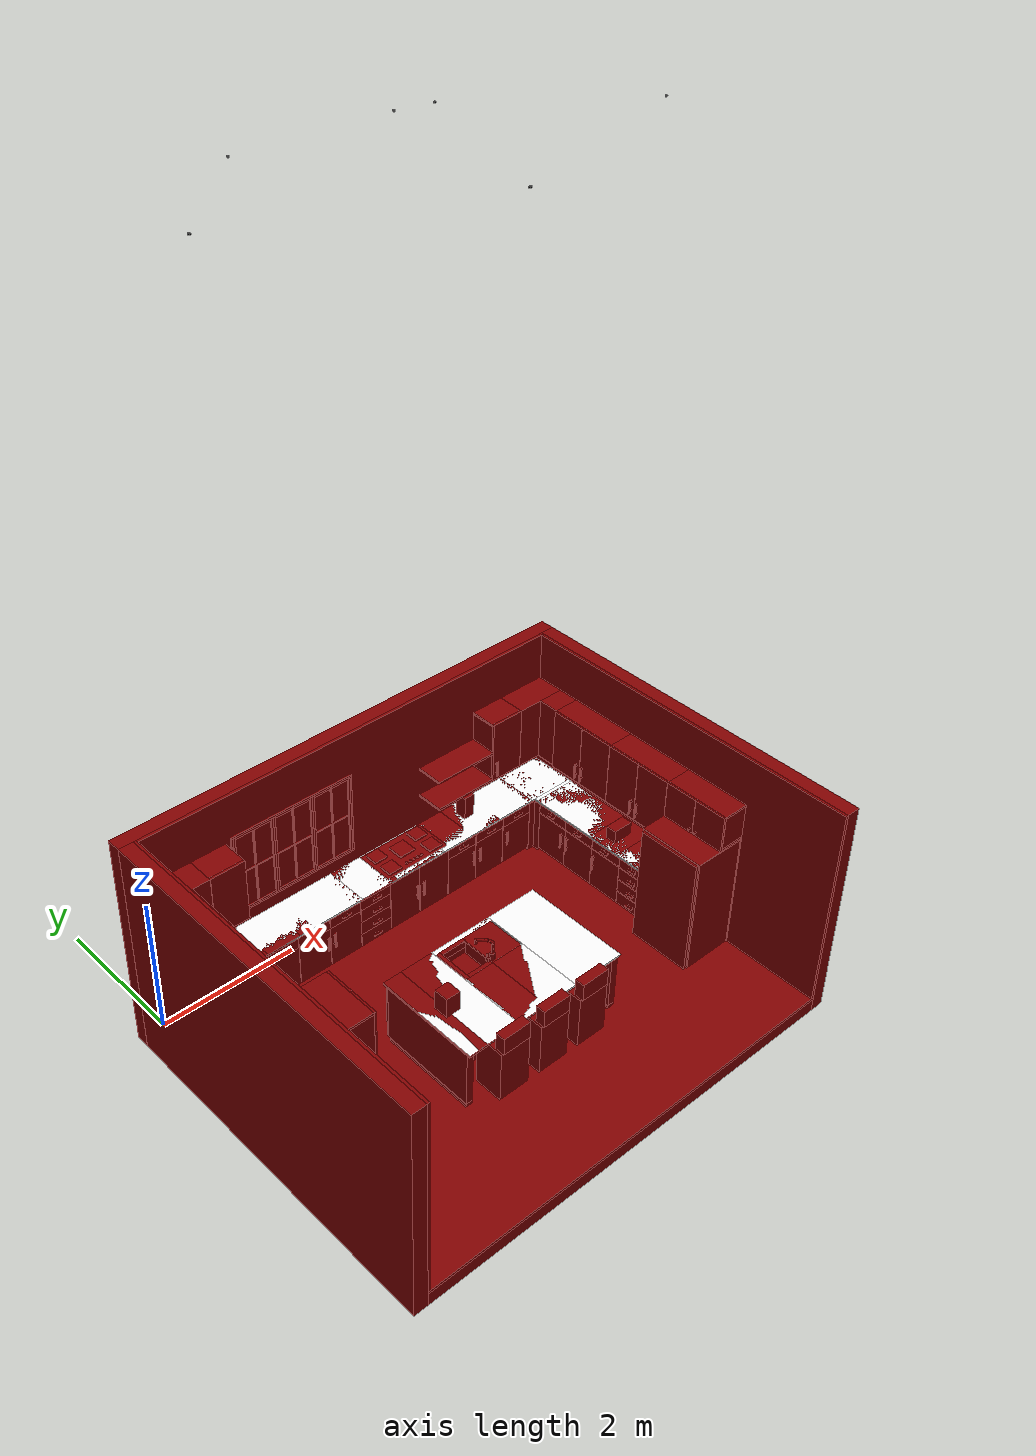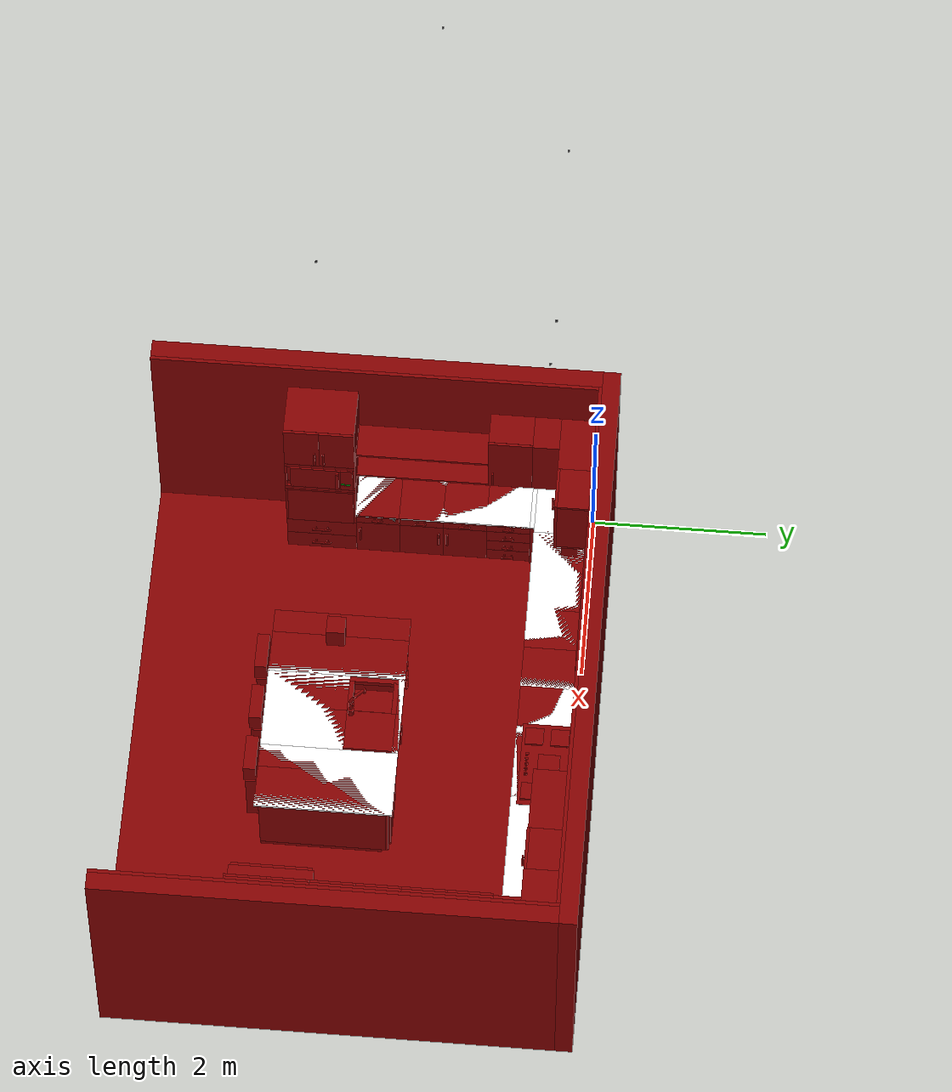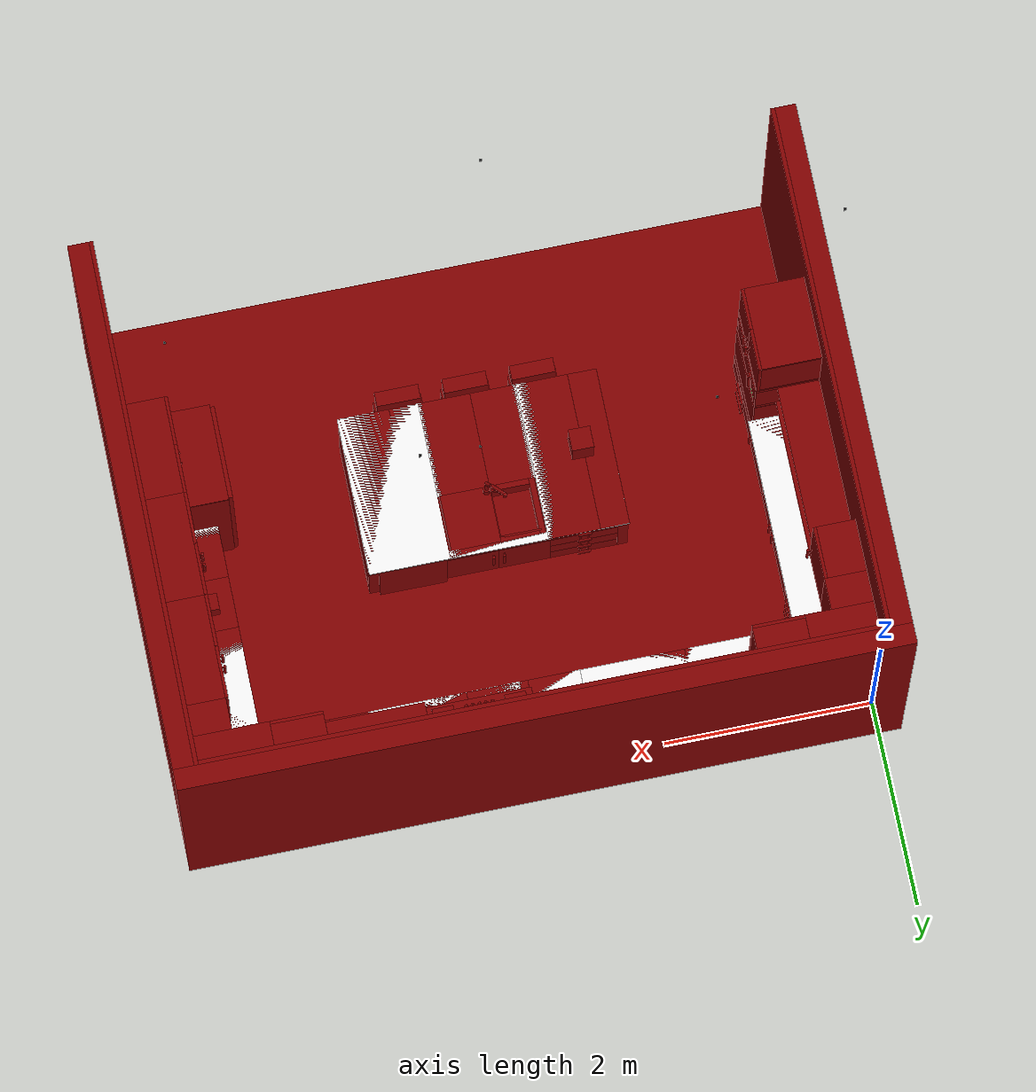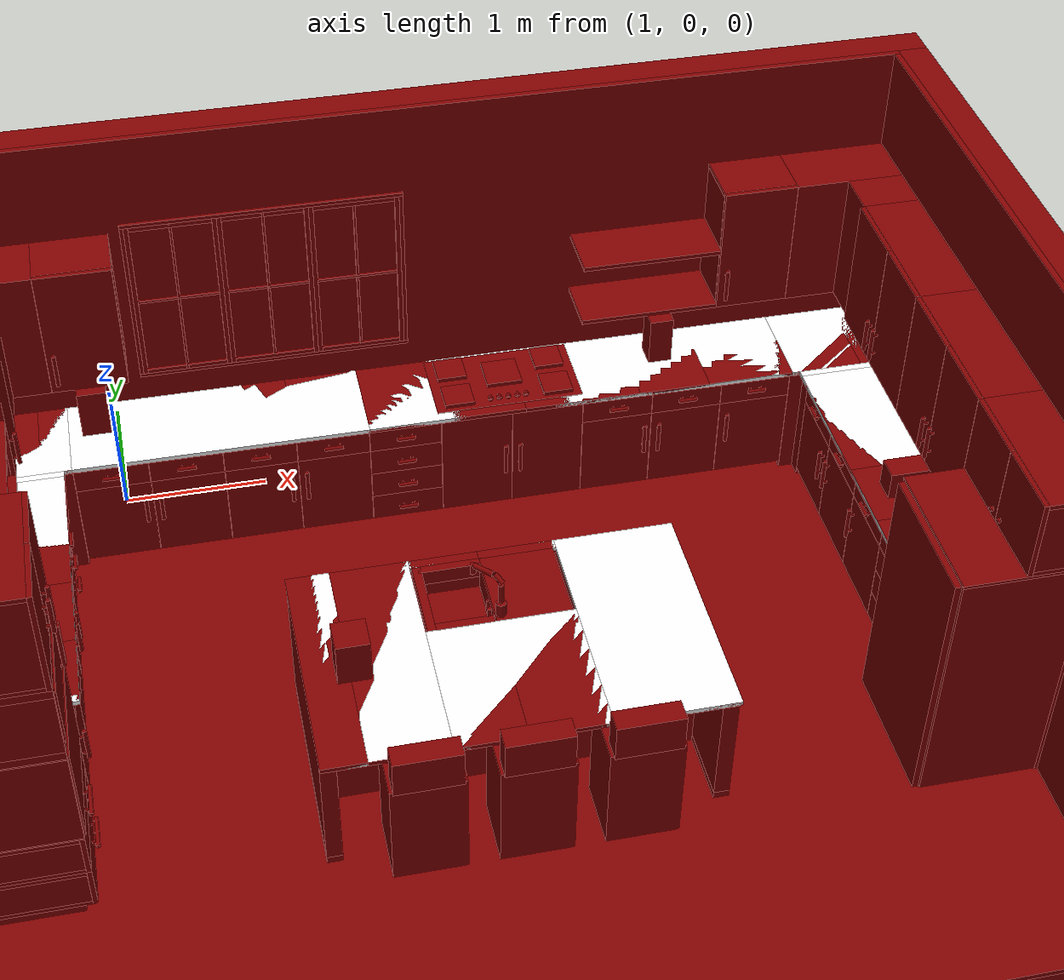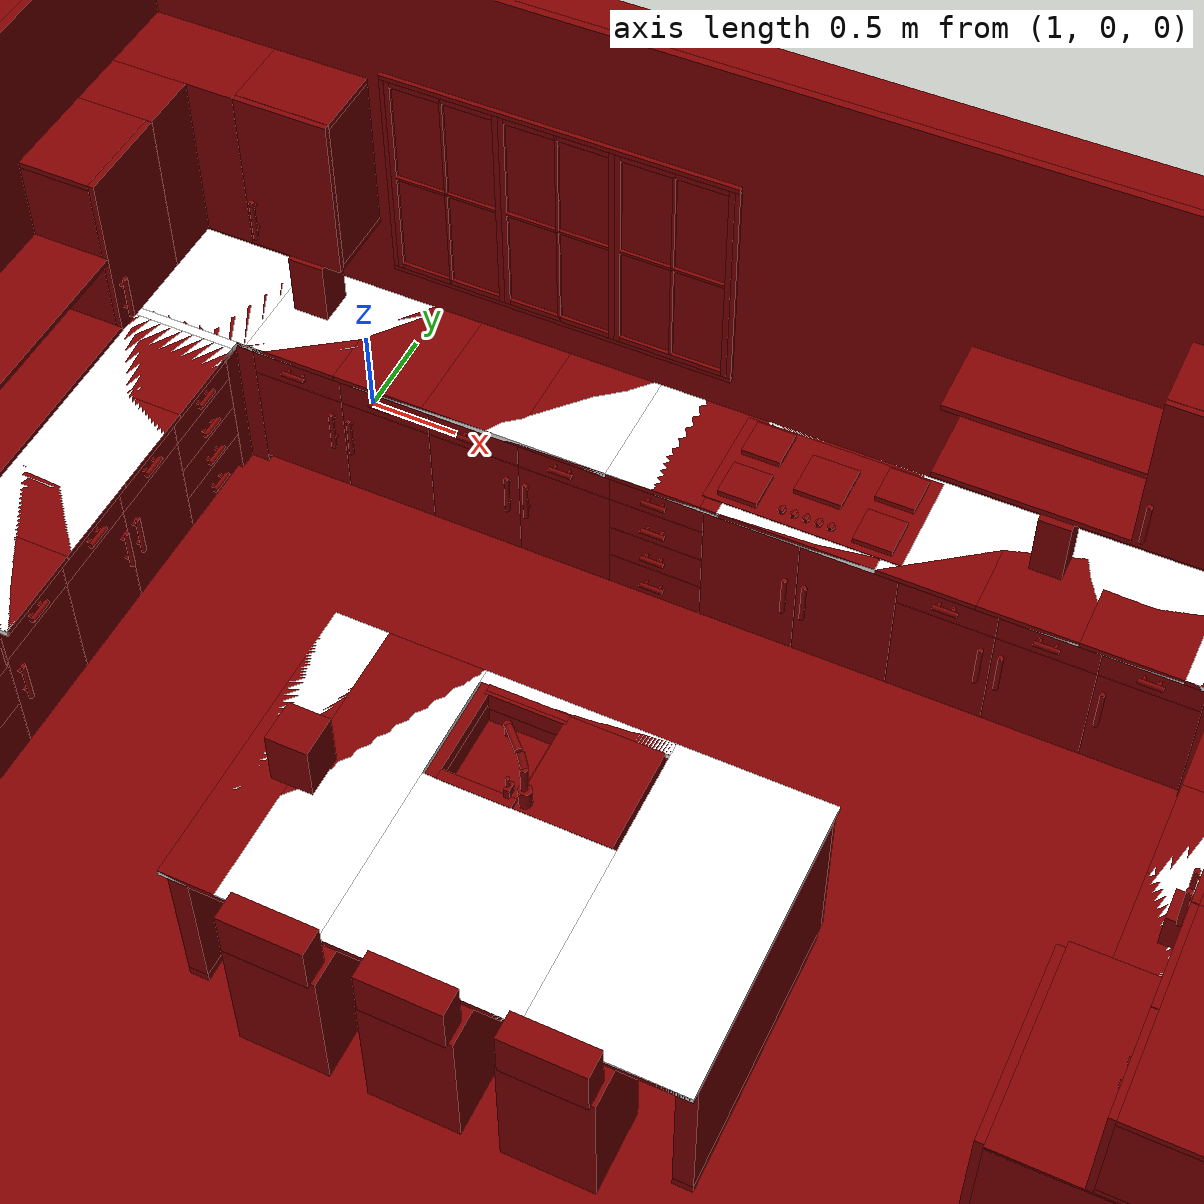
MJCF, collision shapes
<mujoco model="base">
	<compiler angle="radian" meshdir="../meshes/" texturedir="../meshes/"/>

  <size njmax="5000" nconmax="5000"/>

  <visual>
    <map znear="0.001"/>
  </visual>

  <asset>
    <texture type="skybox" builtin="flat" rgb1="1 1 1" rgb2="1 1 1" width="256" height="1536"/>
	<material name="wall_marble_mat" rgba="0.93 0.93 0.93 1.0" shininess="0.01" reflectance="0.1"/>
    <material name="wall_light_gray_mat" rgba="0.5 0.5 0.5 1.0" shininess="0.01" reflectance="0.1"/>
    <material name="floor_backing_room_wall_mat" rgba="0.5 0.5 0.5 1.0"/>
    <material name="floor_room_wall_mat" rgba="0.87 0.76 0.60 1.0"/>
	<material name="counter_top_mat" rgba="0.96 0.96 0.96 1.0" shininess="0.1" reflectance="0.1"/>
	<material name="shelf_mat" rgba="0.8 0.63 0.47 1.0" shininess="0.1" reflectance="0.1"/>
    <material name="blue_gray_mat" rgba="0.42 0.47 0.51 1.0" shininess="0.1"/>
    <material name="counter_base_mat" rgba="0.42 0.47 0.51 1.0" shininess="0.1" reflectance="0.1"/>
    <material name="door_mat" rgba="0.42 0.47 0.51 1.0" texuniform="true" texrepeat="4 4" shininess="0.1" reflectance="0.1"/>
    <material name="door_handle_mat" rgba="0.16 0.17 0.18 1.0" shininess="0.8" reflectance="0.8"/>
    <material name="oven_housing_left_group_mat" rgba="0.16 0.17 0.18 1.0" shininess="0.1"/>
    <material name="dishwasher_island_group_model" rgba="0.57 0.57 0.57 1.0" reflectance="0.5"/>
    <material name="dishwasher_island_group_M_Dishwasher" rgba="0.57 0.57 0.57 1.0" shininess="0.25"/>
    <material name="stovetop_main_group_checker" rgba="0.37 0.37 0.37 1.0" shininess="0.25"/>
    <material name="window_group_main_group_panel_mat" rgba="0.22 0.15 0.12 1.0" specular="0.1" shininess="0.1"/>
    <material name="window_group_main_group_window_mat" rgba="0.95 0.93 0.90 1.0" specular="0.1" shininess="0.1"/>
    <material name="hood_main_group_Hood_light" shininess="0"/>
    <material name="hood_main_group_Hood_metal" shininess="0.684381" rgba="0.8 0.8 0.8 1"/>
    <material name="paper_towel_main_group_model" rgba="0.93 0.93 0.93 1.0" reflectance="0.5"/>
    <material name="paper_towel_main_group_metal" shininess="0.0553676" rgba="0.35595 0.35595 0.35595 1"/>
    <material name="paper_towel_main_group_paperSide" rgba="0.93 0.93 0.93 1.0" shininess="0"/>
    <material name="paper_towel_main_group_paperTopAndBottom" rgba="0.93 0.93 0.93 1.0" shininess="0"/>
    <material name="paper_towel_main_group_paperboard" shininess="0" rgba="0.327778 0.266356 0.198069 1"/>
    <material name="utensil_holder_main_group_Bege" shininess="0.16" rgba="0.621795 0.53677 0.365757 1"/>
    <material name="utensil_holder_main_group_Prata" shininess="0.16" rgba="0.504 0.504 0.504 1"/>
    <material name="utensil_holder_main_group_Preto" shininess="0.16" rgba="0 0 0 1"/>
    <material name="sink_island_group_model" rgba="0.41 0.41 0.41 1.0" reflectance="0.5"/>
    <material name="sink_island_group_m_sink" rgba="0.41 0.41 0.41 1.0" shininess="0.25"/>
    <material name="plant_island_group_model" rgba="0.33 0.47 0.15 1.0" reflectance="0.5"/>
    <material name="plant_island_group_blinn1SG" rgba="0.33 0.47 0.15 1.0" shininess="0.16"/>
    <material name="plant_island_group_blinn2SG" rgba="0.33 0.47 0.15 1.0" shininess="0.16"/>
    <material name="plant_island_group_blinn3SG" rgba="0.80 0.42 0.17 1.0" shininess="0.16"/>
    <material name="plant_island_group_blinn4SG" rgba="0.283 0.15 0.06 1.0" shininess="0.1"/>
    <material name="stool_1_island_group_model" rgba="0.59 0.59 0.59 1.0" reflectance="0.5"/>
    <material name="stool_1_island_group_HBS_0001_M1" rgba="0.59 0.59 0.59 1.0" shininess="0.25"/>
    <material name="stool_2_island_group_model" rgba="0.59 0.59 0.59 1.0" reflectance="0.5"/>
    <material name="stool_2_island_group_HBS_0001_M1" rgba="0.59 0.59 0.59 1.0" shininess="0.25"/>
    <material name="stool_3_island_group_model" rgba="0.59 0.59 0.59 1.0" reflectance="0.5"/>
    <material name="stool_3_island_group_HBS_0001_M1" rgba="0.59 0.59 0.59 1.0" shininess="0.25"/>
    <material name="oven_left_group_model" rgba="0 0 0 1" reflectance="0.5"/>
    <material name="oven_left_group_Material.001" shininess="1" rgba="0 0 0 1"/>
    <material name="oven_left_group_Material.002" shininess="0.81" rgba="0.670724 0.670724 0.670724 1"/>
    <material name="oven_left_group_Material.003" shininess="1" rgba="0.363613 0.363613 0.363613 0.7"/>
    <material name="oven_left_group_Material.007" rgba="0 0 0 1" shininess="0.81"/>
    <material name="oven_left_group_Material.020" shininess="0.000996534" rgba="0.141176 0.141176 0.141176 1"/>
    <material name="microwave_left_group_Back" rgba="1 1 1 1" shininess="0.25"/>
    <material name="microwave_left_group_Body" shininess="0.618999" rgba="0.157434 0.157434 0.157434 1"/>
    <material name="microwave_left_group_Body.001" rgba="0.86 0.86 0.86 1.0" shininess="0.618999"/>
    <material name="microwave_left_group_Front_Metal_Frame" rgba="0.55 0.57 0.60 1.0" shininess="0.25"/>
    <material name="microwave_left_group_Glass" shininess="0" rgba="1 1 1 0.25"/>
    <material name="microwave_left_group_Hold" shininess="0.25" rgba="0 0 0 1"/>
    <material name="microwave_left_group_Inside_Metal" shininess="0.25" rgba="0.8 0.8 0.8 1"/>
    <material name="microwave_left_group_NumPad" rgba="0 0 0 1" shininess="0.393471"/>
    <material name="microwave_left_group_Rubber_Legs" shininess="0.109483" rgba="0 0 0 1"/>
    <material name="fridge_right_group_model" rgba="0.56 0.56 0.56 1.0" reflectance="0.5"/>
    <material name="fridge_right_group_BlackMetKuhl" rgba="0.03 0.03 0.03 1.0" shininess="0.292583"/>
    <material name="fridge_right_group_ChromKuhler" rgba="0.56 0.56 0.56 1.0" shininess="0.404959"/>
    <material name="fridge_right_group_ChromKuhlerDarkk" rgba="0.56 0.56 0.56 1.0" shininess="0.25"/>
    <material name="fridge_right_group_SchwarzerGummi" shininess="0.0955372" rgba="0.0108 0.0108 0.0108 1"/>
    <material name="toaster_right_group_model" rgba="0.68 0.68 0.68 1.0" reflectance="0.5"/>
	<material name="toaster_right_group_main" rgba="0.68 0.68 0.68 1.0" shininess="0.25"/>
    <mesh name="stovetop_main_group_model_0_vis" file="stovetops/stovetop_model_0.obj" scale="1.01852 1.01852 1.01852"/>
	<mesh name="stovetop_main_group_knob_rear_right_0_vis" file="stovetops/stovetop_knob_rear_right_0.obj" scale="1.01852 1.01852 1.01852"/>
    <mesh name="stovetop_main_group_knob_front_left_0_vis" file="stovetops/stovetop_knob_front_left_0.obj" scale="1.01852 1.01852 1.01852"/>
    <mesh name="stovetop_main_group_knob_front_right_0_vis" file="stovetops/stovetop_knob_front_right_0.obj" scale="1.01852 1.01852 1.01852"/>
    <mesh name="stovetop_main_group_knob_rear_left_0_vis" file="stovetops/stovetop_knob_rear_left_0.obj" scale="1.01852 1.01852 1.01852"/>
    <mesh name="stovetop_main_group_knob_center_0_vis" file="stovetops/stovetop_knob_center_0.obj" scale="1.01852 1.01852 1.01852"/>
	<mesh name="hood_main_group_model_0_vis" file="hoods/hood_model_0.obj" scale="0.808824 0.923077 0.808824"/>
    <mesh name="hood_main_group_model_2_vis" file="hoods/hood_model_2.obj" scale="0.808824 0.923077 0.808824"/>
    <mesh name="paper_towel_main_group_model_0_vis" file="paper_towel_holders/paper_towel_holder_model_0.obj" scale="0.35 0.35 0.35"/>
    <mesh name="paper_towel_main_group_model_1_vis" file="paper_towel_holders/paper_towel_holder_model_1.obj" scale="0.35 0.35 0.35"/>
    <mesh name="paper_towel_main_group_model_2_vis" file="paper_towel_holders/paper_towel_holder_model_2.obj" scale="0.35 0.35 0.35"/>
    <mesh name="paper_towel_main_group_model_3_vis" file="paper_towel_holders/paper_towel_holder_model_3.obj" scale="0.35 0.35 0.35"/>
    <mesh name="utensil_holder_main_group_model_0_vis" file="utensil_holders/utensil_holder_model_0.obj" scale="0.35 0.35 0.35"/>
    <mesh name="utensil_holder_main_group_model_2_vis" file="utensil_holders/utensil_holder_model_2.obj" scale="0.35 0.35 0.35"/>
    <mesh name="utensil_holder_main_group_model_3_vis" file="utensil_holders/utensil_holder_model_3.obj" scale="0.35 0.35 0.35"/>
    <mesh name="sink_island_group_model_0_vis" file="sinks/sink_model_0.obj" scale="0.916667 0.916667 0.916667"/>
    <mesh name="sink_island_group_spout_0_vis" file="sinks/sink_spout_0.obj" scale="0.916667 0.916667 0.916667"/>
    <mesh name="sink_island_group_handle_0_vis" file="sinks/sink_handle_0.obj" scale="0.916667 0.916667 0.916667"/>
    <mesh name="dishwasher_island_group_model_0_vis" file="dishwashers/dishwasher_model_0.obj" scale="0.915417 0.844351 0.89"/>
    <mesh name="plant_island_group_model_0_vis" file="plants/plant_model_0.obj" scale="0.3 0.3 0.3"/>
    <mesh name="plant_island_group_model_1_vis" file="plants/plant_model_1.obj" scale="0.3 0.3 0.3"/>
    <mesh name="plant_island_group_model_2_vis" file="plants/plant_model_2.obj" scale="0.3 0.3 0.3" inertia="shell"/>
    <mesh name="plant_island_group_model_3_vis" file="plants/plant_model_3.obj" scale="0.3 0.3 0.3"/>
    <mesh name="stool_1_island_group_model_0_vis" file="stools/stool_model_0.obj"/>
    <mesh name="stool_2_island_group_model_0_vis" file="stools/stool_model_0.obj"/>
    <mesh name="stool_3_island_group_model_0_vis" file="stools/stool_model_0.obj"/>
    <mesh name="oven_left_group_model_0_vis" file="ovens/oven_model_0.obj" scale="0.75 0.973361 0.738286"/>
    <mesh name="oven_left_group_model_1_vis" file="ovens/oven_model_1.obj" scale="0.75 0.973361 0.738286"/>
    <mesh name="oven_left_group_model_2_vis" file="ovens/oven_model_2.obj" scale="0.75 0.973361 0.738286"/>
    <mesh name="oven_left_group_model_3_vis" file="ovens/oven_model_3.obj" scale="0.75 0.973361 0.738286"/>
    <mesh name="oven_left_group_model_4_vis" file="ovens/oven_model_4.obj" scale="0.75 0.973361 0.738286"/>
    <mesh name="microwave_left_group_model_0_vis" file="microwaves/microwave_model_0.obj" scale="0.75 0.735294 0.75"/>
    <mesh name="microwave_left_group_model_1_vis" file="microwaves/microwave_model_1.obj" scale="0.75 0.735294 0.75"/>
    <mesh name="microwave_left_group_model_2_vis" file="microwaves/microwave_model_2.obj" scale="0.75 0.735294 0.75"/>
    <mesh name="microwave_left_group_model_5_vis" file="microwaves/microwave_model_5.obj" scale="0.75 0.735294 0.75"/>
    <mesh name="microwave_left_group_model_6_vis" file="microwaves/microwave_model_6.obj" scale="0.75 0.735294 0.75"/>
    <mesh name="microwave_left_group_model_7_vis" file="microwaves/microwave_model_7.obj" scale="0.75 0.735294 0.75"/>
    <mesh name="microwave_left_group_model_8_vis" file="microwaves/microwave_model_8.obj" scale="0.75 0.735294 0.75"/>
    <mesh name="microwave_left_group_model_9_vis" file="microwaves/microwave_model_9.obj" scale="0.75 0.735294 0.75"/>
    <mesh name="microwave_left_group_model_10_vis" file="microwaves/microwave_model_10.obj" scale="0.75 0.735294 0.75"/>
    <mesh name="microwave_left_group_door_1_vis" file="microwaves/microwave_door_1.obj" scale="0.75 0.735294 0.75"/>
    <mesh name="microwave_left_group_door_3_vis" file="microwaves/microwave_door_3.obj" scale="0.75 0.735294 0.75"/>
    <mesh name="microwave_left_group_door_4_vis" file="microwaves/microwave_door_4.obj" scale="0.75 0.735294 0.75"/>
    <mesh name="microwave_left_group_door_5_vis" file="microwaves/microwave_door_5.obj" scale="0.75 0.735294 0.75"/>
    <mesh name="fridge_right_group_model_0_vis" file="fridges/fridge_model_0.obj" scale="1.75658 1.95289 1.75"/>
    <mesh name="fridge_right_group_model_1_vis" file="fridges/fridge_model_1.obj" scale="1.75658 1.95289 1.75"/>
    <mesh name="fridge_right_group_model_2_vis" file="fridges/fridge_model_2.obj" scale="1.75658 1.95289 1.75"/>
    <mesh name="fridge_right_group_model_3_vis" file="fridges/fridge_model_3.obj" scale="1.75658 1.95289 1.75"/>
    <mesh name="toaster_right_group_model_0_vis" file="toasters/toaster_model_0.obj" scale="0.3 0.3 0.3"/>
  </asset>

  <worldbody>
    <light pos="2 -2 2" dir="0.009999 0.009999 -0.9999" directional="true" castshadow="false" ambient="0.3 0.3 0.3" diffuse="0.3 0.3 0.3"/>
    <body name="wall_room_main" pos="3.2 0.02 1.5" quat="-0.707107 0.707107 0 0">
      <geom name="wall_room_g0" size="3.24 1.5 0.02" type="box" rgba="0.5 0 0 1"/>
      <geom name="wall_room_g0_vis" size="3.24 1.5 0.02" type="box" contype="0" conaffinity="0" group="1" mass="0" material="wall_marble_mat"/>
      <site name="wall_room_default_site" pos="0 0 0" size="0.002" rgba="1 0 0 1"/>
    </body>
    <body name="wall_backing_room_main" pos="3.2 0.14 1.38" quat="-0.707107 0.707107 0 0">
      <geom name="wall_backing_room_g0" size="3.44 1.62 0.1" type="box" rgba="0.5 0 0 1"/>
      <geom name="wall_backing_room_g0_vis" size="3.44 1.62 0.1" type="box" contype="0" conaffinity="0" group="1" mass="0" material="wall_light_gray_mat"/>
      <site name="wall_backing_room_default_site" pos="0 0 0" size="0.002" rgba="1 0 0 1"/>
    </body>
    <body name="wall_left_room_main" pos="-0.02 -2.5 1.5" quat="0.5 0.5 -0.5 -0.5">
      <geom name="wall_left_room_g0" size="2.54 1.5 0.02" type="box" rgba="0.5 0 0 1"/>
      <geom name="wall_left_room_g0_vis" size="2.54 1.5 0.02" type="box" contype="0" conaffinity="0" group="1" mass="0" material="wall_marble_mat"/>
      <site name="wall_left_room_default_site" pos="0 0 0" size="0.002" rgba="1 0 0 1"/>
    </body>
    <body name="wall_left_backing_room_main" pos="-0.14 -2.5 1.38" quat="0.5 0.5 -0.5 -0.5">
      <geom name="wall_left_backing_room_g0" size="2.54 1.62 0.1" type="box" rgba="0.5 0 0 1"/>
      <geom name="wall_left_backing_room_g0_vis" size="2.54 1.62 0.1" type="box" contype="0" conaffinity="0" group="1" mass="0" material="wall_light_gray_mat"/>
      <site name="wall_left_backing_room_default_site" pos="0 0 0" size="0.002" rgba="1 0 0 1"/>
    </body>
    <body name="wall_right_room_main" pos="6.42 -2.5 1.5" quat="0.5 -0.5 -0.5 0.5">
      <geom name="wall_right_room_g0" size="2.54 1.5 0.02" type="box" rgba="0.5 0 0 1"/>
      <geom name="wall_right_room_g0_vis" size="2.54 1.5 0.02" type="box" contype="0" conaffinity="0" group="1" mass="0" material="wall_marble_mat"/>
      <site name="wall_right_room_default_site" pos="0 0 0" size="0.002" rgba="1 0 0 1"/>
    </body>
    <body name="wall_right_backing_room_main" pos="6.54 -2.5 1.38" quat="0.5 -0.5 -0.5 0.5">
      <geom name="wall_right_backing_room_g0" size="2.54 1.62 0.1" type="box" rgba="0.5 0 0 1"/>
      <geom name="wall_right_backing_room_g0_vis" size="2.54 1.62 0.1" type="box" contype="0" conaffinity="0" group="1" mass="0" material="wall_light_gray_mat"/>
      <site name="wall_right_backing_room_default_site" pos="0 0 0" size="0.002" rgba="1 0 0 1"/>
    </body>
    <body name="floor_room_main" pos="3.2 -2.5 -0.02" quat="0.707107 0 0 0.707107">
      <geom name="floor_room_g0" size="2.54 3.24 0.02" type="box" rgba="0.5 0 0 1"/>
      <geom name="floor_room_g0_vis" size="2.54 3.24 0.02" type="box" contype="0" conaffinity="0" group="1" mass="0" material="floor_room_wall_mat"/>
      <site name="floor_room_default_site" pos="0 0 0" size="0.002" rgba="1 0 0 1"/>
    </body>
    <body name="floor_backing_room_main" pos="3.2 -2.5 -0.14" quat="0.707107 0 0 0.707107">
      <geom name="floor_backing_room_g0" size="2.54 3.24 0.1" type="box" rgba="0.5 0 0 1"/>
      <geom name="floor_backing_room_g0_vis" size="2.54 3.24 0.1" type="box" contype="0" conaffinity="0" group="1" mass="0" material="floor_backing_room_wall_mat"/>
      <site name="floor_backing_room_default_site" pos="0 0 0" size="0.002" rgba="1 0 0 1"/>
    </body>
    <body name="counter_corner_main_group_main" pos="0.35 -0.325 0.46">
      <geom name="counter_corner_main_group_base_right" size="0.0001 0.3 0.445" pos="0.3499 0.025 -0.015" type="box" density="10" rgba="0.5 0 0 1"/>
      <geom name="counter_corner_main_group_base_left" size="0.0001 0.3 0.445" pos="-0.3499 0.025 -0.015" type="box" density="10" rgba="0.5 0 0 1"/>
      <geom name="counter_corner_main_group_base_back" size="0.3498 0.015 0.445" pos="0 0.31 -0.015" type="box" density="10" rgba="0.5 0 0 1"/>
      <geom name="counter_corner_main_group_base_front" size="0.3498 0.015 0.445" pos="0 -0.26 -0.015" type="box" density="10" rgba="0.5 0 0 1"/>
      <geom name="counter_corner_main_group_base_right_visual" size="0.0001 0.3 0.445" pos="0.3499 0.025 -0.015" type="box" contype="0" conaffinity="0" group="1" mass="0" material="counter_base_mat"/>
      <geom name="counter_corner_main_group_base_left_visual" size="0.0001 0.3 0.445" pos="-0.3499 0.025 -0.015" type="box" contype="0" conaffinity="0" group="1" mass="0" material="counter_base_mat"/>
      <geom name="counter_corner_main_group_base_back_visual" size="0.3498 0.015 0.445" pos="0 0.31 -0.015" type="box" contype="0" conaffinity="0" group="1" mass="0" material="counter_base_mat"/>
      <geom name="counter_corner_main_group_base_front_visual" size="0.3498 0.015 0.445" pos="0 -0.26 -0.015" type="box" contype="0" conaffinity="0" group="1" mass="0" material="counter_base_mat"/>
      <geom name="counter_corner_main_group_top_visual" size="0.35 0.325 0.015" pos="0 0 0.445" type="box" contype="0" conaffinity="0" group="1" mass="0" material="counter_top_mat"/>
      <geom name="counter_corner_main_group_top_0" size="0.25 0.325 0.015" pos="-0.1 0 0.445" type="box" density="10" rgba="0.5 0 0 1"/>
      <geom name="counter_corner_main_group_top_1" size="0.1 0.325 0.015" pos="0.25 0 0.445" type="box" density="10" rgba="0.5 0 0 1"/>
      <site name="counter_corner_main_group_ext_p0" pos="-0.35 -0.275 -0.46" size="0.01" rgba="0 0 0 0"/>
      <site name="counter_corner_main_group_ext_px" pos="0.35 -0.275 -0.46" size="0.01" rgba="1 0 0 0"/>
      <site name="counter_corner_main_group_ext_py" pos="-0.35 0.325 -0.46" size="0.01" rgba="0 1 0 0"/>
      <site name="counter_corner_main_group_ext_pz" pos="-0.35 -0.275 0.46" size="0.01" rgba="0 0 1 0"/>
      <site name="counter_corner_main_group_int_p0" pos="0 0 0" size="0.01" rgba="0.5 0.5 0.5 0"/>
      <site name="counter_corner_main_group_int_px" pos="0 0 0" size="0.01" rgba="1 1 0 0"/>
      <site name="counter_corner_main_group_int_py" pos="0 0 0" size="0.01" rgba="0 1 1 0"/>
      <site name="counter_corner_main_group_int_pz" pos="0 0 0" size="0.01" rgba="1 0 1 0"/>
      <site name="counter_corner_main_group_default_site" pos="0 0 0" size="0.002" rgba="1 0 0 0"/>
    </body>
    <body name="counter_1_main_group_main" pos="1.7 -0.325 0.46">
      <geom name="counter_1_main_group_base_right" size="0.01 0.01 0.01" pos="0 0 10" type="box" density="10" rgba="0 0 0 0"/>
      <geom name="counter_1_main_group_base_left" size="0.01 0.01 0.01" pos="0 0 10" type="box" density="10" rgba="0 0 0 0"/>
      <geom name="counter_1_main_group_base_back" size="0.01 0.01 0.01" pos="0 0 10" type="box" density="10" rgba="0 0 0 0"/>
      <geom name="counter_1_main_group_base_front" size="0.01 0.01 0.01" pos="0 0 10" type="box" density="10" rgba="0 0 0 0"/>
      <geom name="counter_1_main_group_base_right_visual" size="0.01 0.01 0.01" pos="0 0 10" type="box" contype="0" conaffinity="0" group="1" mass="0" material="counter_base_mat" rgba="0 0 0 0"/>
      <geom name="counter_1_main_group_base_left_visual" size="0.01 0.01 0.01" pos="0 0 10" type="box" contype="0" conaffinity="0" group="1" mass="0" material="counter_base_mat" rgba="0 0 0 0"/>
      <geom name="counter_1_main_group_base_back_visual" size="0.01 0.01 0.01" pos="0 0 10" type="box" contype="0" conaffinity="0" group="1" mass="0" material="counter_base_mat" rgba="0 0 0 0"/>
      <geom name="counter_1_main_group_base_front_visual" size="0.01 0.01 0.01" pos="0 0 10" type="box" contype="0" conaffinity="0" group="1" mass="0" material="counter_base_mat" rgba="0 0 0 0"/>
      <geom name="counter_1_main_group_top_visual" size="1 0.325 0.015" pos="0 0 0.445" type="box" contype="0" conaffinity="0" group="1" mass="0" material="counter_top_mat"/>
      <geom name="counter_1_main_group_top_0" size="0.25 0.325 0.015" pos="-0.75 0 0.445" type="box" density="10" rgba="0.5 0 0 1"/>
      <geom name="counter_1_main_group_top_1" size="0.25 0.325 0.015" pos="-0.25 0 0.445" type="box" density="10" rgba="0.5 0 0 1"/>
      <geom name="counter_1_main_group_top_2" size="0.25 0.325 0.015" pos="0.25 0 0.445" type="box" density="10" rgba="0.5 0 0 1"/>
      <geom name="counter_1_main_group_top_3" size="0.25 0.325 0.015" pos="0.75 0 0.445" type="box" density="10" rgba="0.5 0 0 1"/>
      <site name="counter_1_main_group_ext_p0" pos="-1 -0.275 -0.46" size="0.01" rgba="0 0 0 0"/>
      <site name="counter_1_main_group_ext_px" pos="1 -0.275 -0.46" size="0.01" rgba="1 0 0 0"/>
      <site name="counter_1_main_group_ext_py" pos="-1 0.325 -0.46" size="0.01" rgba="0 1 0 0"/>
      <site name="counter_1_main_group_ext_pz" pos="-1 -0.275 0.46" size="0.01" rgba="0 0 1 0"/>
      <site name="counter_1_main_group_int_p0" pos="0 0 0" size="0.01" rgba="0.5 0.5 0.5 0"/>
      <site name="counter_1_main_group_int_px" pos="0 0 0" size="0.01" rgba="1 1 0 0"/>
      <site name="counter_1_main_group_int_py" pos="0 0 0" size="0.01" rgba="0 1 1 0"/>
      <site name="counter_1_main_group_int_pz" pos="0 0 0" size="0.01" rgba="1 0 1 0"/>
      <site name="counter_1_main_group_default_site" pos="0 0 0" size="0.002" rgba="1 0 0 0"/>
    </body>
    <body name="stovetop_main_group_main" pos="3.69 -0.3 0.925093">
      <geom name="stovetop_main_group_g0" type="mesh" contype="0" conaffinity="0" group="1" friction="0.95 0.3 0.1" solref="0.001" solimp="0.998 0.998" density="100" material="stovetop_main_group_checker" mesh="stovetop_main_group_model_0_vis"/>
      <geom name="stovetop_main_group_g1" size="0.509259 0.280093 0.0152778" pos="0 0 -0.0142593" type="box" rgba="0.5 0 0 0.5"/>
      <geom name="stovetop_main_group_g2" size="0.101852 0.101852 0.0162963" pos="-0.346296 -0.143611 0.0142593" type="box" rgba="0.5 0 0 0.5"/>
      <geom name="stovetop_main_group_g3" size="0.101852 0.101852 0.0162963" pos="-0.346296 0.14463 0.0142593" type="box" rgba="0.5 0 0 0.5"/>
      <geom name="stovetop_main_group_g4" size="0.101852 0.101852 0.0162963" pos="0.346296 -0.143611 0.0142593" type="box" rgba="0.5 0 0 0.5"/>
      <geom name="stovetop_main_group_g5" size="0.101852 0.101852 0.0162963" pos="0.346296 0.14463 0.0142593" type="box" rgba="0.5 0 0 0.5"/>
      <geom name="stovetop_main_group_g6" size="0.122222 0.122222 0.0162963" pos="0 0.0407407 0.0142593" type="box" rgba="0.5 0 0 0.5"/>
      <site name="stovetop_main_group_burner_on_front_left" pos="-0.346296 -0.14463 0.0142593" size="0.0611111 0.00407407" type="cylinder" rgba="0.3 0.4 1 0.5"/>
      <site name="stovetop_main_group_burner_on_front_right" pos="0.346296 -0.143611 0.0142593" size="0.0407407 0.00407407" type="cylinder" rgba="0.3 0.4 1 0.5"/>
      <site name="stovetop_main_group_burner_on_rear_left" pos="-0.346296 0.14463 0.0142593" size="0.0611111 0.00407407" type="cylinder" rgba="0.3 0.4 1 0.5"/>
      <site name="stovetop_main_group_burner_on_rear_right" pos="0.346296 0.14463 0.0142593" size="0.0712963 0.00407407" type="cylinder" rgba="0.3 0.4 1 0.5"/>
      <site name="stovetop_main_group_burner_on_center" pos="0 0.0407407 0.0142593" size="0.0916667 0.00407407" type="cylinder" rgba="0.3 0.4 1 0.5"/>
      <site name="stovetop_main_group_default_site" pos="0 0 0" size="0.00203704" rgba="1 0 0 0"/>
      <body name="stovetop_main_group_knob_rear_right">
        <joint name="stovetop_main_group_knob_rear_right_joint" pos="0.0618852 -0.208796 0.00733333" axis="0 0 1" armature="2" damping="1"/>
        <geom name="stovetop_main_group_g7" type="mesh" contype="0" conaffinity="0" group="1" friction="0.95 0.3 0.1" solref="0.001" solimp="0.998 0.998" density="100" material="stovetop_main_group_checker" mesh="stovetop_main_group_knob_rear_right_0_vis"/>
        <geom name="stovetop_main_group_g8" size="0.0198611 0.00631481" pos="0.0618852 -0.208796 0.00763889" type="cylinder" rgba="0.5 0 0 0.5"/>
        <geom name="stovetop_main_group_g9" size="0.00753704 0.0198611 0.00468519" pos="0.0618852 -0.208796 0.0183333" type="box" rgba="0.5 0 0 0.5"/>
      </body>
      <body name="stovetop_main_group_knob_front_left">
        <joint name="stovetop_main_group_knob_front_left_joint" pos="-0.127009 -0.208796 0.00733333" axis="0 0 1" armature="2" damping="1"/>
        <geom name="stovetop_main_group_g10" type="mesh" contype="0" conaffinity="0" group="1" friction="0.95 0.3 0.1" solref="0.001" solimp="0.998 0.998" density="100" material="stovetop_main_group_checker" mesh="stovetop_main_group_knob_front_left_0_vis"/>
        <geom name="stovetop_main_group_g11" size="0.0198611 0.00631481" pos="-0.127009 -0.208796 0.00763889" type="cylinder" rgba="0.5 0 0 0.5"/>
        <geom name="stovetop_main_group_g12" size="0.00753704 0.0198611 0.00468519" pos="-0.127009 -0.208796 0.0183333" type="box" rgba="0.5 0 0 0.5"/>
      </body>
      <body name="stovetop_main_group_knob_front_right">
        <joint name="stovetop_main_group_knob_front_right_joint" pos="0.12487 -0.208796 0.00733333" axis="0 0 1" armature="2" damping="1"/>
        <geom name="stovetop_main_group_g13" type="mesh" contype="0" conaffinity="0" group="1" friction="0.95 0.3 0.1" solref="0.001" solimp="0.998 0.998" density="100" material="stovetop_main_group_checker" mesh="stovetop_main_group_knob_front_right_0_vis"/>
        <geom name="stovetop_main_group_g14" size="0.0198611 0.00631481" pos="0.12487 -0.208796 0.00763889" type="cylinder" rgba="0.5 0 0 0.5"/>
        <geom name="stovetop_main_group_g15" size="0.00753704 0.0198611 0.00468519" pos="0.12487 -0.208796 0.0183333" type="box" rgba="0.5 0 0 0.5"/>
      </body>
      <body name="stovetop_main_group_knob_rear_left">
        <joint name="stovetop_main_group_knob_rear_left_joint" pos="-0.0640139 -0.208796 0.00733333" axis="0 0 1" armature="2" damping="1"/>
        <geom name="stovetop_main_group_g16" type="mesh" contype="0" conaffinity="0" group="1" friction="0.95 0.3 0.1" solref="0.001" solimp="0.998 0.998" density="100" material="stovetop_main_group_checker" mesh="stovetop_main_group_knob_rear_left_0_vis"/>
        <geom name="stovetop_main_group_g17" size="0.0198611 0.00631481" pos="-0.0640139 -0.208796 0.00763889" type="cylinder" rgba="0.5 0 0 0.5"/>
        <geom name="stovetop_main_group_g18" size="0.00753704 0.0198611 0.00468519" pos="-0.0640139 -0.208796 0.0183333" type="box" rgba="0.5 0 0 0.5"/>
      </body>
      <body name="stovetop_main_group_knob_center">
        <joint name="stovetop_main_group_knob_center" pos="-0.00101852 -0.208796 0.00733333" axis="0 0 1" armature="2" damping="1"/>
        <geom name="stovetop_main_group_g19" type="mesh" contype="0" conaffinity="0" group="1" friction="0.95 0.3 0.1" solref="0.001" solimp="0.998 0.998" density="100" material="stovetop_main_group_checker" mesh="stovetop_main_group_knob_center_0_vis"/>
        <geom name="stovetop_main_group_g20" size="0.0198611 0.00631481" pos="-0.00101852 -0.208796 0.00763889" type="cylinder" rgba="0.5 0 0 0.5"/>
        <geom name="stovetop_main_group_g21" size="0.00753704 0.0198611 0.00468519" pos="-0.00101852 -0.208796 0.0183333" type="box" rgba="0.5 0 0 0.5"/>
      </body>
    </body>
    <body name="counter_main_main_group_main" pos="4.2 -0.325 0.46">
      <geom name="counter_main_main_group_base_right" size="0.01 0.01 0.01" pos="0 0 10" type="box" density="10" rgba="0 0 0 0"/>
      <geom name="counter_main_main_group_base_left" size="0.01 0.01 0.01" pos="0 0 10" type="box" density="10" rgba="0 0 0 0"/>
      <geom name="counter_main_main_group_base_back" size="0.01 0.01 0.01" pos="0 0 10" type="box" density="10" rgba="0 0 0 0"/>
      <geom name="counter_main_main_group_base_front" size="0.01 0.01 0.01" pos="0 0 10" type="box" density="10" rgba="0 0 0 0"/>
      <geom name="counter_main_main_group_base_right_visual" size="0.01 0.01 0.01" pos="0 0 10" type="box" contype="0" conaffinity="0" group="1" mass="0" material="counter_base_mat" rgba="0 0 0 0"/>
      <geom name="counter_main_main_group_base_left_visual" size="0.01 0.01 0.01" pos="0 0 10" type="box" contype="0" conaffinity="0" group="1" mass="0" material="counter_base_mat" rgba="0 0 0 0"/>
      <geom name="counter_main_main_group_base_back_visual" size="0.01 0.01 0.01" pos="0 0 10" type="box" contype="0" conaffinity="0" group="1" mass="0" material="counter_base_mat" rgba="0 0 0 0"/>
      <geom name="counter_main_main_group_base_front_visual" size="0.01 0.01 0.01" pos="0 0 10" type="box" contype="0" conaffinity="0" group="1" mass="0" material="counter_base_mat" rgba="0 0 0 0"/>
      <geom name="counter_main_main_group_top_left_visual" size="0.292794 0.325 0.015" pos="-1.20721 0 0.445" type="box" contype="0" conaffinity="0" group="1" mass="0" material="counter_top_mat"/>
      <geom name="counter_main_main_group_top_left_0" size="0.25 0.325 0.015" pos="-1.25 0 0.445" type="box" density="10" rgba="0.5 0 0 1"/>
      <geom name="counter_main_main_group_top_left_1" size="0.0427941 0.325 0.015" pos="-0.957206 0 0.445" type="box" density="10" rgba="0.5 0 0 1"/>
      <geom name="counter_main_main_group_top_right_visual" size="0.802794 0.325 0.015" pos="0.697206 0 0.445" type="box" contype="0" conaffinity="0" group="1" mass="0" material="counter_top_mat"/>
      <geom name="counter_main_main_group_top_right_0" size="0.25 0.325 0.015" pos="0.144412 0 0.445" type="box" density="10" rgba="0.5 0 0 1"/>
      <geom name="counter_main_main_group_top_right_1" size="0.25 0.325 0.015" pos="0.644412 0 0.445" type="box" density="10" rgba="0.5 0 0 1"/>
      <geom name="counter_main_main_group_top_right_2" size="0.25 0.325 0.015" pos="1.14441 0 0.445" type="box" density="10" rgba="0.5 0 0 1"/>
      <geom name="counter_main_main_group_top_right_3" size="0.0527941 0.325 0.015" pos="1.44721 0 0.445" type="box" density="10" rgba="0.5 0 0 1"/>
      <geom name="counter_main_main_group_top_front_visual" size="0.404412 0.0375 0.015" pos="-0.51 -0.2875 0.445" type="box" contype="0" conaffinity="0" group="1" mass="0" material="counter_top_mat"/>
      <geom name="counter_main_main_group_top_front_0" size="0.25 0.0375 0.015" pos="-0.664412 -0.2875 0.445" type="box" density="10" rgba="0.5 0 0 1"/>
      <geom name="counter_main_main_group_top_front_1" size="0.154412 0.0375 0.015" pos="-0.26 -0.2875 0.445" type="box" density="10" rgba="0.5 0 0 1"/>
      <geom name="counter_main_main_group_top_back_visual" size="0.404412 0.0125 0.015" pos="-0.51 0.3125 0.445" type="box" contype="0" conaffinity="0" group="1" mass="0" material="counter_top_mat"/>
      <geom name="counter_main_main_group_top_back_0" size="0.25 0.0125 0.015" pos="-0.664412 0.3125 0.445" type="box" density="10" rgba="0.5 0 0 1"/>
      <geom name="counter_main_main_group_top_back_1" size="0.154412 0.0125 0.015" pos="-0.26 0.3125 0.445" type="box" density="10" rgba="0.5 0 0 1"/>
      <site name="counter_main_main_group_ext_p0" pos="-1.5 -0.275 -0.46" size="0.01" rgba="0 0 0 0"/>
      <site name="counter_main_main_group_ext_px" pos="1.5 -0.275 -0.46" size="0.01" rgba="1 0 0 0"/>
      <site name="counter_main_main_group_ext_py" pos="-1.5 0.325 -0.46" size="0.01" rgba="0 1 0 0"/>
      <site name="counter_main_main_group_ext_pz" pos="-1.5 -0.275 0.46" size="0.01" rgba="0 0 1 0"/>
      <site name="counter_main_main_group_int_p0" pos="0 0 0" size="0.01" rgba="0.5 0.5 0.5 0"/>
      <site name="counter_main_main_group_int_px" pos="0 0 0" size="0.01" rgba="1 1 0 0"/>
      <site name="counter_main_main_group_int_py" pos="0 0 0" size="0.01" rgba="0 1 1 0"/>
      <site name="counter_main_main_group_int_pz" pos="0 0 0" size="0.01" rgba="1 0 1 0"/>
      <site name="counter_main_main_group_default_site" pos="0 0 0" size="0.002" rgba="1 0 0 0"/>
    </body>
    <body name="counter_corner_2_main_group_main" pos="6.05 -0.325 0.46">
      <geom name="counter_corner_2_main_group_base_right" size="0.0001 0.3 0.445" pos="0.3499 0.025 -0.015" type="box" density="10" rgba="0.5 0 0 1"/>
      <geom name="counter_corner_2_main_group_base_left" size="0.0001 0.3 0.445" pos="-0.3499 0.025 -0.015" type="box" density="10" rgba="0.5 0 0 1"/>
      <geom name="counter_corner_2_main_group_base_back" size="0.3498 0.015 0.445" pos="0 0.31 -0.015" type="box" density="10" rgba="0.5 0 0 1"/>
      <geom name="counter_corner_2_main_group_base_front" size="0.3498 0.015 0.445" pos="0 -0.26 -0.015" type="box" density="10" rgba="0.5 0 0 1"/>
      <geom name="counter_corner_2_main_group_base_right_visual" size="0.0001 0.3 0.445" pos="0.3499 0.025 -0.015" type="box" contype="0" conaffinity="0" group="1" mass="0" material="counter_base_mat"/>
      <geom name="counter_corner_2_main_group_base_left_visual" size="0.0001 0.3 0.445" pos="-0.3499 0.025 -0.015" type="box" contype="0" conaffinity="0" group="1" mass="0" material="counter_base_mat"/>
      <geom name="counter_corner_2_main_group_base_back_visual" size="0.3498 0.015 0.445" pos="0 0.31 -0.015" type="box" contype="0" conaffinity="0" group="1" mass="0" material="counter_base_mat"/>
      <geom name="counter_corner_2_main_group_base_front_visual" size="0.3498 0.015 0.445" pos="0 -0.26 -0.015" type="box" contype="0" conaffinity="0" group="1" mass="0" material="counter_base_mat"/>
      <geom name="counter_corner_2_main_group_top_visual" size="0.35 0.325 0.015" pos="0 0 0.445" type="box" contype="0" conaffinity="0" group="1" mass="0" material="counter_top_mat"/>
      <geom name="counter_corner_2_main_group_top_0" size="0.25 0.325 0.015" pos="-0.1 0 0.445" type="box" density="10" rgba="0.5 0 0 1"/>
      <geom name="counter_corner_2_main_group_top_1" size="0.1 0.325 0.015" pos="0.25 0 0.445" type="box" density="10" rgba="0.5 0 0 1"/>
      <site name="counter_corner_2_main_group_ext_p0" pos="-0.35 -0.275 -0.46" size="0.01" rgba="0 0 0 0"/>
      <site name="counter_corner_2_main_group_ext_px" pos="0.35 -0.275 -0.46" size="0.01" rgba="1 0 0 0"/>
      <site name="counter_corner_2_main_group_ext_py" pos="-0.35 0.325 -0.46" size="0.01" rgba="0 1 0 0"/>
      <site name="counter_corner_2_main_group_ext_pz" pos="-0.35 -0.275 0.46" size="0.01" rgba="0 0 1 0"/>
      <site name="counter_corner_2_main_group_int_p0" pos="0 0 0" size="0.01" rgba="0.5 0.5 0.5 0"/>
      <site name="counter_corner_2_main_group_int_px" pos="0 0 0" size="0.01" rgba="1 1 0 0"/>
      <site name="counter_corner_2_main_group_int_py" pos="0 0 0" size="0.01" rgba="0 1 1 0"/>
      <site name="counter_corner_2_main_group_int_pz" pos="0 0 0" size="0.01" rgba="1 0 1 0"/>
      <site name="counter_corner_2_main_group_default_site" pos="0 0 0" size="0.002" rgba="1 0 0 0"/>
    </body>
    <body name="cab_corner_main_group_main" pos="0.325 -0.2 1.85">
      <geom name="cab_corner_main_group_g0" size="0.325 0.2 0.46" type="box" rgba="0.5 0 0 1"/>
      <geom name="cab_corner_main_group_g0_vis" size="0.325 0.2 0.46" type="box" contype="0" conaffinity="0" group="1" mass="0" material="blue_gray_mat"/>
      <site name="cab_corner_main_group_default_site" pos="0 0 0" size="0.002" rgba="1 0 0 1"/>
    </body>
    <body name="cab_corner_2_main_group_main" pos="0.2 -0.55 1.85">
      <geom name="cab_corner_2_main_group_g0" size="0.2 0.15 0.46" type="box" rgba="0.5 0 0 1"/>
      <geom name="cab_corner_2_main_group_g0_vis" size="0.2 0.15 0.46" type="box" contype="0" conaffinity="0" group="1" mass="0" material="blue_gray_mat"/>
      <site name="cab_corner_2_main_group_default_site" pos="0 0 0" size="0.002" rgba="1 0 0 1"/>
    </body>
    <body name="cab_1_main_group_main" pos="0.9 -0.2 1.85">
      <geom name="cab_1_main_group_top" size="0.25 0.185 0.015" pos="0 0.015 0.445" type="box" mass="0.2" rgba="0.5 0 0 1"/>
      <geom name="cab_1_main_group_bottom" size="0.25 0.185 0.015" pos="0 0.015 -0.445" type="box" mass="0.2" rgba="0.5 0 0 1"/>
      <geom name="cab_1_main_group_back" size="0.22 0.015 0.43" pos="0 0.185 0" type="box" mass="0.2" rgba="0.5 0 0 1"/>
      <geom name="cab_1_main_group_right" size="0.015 0.185 0.43" pos="0.235 0.015 0" type="box" mass="0.2" rgba="0.5 0 0 1"/>
      <geom name="cab_1_main_group_left" size="0.015 0.185 0.43" pos="-0.235 0.015 0" type="box" mass="0.2" rgba="0.5 0 0 1"/>
      <geom name="cab_1_main_group_shelf" size="0.22 0.15 0.015" pos="0 0.035 0" type="box" density="10" rgba="0.5 0 0 1"/>
      <geom name="cab_1_main_group_top_visual" size="0.25 0.185 0.015" pos="0 0.015 0.445" type="box" contype="0" conaffinity="0" group="1" mass="0" material="blue_gray_mat"/>
      <geom name="cab_1_main_group_bottom_visual" size="0.25 0.185 0.015" pos="0 0.015 -0.445" type="box" contype="0" conaffinity="0" group="1" mass="0" material="blue_gray_mat"/>
      <geom name="cab_1_main_group_back_visual" size="0.22 0.015 0.43" pos="0 0.185 0" type="box" contype="0" conaffinity="0" group="1" mass="0" material="blue_gray_mat"/>
      <geom name="cab_1_main_group_right_visual" size="0.015 0.185 0.43" pos="0.235 0.015 0" type="box" contype="0" conaffinity="0" group="1" mass="0" material="blue_gray_mat"/>
      <geom name="cab_1_main_group_left_visual" size="0.015 0.185 0.43" pos="-0.235 0.015 0" type="box" contype="0" conaffinity="0" group="1" mass="0" material="blue_gray_mat"/>
      <geom name="cab_1_main_group_shelf_visual" size="0.22 0.15 0.015" pos="0 0.035 0" type="box" contype="0" conaffinity="0" group="1" mass="0" material="blue_gray_mat"/>
      <site name="cab_1_main_group_ext_p0" pos="-0.25 -0.2 -0.46" size="0.01" rgba="0 0 0 0"/>
      <site name="cab_1_main_group_ext_px" pos="0.25 -0.2 -0.46" size="0.01" rgba="1 0 0 0"/>
      <site name="cab_1_main_group_ext_py" pos="-0.25 0.2 -0.46" size="0.01" rgba="0 1 0 0"/>
      <site name="cab_1_main_group_ext_pz" pos="-0.25 -0.2 0.46" size="0.01" rgba="0 0 1 0"/>
      <site name="cab_1_main_group_int_p0" pos="-0.22 -0.17 -0.43" size="0.01" rgba="0.5 0.5 0.5 0"/>
      <site name="cab_1_main_group_int_px" pos="0.22 -0.17 -0.43" size="0.01" rgba="1 1 0 0"/>
      <site name="cab_1_main_group_int_py" pos="-0.22 0.17 -0.43" size="0.01" rgba="0 1 1 0"/>
      <site name="cab_1_main_group_int_pz" pos="-0.22 -0.17 0.43" size="0.01" rgba="1 0 1 0"/>
      <site name="cab_1_main_group_default_site" pos="0 0 0" size="0.002" rgba="1 0 0 0"/>
      <body name="cab_1_main_group_hingedoor">
        <joint name="cab_1_main_group_doorhinge" pos="0.235 -0.2 0" axis="0 0 1" range="0 3" damping="2"/>
        <site name="cab_1_main_group_door_p1" pos="0 -0.2 0" rgba="1 0 0 0"/>
        <site name="cab_1_main_group_door_p2" pos="0.05 -0.2 0" rgba="0 1 0 0"/>
        <site name="cab_1_main_group_door_p3" pos="0 -0.2 0.05" rgba="0 0 1 0"/>
        <body name="cab_1_main_group_door_main" pos="0 -0.185 0">
          <geom name="cab_1_main_group_door_door" size="0.2485 0.4585 0.015" quat="0.707105 0.707108 0 0" type="box" density="10" rgba="0.5 0 0 1"/>
          <geom name="cab_1_main_group_door_door_visual" size="0.2485 0.4585 0.015" quat="0.707105 0.707108 0 0" type="box" contype="0" conaffinity="0" group="1" mass="0" material="door_mat"/>
          <site name="cab_1_main_group_door_default_site" pos="0 0 0" size="0.002" rgba="1 0 0 0"/>
          <body name="cab_1_main_group_door_handle_main" pos="-0.1985 0 -0.2585">
            <geom name="cab_1_main_group_door_handle_handle" size="0.013 0.12" pos="0 -0.05 0" type="cylinder" density="10" rgba="0.5 0 0 1"/>
            <geom name="cab_1_main_group_door_handle_handle_connector_top" size="0.008 0.025" pos="0 -0.025 0.072" quat="0.707107 0.707107 0 0" type="cylinder" density="10" rgba="0.5 0 0 1"/>
            <geom name="cab_1_main_group_door_handle_handle_connector_bottom" size="0.008 0.025" pos="0 -0.025 -0.072" quat="0.707107 0.707107 0 0" type="cylinder" density="10" rgba="0.5 0 0 1"/>
            <geom name="cab_1_main_group_door_handle_handle_visual" size="0.013 0.12" pos="0 -0.05 0" type="cylinder" contype="0" conaffinity="0" group="1" mass="0" material="door_handle_mat"/>
            <geom name="cab_1_main_group_door_handle_handle_connector_top_visual" size="0.008 0.025" pos="0 -0.025 0.072" quat="0.707107 0.707107 0 0" type="cylinder" contype="0" conaffinity="0" group="1" mass="0" material="door_handle_mat"/>
            <geom name="cab_1_main_group_door_handle_handle_connector_bottom_visual" size="0.008 0.025" pos="0 -0.025 -0.072" quat="0.707107 0.707107 0 0" type="cylinder" contype="0" conaffinity="0" group="1" mass="0" material="door_handle_mat"/>
            <site name="cab_1_main_group_door_handle_default_site" pos="0 0 0" size="0.002" rgba="1 0 0 0"/>
          </body>
        </body>
      </body>
    </body>
    <body name="window_group_main_group_root" pos="2.15 -0.2 1.85">
      <site name="window_group_main_group_default_site" pos="0 0 0" size="0.002" rgba="1 0 0 0"/>
      <body name="window_group_main_group_trim_left_0_main" pos="-0.885 0.1955 -0.1">
        <geom name="window_group_main_group_trim_left_0_g0" size="0.015 0.02 0.6" type="box" rgba="0.5 0 0 1"/>
        <geom name="window_group_main_group_trim_left_0_g0_vis" size="0.015 0.02 0.6" type="box" contype="0" conaffinity="0" group="1" mass="0" material="window_group_main_group_panel_mat"/>
        <site name="window_group_main_group_trim_left_0_default_site" pos="0 0 0" size="0.002" rgba="1 0 0 1"/>
      </body>
      <body name="window_group_main_group_trim_right_0_main" pos="-0.315 0.1955 -0.1">
        <geom name="window_group_main_group_trim_right_0_g0" size="0.015 0.02 0.6" type="box" rgba="0.5 0 0 1"/>
        <geom name="window_group_main_group_trim_right_0_g0_vis" size="0.015 0.02 0.6" type="box" contype="0" conaffinity="0" group="1" mass="0" material="window_group_main_group_panel_mat"/>
        <site name="window_group_main_group_trim_right_0_default_site" pos="0 0 0" size="0.002" rgba="1 0 0 1"/>
      </body>
      <body name="window_group_main_group_trim_top_0_main" pos="-0.6 0.1955 0.485">
        <geom name="window_group_main_group_trim_top_0_g0" size="0.27 0.02 0.015" type="box" rgba="0.5 0 0 1"/>
        <geom name="window_group_main_group_trim_top_0_g0_vis" size="0.27 0.02 0.015" type="box" contype="0" conaffinity="0" group="1" mass="0" material="window_group_main_group_panel_mat"/>
        <site name="window_group_main_group_trim_top_0_default_site" pos="0 0 0" size="0.002" rgba="1 0 0 1"/>
      </body>
      <body name="window_group_main_group_trim_bottom_0_main" pos="-0.6 0.1955 -0.685">
        <geom name="window_group_main_group_trim_bottom_0_g0" size="0.27 0.02 0.015" type="box" rgba="0.5 0 0 1"/>
        <geom name="window_group_main_group_trim_bottom_0_g0_vis" size="0.27 0.02 0.015" type="box" contype="0" conaffinity="0" group="1" mass="0" material="window_group_main_group_panel_mat"/>
        <site name="window_group_main_group_trim_bottom_0_default_site" pos="0 0 0" size="0.002" rgba="1 0 0 1"/>
      </body>
      <body name="window_group_main_group_vert_trim_0_main" pos="-0.6 0.1955 -0.1">
        <geom name="window_group_main_group_vert_trim_0_g0" size="0.0075 0.02 0.6" type="box" rgba="0.5 0 0 1"/>
        <geom name="window_group_main_group_vert_trim_0_g0_vis" size="0.0075 0.02 0.6" type="box" contype="0" conaffinity="0" group="1" mass="0" material="window_group_main_group_panel_mat"/>
        <site name="window_group_main_group_vert_trim_0_default_site" pos="0 0 0" size="0.002" rgba="1 0 0 1"/>
      </body>
      <body name="window_group_main_group_horiz_trim_0_main" pos="-0.6 0.1955 -0.1">
        <geom name="window_group_main_group_horiz_trim_0_g0" size="0.27 0.02 0.0075" type="box" rgba="0.5 0 0 1"/>
        <geom name="window_group_main_group_horiz_trim_0_g0_vis" size="0.27 0.02 0.0075" type="box" contype="0" conaffinity="0" group="1" mass="0" material="window_group_main_group_panel_mat"/>
        <site name="window_group_main_group_horiz_trim_0_default_site" pos="0 0 0" size="0.002" rgba="1 0 0 1"/>
      </body>
      <body name="window_group_main_group_trim_left_1_main" pos="-0.285 0.1955 -0.1">
        <geom name="window_group_main_group_trim_left_1_g0" size="0.015 0.02 0.6" type="box" rgba="0.5 0 0 1"/>
        <geom name="window_group_main_group_trim_left_1_g0_vis" size="0.015 0.02 0.6" type="box" contype="0" conaffinity="0" group="1" mass="0" material="window_group_main_group_panel_mat"/>
        <site name="window_group_main_group_trim_left_1_default_site" pos="0 0 0" size="0.002" rgba="1 0 0 1"/>
      </body>
      <body name="window_group_main_group_trim_right_1_main" pos="0.285 0.1955 -0.1">
        <geom name="window_group_main_group_trim_right_1_g0" size="0.015 0.02 0.6" type="box" rgba="0.5 0 0 1"/>
        <geom name="window_group_main_group_trim_right_1_g0_vis" size="0.015 0.02 0.6" type="box" contype="0" conaffinity="0" group="1" mass="0" material="window_group_main_group_panel_mat"/>
        <site name="window_group_main_group_trim_right_1_default_site" pos="0 0 0" size="0.002" rgba="1 0 0 1"/>
      </body>
      <body name="window_group_main_group_trim_top_1_main" pos="0 0.1955 0.485">
        <geom name="window_group_main_group_trim_top_1_g0" size="0.27 0.02 0.015" type="box" rgba="0.5 0 0 1"/>
        <geom name="window_group_main_group_trim_top_1_g0_vis" size="0.27 0.02 0.015" type="box" contype="0" conaffinity="0" group="1" mass="0" material="window_group_main_group_panel_mat"/>
        <site name="window_group_main_group_trim_top_1_default_site" pos="0 0 0" size="0.002" rgba="1 0 0 1"/>
      </body>
      <body name="window_group_main_group_trim_bottom_1_main" pos="0 0.1955 -0.685">
        <geom name="window_group_main_group_trim_bottom_1_g0" size="0.27 0.02 0.015" type="box" rgba="0.5 0 0 1"/>
        <geom name="window_group_main_group_trim_bottom_1_g0_vis" size="0.27 0.02 0.015" type="box" contype="0" conaffinity="0" group="1" mass="0" material="window_group_main_group_panel_mat"/>
        <site name="window_group_main_group_trim_bottom_1_default_site" pos="0 0 0" size="0.002" rgba="1 0 0 1"/>
      </body>
      <body name="window_group_main_group_vert_trim_1_main" pos="0 0.1955 -0.1">
        <geom name="window_group_main_group_vert_trim_1_g0" size="0.0075 0.02 0.6" type="box" rgba="0.5 0 0 1"/>
        <geom name="window_group_main_group_vert_trim_1_g0_vis" size="0.0075 0.02 0.6" type="box" contype="0" conaffinity="0" group="1" mass="0" material="window_group_main_group_panel_mat"/>
        <site name="window_group_main_group_vert_trim_1_default_site" pos="0 0 0" size="0.002" rgba="1 0 0 1"/>
      </body>
      <body name="window_group_main_group_horiz_trim_1_main" pos="0 0.1955 -0.1">
        <geom name="window_group_main_group_horiz_trim_1_g0" size="0.27 0.02 0.0075" type="box" rgba="0.5 0 0 1"/>
        <geom name="window_group_main_group_horiz_trim_1_g0_vis" size="0.27 0.02 0.0075" type="box" contype="0" conaffinity="0" group="1" mass="0" material="window_group_main_group_panel_mat"/>
        <site name="window_group_main_group_horiz_trim_1_default_site" pos="0 0 0" size="0.002" rgba="1 0 0 1"/>
      </body>
      <body name="window_group_main_group_trim_left_2_main" pos="0.315 0.1955 -0.1">
        <geom name="window_group_main_group_trim_left_2_g0" size="0.015 0.02 0.6" type="box" rgba="0.5 0 0 1"/>
        <geom name="window_group_main_group_trim_left_2_g0_vis" size="0.015 0.02 0.6" type="box" contype="0" conaffinity="0" group="1" mass="0" material="window_group_main_group_panel_mat"/>
        <site name="window_group_main_group_trim_left_2_default_site" pos="0 0 0" size="0.002" rgba="1 0 0 1"/>
      </body>
      <body name="window_group_main_group_trim_right_2_main" pos="0.885 0.1955 -0.1">
        <geom name="window_group_main_group_trim_right_2_g0" size="0.015 0.02 0.6" type="box" rgba="0.5 0 0 1"/>
        <geom name="window_group_main_group_trim_right_2_g0_vis" size="0.015 0.02 0.6" type="box" contype="0" conaffinity="0" group="1" mass="0" material="window_group_main_group_panel_mat"/>
        <site name="window_group_main_group_trim_right_2_default_site" pos="0 0 0" size="0.002" rgba="1 0 0 1"/>
      </body>
      <body name="window_group_main_group_trim_top_2_main" pos="0.6 0.1955 0.485">
        <geom name="window_group_main_group_trim_top_2_g0" size="0.27 0.02 0.015" type="box" rgba="0.5 0 0 1"/>
        <geom name="window_group_main_group_trim_top_2_g0_vis" size="0.27 0.02 0.015" type="box" contype="0" conaffinity="0" group="1" mass="0" material="window_group_main_group_panel_mat"/>
        <site name="window_group_main_group_trim_top_2_default_site" pos="0 0 0" size="0.002" rgba="1 0 0 1"/>
      </body>
      <body name="window_group_main_group_trim_bottom_2_main" pos="0.6 0.1955 -0.685">
        <geom name="window_group_main_group_trim_bottom_2_g0" size="0.27 0.02 0.015" type="box" rgba="0.5 0 0 1"/>
        <geom name="window_group_main_group_trim_bottom_2_g0_vis" size="0.27 0.02 0.015" type="box" contype="0" conaffinity="0" group="1" mass="0" material="window_group_main_group_panel_mat"/>
        <site name="window_group_main_group_trim_bottom_2_default_site" pos="0 0 0" size="0.002" rgba="1 0 0 1"/>
      </body>
      <body name="window_group_main_group_vert_trim_2_main" pos="0.6 0.1955 -0.1">
        <geom name="window_group_main_group_vert_trim_2_g0" size="0.0075 0.02 0.6" type="box" rgba="0.5 0 0 1"/>
        <geom name="window_group_main_group_vert_trim_2_g0_vis" size="0.0075 0.02 0.6" type="box" contype="0" conaffinity="0" group="1" mass="0" material="window_group_main_group_panel_mat"/>
        <site name="window_group_main_group_vert_trim_2_default_site" pos="0 0 0" size="0.002" rgba="1 0 0 1"/>
      </body>
      <body name="window_group_main_group_horiz_trim_2_main" pos="0.6 0.1955 -0.1">
        <geom name="window_group_main_group_horiz_trim_2_g0" size="0.27 0.02 0.0075" type="box" rgba="0.5 0 0 1"/>
        <geom name="window_group_main_group_horiz_trim_2_g0_vis" size="0.27 0.02 0.0075" type="box" contype="0" conaffinity="0" group="1" mass="0" material="window_group_main_group_panel_mat"/>
        <site name="window_group_main_group_horiz_trim_2_default_site" pos="0 0 0" size="0.002" rgba="1 0 0 1"/>
      </body>
      <body name="window_group_main_group_door_main" pos="0 0.2 -0.1" quat="0 0 0.707108 0.707105">
        <geom name="window_group_main_group_door_g0" size="0.9 0.6 0.005" type="box" rgba="0.5 0 0 1"/>
        <geom name="window_group_main_group_door_g0_vis" size="0.9 0.6 0.005" type="box" contype="0" conaffinity="0" group="1" mass="0" material="window_group_main_group_window_mat"/>
        <site name="window_group_main_group_door_default_site" pos="0 0 0" size="0.002" rgba="1 0 0 1"/>
      </body>
      <body name="window_group_main_group_frame_top_main" pos="0 0.20145 0.5125">
        <geom name="window_group_main_group_frame_top_g0" size="0.925 0.025 0.0125" type="box" rgba="0.5 0 0 1"/>
        <geom name="window_group_main_group_frame_top_g0_vis" size="0.925 0.025 0.0125" type="box" contype="0" conaffinity="0" group="1" mass="0" material="window_group_main_group_panel_mat"/>
        <site name="window_group_main_group_frame_top_default_site" pos="0 0 0" size="0.002" rgba="1 0 0 1"/>
      </body>
      <body name="window_group_main_group_frame_bot_main" pos="0 0.20145 -0.7125">
        <geom name="window_group_main_group_frame_bot_g0" size="0.925 0.025 0.0125" type="box" rgba="0.5 0 0 1"/>
        <geom name="window_group_main_group_frame_bot_g0_vis" size="0.925 0.025 0.0125" type="box" contype="0" conaffinity="0" group="1" mass="0" material="window_group_main_group_panel_mat"/>
        <site name="window_group_main_group_frame_bot_default_site" pos="0 0 0" size="0.002" rgba="1 0 0 1"/>
      </body>
      <body name="window_group_main_group_frame_right_main" pos="0.9125 0.20145 -0.1">
        <geom name="window_group_main_group_frame_right_g0" size="0.0125 0.025 0.6" type="box" rgba="0.5 0 0 1"/>
        <geom name="window_group_main_group_frame_right_g0_vis" size="0.0125 0.025 0.6" type="box" contype="0" conaffinity="0" group="1" mass="0" material="window_group_main_group_panel_mat"/>
        <site name="window_group_main_group_frame_right_default_site" pos="0 0 0" size="0.002" rgba="1 0 0 1"/>
      </body>
      <body name="window_group_main_group_frame_left_main" pos="-0.9125 0.20145 -0.1">
        <geom name="window_group_main_group_frame_left_g0" size="0.0125 0.025 0.6" type="box" rgba="0.5 0 0 1"/>
        <geom name="window_group_main_group_frame_left_g0_vis" size="0.0125 0.025 0.6" type="box" contype="0" conaffinity="0" group="1" mass="0" material="window_group_main_group_panel_mat"/>
        <site name="window_group_main_group_frame_left_default_site" pos="0 0 0" size="0.002" rgba="1 0 0 1"/>
      </body>
    </body>
    <body name="hood_main_group_main" pos="3.69 -0.304615 2.07441">
      <geom name="hood_main_group_g0" type="mesh" contype="0" conaffinity="0" group="1" friction="0.95 0.3 0.1" solref="0.001" solimp="0.998 0.998" density="100" material="hood_main_group_Hood_light" mesh="hood_main_group_model_0_vis"/>
      <geom name="hood_main_group_g1" type="mesh" contype="0" conaffinity="0" group="1" friction="0.95 0.3 0.1" solref="0.001" solimp="0.998 0.998" density="100" material="hood_main_group_Hood_metal" mesh="hood_main_group_model_2_vis"/>
      <site name="hood_main_group_default_site" pos="0 0 0" size="0.00161765" rgba="1 0 0 0"/>
    </body>
    <body name="shelves_main_group_main" pos="4.7 -0.2 1.85">
      <site name="shelves_main_group_ext_p0" pos="-0.95 -0.4 -0.92" size="0.01" rgba="0 0 0 0"/>
      <site name="shelves_main_group_ext_px" pos="0.95 -0.4 -0.92" size="0.01" rgba="1 0 0 0"/>
      <site name="shelves_main_group_ext_py" pos="-0.95 0.4 -0.92" size="0.01" rgba="0 1 0 0"/>
      <site name="shelves_main_group_ext_pz" pos="-0.95 -0.4 0.92" size="0.01" rgba="0 0 1 0"/>
      <site name="shelves_main_group_int_p0" pos="-0.89 -0.34 -0.86" size="0.01" rgba="0.5 0.5 0.5 0"/>
      <site name="shelves_main_group_int_px" pos="0.89 -0.34 -0.86" size="0.01" rgba="1 1 0 0"/>
      <site name="shelves_main_group_int_py" pos="-0.89 0.34 -0.86" size="0.01" rgba="0 1 1 0"/>
      <site name="shelves_main_group_int_pz" pos="-0.89 -0.34 0.86" size="0.01" rgba="1 0 1 0"/>
      <site name="shelves_main_group_default_site" pos="0 0 0" size="0.002" rgba="1 0 0 0"/>
      <body name="shelves_main_group_hingecab"/>
      <body name="shelves_main_group_shelf_0_main">
        <geom name="shelves_main_group_shelf_0_shelf" size="0.475 0.2 0.015" pos="0 0 -0.445" type="box" density="10" rgba="0.5 0 0 1"/>
        <geom name="shelves_main_group_shelf_0_shelf_visual" size="0.475 0.2 0.015" pos="0 0 -0.445" type="box" contype="0" conaffinity="0" group="1" mass="0" material="shelf_mat"/>
        <site name="shelves_main_group_shelf_0_default_site" pos="0 0 0" size="0.002" rgba="1 0 0 0"/>
      </body>
      <body name="shelves_main_group_shelf_1_main">
        <geom name="shelves_main_group_shelf_1_shelf" size="0.475 0.2 0.015" type="box" density="10" rgba="0.5 0 0 1"/>
        <geom name="shelves_main_group_shelf_1_shelf_visual" size="0.475 0.2 0.015" type="box" contype="0" conaffinity="0" group="1" mass="0" material="shelf_mat"/>
        <site name="shelves_main_group_shelf_1_default_site" pos="0 0 0" size="0.002" rgba="1 0 0 0"/>
      </body>
    </body>
    <body name="cab_main_main_group_main" pos="5.425 -0.2 1.85">
      <geom name="cab_main_main_group_top" size="0.25 0.185 0.015" pos="0 0.015 0.445" type="box" mass="0.2" rgba="0.5 0 0 1"/>
      <geom name="cab_main_main_group_bottom" size="0.25 0.185 0.015" pos="0 0.015 -0.445" type="box" mass="0.2" rgba="0.5 0 0 1"/>
      <geom name="cab_main_main_group_back" size="0.22 0.015 0.43" pos="0 0.185 0" type="box" mass="0.2" rgba="0.5 0 0 1"/>
      <geom name="cab_main_main_group_right" size="0.015 0.185 0.43" pos="0.235 0.015 0" type="box" mass="0.2" rgba="0.5 0 0 1"/>
      <geom name="cab_main_main_group_left" size="0.015 0.185 0.43" pos="-0.235 0.015 0" type="box" mass="0.2" rgba="0.5 0 0 1"/>
      <geom name="cab_main_main_group_shelf" size="0.22 0.15 0.015" pos="0 0.035 0" type="box" density="10" rgba="0.5 0 0 1"/>
      <geom name="cab_main_main_group_top_visual" size="0.25 0.185 0.015" pos="0 0.015 0.445" type="box" contype="0" conaffinity="0" group="1" mass="0" material="blue_gray_mat"/>
      <geom name="cab_main_main_group_bottom_visual" size="0.25 0.185 0.015" pos="0 0.015 -0.445" type="box" contype="0" conaffinity="0" group="1" mass="0" material="blue_gray_mat"/>
      <geom name="cab_main_main_group_back_visual" size="0.22 0.015 0.43" pos="0 0.185 0" type="box" contype="0" conaffinity="0" group="1" mass="0" material="blue_gray_mat"/>
      <geom name="cab_main_main_group_right_visual" size="0.015 0.185 0.43" pos="0.235 0.015 0" type="box" contype="0" conaffinity="0" group="1" mass="0" material="blue_gray_mat"/>
      <geom name="cab_main_main_group_left_visual" size="0.015 0.185 0.43" pos="-0.235 0.015 0" type="box" contype="0" conaffinity="0" group="1" mass="0" material="blue_gray_mat"/>
      <geom name="cab_main_main_group_shelf_visual" size="0.22 0.15 0.015" pos="0 0.035 0" type="box" contype="0" conaffinity="0" group="1" mass="0" material="blue_gray_mat"/>
      <site name="cab_main_main_group_ext_p0" pos="-0.25 -0.2 -0.46" size="0.01" rgba="0 0 0 0"/>
      <site name="cab_main_main_group_ext_px" pos="0.25 -0.2 -0.46" size="0.01" rgba="1 0 0 0"/>
      <site name="cab_main_main_group_ext_py" pos="-0.25 0.2 -0.46" size="0.01" rgba="0 1 0 0"/>
      <site name="cab_main_main_group_ext_pz" pos="-0.25 -0.2 0.46" size="0.01" rgba="0 0 1 0"/>
      <site name="cab_main_main_group_int_p0" pos="-0.22 -0.17 -0.43" size="0.01" rgba="0.5 0.5 0.5 0"/>
      <site name="cab_main_main_group_int_px" pos="0.22 -0.17 -0.43" size="0.01" rgba="1 1 0 0"/>
      <site name="cab_main_main_group_int_py" pos="-0.22 0.17 -0.43" size="0.01" rgba="0 1 1 0"/>
      <site name="cab_main_main_group_int_pz" pos="-0.22 -0.17 0.43" size="0.01" rgba="1 0 1 0"/>
      <site name="cab_main_main_group_default_site" pos="0 0 0" size="0.002" rgba="1 0 0 0"/>
      <body name="cab_main_main_group_hingedoor">
        <joint name="cab_main_main_group_doorhinge" pos="0.235 -0.2 0" axis="0 0 1" range="0 3" damping="2"/>
        <site name="cab_main_main_group_door_p1" pos="0 -0.2 0" rgba="1 0 0 0"/>
        <site name="cab_main_main_group_door_p2" pos="0.05 -0.2 0" rgba="0 1 0 0"/>
        <site name="cab_main_main_group_door_p3" pos="0 -0.2 0.05" rgba="0 0 1 0"/>
        <body name="cab_main_main_group_door_main" pos="0 -0.185 0">
          <geom name="cab_main_main_group_door_door" size="0.2485 0.4585 0.015" quat="0.707105 0.707108 0 0" type="box" density="10" rgba="0.5 0 0 1"/>
          <geom name="cab_main_main_group_door_door_visual" size="0.2485 0.4585 0.015" quat="0.707105 0.707108 0 0" type="box" contype="0" conaffinity="0" group="1" mass="0" material="door_mat"/>
          <site name="cab_main_main_group_door_default_site" pos="0 0 0" size="0.002" rgba="1 0 0 0"/>
          <body name="cab_main_main_group_door_handle_main" pos="-0.1985 0 -0.2585">
            <geom name="cab_main_main_group_door_handle_handle" size="0.013 0.12" pos="0 -0.05 0" type="cylinder" density="10" rgba="0.5 0 0 1"/>
            <geom name="cab_main_main_group_door_handle_handle_connector_top" size="0.008 0.025" pos="0 -0.025 0.072" quat="0.707107 0.707107 0 0" type="cylinder" density="10" rgba="0.5 0 0 1"/>
            <geom name="cab_main_main_group_door_handle_handle_connector_bottom" size="0.008 0.025" pos="0 -0.025 -0.072" quat="0.707107 0.707107 0 0" type="cylinder" density="10" rgba="0.5 0 0 1"/>
            <geom name="cab_main_main_group_door_handle_handle_visual" size="0.013 0.12" pos="0 -0.05 0" type="cylinder" contype="0" conaffinity="0" group="1" mass="0" material="door_handle_mat"/>
            <geom name="cab_main_main_group_door_handle_handle_connector_top_visual" size="0.008 0.025" pos="0 -0.025 0.072" quat="0.707107 0.707107 0 0" type="cylinder" contype="0" conaffinity="0" group="1" mass="0" material="door_handle_mat"/>
            <geom name="cab_main_main_group_door_handle_handle_connector_bottom_visual" size="0.008 0.025" pos="0 -0.025 -0.072" quat="0.707107 0.707107 0 0" type="cylinder" contype="0" conaffinity="0" group="1" mass="0" material="door_handle_mat"/>
            <site name="cab_main_main_group_door_handle_default_site" pos="0 0 0" size="0.002" rgba="1 0 0 0"/>
          </body>
        </body>
      </body>
    </body>
    <body name="cab_corner_3_main_group_main" pos="6.05 -0.2 1.85">
      <geom name="cab_corner_3_main_group_g0" size="0.375 0.2 0.46" type="box" rgba="0.5 0 0 1"/>
      <geom name="cab_corner_3_main_group_g0_vis" size="0.375 0.2 0.46" type="box" contype="0" conaffinity="0" group="1" mass="0" material="blue_gray_mat"/>
      <site name="cab_corner_3_main_group_default_site" pos="0 0 0" size="0.002" rgba="1 0 0 1"/>
    </body>
    <body name="cab_corner_4_main_group_main" pos="6.225 -0.55 1.85">
      <geom name="cab_corner_4_main_group_g0" size="0.2 0.15 0.46" type="box" rgba="0.5 0 0 1"/>
      <geom name="cab_corner_4_main_group_g0_vis" size="0.2 0.15 0.46" type="box" contype="0" conaffinity="0" group="1" mass="0" material="blue_gray_mat"/>
      <site name="cab_corner_4_main_group_default_site" pos="0 0 0" size="0.002" rgba="1 0 0 1"/>
    </body>
    <body name="stack_1_main_group_base_main" pos="1.2 -0.265 0.025">
      <geom name="stack_1_main_group_base_g0" size="0.5 0.265 0.025" type="box" rgba="0.5 0 0 1"/>
      <geom name="stack_1_main_group_base_g0_vis" size="0.5 0.265 0.025" type="box" contype="0" conaffinity="0" group="1" mass="0" material="blue_gray_mat"/>
      <site name="stack_1_main_group_base_default_site" pos="0 0 0" size="0.002" rgba="1 0 0 1"/>
    </body>
    <body name="stack_1_main_group_1_main" pos="1.2 -0.3 0.365">
      <geom name="stack_1_main_group_1_top" size="0.5 0.285 0.015" pos="0 0.015 0.3" type="box" density="10" rgba="0.5 0 0 1"/>
      <geom name="stack_1_main_group_1_bottom" size="0.5 0.285 0.015" pos="0 0.015 -0.3" type="box" density="10" rgba="0.5 0 0 1"/>
      <geom name="stack_1_main_group_1_back" size="0.47 0.015 0.285" pos="0 0.285 0" type="box" density="10" rgba="0.5 0 0 1"/>
      <geom name="stack_1_main_group_1_right" size="0.015 0.285 0.285" pos="0.485 0.015 0" type="box" density="10" rgba="0.5 0 0 1"/>
      <geom name="stack_1_main_group_1_left" size="0.015 0.285 0.285" pos="-0.485 0.015 0" type="box" density="10" rgba="0.5 0 0 1"/>
      <geom name="stack_1_main_group_1_shelf" size="0.47 0.25 0.015" pos="0 0.035 0" type="box" density="10" rgba="0.5 0 0 1"/>
      <geom name="stack_1_main_group_1_top_visual" size="0.5 0.285 0.015" pos="0 0.015 0.3" type="box" contype="0" conaffinity="0" group="1" mass="0" material="blue_gray_mat"/>
      <geom name="stack_1_main_group_1_bottom_visual" size="0.5 0.285 0.015" pos="0 0.015 -0.3" type="box" contype="0" conaffinity="0" group="1" mass="0" material="blue_gray_mat"/>
      <geom name="stack_1_main_group_1_back_visual" size="0.47 0.015 0.285" pos="0 0.285 0" type="box" contype="0" conaffinity="0" group="1" mass="0" material="blue_gray_mat"/>
      <geom name="stack_1_main_group_1_right_visual" size="0.015 0.285 0.285" pos="0.485 0.015 0" type="box" contype="0" conaffinity="0" group="1" mass="0" material="blue_gray_mat"/>
      <geom name="stack_1_main_group_1_left_visual" size="0.015 0.285 0.285" pos="-0.485 0.015 0" type="box" contype="0" conaffinity="0" group="1" mass="0" material="blue_gray_mat"/>
      <geom name="stack_1_main_group_1_shelf_visual" size="0.47 0.25 0.015" pos="0 0.035 0" type="box" contype="0" conaffinity="0" group="1" mass="0" material="blue_gray_mat"/>
      <site name="stack_1_main_group_1_ext_p0" pos="-0.5 -0.3 -0.315" rgba="0 0 0 0"/>
      <site name="stack_1_main_group_1_ext_px" pos="0.5 -0.3 -0.315" rgba="1 0 0 0"/>
      <site name="stack_1_main_group_1_ext_py" pos="-0.5 0.3 -0.315" rgba="0 1 0 0"/>
      <site name="stack_1_main_group_1_ext_pz" pos="-0.5 -0.3 0.315" rgba="0 0 1 0"/>
      <site name="stack_1_main_group_1_int_p0" pos="-0.47 -0.27 -0.285" rgba="0.5 0.5 0.5 0"/>
      <site name="stack_1_main_group_1_int_px" pos="0.47 -0.27 -0.285" rgba="1 1 0 0"/>
      <site name="stack_1_main_group_1_int_py" pos="-0.47 0.27 -0.285" rgba="0 1 1 0"/>
      <site name="stack_1_main_group_1_int_pz" pos="-0.47 -0.27 0.285" rgba="1 0 1 0"/>
      <site name="stack_1_main_group_1_default_site" pos="0 0 0" size="0.002" rgba="1 0 0 0"/>
      <body name="stack_1_main_group_1_hingeleftdoor">
        <joint name="stack_1_main_group_1_leftdoorhinge" pos="-0.485 -0.3 0" axis="0 0 1" range="-3 0" damping="2"/>
        <site name="stack_1_main_group_1_leftdoor_p1" pos="-0.25 -0.2 0" rgba="1 0 0 0"/>
        <site name="stack_1_main_group_1_leftdoor_p2" pos="-0.2 -0.2 0" rgba="0 1 0 0"/>
        <site name="stack_1_main_group_1_leftdoor_p3" pos="-0.25 -0.2 0.05" rgba="0 0 1 0"/>
        <body name="stack_1_main_group_1_left_door_main" pos="-0.25 -0.285 0">
          <geom name="stack_1_main_group_1_left_door_door" size="0.2485 0.3135 0.015" quat="0.707105 0.707108 0 0" type="box" density="10" rgba="0.5 0 0 1"/>
          <geom name="stack_1_main_group_1_left_door_door_visual" size="0.2485 0.3135 0.015" quat="0.707105 0.707108 0 0" type="box" contype="0" conaffinity="0" group="1" mass="0" material="door_mat"/>
          <site name="stack_1_main_group_1_left_door_default_site" pos="0 0 0" size="0.002" rgba="1 0 0 0"/>
          <body name="stack_1_main_group_1_left_door_handle_main" pos="0.1985 0 0.1135">
            <geom name="stack_1_main_group_1_left_door_handle_handle" size="0.013 0.12" pos="0 -0.05 0" type="cylinder" density="10" rgba="0.5 0 0 1"/>
            <geom name="stack_1_main_group_1_left_door_handle_handle_connector_top" size="0.008 0.025" pos="0 -0.025 0.072" quat="0.707107 0.707107 0 0" type="cylinder" density="10" rgba="0.5 0 0 1"/>
            <geom name="stack_1_main_group_1_left_door_handle_handle_connector_bottom" size="0.008 0.025" pos="0 -0.025 -0.072" quat="0.707107 0.707107 0 0" type="cylinder" density="10" rgba="0.5 0 0 1"/>
            <geom name="stack_1_main_group_1_left_door_handle_handle_visual" size="0.013 0.12" pos="0 -0.05 0" type="cylinder" contype="0" conaffinity="0" group="1" mass="0" material="door_handle_mat"/>
            <geom name="stack_1_main_group_1_left_door_handle_handle_connector_top_visual" size="0.008 0.025" pos="0 -0.025 0.072" quat="0.707107 0.707107 0 0" type="cylinder" contype="0" conaffinity="0" group="1" mass="0" material="door_handle_mat"/>
            <geom name="stack_1_main_group_1_left_door_handle_handle_connector_bottom_visual" size="0.008 0.025" pos="0 -0.025 -0.072" quat="0.707107 0.707107 0 0" type="cylinder" contype="0" conaffinity="0" group="1" mass="0" material="door_handle_mat"/>
            <site name="stack_1_main_group_1_left_door_handle_default_site" pos="0 0 0" size="0.002" rgba="1 0 0 0"/>
          </body>
        </body>
      </body>
      <body name="stack_1_main_group_1_hingerightdoor">
        <joint name="stack_1_main_group_1_rightdoorhinge" pos="0.485 -0.3 0" axis="0 0 1" range="0 3" damping="2"/>
        <site name="stack_1_main_group_1_rightdoor_p1" pos="0.25 -0.2 0" rgba="1 0 0 0"/>
        <site name="stack_1_main_group_1_rightdoor_p2" pos="0.2 -0.2 0" rgba="0 1 0 0"/>
        <site name="stack_1_main_group_1_rightdoor_p3" pos="0.25 -0.2 0.05" rgba="0 0 1 0"/>
        <body name="stack_1_main_group_1_right_door_main" pos="0.25 -0.285 0">
          <geom name="stack_1_main_group_1_right_door_door" size="0.2485 0.3135 0.015" quat="0.707105 0.707108 0 0" type="box" density="10" rgba="0.5 0 0 1"/>
          <geom name="stack_1_main_group_1_right_door_door_visual" size="0.2485 0.3135 0.015" quat="0.707105 0.707108 0 0" type="box" contype="0" conaffinity="0" group="1" mass="0" material="door_mat"/>
          <site name="stack_1_main_group_1_right_door_default_site" pos="0 0 0" size="0.002" rgba="1 0 0 0"/>
          <body name="stack_1_main_group_1_right_door_handle_main" pos="-0.1985 0 0.1135">
            <geom name="stack_1_main_group_1_right_door_handle_handle" size="0.013 0.12" pos="0 -0.05 0" type="cylinder" density="10" rgba="0.5 0 0 1"/>
            <geom name="stack_1_main_group_1_right_door_handle_handle_connector_top" size="0.008 0.025" pos="0 -0.025 0.072" quat="0.707107 0.707107 0 0" type="cylinder" density="10" rgba="0.5 0 0 1"/>
            <geom name="stack_1_main_group_1_right_door_handle_handle_connector_bottom" size="0.008 0.025" pos="0 -0.025 -0.072" quat="0.707107 0.707107 0 0" type="cylinder" density="10" rgba="0.5 0 0 1"/>
            <geom name="stack_1_main_group_1_right_door_handle_handle_visual" size="0.013 0.12" pos="0 -0.05 0" type="cylinder" contype="0" conaffinity="0" group="1" mass="0" material="door_handle_mat"/>
            <geom name="stack_1_main_group_1_right_door_handle_handle_connector_top_visual" size="0.008 0.025" pos="0 -0.025 0.072" quat="0.707107 0.707107 0 0" type="cylinder" contype="0" conaffinity="0" group="1" mass="0" material="door_handle_mat"/>
            <geom name="stack_1_main_group_1_right_door_handle_handle_connector_bottom_visual" size="0.008 0.025" pos="0 -0.025 -0.072" quat="0.707107 0.707107 0 0" type="cylinder" contype="0" conaffinity="0" group="1" mass="0" material="door_handle_mat"/>
            <site name="stack_1_main_group_1_right_door_handle_default_site" pos="0 0 0" size="0.002" rgba="1 0 0 0"/>
          </body>
        </body>
      </body>
    </body>
    <body name="stack_1_main_group_2_main" pos="0.95 -0.3 0.785">
      <geom name="stack_1_main_group_2_top" size="0.25 0.285 0.015" pos="0 0.015 0.09" type="box" mass="0.2" rgba="0.5 0 0 1"/>
      <geom name="stack_1_main_group_2_bottom" size="0.25 0.285 0.015" pos="0 0.015 -0.09" type="box" mass="0.2" rgba="0.5 0 0 1"/>
      <geom name="stack_1_main_group_2_back" size="0.22 0.015 0.075" pos="0 0.285 0" type="box" mass="0.2" rgba="0.5 0 0 1"/>
      <geom name="stack_1_main_group_2_right" size="0.015 0.285 0.075" pos="0.235 0.015 0" type="box" mass="0.2" rgba="0.5 0 0 1"/>
      <geom name="stack_1_main_group_2_left" size="0.015 0.285 0.075" pos="-0.235 0.015 0" type="box" mass="0.2" rgba="0.5 0 0 1"/>
      <geom name="stack_1_main_group_2_top_visual" size="0.25 0.285 0.015" pos="0 0.015 0.09" type="box" contype="0" conaffinity="0" group="1" mass="0" material="blue_gray_mat"/>
      <geom name="stack_1_main_group_2_bottom_visual" size="0.25 0.285 0.015" pos="0 0.015 -0.09" type="box" contype="0" conaffinity="0" group="1" mass="0" material="blue_gray_mat"/>
      <geom name="stack_1_main_group_2_back_visual" size="0.22 0.015 0.075" pos="0 0.285 0" type="box" contype="0" conaffinity="0" group="1" mass="0" material="blue_gray_mat"/>
      <geom name="stack_1_main_group_2_right_visual" size="0.015 0.285 0.075" pos="0.235 0.015 0" type="box" contype="0" conaffinity="0" group="1" mass="0" material="blue_gray_mat"/>
      <geom name="stack_1_main_group_2_left_visual" size="0.015 0.285 0.075" pos="-0.235 0.015 0" type="box" contype="0" conaffinity="0" group="1" mass="0" material="blue_gray_mat"/>
      <site name="stack_1_main_group_2_ext_p0" pos="-0.25 -0.3 -0.105" rgba="0 0 0 0"/>
      <site name="stack_1_main_group_2_ext_px" pos="0.25 -0.3 -0.105" rgba="1 0 0 0"/>
      <site name="stack_1_main_group_2_ext_py" pos="-0.25 0.3 -0.105" rgba="0 1 0 0"/>
      <site name="stack_1_main_group_2_ext_pz" pos="-0.25 -0.3 0.105" rgba="0 0 1 0"/>
      <site name="stack_1_main_group_2_default_site" pos="0 0 0" size="0.002" rgba="1 0 0 0"/>
      <body name="stack_1_main_group_2_inner_box">
        <joint name="stack_1_main_group_2_slidejoint" pos="0 -0.3 0" axis="0 1 0" type="slide" range="-0.6 0" damping="10"/>
        <geom name="stack_1_main_group_2_inner_bottom" size="0.219 0.27 0.015" pos="0 0 -0.059" type="box" mass="0.2" rgba="0.5 0 0 1"/>
        <geom name="stack_1_main_group_2_inner_back" size="0.189 0.015 0.044" pos="0 0.255 0" type="box" mass="0.2" rgba="0.5 0 0 1"/>
        <geom name="stack_1_main_group_2_inner_right" size="0.015 0.27 0.044" pos="0.204 0 0" type="box" mass="0.2" rgba="0.5 0 0 1"/>
        <geom name="stack_1_main_group_2_inner_left" size="0.015 0.27 0.044" pos="-0.204 0 0" type="box" mass="0.2" rgba="0.5 0 0 1"/>
        <geom name="stack_1_main_group_2_inner_bottom_visual" size="0.219 0.27 0.015" pos="0 0 -0.059" type="box" contype="0" conaffinity="0" group="1" mass="0" material="blue_gray_mat"/>
        <geom name="stack_1_main_group_2_inner_back_visual" size="0.189 0.015 0.044" pos="0 0.255 0" type="box" contype="0" conaffinity="0" group="1" mass="0" material="blue_gray_mat"/>
        <geom name="stack_1_main_group_2_inner_right_visual" size="0.015 0.27 0.044" pos="0.204 0 0" type="box" contype="0" conaffinity="0" group="1" mass="0" material="blue_gray_mat"/>
        <geom name="stack_1_main_group_2_inner_left_visual" size="0.015 0.27 0.044" pos="-0.204 0 0" type="box" contype="0" conaffinity="0" group="1" mass="0" material="blue_gray_mat"/>
        <site name="stack_1_main_group_2_int_p0" pos="-0.189 -0.27 -0.044" rgba="0.5 0.5 0.5 0"/>
        <site name="stack_1_main_group_2_int_px" pos="0.189 -0.27 -0.044" rgba="1 1 0 0"/>
        <site name="stack_1_main_group_2_int_py" pos="-0.189 0.24 -0.044" rgba="0 1 1 0"/>
        <site name="stack_1_main_group_2_int_pz" pos="-0.189 -0.27 0.074" rgba="1 0 1 0"/>
        <body name="stack_1_main_group_2_door_main" pos="0 -0.285 0">
          <geom name="stack_1_main_group_2_door_door" size="0.2485 0.1035 0.015" quat="0.707105 0.707108 0 0" type="box" density="10" rgba="0.5 0 0 1"/>
          <geom name="stack_1_main_group_2_door_door_visual" size="0.2485 0.1035 0.015" quat="0.707105 0.707108 0 0" type="box" contype="0" conaffinity="0" group="1" mass="0" material="door_mat"/>
          <site name="stack_1_main_group_2_door_default_site" pos="0 0 0" size="0.002" rgba="1 0 0 0"/>
          <body name="stack_1_main_group_2_door_handle_main">
            <geom name="stack_1_main_group_2_door_handle_handle" size="0.013 0.0635" pos="0 -0.05 0" quat="0.707105 0 0.707108 0" type="cylinder" density="10" rgba="0.5 0 0 1"/>
            <geom name="stack_1_main_group_2_door_handle_handle_connector_top" size="0.008 0.025" pos="0.0381 -0.025 0" quat="0.707107 0.707107 0 0" type="cylinder" density="10" rgba="0.5 0 0 1"/>
            <geom name="stack_1_main_group_2_door_handle_handle_connector_bottom" size="0.008 0.025" pos="-0.0381 -0.025 0" quat="0.707107 0.707107 0 0" type="cylinder" density="10" rgba="0.5 0 0 1"/>
            <geom name="stack_1_main_group_2_door_handle_handle_visual" size="0.013 0.0635" pos="0 -0.05 0" quat="0.707105 0 0.707108 0" type="cylinder" contype="0" conaffinity="0" group="1" mass="0" material="door_handle_mat"/>
            <geom name="stack_1_main_group_2_door_handle_handle_connector_top_visual" size="0.008 0.025" pos="0.0381 -0.025 0" quat="0.707107 0.707107 0 0" type="cylinder" contype="0" conaffinity="0" group="1" mass="0" material="door_handle_mat"/>
            <geom name="stack_1_main_group_2_door_handle_handle_connector_bottom_visual" size="0.008 0.025" pos="-0.0381 -0.025 0" quat="0.707107 0.707107 0 0" type="cylinder" contype="0" conaffinity="0" group="1" mass="0" material="door_handle_mat"/>
            <site name="stack_1_main_group_2_door_handle_default_site" pos="0 0 0" size="0.002" rgba="1 0 0 0"/>
          </body>
        </body>
      </body>
    </body>
    <body name="stack_1_main_group_3_main" pos="1.45 -0.3 0.785">
      <geom name="stack_1_main_group_3_top" size="0.25 0.285 0.015" pos="0 0.015 0.09" type="box" mass="0.2" rgba="0.5 0 0 1"/>
      <geom name="stack_1_main_group_3_bottom" size="0.25 0.285 0.015" pos="0 0.015 -0.09" type="box" mass="0.2" rgba="0.5 0 0 1"/>
      <geom name="stack_1_main_group_3_back" size="0.22 0.015 0.075" pos="0 0.285 0" type="box" mass="0.2" rgba="0.5 0 0 1"/>
      <geom name="stack_1_main_group_3_right" size="0.015 0.285 0.075" pos="0.235 0.015 0" type="box" mass="0.2" rgba="0.5 0 0 1"/>
      <geom name="stack_1_main_group_3_left" size="0.015 0.285 0.075" pos="-0.235 0.015 0" type="box" mass="0.2" rgba="0.5 0 0 1"/>
      <geom name="stack_1_main_group_3_top_visual" size="0.25 0.285 0.015" pos="0 0.015 0.09" type="box" contype="0" conaffinity="0" group="1" mass="0" material="blue_gray_mat"/>
      <geom name="stack_1_main_group_3_bottom_visual" size="0.25 0.285 0.015" pos="0 0.015 -0.09" type="box" contype="0" conaffinity="0" group="1" mass="0" material="blue_gray_mat"/>
      <geom name="stack_1_main_group_3_back_visual" size="0.22 0.015 0.075" pos="0 0.285 0" type="box" contype="0" conaffinity="0" group="1" mass="0" material="blue_gray_mat"/>
      <geom name="stack_1_main_group_3_right_visual" size="0.015 0.285 0.075" pos="0.235 0.015 0" type="box" contype="0" conaffinity="0" group="1" mass="0" material="blue_gray_mat"/>
      <geom name="stack_1_main_group_3_left_visual" size="0.015 0.285 0.075" pos="-0.235 0.015 0" type="box" contype="0" conaffinity="0" group="1" mass="0" material="blue_gray_mat"/>
      <site name="stack_1_main_group_3_ext_p0" pos="-0.25 -0.3 -0.105" rgba="0 0 0 0"/>
      <site name="stack_1_main_group_3_ext_px" pos="0.25 -0.3 -0.105" rgba="1 0 0 0"/>
      <site name="stack_1_main_group_3_ext_py" pos="-0.25 0.3 -0.105" rgba="0 1 0 0"/>
      <site name="stack_1_main_group_3_ext_pz" pos="-0.25 -0.3 0.105" rgba="0 0 1 0"/>
      <site name="stack_1_main_group_3_default_site" pos="0 0 0" size="0.002" rgba="1 0 0 0"/>
      <body name="stack_1_main_group_3_inner_box">
        <joint name="stack_1_main_group_3_slidejoint" pos="0 -0.3 0" axis="0 1 0" type="slide" range="-0.6 0" damping="10"/>
        <geom name="stack_1_main_group_3_inner_bottom" size="0.219 0.27 0.015" pos="0 0 -0.059" type="box" mass="0.2" rgba="0.5 0 0 1"/>
        <geom name="stack_1_main_group_3_inner_back" size="0.189 0.015 0.044" pos="0 0.255 0" type="box" mass="0.2" rgba="0.5 0 0 1"/>
        <geom name="stack_1_main_group_3_inner_right" size="0.015 0.27 0.044" pos="0.204 0 0" type="box" mass="0.2" rgba="0.5 0 0 1"/>
        <geom name="stack_1_main_group_3_inner_left" size="0.015 0.27 0.044" pos="-0.204 0 0" type="box" mass="0.2" rgba="0.5 0 0 1"/>
        <geom name="stack_1_main_group_3_inner_bottom_visual" size="0.219 0.27 0.015" pos="0 0 -0.059" type="box" contype="0" conaffinity="0" group="1" mass="0" material="blue_gray_mat"/>
        <geom name="stack_1_main_group_3_inner_back_visual" size="0.189 0.015 0.044" pos="0 0.255 0" type="box" contype="0" conaffinity="0" group="1" mass="0" material="blue_gray_mat"/>
        <geom name="stack_1_main_group_3_inner_right_visual" size="0.015 0.27 0.044" pos="0.204 0 0" type="box" contype="0" conaffinity="0" group="1" mass="0" material="blue_gray_mat"/>
        <geom name="stack_1_main_group_3_inner_left_visual" size="0.015 0.27 0.044" pos="-0.204 0 0" type="box" contype="0" conaffinity="0" group="1" mass="0" material="blue_gray_mat"/>
        <site name="stack_1_main_group_3_int_p0" pos="-0.189 -0.27 -0.044" rgba="0.5 0.5 0.5 0"/>
        <site name="stack_1_main_group_3_int_px" pos="0.189 -0.27 -0.044" rgba="1 1 0 0"/>
        <site name="stack_1_main_group_3_int_py" pos="-0.189 0.24 -0.044" rgba="0 1 1 0"/>
        <site name="stack_1_main_group_3_int_pz" pos="-0.189 -0.27 0.074" rgba="1 0 1 0"/>
        <body name="stack_1_main_group_3_door_main" pos="0 -0.285 0">
          <geom name="stack_1_main_group_3_door_door" size="0.2485 0.1035 0.015" quat="0.707105 0.707108 0 0" type="box" density="10" rgba="0.5 0 0 1"/>
          <geom name="stack_1_main_group_3_door_door_visual" size="0.2485 0.1035 0.015" quat="0.707105 0.707108 0 0" type="box" contype="0" conaffinity="0" group="1" mass="0" material="door_mat"/>
          <site name="stack_1_main_group_3_door_default_site" pos="0 0 0" size="0.002" rgba="1 0 0 0"/>
          <body name="stack_1_main_group_3_door_handle_main">
            <geom name="stack_1_main_group_3_door_handle_handle" size="0.013 0.0635" pos="0 -0.05 0" quat="0.707105 0 0.707108 0" type="cylinder" density="10" rgba="0.5 0 0 1"/>
            <geom name="stack_1_main_group_3_door_handle_handle_connector_top" size="0.008 0.025" pos="0.0381 -0.025 0" quat="0.707107 0.707107 0 0" type="cylinder" density="10" rgba="0.5 0 0 1"/>
            <geom name="stack_1_main_group_3_door_handle_handle_connector_bottom" size="0.008 0.025" pos="-0.0381 -0.025 0" quat="0.707107 0.707107 0 0" type="cylinder" density="10" rgba="0.5 0 0 1"/>
            <geom name="stack_1_main_group_3_door_handle_handle_visual" size="0.013 0.0635" pos="0 -0.05 0" quat="0.707105 0 0.707108 0" type="cylinder" contype="0" conaffinity="0" group="1" mass="0" material="door_handle_mat"/>
            <geom name="stack_1_main_group_3_door_handle_handle_connector_top_visual" size="0.008 0.025" pos="0.0381 -0.025 0" quat="0.707107 0.707107 0 0" type="cylinder" contype="0" conaffinity="0" group="1" mass="0" material="door_handle_mat"/>
            <geom name="stack_1_main_group_3_door_handle_handle_connector_bottom_visual" size="0.008 0.025" pos="-0.0381 -0.025 0" quat="0.707107 0.707107 0 0" type="cylinder" contype="0" conaffinity="0" group="1" mass="0" material="door_handle_mat"/>
            <site name="stack_1_main_group_3_door_handle_default_site" pos="0 0 0" size="0.002" rgba="1 0 0 0"/>
          </body>
        </body>
      </body>
    </body>
    <body name="stack_2_main_group_base_main" pos="2.2 -0.265 0.025">
      <geom name="stack_2_main_group_base_g0" size="0.5 0.265 0.025" type="box" rgba="0.5 0 0 1"/>
      <geom name="stack_2_main_group_base_g0_vis" size="0.5 0.265 0.025" type="box" contype="0" conaffinity="0" group="1" mass="0" material="blue_gray_mat"/>
      <site name="stack_2_main_group_base_default_site" pos="0 0 0" size="0.002" rgba="1 0 0 1"/>
    </body>
    <body name="stack_2_main_group_1_main" pos="2.2 -0.3 0.365">
      <geom name="stack_2_main_group_1_top" size="0.5 0.285 0.015" pos="0 0.015 0.3" type="box" density="10" rgba="0.5 0 0 1"/>
      <geom name="stack_2_main_group_1_bottom" size="0.5 0.285 0.015" pos="0 0.015 -0.3" type="box" density="10" rgba="0.5 0 0 1"/>
      <geom name="stack_2_main_group_1_back" size="0.47 0.015 0.285" pos="0 0.285 0" type="box" density="10" rgba="0.5 0 0 1"/>
      <geom name="stack_2_main_group_1_right" size="0.015 0.285 0.285" pos="0.485 0.015 0" type="box" density="10" rgba="0.5 0 0 1"/>
      <geom name="stack_2_main_group_1_left" size="0.015 0.285 0.285" pos="-0.485 0.015 0" type="box" density="10" rgba="0.5 0 0 1"/>
      <geom name="stack_2_main_group_1_shelf" size="0.47 0.25 0.015" pos="0 0.035 0" type="box" density="10" rgba="0.5 0 0 1"/>
      <geom name="stack_2_main_group_1_top_visual" size="0.5 0.285 0.015" pos="0 0.015 0.3" type="box" contype="0" conaffinity="0" group="1" mass="0" material="blue_gray_mat"/>
      <geom name="stack_2_main_group_1_bottom_visual" size="0.5 0.285 0.015" pos="0 0.015 -0.3" type="box" contype="0" conaffinity="0" group="1" mass="0" material="blue_gray_mat"/>
      <geom name="stack_2_main_group_1_back_visual" size="0.47 0.015 0.285" pos="0 0.285 0" type="box" contype="0" conaffinity="0" group="1" mass="0" material="blue_gray_mat"/>
      <geom name="stack_2_main_group_1_right_visual" size="0.015 0.285 0.285" pos="0.485 0.015 0" type="box" contype="0" conaffinity="0" group="1" mass="0" material="blue_gray_mat"/>
      <geom name="stack_2_main_group_1_left_visual" size="0.015 0.285 0.285" pos="-0.485 0.015 0" type="box" contype="0" conaffinity="0" group="1" mass="0" material="blue_gray_mat"/>
      <geom name="stack_2_main_group_1_shelf_visual" size="0.47 0.25 0.015" pos="0 0.035 0" type="box" contype="0" conaffinity="0" group="1" mass="0" material="blue_gray_mat"/>
      <site name="stack_2_main_group_1_ext_p0" pos="-0.5 -0.3 -0.315" rgba="0 0 0 0"/>
      <site name="stack_2_main_group_1_ext_px" pos="0.5 -0.3 -0.315" rgba="1 0 0 0"/>
      <site name="stack_2_main_group_1_ext_py" pos="-0.5 0.3 -0.315" rgba="0 1 0 0"/>
      <site name="stack_2_main_group_1_ext_pz" pos="-0.5 -0.3 0.315" rgba="0 0 1 0"/>
      <site name="stack_2_main_group_1_int_p0" pos="-0.47 -0.27 -0.285" rgba="0.5 0.5 0.5 0"/>
      <site name="stack_2_main_group_1_int_px" pos="0.47 -0.27 -0.285" rgba="1 1 0 0"/>
      <site name="stack_2_main_group_1_int_py" pos="-0.47 0.27 -0.285" rgba="0 1 1 0"/>
      <site name="stack_2_main_group_1_int_pz" pos="-0.47 -0.27 0.285" rgba="1 0 1 0"/>
      <site name="stack_2_main_group_1_default_site" pos="0 0 0" size="0.002" rgba="1 0 0 0"/>
      <body name="stack_2_main_group_1_hingeleftdoor">
        <joint name="stack_2_main_group_1_leftdoorhinge" pos="-0.485 -0.3 0" axis="0 0 1" range="-3 0" damping="2"/>
        <site name="stack_2_main_group_1_leftdoor_p1" pos="-0.25 -0.2 0" rgba="1 0 0 0"/>
        <site name="stack_2_main_group_1_leftdoor_p2" pos="-0.2 -0.2 0" rgba="0 1 0 0"/>
        <site name="stack_2_main_group_1_leftdoor_p3" pos="-0.25 -0.2 0.05" rgba="0 0 1 0"/>
        <body name="stack_2_main_group_1_left_door_main" pos="-0.25 -0.285 0">
          <geom name="stack_2_main_group_1_left_door_door" size="0.2485 0.3135 0.015" quat="0.707105 0.707108 0 0" type="box" density="10" rgba="0.5 0 0 1"/>
          <geom name="stack_2_main_group_1_left_door_door_visual" size="0.2485 0.3135 0.015" quat="0.707105 0.707108 0 0" type="box" contype="0" conaffinity="0" group="1" mass="0" material="door_mat"/>
          <site name="stack_2_main_group_1_left_door_default_site" pos="0 0 0" size="0.002" rgba="1 0 0 0"/>
          <body name="stack_2_main_group_1_left_door_handle_main" pos="0.1985 0 0.1135">
            <geom name="stack_2_main_group_1_left_door_handle_handle" size="0.013 0.12" pos="0 -0.05 0" type="cylinder" density="10" rgba="0.5 0 0 1"/>
            <geom name="stack_2_main_group_1_left_door_handle_handle_connector_top" size="0.008 0.025" pos="0 -0.025 0.072" quat="0.707107 0.707107 0 0" type="cylinder" density="10" rgba="0.5 0 0 1"/>
            <geom name="stack_2_main_group_1_left_door_handle_handle_connector_bottom" size="0.008 0.025" pos="0 -0.025 -0.072" quat="0.707107 0.707107 0 0" type="cylinder" density="10" rgba="0.5 0 0 1"/>
            <geom name="stack_2_main_group_1_left_door_handle_handle_visual" size="0.013 0.12" pos="0 -0.05 0" type="cylinder" contype="0" conaffinity="0" group="1" mass="0" material="door_handle_mat"/>
            <geom name="stack_2_main_group_1_left_door_handle_handle_connector_top_visual" size="0.008 0.025" pos="0 -0.025 0.072" quat="0.707107 0.707107 0 0" type="cylinder" contype="0" conaffinity="0" group="1" mass="0" material="door_handle_mat"/>
            <geom name="stack_2_main_group_1_left_door_handle_handle_connector_bottom_visual" size="0.008 0.025" pos="0 -0.025 -0.072" quat="0.707107 0.707107 0 0" type="cylinder" contype="0" conaffinity="0" group="1" mass="0" material="door_handle_mat"/>
            <site name="stack_2_main_group_1_left_door_handle_default_site" pos="0 0 0" size="0.002" rgba="1 0 0 0"/>
          </body>
        </body>
      </body>
      <body name="stack_2_main_group_1_hingerightdoor">
        <joint name="stack_2_main_group_1_rightdoorhinge" pos="0.485 -0.3 0" axis="0 0 1" range="0 3" damping="2"/>
        <site name="stack_2_main_group_1_rightdoor_p1" pos="0.25 -0.2 0" rgba="1 0 0 0"/>
        <site name="stack_2_main_group_1_rightdoor_p2" pos="0.2 -0.2 0" rgba="0 1 0 0"/>
        <site name="stack_2_main_group_1_rightdoor_p3" pos="0.25 -0.2 0.05" rgba="0 0 1 0"/>
        <body name="stack_2_main_group_1_right_door_main" pos="0.25 -0.285 0">
          <geom name="stack_2_main_group_1_right_door_door" size="0.2485 0.3135 0.015" quat="0.707105 0.707108 0 0" type="box" density="10" rgba="0.5 0 0 1"/>
          <geom name="stack_2_main_group_1_right_door_door_visual" size="0.2485 0.3135 0.015" quat="0.707105 0.707108 0 0" type="box" contype="0" conaffinity="0" group="1" mass="0" material="door_mat"/>
          <site name="stack_2_main_group_1_right_door_default_site" pos="0 0 0" size="0.002" rgba="1 0 0 0"/>
          <body name="stack_2_main_group_1_right_door_handle_main" pos="-0.1985 0 0.1135">
            <geom name="stack_2_main_group_1_right_door_handle_handle" size="0.013 0.12" pos="0 -0.05 0" type="cylinder" density="10" rgba="0.5 0 0 1"/>
            <geom name="stack_2_main_group_1_right_door_handle_handle_connector_top" size="0.008 0.025" pos="0 -0.025 0.072" quat="0.707107 0.707107 0 0" type="cylinder" density="10" rgba="0.5 0 0 1"/>
            <geom name="stack_2_main_group_1_right_door_handle_handle_connector_bottom" size="0.008 0.025" pos="0 -0.025 -0.072" quat="0.707107 0.707107 0 0" type="cylinder" density="10" rgba="0.5 0 0 1"/>
            <geom name="stack_2_main_group_1_right_door_handle_handle_visual" size="0.013 0.12" pos="0 -0.05 0" type="cylinder" contype="0" conaffinity="0" group="1" mass="0" material="door_handle_mat"/>
            <geom name="stack_2_main_group_1_right_door_handle_handle_connector_top_visual" size="0.008 0.025" pos="0 -0.025 0.072" quat="0.707107 0.707107 0 0" type="cylinder" contype="0" conaffinity="0" group="1" mass="0" material="door_handle_mat"/>
            <geom name="stack_2_main_group_1_right_door_handle_handle_connector_bottom_visual" size="0.008 0.025" pos="0 -0.025 -0.072" quat="0.707107 0.707107 0 0" type="cylinder" contype="0" conaffinity="0" group="1" mass="0" material="door_handle_mat"/>
            <site name="stack_2_main_group_1_right_door_handle_default_site" pos="0 0 0" size="0.002" rgba="1 0 0 0"/>
          </body>
        </body>
      </body>
    </body>
    <body name="stack_2_main_group_2_main" pos="1.95 -0.3 0.785">
      <geom name="stack_2_main_group_2_top" size="0.25 0.285 0.015" pos="0 0.015 0.09" type="box" mass="0.2" rgba="0.5 0 0 1"/>
      <geom name="stack_2_main_group_2_bottom" size="0.25 0.285 0.015" pos="0 0.015 -0.09" type="box" mass="0.2" rgba="0.5 0 0 1"/>
      <geom name="stack_2_main_group_2_back" size="0.22 0.015 0.075" pos="0 0.285 0" type="box" mass="0.2" rgba="0.5 0 0 1"/>
      <geom name="stack_2_main_group_2_right" size="0.015 0.285 0.075" pos="0.235 0.015 0" type="box" mass="0.2" rgba="0.5 0 0 1"/>
      <geom name="stack_2_main_group_2_left" size="0.015 0.285 0.075" pos="-0.235 0.015 0" type="box" mass="0.2" rgba="0.5 0 0 1"/>
      <geom name="stack_2_main_group_2_top_visual" size="0.25 0.285 0.015" pos="0 0.015 0.09" type="box" contype="0" conaffinity="0" group="1" mass="0" material="blue_gray_mat"/>
      <geom name="stack_2_main_group_2_bottom_visual" size="0.25 0.285 0.015" pos="0 0.015 -0.09" type="box" contype="0" conaffinity="0" group="1" mass="0" material="blue_gray_mat"/>
      <geom name="stack_2_main_group_2_back_visual" size="0.22 0.015 0.075" pos="0 0.285 0" type="box" contype="0" conaffinity="0" group="1" mass="0" material="blue_gray_mat"/>
      <geom name="stack_2_main_group_2_right_visual" size="0.015 0.285 0.075" pos="0.235 0.015 0" type="box" contype="0" conaffinity="0" group="1" mass="0" material="blue_gray_mat"/>
      <geom name="stack_2_main_group_2_left_visual" size="0.015 0.285 0.075" pos="-0.235 0.015 0" type="box" contype="0" conaffinity="0" group="1" mass="0" material="blue_gray_mat"/>
      <site name="stack_2_main_group_2_ext_p0" pos="-0.25 -0.3 -0.105" rgba="0 0 0 0"/>
      <site name="stack_2_main_group_2_ext_px" pos="0.25 -0.3 -0.105" rgba="1 0 0 0"/>
      <site name="stack_2_main_group_2_ext_py" pos="-0.25 0.3 -0.105" rgba="0 1 0 0"/>
      <site name="stack_2_main_group_2_ext_pz" pos="-0.25 -0.3 0.105" rgba="0 0 1 0"/>
      <site name="stack_2_main_group_2_default_site" pos="0 0 0" size="0.002" rgba="1 0 0 0"/>
      <body name="stack_2_main_group_2_inner_box">
        <joint name="stack_2_main_group_2_slidejoint" pos="0 -0.3 0" axis="0 1 0" type="slide" range="-0.6 0" damping="10"/>
        <geom name="stack_2_main_group_2_inner_bottom" size="0.219 0.27 0.015" pos="0 0 -0.059" type="box" mass="0.2" rgba="0.5 0 0 1"/>
        <geom name="stack_2_main_group_2_inner_back" size="0.189 0.015 0.044" pos="0 0.255 0" type="box" mass="0.2" rgba="0.5 0 0 1"/>
        <geom name="stack_2_main_group_2_inner_right" size="0.015 0.27 0.044" pos="0.204 0 0" type="box" mass="0.2" rgba="0.5 0 0 1"/>
        <geom name="stack_2_main_group_2_inner_left" size="0.015 0.27 0.044" pos="-0.204 0 0" type="box" mass="0.2" rgba="0.5 0 0 1"/>
        <geom name="stack_2_main_group_2_inner_bottom_visual" size="0.219 0.27 0.015" pos="0 0 -0.059" type="box" contype="0" conaffinity="0" group="1" mass="0" material="blue_gray_mat"/>
        <geom name="stack_2_main_group_2_inner_back_visual" size="0.189 0.015 0.044" pos="0 0.255 0" type="box" contype="0" conaffinity="0" group="1" mass="0" material="blue_gray_mat"/>
        <geom name="stack_2_main_group_2_inner_right_visual" size="0.015 0.27 0.044" pos="0.204 0 0" type="box" contype="0" conaffinity="0" group="1" mass="0" material="blue_gray_mat"/>
        <geom name="stack_2_main_group_2_inner_left_visual" size="0.015 0.27 0.044" pos="-0.204 0 0" type="box" contype="0" conaffinity="0" group="1" mass="0" material="blue_gray_mat"/>
        <site name="stack_2_main_group_2_int_p0" pos="-0.189 -0.27 -0.044" rgba="0.5 0.5 0.5 0"/>
        <site name="stack_2_main_group_2_int_px" pos="0.189 -0.27 -0.044" rgba="1 1 0 0"/>
        <site name="stack_2_main_group_2_int_py" pos="-0.189 0.24 -0.044" rgba="0 1 1 0"/>
        <site name="stack_2_main_group_2_int_pz" pos="-0.189 -0.27 0.074" rgba="1 0 1 0"/>
        <body name="stack_2_main_group_2_door_main" pos="0 -0.285 0">
          <geom name="stack_2_main_group_2_door_door" size="0.2485 0.1035 0.015" quat="0.707105 0.707108 0 0" type="box" density="10" rgba="0.5 0 0 1"/>
          <geom name="stack_2_main_group_2_door_door_visual" size="0.2485 0.1035 0.015" quat="0.707105 0.707108 0 0" type="box" contype="0" conaffinity="0" group="1" mass="0" material="door_mat"/>
          <site name="stack_2_main_group_2_door_default_site" pos="0 0 0" size="0.002" rgba="1 0 0 0"/>
          <body name="stack_2_main_group_2_door_handle_main">
            <geom name="stack_2_main_group_2_door_handle_handle" size="0.013 0.0635" pos="0 -0.05 0" quat="0.707105 0 0.707108 0" type="cylinder" density="10" rgba="0.5 0 0 1"/>
            <geom name="stack_2_main_group_2_door_handle_handle_connector_top" size="0.008 0.025" pos="0.0381 -0.025 0" quat="0.707107 0.707107 0 0" type="cylinder" density="10" rgba="0.5 0 0 1"/>
            <geom name="stack_2_main_group_2_door_handle_handle_connector_bottom" size="0.008 0.025" pos="-0.0381 -0.025 0" quat="0.707107 0.707107 0 0" type="cylinder" density="10" rgba="0.5 0 0 1"/>
            <geom name="stack_2_main_group_2_door_handle_handle_visual" size="0.013 0.0635" pos="0 -0.05 0" quat="0.707105 0 0.707108 0" type="cylinder" contype="0" conaffinity="0" group="1" mass="0" material="door_handle_mat"/>
            <geom name="stack_2_main_group_2_door_handle_handle_connector_top_visual" size="0.008 0.025" pos="0.0381 -0.025 0" quat="0.707107 0.707107 0 0" type="cylinder" contype="0" conaffinity="0" group="1" mass="0" material="door_handle_mat"/>
            <geom name="stack_2_main_group_2_door_handle_handle_connector_bottom_visual" size="0.008 0.025" pos="-0.0381 -0.025 0" quat="0.707107 0.707107 0 0" type="cylinder" contype="0" conaffinity="0" group="1" mass="0" material="door_handle_mat"/>
            <site name="stack_2_main_group_2_door_handle_default_site" pos="0 0 0" size="0.002" rgba="1 0 0 0"/>
          </body>
        </body>
      </body>
    </body>
    <body name="stack_2_main_group_3_main" pos="2.45 -0.3 0.785">
      <geom name="stack_2_main_group_3_top" size="0.25 0.285 0.015" pos="0 0.015 0.09" type="box" mass="0.2" rgba="0.5 0 0 1"/>
      <geom name="stack_2_main_group_3_bottom" size="0.25 0.285 0.015" pos="0 0.015 -0.09" type="box" mass="0.2" rgba="0.5 0 0 1"/>
      <geom name="stack_2_main_group_3_back" size="0.22 0.015 0.075" pos="0 0.285 0" type="box" mass="0.2" rgba="0.5 0 0 1"/>
      <geom name="stack_2_main_group_3_right" size="0.015 0.285 0.075" pos="0.235 0.015 0" type="box" mass="0.2" rgba="0.5 0 0 1"/>
      <geom name="stack_2_main_group_3_left" size="0.015 0.285 0.075" pos="-0.235 0.015 0" type="box" mass="0.2" rgba="0.5 0 0 1"/>
      <geom name="stack_2_main_group_3_top_visual" size="0.25 0.285 0.015" pos="0 0.015 0.09" type="box" contype="0" conaffinity="0" group="1" mass="0" material="blue_gray_mat"/>
      <geom name="stack_2_main_group_3_bottom_visual" size="0.25 0.285 0.015" pos="0 0.015 -0.09" type="box" contype="0" conaffinity="0" group="1" mass="0" material="blue_gray_mat"/>
      <geom name="stack_2_main_group_3_back_visual" size="0.22 0.015 0.075" pos="0 0.285 0" type="box" contype="0" conaffinity="0" group="1" mass="0" material="blue_gray_mat"/>
      <geom name="stack_2_main_group_3_right_visual" size="0.015 0.285 0.075" pos="0.235 0.015 0" type="box" contype="0" conaffinity="0" group="1" mass="0" material="blue_gray_mat"/>
      <geom name="stack_2_main_group_3_left_visual" size="0.015 0.285 0.075" pos="-0.235 0.015 0" type="box" contype="0" conaffinity="0" group="1" mass="0" material="blue_gray_mat"/>
      <site name="stack_2_main_group_3_ext_p0" pos="-0.25 -0.3 -0.105" rgba="0 0 0 0"/>
      <site name="stack_2_main_group_3_ext_px" pos="0.25 -0.3 -0.105" rgba="1 0 0 0"/>
      <site name="stack_2_main_group_3_ext_py" pos="-0.25 0.3 -0.105" rgba="0 1 0 0"/>
      <site name="stack_2_main_group_3_ext_pz" pos="-0.25 -0.3 0.105" rgba="0 0 1 0"/>
      <site name="stack_2_main_group_3_default_site" pos="0 0 0" size="0.002" rgba="1 0 0 0"/>
      <body name="stack_2_main_group_3_inner_box">
        <joint name="stack_2_main_group_3_slidejoint" pos="0 -0.3 0" axis="0 1 0" type="slide" range="-0.6 0" damping="10"/>
        <geom name="stack_2_main_group_3_inner_bottom" size="0.219 0.27 0.015" pos="0 0 -0.059" type="box" mass="0.2" rgba="0.5 0 0 1"/>
        <geom name="stack_2_main_group_3_inner_back" size="0.189 0.015 0.044" pos="0 0.255 0" type="box" mass="0.2" rgba="0.5 0 0 1"/>
        <geom name="stack_2_main_group_3_inner_right" size="0.015 0.27 0.044" pos="0.204 0 0" type="box" mass="0.2" rgba="0.5 0 0 1"/>
        <geom name="stack_2_main_group_3_inner_left" size="0.015 0.27 0.044" pos="-0.204 0 0" type="box" mass="0.2" rgba="0.5 0 0 1"/>
        <geom name="stack_2_main_group_3_inner_bottom_visual" size="0.219 0.27 0.015" pos="0 0 -0.059" type="box" contype="0" conaffinity="0" group="1" mass="0" material="blue_gray_mat"/>
        <geom name="stack_2_main_group_3_inner_back_visual" size="0.189 0.015 0.044" pos="0 0.255 0" type="box" contype="0" conaffinity="0" group="1" mass="0" material="blue_gray_mat"/>
        <geom name="stack_2_main_group_3_inner_right_visual" size="0.015 0.27 0.044" pos="0.204 0 0" type="box" contype="0" conaffinity="0" group="1" mass="0" material="blue_gray_mat"/>
        <geom name="stack_2_main_group_3_inner_left_visual" size="0.015 0.27 0.044" pos="-0.204 0 0" type="box" contype="0" conaffinity="0" group="1" mass="0" material="blue_gray_mat"/>
        <site name="stack_2_main_group_3_int_p0" pos="-0.189 -0.27 -0.044" rgba="0.5 0.5 0.5 0"/>
        <site name="stack_2_main_group_3_int_px" pos="0.189 -0.27 -0.044" rgba="1 1 0 0"/>
        <site name="stack_2_main_group_3_int_py" pos="-0.189 0.24 -0.044" rgba="0 1 1 0"/>
        <site name="stack_2_main_group_3_int_pz" pos="-0.189 -0.27 0.074" rgba="1 0 1 0"/>
        <body name="stack_2_main_group_3_door_main" pos="0 -0.285 0">
          <geom name="stack_2_main_group_3_door_door" size="0.2485 0.1035 0.015" quat="0.707105 0.707108 0 0" type="box" density="10" rgba="0.5 0 0 1"/>
          <geom name="stack_2_main_group_3_door_door_visual" size="0.2485 0.1035 0.015" quat="0.707105 0.707108 0 0" type="box" contype="0" conaffinity="0" group="1" mass="0" material="door_mat"/>
          <site name="stack_2_main_group_3_door_default_site" pos="0 0 0" size="0.002" rgba="1 0 0 0"/>
          <body name="stack_2_main_group_3_door_handle_main">
            <geom name="stack_2_main_group_3_door_handle_handle" size="0.013 0.0635" pos="0 -0.05 0" quat="0.707105 0 0.707108 0" type="cylinder" density="10" rgba="0.5 0 0 1"/>
            <geom name="stack_2_main_group_3_door_handle_handle_connector_top" size="0.008 0.025" pos="0.0381 -0.025 0" quat="0.707107 0.707107 0 0" type="cylinder" density="10" rgba="0.5 0 0 1"/>
            <geom name="stack_2_main_group_3_door_handle_handle_connector_bottom" size="0.008 0.025" pos="-0.0381 -0.025 0" quat="0.707107 0.707107 0 0" type="cylinder" density="10" rgba="0.5 0 0 1"/>
            <geom name="stack_2_main_group_3_door_handle_handle_visual" size="0.013 0.0635" pos="0 -0.05 0" quat="0.707105 0 0.707108 0" type="cylinder" contype="0" conaffinity="0" group="1" mass="0" material="door_handle_mat"/>
            <geom name="stack_2_main_group_3_door_handle_handle_connector_top_visual" size="0.008 0.025" pos="0.0381 -0.025 0" quat="0.707107 0.707107 0 0" type="cylinder" contype="0" conaffinity="0" group="1" mass="0" material="door_handle_mat"/>
            <geom name="stack_2_main_group_3_door_handle_handle_connector_bottom_visual" size="0.008 0.025" pos="-0.0381 -0.025 0" quat="0.707107 0.707107 0 0" type="cylinder" contype="0" conaffinity="0" group="1" mass="0" material="door_handle_mat"/>
            <site name="stack_2_main_group_3_door_handle_default_site" pos="0 0 0" size="0.002" rgba="1 0 0 0"/>
          </body>
        </body>
      </body>
    </body>
    <body name="stack_3_main_group_base_main" pos="2.95 -0.265 0.025">
      <geom name="stack_3_main_group_base_g0" size="0.25 0.265 0.025" type="box" rgba="0.5 0 0 1"/>
      <geom name="stack_3_main_group_base_g0_vis" size="0.25 0.265 0.025" type="box" contype="0" conaffinity="0" group="1" mass="0" material="blue_gray_mat"/>
      <site name="stack_3_main_group_base_default_site" pos="0 0 0" size="0.002" rgba="1 0 0 1"/>
    </body>
    <body name="stack_3_main_group_1_main" pos="2.95 -0.3 0.155">
      <geom name="stack_3_main_group_1_top" size="0.25 0.285 0.015" pos="0 0.015 0.09" type="box" mass="0.2" rgba="0.5 0 0 1"/>
      <geom name="stack_3_main_group_1_bottom" size="0.25 0.285 0.015" pos="0 0.015 -0.09" type="box" mass="0.2" rgba="0.5 0 0 1"/>
      <geom name="stack_3_main_group_1_back" size="0.22 0.015 0.075" pos="0 0.285 0" type="box" mass="0.2" rgba="0.5 0 0 1"/>
      <geom name="stack_3_main_group_1_right" size="0.015 0.285 0.075" pos="0.235 0.015 0" type="box" mass="0.2" rgba="0.5 0 0 1"/>
      <geom name="stack_3_main_group_1_left" size="0.015 0.285 0.075" pos="-0.235 0.015 0" type="box" mass="0.2" rgba="0.5 0 0 1"/>
      <geom name="stack_3_main_group_1_top_visual" size="0.25 0.285 0.015" pos="0 0.015 0.09" type="box" contype="0" conaffinity="0" group="1" mass="0" material="blue_gray_mat"/>
      <geom name="stack_3_main_group_1_bottom_visual" size="0.25 0.285 0.015" pos="0 0.015 -0.09" type="box" contype="0" conaffinity="0" group="1" mass="0" material="blue_gray_mat"/>
      <geom name="stack_3_main_group_1_back_visual" size="0.22 0.015 0.075" pos="0 0.285 0" type="box" contype="0" conaffinity="0" group="1" mass="0" material="blue_gray_mat"/>
      <geom name="stack_3_main_group_1_right_visual" size="0.015 0.285 0.075" pos="0.235 0.015 0" type="box" contype="0" conaffinity="0" group="1" mass="0" material="blue_gray_mat"/>
      <geom name="stack_3_main_group_1_left_visual" size="0.015 0.285 0.075" pos="-0.235 0.015 0" type="box" contype="0" conaffinity="0" group="1" mass="0" material="blue_gray_mat"/>
      <site name="stack_3_main_group_1_ext_p0" pos="-0.25 -0.3 -0.105" rgba="0 0 0 0"/>
      <site name="stack_3_main_group_1_ext_px" pos="0.25 -0.3 -0.105" rgba="1 0 0 0"/>
      <site name="stack_3_main_group_1_ext_py" pos="-0.25 0.3 -0.105" rgba="0 1 0 0"/>
      <site name="stack_3_main_group_1_ext_pz" pos="-0.25 -0.3 0.105" rgba="0 0 1 0"/>
      <site name="stack_3_main_group_1_default_site" pos="0 0 0" size="0.002" rgba="1 0 0 0"/>
      <body name="stack_3_main_group_1_inner_box">
        <joint name="stack_3_main_group_1_slidejoint" pos="0 -0.3 0" axis="0 1 0" type="slide" range="-0.6 0" damping="10"/>
        <geom name="stack_3_main_group_1_inner_bottom" size="0.219 0.27 0.015" pos="0 0 -0.059" type="box" mass="0.2" rgba="0.5 0 0 1"/>
        <geom name="stack_3_main_group_1_inner_back" size="0.189 0.015 0.044" pos="0 0.255 0" type="box" mass="0.2" rgba="0.5 0 0 1"/>
        <geom name="stack_3_main_group_1_inner_right" size="0.015 0.27 0.044" pos="0.204 0 0" type="box" mass="0.2" rgba="0.5 0 0 1"/>
        <geom name="stack_3_main_group_1_inner_left" size="0.015 0.27 0.044" pos="-0.204 0 0" type="box" mass="0.2" rgba="0.5 0 0 1"/>
        <geom name="stack_3_main_group_1_inner_bottom_visual" size="0.219 0.27 0.015" pos="0 0 -0.059" type="box" contype="0" conaffinity="0" group="1" mass="0" material="blue_gray_mat"/>
        <geom name="stack_3_main_group_1_inner_back_visual" size="0.189 0.015 0.044" pos="0 0.255 0" type="box" contype="0" conaffinity="0" group="1" mass="0" material="blue_gray_mat"/>
        <geom name="stack_3_main_group_1_inner_right_visual" size="0.015 0.27 0.044" pos="0.204 0 0" type="box" contype="0" conaffinity="0" group="1" mass="0" material="blue_gray_mat"/>
        <geom name="stack_3_main_group_1_inner_left_visual" size="0.015 0.27 0.044" pos="-0.204 0 0" type="box" contype="0" conaffinity="0" group="1" mass="0" material="blue_gray_mat"/>
        <site name="stack_3_main_group_1_int_p0" pos="-0.189 -0.27 -0.044" rgba="0.5 0.5 0.5 0"/>
        <site name="stack_3_main_group_1_int_px" pos="0.189 -0.27 -0.044" rgba="1 1 0 0"/>
        <site name="stack_3_main_group_1_int_py" pos="-0.189 0.24 -0.044" rgba="0 1 1 0"/>
        <site name="stack_3_main_group_1_int_pz" pos="-0.189 -0.27 0.074" rgba="1 0 1 0"/>
        <body name="stack_3_main_group_1_door_main" pos="0 -0.285 0">
          <geom name="stack_3_main_group_1_door_door" size="0.2485 0.1035 0.015" quat="0.707105 0.707108 0 0" type="box" density="10" rgba="0.5 0 0 1"/>
          <geom name="stack_3_main_group_1_door_door_visual" size="0.2485 0.1035 0.015" quat="0.707105 0.707108 0 0" type="box" contype="0" conaffinity="0" group="1" mass="0" material="door_mat"/>
          <site name="stack_3_main_group_1_door_default_site" pos="0 0 0" size="0.002" rgba="1 0 0 0"/>
          <body name="stack_3_main_group_1_door_handle_main">
            <geom name="stack_3_main_group_1_door_handle_handle" size="0.013 0.0635" pos="0 -0.05 0" quat="0.707105 0 0.707108 0" type="cylinder" density="10" rgba="0.5 0 0 1"/>
            <geom name="stack_3_main_group_1_door_handle_handle_connector_top" size="0.008 0.025" pos="0.0381 -0.025 0" quat="0.707107 0.707107 0 0" type="cylinder" density="10" rgba="0.5 0 0 1"/>
            <geom name="stack_3_main_group_1_door_handle_handle_connector_bottom" size="0.008 0.025" pos="-0.0381 -0.025 0" quat="0.707107 0.707107 0 0" type="cylinder" density="10" rgba="0.5 0 0 1"/>
            <geom name="stack_3_main_group_1_door_handle_handle_visual" size="0.013 0.0635" pos="0 -0.05 0" quat="0.707105 0 0.707108 0" type="cylinder" contype="0" conaffinity="0" group="1" mass="0" material="door_handle_mat"/>
            <geom name="stack_3_main_group_1_door_handle_handle_connector_top_visual" size="0.008 0.025" pos="0.0381 -0.025 0" quat="0.707107 0.707107 0 0" type="cylinder" contype="0" conaffinity="0" group="1" mass="0" material="door_handle_mat"/>
            <geom name="stack_3_main_group_1_door_handle_handle_connector_bottom_visual" size="0.008 0.025" pos="-0.0381 -0.025 0" quat="0.707107 0.707107 0 0" type="cylinder" contype="0" conaffinity="0" group="1" mass="0" material="door_handle_mat"/>
            <site name="stack_3_main_group_1_door_handle_default_site" pos="0 0 0" size="0.002" rgba="1 0 0 0"/>
          </body>
        </body>
      </body>
    </body>
    <body name="stack_3_main_group_2_main" pos="2.95 -0.3 0.365">
      <geom name="stack_3_main_group_2_top" size="0.25 0.285 0.015" pos="0 0.015 0.09" type="box" mass="0.2" rgba="0.5 0 0 1"/>
      <geom name="stack_3_main_group_2_bottom" size="0.25 0.285 0.015" pos="0 0.015 -0.09" type="box" mass="0.2" rgba="0.5 0 0 1"/>
      <geom name="stack_3_main_group_2_back" size="0.22 0.015 0.075" pos="0 0.285 0" type="box" mass="0.2" rgba="0.5 0 0 1"/>
      <geom name="stack_3_main_group_2_right" size="0.015 0.285 0.075" pos="0.235 0.015 0" type="box" mass="0.2" rgba="0.5 0 0 1"/>
      <geom name="stack_3_main_group_2_left" size="0.015 0.285 0.075" pos="-0.235 0.015 0" type="box" mass="0.2" rgba="0.5 0 0 1"/>
      <geom name="stack_3_main_group_2_top_visual" size="0.25 0.285 0.015" pos="0 0.015 0.09" type="box" contype="0" conaffinity="0" group="1" mass="0" material="blue_gray_mat"/>
      <geom name="stack_3_main_group_2_bottom_visual" size="0.25 0.285 0.015" pos="0 0.015 -0.09" type="box" contype="0" conaffinity="0" group="1" mass="0" material="blue_gray_mat"/>
      <geom name="stack_3_main_group_2_back_visual" size="0.22 0.015 0.075" pos="0 0.285 0" type="box" contype="0" conaffinity="0" group="1" mass="0" material="blue_gray_mat"/>
      <geom name="stack_3_main_group_2_right_visual" size="0.015 0.285 0.075" pos="0.235 0.015 0" type="box" contype="0" conaffinity="0" group="1" mass="0" material="blue_gray_mat"/>
      <geom name="stack_3_main_group_2_left_visual" size="0.015 0.285 0.075" pos="-0.235 0.015 0" type="box" contype="0" conaffinity="0" group="1" mass="0" material="blue_gray_mat"/>
      <site name="stack_3_main_group_2_ext_p0" pos="-0.25 -0.3 -0.105" rgba="0 0 0 0"/>
      <site name="stack_3_main_group_2_ext_px" pos="0.25 -0.3 -0.105" rgba="1 0 0 0"/>
      <site name="stack_3_main_group_2_ext_py" pos="-0.25 0.3 -0.105" rgba="0 1 0 0"/>
      <site name="stack_3_main_group_2_ext_pz" pos="-0.25 -0.3 0.105" rgba="0 0 1 0"/>
      <site name="stack_3_main_group_2_default_site" pos="0 0 0" size="0.002" rgba="1 0 0 0"/>
      <body name="stack_3_main_group_2_inner_box">
        <joint name="stack_3_main_group_2_slidejoint" pos="0 -0.3 0" axis="0 1 0" type="slide" range="-0.6 0" damping="10"/>
        <geom name="stack_3_main_group_2_inner_bottom" size="0.219 0.27 0.015" pos="0 0 -0.059" type="box" mass="0.2" rgba="0.5 0 0 1"/>
        <geom name="stack_3_main_group_2_inner_back" size="0.189 0.015 0.044" pos="0 0.255 0" type="box" mass="0.2" rgba="0.5 0 0 1"/>
        <geom name="stack_3_main_group_2_inner_right" size="0.015 0.27 0.044" pos="0.204 0 0" type="box" mass="0.2" rgba="0.5 0 0 1"/>
        <geom name="stack_3_main_group_2_inner_left" size="0.015 0.27 0.044" pos="-0.204 0 0" type="box" mass="0.2" rgba="0.5 0 0 1"/>
        <geom name="stack_3_main_group_2_inner_bottom_visual" size="0.219 0.27 0.015" pos="0 0 -0.059" type="box" contype="0" conaffinity="0" group="1" mass="0" material="blue_gray_mat"/>
        <geom name="stack_3_main_group_2_inner_back_visual" size="0.189 0.015 0.044" pos="0 0.255 0" type="box" contype="0" conaffinity="0" group="1" mass="0" material="blue_gray_mat"/>
        <geom name="stack_3_main_group_2_inner_right_visual" size="0.015 0.27 0.044" pos="0.204 0 0" type="box" contype="0" conaffinity="0" group="1" mass="0" material="blue_gray_mat"/>
        <geom name="stack_3_main_group_2_inner_left_visual" size="0.015 0.27 0.044" pos="-0.204 0 0" type="box" contype="0" conaffinity="0" group="1" mass="0" material="blue_gray_mat"/>
        <site name="stack_3_main_group_2_int_p0" pos="-0.189 -0.27 -0.044" rgba="0.5 0.5 0.5 0"/>
        <site name="stack_3_main_group_2_int_px" pos="0.189 -0.27 -0.044" rgba="1 1 0 0"/>
        <site name="stack_3_main_group_2_int_py" pos="-0.189 0.24 -0.044" rgba="0 1 1 0"/>
        <site name="stack_3_main_group_2_int_pz" pos="-0.189 -0.27 0.074" rgba="1 0 1 0"/>
        <body name="stack_3_main_group_2_door_main" pos="0 -0.285 0">
          <geom name="stack_3_main_group_2_door_door" size="0.2485 0.1035 0.015" quat="0.707105 0.707108 0 0" type="box" density="10" rgba="0.5 0 0 1"/>
          <geom name="stack_3_main_group_2_door_door_visual" size="0.2485 0.1035 0.015" quat="0.707105 0.707108 0 0" type="box" contype="0" conaffinity="0" group="1" mass="0" material="door_mat"/>
          <site name="stack_3_main_group_2_door_default_site" pos="0 0 0" size="0.002" rgba="1 0 0 0"/>
          <body name="stack_3_main_group_2_door_handle_main">
            <geom name="stack_3_main_group_2_door_handle_handle" size="0.013 0.0635" pos="0 -0.05 0" quat="0.707105 0 0.707108 0" type="cylinder" density="10" rgba="0.5 0 0 1"/>
            <geom name="stack_3_main_group_2_door_handle_handle_connector_top" size="0.008 0.025" pos="0.0381 -0.025 0" quat="0.707107 0.707107 0 0" type="cylinder" density="10" rgba="0.5 0 0 1"/>
            <geom name="stack_3_main_group_2_door_handle_handle_connector_bottom" size="0.008 0.025" pos="-0.0381 -0.025 0" quat="0.707107 0.707107 0 0" type="cylinder" density="10" rgba="0.5 0 0 1"/>
            <geom name="stack_3_main_group_2_door_handle_handle_visual" size="0.013 0.0635" pos="0 -0.05 0" quat="0.707105 0 0.707108 0" type="cylinder" contype="0" conaffinity="0" group="1" mass="0" material="door_handle_mat"/>
            <geom name="stack_3_main_group_2_door_handle_handle_connector_top_visual" size="0.008 0.025" pos="0.0381 -0.025 0" quat="0.707107 0.707107 0 0" type="cylinder" contype="0" conaffinity="0" group="1" mass="0" material="door_handle_mat"/>
            <geom name="stack_3_main_group_2_door_handle_handle_connector_bottom_visual" size="0.008 0.025" pos="-0.0381 -0.025 0" quat="0.707107 0.707107 0 0" type="cylinder" contype="0" conaffinity="0" group="1" mass="0" material="door_handle_mat"/>
            <site name="stack_3_main_group_2_door_handle_default_site" pos="0 0 0" size="0.002" rgba="1 0 0 0"/>
          </body>
        </body>
      </body>
    </body>
    <body name="stack_3_main_group_3_main" pos="2.95 -0.3 0.575">
      <geom name="stack_3_main_group_3_top" size="0.25 0.285 0.015" pos="0 0.015 0.09" type="box" mass="0.2" rgba="0.5 0 0 1"/>
      <geom name="stack_3_main_group_3_bottom" size="0.25 0.285 0.015" pos="0 0.015 -0.09" type="box" mass="0.2" rgba="0.5 0 0 1"/>
      <geom name="stack_3_main_group_3_back" size="0.22 0.015 0.075" pos="0 0.285 0" type="box" mass="0.2" rgba="0.5 0 0 1"/>
      <geom name="stack_3_main_group_3_right" size="0.015 0.285 0.075" pos="0.235 0.015 0" type="box" mass="0.2" rgba="0.5 0 0 1"/>
      <geom name="stack_3_main_group_3_left" size="0.015 0.285 0.075" pos="-0.235 0.015 0" type="box" mass="0.2" rgba="0.5 0 0 1"/>
      <geom name="stack_3_main_group_3_top_visual" size="0.25 0.285 0.015" pos="0 0.015 0.09" type="box" contype="0" conaffinity="0" group="1" mass="0" material="blue_gray_mat"/>
      <geom name="stack_3_main_group_3_bottom_visual" size="0.25 0.285 0.015" pos="0 0.015 -0.09" type="box" contype="0" conaffinity="0" group="1" mass="0" material="blue_gray_mat"/>
      <geom name="stack_3_main_group_3_back_visual" size="0.22 0.015 0.075" pos="0 0.285 0" type="box" contype="0" conaffinity="0" group="1" mass="0" material="blue_gray_mat"/>
      <geom name="stack_3_main_group_3_right_visual" size="0.015 0.285 0.075" pos="0.235 0.015 0" type="box" contype="0" conaffinity="0" group="1" mass="0" material="blue_gray_mat"/>
      <geom name="stack_3_main_group_3_left_visual" size="0.015 0.285 0.075" pos="-0.235 0.015 0" type="box" contype="0" conaffinity="0" group="1" mass="0" material="blue_gray_mat"/>
      <site name="stack_3_main_group_3_ext_p0" pos="-0.25 -0.3 -0.105" rgba="0 0 0 0"/>
      <site name="stack_3_main_group_3_ext_px" pos="0.25 -0.3 -0.105" rgba="1 0 0 0"/>
      <site name="stack_3_main_group_3_ext_py" pos="-0.25 0.3 -0.105" rgba="0 1 0 0"/>
      <site name="stack_3_main_group_3_ext_pz" pos="-0.25 -0.3 0.105" rgba="0 0 1 0"/>
      <site name="stack_3_main_group_3_default_site" pos="0 0 0" size="0.002" rgba="1 0 0 0"/>
      <body name="stack_3_main_group_3_inner_box">
        <joint name="stack_3_main_group_3_slidejoint" pos="0 -0.3 0" axis="0 1 0" type="slide" range="-0.6 0" damping="10"/>
        <geom name="stack_3_main_group_3_inner_bottom" size="0.219 0.27 0.015" pos="0 0 -0.059" type="box" mass="0.2" rgba="0.5 0 0 1"/>
        <geom name="stack_3_main_group_3_inner_back" size="0.189 0.015 0.044" pos="0 0.255 0" type="box" mass="0.2" rgba="0.5 0 0 1"/>
        <geom name="stack_3_main_group_3_inner_right" size="0.015 0.27 0.044" pos="0.204 0 0" type="box" mass="0.2" rgba="0.5 0 0 1"/>
        <geom name="stack_3_main_group_3_inner_left" size="0.015 0.27 0.044" pos="-0.204 0 0" type="box" mass="0.2" rgba="0.5 0 0 1"/>
        <geom name="stack_3_main_group_3_inner_bottom_visual" size="0.219 0.27 0.015" pos="0 0 -0.059" type="box" contype="0" conaffinity="0" group="1" mass="0" material="blue_gray_mat"/>
        <geom name="stack_3_main_group_3_inner_back_visual" size="0.189 0.015 0.044" pos="0 0.255 0" type="box" contype="0" conaffinity="0" group="1" mass="0" material="blue_gray_mat"/>
        <geom name="stack_3_main_group_3_inner_right_visual" size="0.015 0.27 0.044" pos="0.204 0 0" type="box" contype="0" conaffinity="0" group="1" mass="0" material="blue_gray_mat"/>
        <geom name="stack_3_main_group_3_inner_left_visual" size="0.015 0.27 0.044" pos="-0.204 0 0" type="box" contype="0" conaffinity="0" group="1" mass="0" material="blue_gray_mat"/>
        <site name="stack_3_main_group_3_int_p0" pos="-0.189 -0.27 -0.044" rgba="0.5 0.5 0.5 0"/>
        <site name="stack_3_main_group_3_int_px" pos="0.189 -0.27 -0.044" rgba="1 1 0 0"/>
        <site name="stack_3_main_group_3_int_py" pos="-0.189 0.24 -0.044" rgba="0 1 1 0"/>
        <site name="stack_3_main_group_3_int_pz" pos="-0.189 -0.27 0.074" rgba="1 0 1 0"/>
        <body name="stack_3_main_group_3_door_main" pos="0 -0.285 0">
          <geom name="stack_3_main_group_3_door_door" size="0.2485 0.1035 0.015" quat="0.707105 0.707108 0 0" type="box" density="10" rgba="0.5 0 0 1"/>
          <geom name="stack_3_main_group_3_door_door_visual" size="0.2485 0.1035 0.015" quat="0.707105 0.707108 0 0" type="box" contype="0" conaffinity="0" group="1" mass="0" material="door_mat"/>
          <site name="stack_3_main_group_3_door_default_site" pos="0 0 0" size="0.002" rgba="1 0 0 0"/>
          <body name="stack_3_main_group_3_door_handle_main">
            <geom name="stack_3_main_group_3_door_handle_handle" size="0.013 0.0635" pos="0 -0.05 0" quat="0.707105 0 0.707108 0" type="cylinder" density="10" rgba="0.5 0 0 1"/>
            <geom name="stack_3_main_group_3_door_handle_handle_connector_top" size="0.008 0.025" pos="0.0381 -0.025 0" quat="0.707107 0.707107 0 0" type="cylinder" density="10" rgba="0.5 0 0 1"/>
            <geom name="stack_3_main_group_3_door_handle_handle_connector_bottom" size="0.008 0.025" pos="-0.0381 -0.025 0" quat="0.707107 0.707107 0 0" type="cylinder" density="10" rgba="0.5 0 0 1"/>
            <geom name="stack_3_main_group_3_door_handle_handle_visual" size="0.013 0.0635" pos="0 -0.05 0" quat="0.707105 0 0.707108 0" type="cylinder" contype="0" conaffinity="0" group="1" mass="0" material="door_handle_mat"/>
            <geom name="stack_3_main_group_3_door_handle_handle_connector_top_visual" size="0.008 0.025" pos="0.0381 -0.025 0" quat="0.707107 0.707107 0 0" type="cylinder" contype="0" conaffinity="0" group="1" mass="0" material="door_handle_mat"/>
            <geom name="stack_3_main_group_3_door_handle_handle_connector_bottom_visual" size="0.008 0.025" pos="-0.0381 -0.025 0" quat="0.707107 0.707107 0 0" type="cylinder" contype="0" conaffinity="0" group="1" mass="0" material="door_handle_mat"/>
            <site name="stack_3_main_group_3_door_handle_default_site" pos="0 0 0" size="0.002" rgba="1 0 0 0"/>
          </body>
        </body>
      </body>
    </body>
    <body name="stack_3_main_group_4_main" pos="2.95 -0.3 0.785">
      <geom name="stack_3_main_group_4_top" size="0.25 0.285 0.015" pos="0 0.015 0.09" type="box" mass="0.2" rgba="0.5 0 0 1"/>
      <geom name="stack_3_main_group_4_bottom" size="0.25 0.285 0.015" pos="0 0.015 -0.09" type="box" mass="0.2" rgba="0.5 0 0 1"/>
      <geom name="stack_3_main_group_4_back" size="0.22 0.015 0.075" pos="0 0.285 0" type="box" mass="0.2" rgba="0.5 0 0 1"/>
      <geom name="stack_3_main_group_4_right" size="0.015 0.285 0.075" pos="0.235 0.015 0" type="box" mass="0.2" rgba="0.5 0 0 1"/>
      <geom name="stack_3_main_group_4_left" size="0.015 0.285 0.075" pos="-0.235 0.015 0" type="box" mass="0.2" rgba="0.5 0 0 1"/>
      <geom name="stack_3_main_group_4_top_visual" size="0.25 0.285 0.015" pos="0 0.015 0.09" type="box" contype="0" conaffinity="0" group="1" mass="0" material="blue_gray_mat"/>
      <geom name="stack_3_main_group_4_bottom_visual" size="0.25 0.285 0.015" pos="0 0.015 -0.09" type="box" contype="0" conaffinity="0" group="1" mass="0" material="blue_gray_mat"/>
      <geom name="stack_3_main_group_4_back_visual" size="0.22 0.015 0.075" pos="0 0.285 0" type="box" contype="0" conaffinity="0" group="1" mass="0" material="blue_gray_mat"/>
      <geom name="stack_3_main_group_4_right_visual" size="0.015 0.285 0.075" pos="0.235 0.015 0" type="box" contype="0" conaffinity="0" group="1" mass="0" material="blue_gray_mat"/>
      <geom name="stack_3_main_group_4_left_visual" size="0.015 0.285 0.075" pos="-0.235 0.015 0" type="box" contype="0" conaffinity="0" group="1" mass="0" material="blue_gray_mat"/>
      <site name="stack_3_main_group_4_ext_p0" pos="-0.25 -0.3 -0.105" rgba="0 0 0 0"/>
      <site name="stack_3_main_group_4_ext_px" pos="0.25 -0.3 -0.105" rgba="1 0 0 0"/>
      <site name="stack_3_main_group_4_ext_py" pos="-0.25 0.3 -0.105" rgba="0 1 0 0"/>
      <site name="stack_3_main_group_4_ext_pz" pos="-0.25 -0.3 0.105" rgba="0 0 1 0"/>
      <site name="stack_3_main_group_4_default_site" pos="0 0 0" size="0.002" rgba="1 0 0 0"/>
      <body name="stack_3_main_group_4_inner_box">
        <joint name="stack_3_main_group_4_slidejoint" pos="0 -0.3 0" axis="0 1 0" type="slide" range="-0.6 0" damping="10"/>
        <geom name="stack_3_main_group_4_inner_bottom" size="0.219 0.27 0.015" pos="0 0 -0.059" type="box" mass="0.2" rgba="0.5 0 0 1"/>
        <geom name="stack_3_main_group_4_inner_back" size="0.189 0.015 0.044" pos="0 0.255 0" type="box" mass="0.2" rgba="0.5 0 0 1"/>
        <geom name="stack_3_main_group_4_inner_right" size="0.015 0.27 0.044" pos="0.204 0 0" type="box" mass="0.2" rgba="0.5 0 0 1"/>
        <geom name="stack_3_main_group_4_inner_left" size="0.015 0.27 0.044" pos="-0.204 0 0" type="box" mass="0.2" rgba="0.5 0 0 1"/>
        <geom name="stack_3_main_group_4_inner_bottom_visual" size="0.219 0.27 0.015" pos="0 0 -0.059" type="box" contype="0" conaffinity="0" group="1" mass="0" material="blue_gray_mat"/>
        <geom name="stack_3_main_group_4_inner_back_visual" size="0.189 0.015 0.044" pos="0 0.255 0" type="box" contype="0" conaffinity="0" group="1" mass="0" material="blue_gray_mat"/>
        <geom name="stack_3_main_group_4_inner_right_visual" size="0.015 0.27 0.044" pos="0.204 0 0" type="box" contype="0" conaffinity="0" group="1" mass="0" material="blue_gray_mat"/>
        <geom name="stack_3_main_group_4_inner_left_visual" size="0.015 0.27 0.044" pos="-0.204 0 0" type="box" contype="0" conaffinity="0" group="1" mass="0" material="blue_gray_mat"/>
        <site name="stack_3_main_group_4_int_p0" pos="-0.189 -0.27 -0.044" rgba="0.5 0.5 0.5 0"/>
        <site name="stack_3_main_group_4_int_px" pos="0.189 -0.27 -0.044" rgba="1 1 0 0"/>
        <site name="stack_3_main_group_4_int_py" pos="-0.189 0.24 -0.044" rgba="0 1 1 0"/>
        <site name="stack_3_main_group_4_int_pz" pos="-0.189 -0.27 0.074" rgba="1 0 1 0"/>
        <body name="stack_3_main_group_4_door_main" pos="0 -0.285 0">
          <geom name="stack_3_main_group_4_door_door" size="0.2485 0.1035 0.015" quat="0.707105 0.707108 0 0" type="box" density="10" rgba="0.5 0 0 1"/>
          <geom name="stack_3_main_group_4_door_door_visual" size="0.2485 0.1035 0.015" quat="0.707105 0.707108 0 0" type="box" contype="0" conaffinity="0" group="1" mass="0" material="door_mat"/>
          <site name="stack_3_main_group_4_door_default_site" pos="0 0 0" size="0.002" rgba="1 0 0 0"/>
          <body name="stack_3_main_group_4_door_handle_main">
            <geom name="stack_3_main_group_4_door_handle_handle" size="0.013 0.0635" pos="0 -0.05 0" quat="0.707105 0 0.707108 0" type="cylinder" density="10" rgba="0.5 0 0 1"/>
            <geom name="stack_3_main_group_4_door_handle_handle_connector_top" size="0.008 0.025" pos="0.0381 -0.025 0" quat="0.707107 0.707107 0 0" type="cylinder" density="10" rgba="0.5 0 0 1"/>
            <geom name="stack_3_main_group_4_door_handle_handle_connector_bottom" size="0.008 0.025" pos="-0.0381 -0.025 0" quat="0.707107 0.707107 0 0" type="cylinder" density="10" rgba="0.5 0 0 1"/>
            <geom name="stack_3_main_group_4_door_handle_handle_visual" size="0.013 0.0635" pos="0 -0.05 0" quat="0.707105 0 0.707108 0" type="cylinder" contype="0" conaffinity="0" group="1" mass="0" material="door_handle_mat"/>
            <geom name="stack_3_main_group_4_door_handle_handle_connector_top_visual" size="0.008 0.025" pos="0.0381 -0.025 0" quat="0.707107 0.707107 0 0" type="cylinder" contype="0" conaffinity="0" group="1" mass="0" material="door_handle_mat"/>
            <geom name="stack_3_main_group_4_door_handle_handle_connector_bottom_visual" size="0.008 0.025" pos="-0.0381 -0.025 0" quat="0.707107 0.707107 0 0" type="cylinder" contype="0" conaffinity="0" group="1" mass="0" material="door_handle_mat"/>
            <site name="stack_3_main_group_4_door_handle_default_site" pos="0 0 0" size="0.002" rgba="1 0 0 0"/>
          </body>
        </body>
      </body>
    </body>
    <body name="stack_4_main_group_base_main" pos="3.7 -0.265 0.025">
      <geom name="stack_4_main_group_base_g0" size="0.5 0.265 0.025" type="box" rgba="0.5 0 0 1"/>
      <geom name="stack_4_main_group_base_g0_vis" size="0.5 0.265 0.025" type="box" contype="0" conaffinity="0" group="1" mass="0" material="blue_gray_mat"/>
      <site name="stack_4_main_group_base_default_site" pos="0 0 0" size="0.002" rgba="1 0 0 1"/>
    </body>
    <body name="stack_4_main_group_1_main" pos="3.7 -0.3 0.47">
      <geom name="stack_4_main_group_1_top" size="0.01 0.01 0.01" pos="0 0 10" type="box" density="10" rgba="0 0 0 0"/>
      <geom name="stack_4_main_group_1_bottom" size="0.5 0.285 0.015" pos="0 0.015 -0.405" type="box" density="10" rgba="0.5 0 0 1"/>
      <geom name="stack_4_main_group_1_back" size="0.47 0.015 0.39" pos="0 0.285 0" type="box" density="10" rgba="0.5 0 0 1"/>
      <geom name="stack_4_main_group_1_right" size="0.015 0.285 0.39" pos="0.485 0.015 0" type="box" density="10" rgba="0.5 0 0 1"/>
      <geom name="stack_4_main_group_1_left" size="0.015 0.285 0.39" pos="-0.485 0.015 0" type="box" density="10" rgba="0.5 0 0 1"/>
      <geom name="stack_4_main_group_1_shelf" size="0.47 0.25 0.015" pos="0 0.035 0" type="box" density="10" rgba="0.5 0 0 1"/>
      <geom name="stack_4_main_group_1_top_visual" size="0.01 0.01 0.01" pos="0 0 10" type="box" contype="0" conaffinity="0" group="1" mass="0" material="blue_gray_mat" rgba="0 0 0 0"/>
      <geom name="stack_4_main_group_1_bottom_visual" size="0.5 0.285 0.015" pos="0 0.015 -0.405" type="box" contype="0" conaffinity="0" group="1" mass="0" material="blue_gray_mat"/>
      <geom name="stack_4_main_group_1_back_visual" size="0.47 0.015 0.39" pos="0 0.285 0" type="box" contype="0" conaffinity="0" group="1" mass="0" material="blue_gray_mat"/>
      <geom name="stack_4_main_group_1_right_visual" size="0.015 0.285 0.39" pos="0.485 0.015 0" type="box" contype="0" conaffinity="0" group="1" mass="0" material="blue_gray_mat"/>
      <geom name="stack_4_main_group_1_left_visual" size="0.015 0.285 0.39" pos="-0.485 0.015 0" type="box" contype="0" conaffinity="0" group="1" mass="0" material="blue_gray_mat"/>
      <geom name="stack_4_main_group_1_shelf_visual" size="0.47 0.25 0.015" pos="0 0.035 0" type="box" contype="0" conaffinity="0" group="1" mass="0" material="blue_gray_mat"/>
      <site name="stack_4_main_group_1_ext_p0" pos="-0.5 -0.3 -0.42" rgba="0 0 0 0"/>
      <site name="stack_4_main_group_1_ext_px" pos="0.5 -0.3 -0.42" rgba="1 0 0 0"/>
      <site name="stack_4_main_group_1_ext_py" pos="-0.5 0.3 -0.42" rgba="0 1 0 0"/>
      <site name="stack_4_main_group_1_ext_pz" pos="-0.5 -0.3 0.42" rgba="0 0 1 0"/>
      <site name="stack_4_main_group_1_int_p0" pos="-0.47 -0.27 -0.39" rgba="0.5 0.5 0.5 0"/>
      <site name="stack_4_main_group_1_int_px" pos="0.47 -0.27 -0.39" rgba="1 1 0 0"/>
      <site name="stack_4_main_group_1_int_py" pos="-0.47 0.27 -0.39" rgba="0 1 1 0"/>
      <site name="stack_4_main_group_1_int_pz" pos="-0.47 -0.27 0.39" rgba="1 0 1 0"/>
      <site name="stack_4_main_group_1_default_site" pos="0 0 0" size="0.002" rgba="1 0 0 0"/>
      <body name="stack_4_main_group_1_hingeleftdoor">
        <joint name="stack_4_main_group_1_leftdoorhinge" pos="-0.485 -0.3 0" axis="0 0 1" range="-3 0" damping="2"/>
        <site name="stack_4_main_group_1_leftdoor_p1" pos="-0.25 -0.2 0" rgba="1 0 0 0"/>
        <site name="stack_4_main_group_1_leftdoor_p2" pos="-0.2 -0.2 0" rgba="0 1 0 0"/>
        <site name="stack_4_main_group_1_leftdoor_p3" pos="-0.25 -0.2 0.05" rgba="0 0 1 0"/>
        <body name="stack_4_main_group_1_left_door_main" pos="-0.25 -0.285 0">
          <geom name="stack_4_main_group_1_left_door_door" size="0.2485 0.4185 0.015" quat="0.707105 0.707108 0 0" type="box" density="10" rgba="0.5 0 0 1"/>
          <geom name="stack_4_main_group_1_left_door_door_visual" size="0.2485 0.4185 0.015" quat="0.707105 0.707108 0 0" type="box" contype="0" conaffinity="0" group="1" mass="0" material="door_mat"/>
          <site name="stack_4_main_group_1_left_door_default_site" pos="0 0 0" size="0.002" rgba="1 0 0 0"/>
          <body name="stack_4_main_group_1_left_door_handle_main" pos="0.1985 0 0">
            <geom name="stack_4_main_group_1_left_door_handle_handle" size="0.013 0.12" pos="0 -0.05 0" type="cylinder" density="10" rgba="0.5 0 0 1"/>
            <geom name="stack_4_main_group_1_left_door_handle_handle_connector_top" size="0.008 0.025" pos="0 -0.025 0.072" quat="0.707107 0.707107 0 0" type="cylinder" density="10" rgba="0.5 0 0 1"/>
            <geom name="stack_4_main_group_1_left_door_handle_handle_connector_bottom" size="0.008 0.025" pos="0 -0.025 -0.072" quat="0.707107 0.707107 0 0" type="cylinder" density="10" rgba="0.5 0 0 1"/>
            <geom name="stack_4_main_group_1_left_door_handle_handle_visual" size="0.013 0.12" pos="0 -0.05 0" type="cylinder" contype="0" conaffinity="0" group="1" mass="0" material="door_handle_mat"/>
            <geom name="stack_4_main_group_1_left_door_handle_handle_connector_top_visual" size="0.008 0.025" pos="0 -0.025 0.072" quat="0.707107 0.707107 0 0" type="cylinder" contype="0" conaffinity="0" group="1" mass="0" material="door_handle_mat"/>
            <geom name="stack_4_main_group_1_left_door_handle_handle_connector_bottom_visual" size="0.008 0.025" pos="0 -0.025 -0.072" quat="0.707107 0.707107 0 0" type="cylinder" contype="0" conaffinity="0" group="1" mass="0" material="door_handle_mat"/>
            <site name="stack_4_main_group_1_left_door_handle_default_site" pos="0 0 0" size="0.002" rgba="1 0 0 0"/>
          </body>
        </body>
      </body>
      <body name="stack_4_main_group_1_hingerightdoor">
        <joint name="stack_4_main_group_1_rightdoorhinge" pos="0.485 -0.3 0" axis="0 0 1" range="0 3" damping="2"/>
        <site name="stack_4_main_group_1_rightdoor_p1" pos="0.25 -0.2 0" rgba="1 0 0 0"/>
        <site name="stack_4_main_group_1_rightdoor_p2" pos="0.2 -0.2 0" rgba="0 1 0 0"/>
        <site name="stack_4_main_group_1_rightdoor_p3" pos="0.25 -0.2 0.05" rgba="0 0 1 0"/>
        <body name="stack_4_main_group_1_right_door_main" pos="0.25 -0.285 0">
          <geom name="stack_4_main_group_1_right_door_door" size="0.2485 0.4185 0.015" quat="0.707105 0.707108 0 0" type="box" density="10" rgba="0.5 0 0 1"/>
          <geom name="stack_4_main_group_1_right_door_door_visual" size="0.2485 0.4185 0.015" quat="0.707105 0.707108 0 0" type="box" contype="0" conaffinity="0" group="1" mass="0" material="door_mat"/>
          <site name="stack_4_main_group_1_right_door_default_site" pos="0 0 0" size="0.002" rgba="1 0 0 0"/>
          <body name="stack_4_main_group_1_right_door_handle_main" pos="-0.1985 0 0">
            <geom name="stack_4_main_group_1_right_door_handle_handle" size="0.013 0.12" pos="0 -0.05 0" type="cylinder" density="10" rgba="0.5 0 0 1"/>
            <geom name="stack_4_main_group_1_right_door_handle_handle_connector_top" size="0.008 0.025" pos="0 -0.025 0.072" quat="0.707107 0.707107 0 0" type="cylinder" density="10" rgba="0.5 0 0 1"/>
            <geom name="stack_4_main_group_1_right_door_handle_handle_connector_bottom" size="0.008 0.025" pos="0 -0.025 -0.072" quat="0.707107 0.707107 0 0" type="cylinder" density="10" rgba="0.5 0 0 1"/>
            <geom name="stack_4_main_group_1_right_door_handle_handle_visual" size="0.013 0.12" pos="0 -0.05 0" type="cylinder" contype="0" conaffinity="0" group="1" mass="0" material="door_handle_mat"/>
            <geom name="stack_4_main_group_1_right_door_handle_handle_connector_top_visual" size="0.008 0.025" pos="0 -0.025 0.072" quat="0.707107 0.707107 0 0" type="cylinder" contype="0" conaffinity="0" group="1" mass="0" material="door_handle_mat"/>
            <geom name="stack_4_main_group_1_right_door_handle_handle_connector_bottom_visual" size="0.008 0.025" pos="0 -0.025 -0.072" quat="0.707107 0.707107 0 0" type="cylinder" contype="0" conaffinity="0" group="1" mass="0" material="door_handle_mat"/>
            <site name="stack_4_main_group_1_right_door_handle_default_site" pos="0 0 0" size="0.002" rgba="1 0 0 0"/>
          </body>
        </body>
      </body>
    </body>
    <body name="stack_5_main_group_base_main" pos="4.7 -0.265 0.025">
      <geom name="stack_5_main_group_base_g0" size="0.5 0.265 0.025" type="box" rgba="0.5 0 0 1"/>
      <geom name="stack_5_main_group_base_g0_vis" size="0.5 0.265 0.025" type="box" contype="0" conaffinity="0" group="1" mass="0" material="blue_gray_mat"/>
      <site name="stack_5_main_group_base_default_site" pos="0 0 0" size="0.002" rgba="1 0 0 1"/>
    </body>
    <body name="stack_5_main_group_1_main" pos="4.7 -0.3 0.365">
      <geom name="stack_5_main_group_1_top" size="0.5 0.285 0.015" pos="0 0.015 0.3" type="box" density="10" rgba="0.5 0 0 1"/>
      <geom name="stack_5_main_group_1_bottom" size="0.5 0.285 0.015" pos="0 0.015 -0.3" type="box" density="10" rgba="0.5 0 0 1"/>
      <geom name="stack_5_main_group_1_back" size="0.47 0.015 0.285" pos="0 0.285 0" type="box" density="10" rgba="0.5 0 0 1"/>
      <geom name="stack_5_main_group_1_right" size="0.015 0.285 0.285" pos="0.485 0.015 0" type="box" density="10" rgba="0.5 0 0 1"/>
      <geom name="stack_5_main_group_1_left" size="0.015 0.285 0.285" pos="-0.485 0.015 0" type="box" density="10" rgba="0.5 0 0 1"/>
      <geom name="stack_5_main_group_1_shelf" size="0.47 0.25 0.015" pos="0 0.035 0" type="box" density="10" rgba="0.5 0 0 1"/>
      <geom name="stack_5_main_group_1_top_visual" size="0.5 0.285 0.015" pos="0 0.015 0.3" type="box" contype="0" conaffinity="0" group="1" mass="0" material="blue_gray_mat"/>
      <geom name="stack_5_main_group_1_bottom_visual" size="0.5 0.285 0.015" pos="0 0.015 -0.3" type="box" contype="0" conaffinity="0" group="1" mass="0" material="blue_gray_mat"/>
      <geom name="stack_5_main_group_1_back_visual" size="0.47 0.015 0.285" pos="0 0.285 0" type="box" contype="0" conaffinity="0" group="1" mass="0" material="blue_gray_mat"/>
      <geom name="stack_5_main_group_1_right_visual" size="0.015 0.285 0.285" pos="0.485 0.015 0" type="box" contype="0" conaffinity="0" group="1" mass="0" material="blue_gray_mat"/>
      <geom name="stack_5_main_group_1_left_visual" size="0.015 0.285 0.285" pos="-0.485 0.015 0" type="box" contype="0" conaffinity="0" group="1" mass="0" material="blue_gray_mat"/>
      <geom name="stack_5_main_group_1_shelf_visual" size="0.47 0.25 0.015" pos="0 0.035 0" type="box" contype="0" conaffinity="0" group="1" mass="0" material="blue_gray_mat"/>
      <site name="stack_5_main_group_1_ext_p0" pos="-0.5 -0.3 -0.315" rgba="0 0 0 0"/>
      <site name="stack_5_main_group_1_ext_px" pos="0.5 -0.3 -0.315" rgba="1 0 0 0"/>
      <site name="stack_5_main_group_1_ext_py" pos="-0.5 0.3 -0.315" rgba="0 1 0 0"/>
      <site name="stack_5_main_group_1_ext_pz" pos="-0.5 -0.3 0.315" rgba="0 0 1 0"/>
      <site name="stack_5_main_group_1_int_p0" pos="-0.47 -0.27 -0.285" rgba="0.5 0.5 0.5 0"/>
      <site name="stack_5_main_group_1_int_px" pos="0.47 -0.27 -0.285" rgba="1 1 0 0"/>
      <site name="stack_5_main_group_1_int_py" pos="-0.47 0.27 -0.285" rgba="0 1 1 0"/>
      <site name="stack_5_main_group_1_int_pz" pos="-0.47 -0.27 0.285" rgba="1 0 1 0"/>
      <site name="stack_5_main_group_1_default_site" pos="0 0 0" size="0.002" rgba="1 0 0 0"/>
      <body name="stack_5_main_group_1_hingeleftdoor">
        <joint name="stack_5_main_group_1_leftdoorhinge" pos="-0.485 -0.3 0" axis="0 0 1" range="-3 0" damping="2"/>
        <site name="stack_5_main_group_1_leftdoor_p1" pos="-0.25 -0.2 0" rgba="1 0 0 0"/>
        <site name="stack_5_main_group_1_leftdoor_p2" pos="-0.2 -0.2 0" rgba="0 1 0 0"/>
        <site name="stack_5_main_group_1_leftdoor_p3" pos="-0.25 -0.2 0.05" rgba="0 0 1 0"/>
        <body name="stack_5_main_group_1_left_door_main" pos="-0.25 -0.285 0">
          <geom name="stack_5_main_group_1_left_door_door" size="0.2485 0.3135 0.015" quat="0.707105 0.707108 0 0" type="box" density="10" rgba="0.5 0 0 1"/>
          <geom name="stack_5_main_group_1_left_door_door_visual" size="0.2485 0.3135 0.015" quat="0.707105 0.707108 0 0" type="box" contype="0" conaffinity="0" group="1" mass="0" material="door_mat"/>
          <site name="stack_5_main_group_1_left_door_default_site" pos="0 0 0" size="0.002" rgba="1 0 0 0"/>
          <body name="stack_5_main_group_1_left_door_handle_main" pos="0.1985 0 0.1135">
            <geom name="stack_5_main_group_1_left_door_handle_handle" size="0.013 0.12" pos="0 -0.05 0" type="cylinder" density="10" rgba="0.5 0 0 1"/>
            <geom name="stack_5_main_group_1_left_door_handle_handle_connector_top" size="0.008 0.025" pos="0 -0.025 0.072" quat="0.707107 0.707107 0 0" type="cylinder" density="10" rgba="0.5 0 0 1"/>
            <geom name="stack_5_main_group_1_left_door_handle_handle_connector_bottom" size="0.008 0.025" pos="0 -0.025 -0.072" quat="0.707107 0.707107 0 0" type="cylinder" density="10" rgba="0.5 0 0 1"/>
            <geom name="stack_5_main_group_1_left_door_handle_handle_visual" size="0.013 0.12" pos="0 -0.05 0" type="cylinder" contype="0" conaffinity="0" group="1" mass="0" material="door_handle_mat"/>
            <geom name="stack_5_main_group_1_left_door_handle_handle_connector_top_visual" size="0.008 0.025" pos="0 -0.025 0.072" quat="0.707107 0.707107 0 0" type="cylinder" contype="0" conaffinity="0" group="1" mass="0" material="door_handle_mat"/>
            <geom name="stack_5_main_group_1_left_door_handle_handle_connector_bottom_visual" size="0.008 0.025" pos="0 -0.025 -0.072" quat="0.707107 0.707107 0 0" type="cylinder" contype="0" conaffinity="0" group="1" mass="0" material="door_handle_mat"/>
            <site name="stack_5_main_group_1_left_door_handle_default_site" pos="0 0 0" size="0.002" rgba="1 0 0 0"/>
          </body>
        </body>
      </body>
      <body name="stack_5_main_group_1_hingerightdoor">
        <joint name="stack_5_main_group_1_rightdoorhinge" pos="0.485 -0.3 0" axis="0 0 1" range="0 3" damping="2"/>
        <site name="stack_5_main_group_1_rightdoor_p1" pos="0.25 -0.2 0" rgba="1 0 0 0"/>
        <site name="stack_5_main_group_1_rightdoor_p2" pos="0.2 -0.2 0" rgba="0 1 0 0"/>
        <site name="stack_5_main_group_1_rightdoor_p3" pos="0.25 -0.2 0.05" rgba="0 0 1 0"/>
        <body name="stack_5_main_group_1_right_door_main" pos="0.25 -0.285 0">
          <geom name="stack_5_main_group_1_right_door_door" size="0.2485 0.3135 0.015" quat="0.707105 0.707108 0 0" type="box" density="10" rgba="0.5 0 0 1"/>
          <geom name="stack_5_main_group_1_right_door_door_visual" size="0.2485 0.3135 0.015" quat="0.707105 0.707108 0 0" type="box" contype="0" conaffinity="0" group="1" mass="0" material="door_mat"/>
          <site name="stack_5_main_group_1_right_door_default_site" pos="0 0 0" size="0.002" rgba="1 0 0 0"/>
          <body name="stack_5_main_group_1_right_door_handle_main" pos="-0.1985 0 0.1135">
            <geom name="stack_5_main_group_1_right_door_handle_handle" size="0.013 0.12" pos="0 -0.05 0" type="cylinder" density="10" rgba="0.5 0 0 1"/>
            <geom name="stack_5_main_group_1_right_door_handle_handle_connector_top" size="0.008 0.025" pos="0 -0.025 0.072" quat="0.707107 0.707107 0 0" type="cylinder" density="10" rgba="0.5 0 0 1"/>
            <geom name="stack_5_main_group_1_right_door_handle_handle_connector_bottom" size="0.008 0.025" pos="0 -0.025 -0.072" quat="0.707107 0.707107 0 0" type="cylinder" density="10" rgba="0.5 0 0 1"/>
            <geom name="stack_5_main_group_1_right_door_handle_handle_visual" size="0.013 0.12" pos="0 -0.05 0" type="cylinder" contype="0" conaffinity="0" group="1" mass="0" material="door_handle_mat"/>
            <geom name="stack_5_main_group_1_right_door_handle_handle_connector_top_visual" size="0.008 0.025" pos="0 -0.025 0.072" quat="0.707107 0.707107 0 0" type="cylinder" contype="0" conaffinity="0" group="1" mass="0" material="door_handle_mat"/>
            <geom name="stack_5_main_group_1_right_door_handle_handle_connector_bottom_visual" size="0.008 0.025" pos="0 -0.025 -0.072" quat="0.707107 0.707107 0 0" type="cylinder" contype="0" conaffinity="0" group="1" mass="0" material="door_handle_mat"/>
            <site name="stack_5_main_group_1_right_door_handle_default_site" pos="0 0 0" size="0.002" rgba="1 0 0 0"/>
          </body>
        </body>
      </body>
    </body>
    <body name="stack_5_main_group_2_main" pos="4.45 -0.3 0.785">
      <geom name="stack_5_main_group_2_top" size="0.25 0.285 0.015" pos="0 0.015 0.09" type="box" mass="0.2" rgba="0.5 0 0 1"/>
      <geom name="stack_5_main_group_2_bottom" size="0.25 0.285 0.015" pos="0 0.015 -0.09" type="box" mass="0.2" rgba="0.5 0 0 1"/>
      <geom name="stack_5_main_group_2_back" size="0.22 0.015 0.075" pos="0 0.285 0" type="box" mass="0.2" rgba="0.5 0 0 1"/>
      <geom name="stack_5_main_group_2_right" size="0.015 0.285 0.075" pos="0.235 0.015 0" type="box" mass="0.2" rgba="0.5 0 0 1"/>
      <geom name="stack_5_main_group_2_left" size="0.015 0.285 0.075" pos="-0.235 0.015 0" type="box" mass="0.2" rgba="0.5 0 0 1"/>
      <geom name="stack_5_main_group_2_top_visual" size="0.25 0.285 0.015" pos="0 0.015 0.09" type="box" contype="0" conaffinity="0" group="1" mass="0" material="blue_gray_mat"/>
      <geom name="stack_5_main_group_2_bottom_visual" size="0.25 0.285 0.015" pos="0 0.015 -0.09" type="box" contype="0" conaffinity="0" group="1" mass="0" material="blue_gray_mat"/>
      <geom name="stack_5_main_group_2_back_visual" size="0.22 0.015 0.075" pos="0 0.285 0" type="box" contype="0" conaffinity="0" group="1" mass="0" material="blue_gray_mat"/>
      <geom name="stack_5_main_group_2_right_visual" size="0.015 0.285 0.075" pos="0.235 0.015 0" type="box" contype="0" conaffinity="0" group="1" mass="0" material="blue_gray_mat"/>
      <geom name="stack_5_main_group_2_left_visual" size="0.015 0.285 0.075" pos="-0.235 0.015 0" type="box" contype="0" conaffinity="0" group="1" mass="0" material="blue_gray_mat"/>
      <site name="stack_5_main_group_2_ext_p0" pos="-0.25 -0.3 -0.105" rgba="0 0 0 0"/>
      <site name="stack_5_main_group_2_ext_px" pos="0.25 -0.3 -0.105" rgba="1 0 0 0"/>
      <site name="stack_5_main_group_2_ext_py" pos="-0.25 0.3 -0.105" rgba="0 1 0 0"/>
      <site name="stack_5_main_group_2_ext_pz" pos="-0.25 -0.3 0.105" rgba="0 0 1 0"/>
      <site name="stack_5_main_group_2_default_site" pos="0 0 0" size="0.002" rgba="1 0 0 0"/>
      <body name="stack_5_main_group_2_inner_box">
        <joint name="stack_5_main_group_2_slidejoint" pos="0 -0.3 0" axis="0 1 0" type="slide" range="-0.6 0" damping="10"/>
        <geom name="stack_5_main_group_2_inner_bottom" size="0.219 0.27 0.015" pos="0 0 -0.059" type="box" mass="0.2" rgba="0.5 0 0 1"/>
        <geom name="stack_5_main_group_2_inner_back" size="0.189 0.015 0.044" pos="0 0.255 0" type="box" mass="0.2" rgba="0.5 0 0 1"/>
        <geom name="stack_5_main_group_2_inner_right" size="0.015 0.27 0.044" pos="0.204 0 0" type="box" mass="0.2" rgba="0.5 0 0 1"/>
        <geom name="stack_5_main_group_2_inner_left" size="0.015 0.27 0.044" pos="-0.204 0 0" type="box" mass="0.2" rgba="0.5 0 0 1"/>
        <geom name="stack_5_main_group_2_inner_bottom_visual" size="0.219 0.27 0.015" pos="0 0 -0.059" type="box" contype="0" conaffinity="0" group="1" mass="0" material="blue_gray_mat"/>
        <geom name="stack_5_main_group_2_inner_back_visual" size="0.189 0.015 0.044" pos="0 0.255 0" type="box" contype="0" conaffinity="0" group="1" mass="0" material="blue_gray_mat"/>
        <geom name="stack_5_main_group_2_inner_right_visual" size="0.015 0.27 0.044" pos="0.204 0 0" type="box" contype="0" conaffinity="0" group="1" mass="0" material="blue_gray_mat"/>
        <geom name="stack_5_main_group_2_inner_left_visual" size="0.015 0.27 0.044" pos="-0.204 0 0" type="box" contype="0" conaffinity="0" group="1" mass="0" material="blue_gray_mat"/>
        <site name="stack_5_main_group_2_int_p0" pos="-0.189 -0.27 -0.044" rgba="0.5 0.5 0.5 0"/>
        <site name="stack_5_main_group_2_int_px" pos="0.189 -0.27 -0.044" rgba="1 1 0 0"/>
        <site name="stack_5_main_group_2_int_py" pos="-0.189 0.24 -0.044" rgba="0 1 1 0"/>
        <site name="stack_5_main_group_2_int_pz" pos="-0.189 -0.27 0.074" rgba="1 0 1 0"/>
        <body name="stack_5_main_group_2_door_main" pos="0 -0.285 0">
          <geom name="stack_5_main_group_2_door_door" size="0.2485 0.1035 0.015" quat="0.707105 0.707108 0 0" type="box" density="10" rgba="0.5 0 0 1"/>
          <geom name="stack_5_main_group_2_door_door_visual" size="0.2485 0.1035 0.015" quat="0.707105 0.707108 0 0" type="box" contype="0" conaffinity="0" group="1" mass="0" material="door_mat"/>
          <site name="stack_5_main_group_2_door_default_site" pos="0 0 0" size="0.002" rgba="1 0 0 0"/>
          <body name="stack_5_main_group_2_door_handle_main">
            <geom name="stack_5_main_group_2_door_handle_handle" size="0.013 0.0635" pos="0 -0.05 0" quat="0.707105 0 0.707108 0" type="cylinder" density="10" rgba="0.5 0 0 1"/>
            <geom name="stack_5_main_group_2_door_handle_handle_connector_top" size="0.008 0.025" pos="0.0381 -0.025 0" quat="0.707107 0.707107 0 0" type="cylinder" density="10" rgba="0.5 0 0 1"/>
            <geom name="stack_5_main_group_2_door_handle_handle_connector_bottom" size="0.008 0.025" pos="-0.0381 -0.025 0" quat="0.707107 0.707107 0 0" type="cylinder" density="10" rgba="0.5 0 0 1"/>
            <geom name="stack_5_main_group_2_door_handle_handle_visual" size="0.013 0.0635" pos="0 -0.05 0" quat="0.707105 0 0.707108 0" type="cylinder" contype="0" conaffinity="0" group="1" mass="0" material="door_handle_mat"/>
            <geom name="stack_5_main_group_2_door_handle_handle_connector_top_visual" size="0.008 0.025" pos="0.0381 -0.025 0" quat="0.707107 0.707107 0 0" type="cylinder" contype="0" conaffinity="0" group="1" mass="0" material="door_handle_mat"/>
            <geom name="stack_5_main_group_2_door_handle_handle_connector_bottom_visual" size="0.008 0.025" pos="-0.0381 -0.025 0" quat="0.707107 0.707107 0 0" type="cylinder" contype="0" conaffinity="0" group="1" mass="0" material="door_handle_mat"/>
            <site name="stack_5_main_group_2_door_handle_default_site" pos="0 0 0" size="0.002" rgba="1 0 0 0"/>
          </body>
        </body>
      </body>
    </body>
    <body name="stack_5_main_group_3_main" pos="4.95 -0.3 0.785">
      <geom name="stack_5_main_group_3_top" size="0.25 0.285 0.015" pos="0 0.015 0.09" type="box" mass="0.2" rgba="0.5 0 0 1"/>
      <geom name="stack_5_main_group_3_bottom" size="0.25 0.285 0.015" pos="0 0.015 -0.09" type="box" mass="0.2" rgba="0.5 0 0 1"/>
      <geom name="stack_5_main_group_3_back" size="0.22 0.015 0.075" pos="0 0.285 0" type="box" mass="0.2" rgba="0.5 0 0 1"/>
      <geom name="stack_5_main_group_3_right" size="0.015 0.285 0.075" pos="0.235 0.015 0" type="box" mass="0.2" rgba="0.5 0 0 1"/>
      <geom name="stack_5_main_group_3_left" size="0.015 0.285 0.075" pos="-0.235 0.015 0" type="box" mass="0.2" rgba="0.5 0 0 1"/>
      <geom name="stack_5_main_group_3_top_visual" size="0.25 0.285 0.015" pos="0 0.015 0.09" type="box" contype="0" conaffinity="0" group="1" mass="0" material="blue_gray_mat"/>
      <geom name="stack_5_main_group_3_bottom_visual" size="0.25 0.285 0.015" pos="0 0.015 -0.09" type="box" contype="0" conaffinity="0" group="1" mass="0" material="blue_gray_mat"/>
      <geom name="stack_5_main_group_3_back_visual" size="0.22 0.015 0.075" pos="0 0.285 0" type="box" contype="0" conaffinity="0" group="1" mass="0" material="blue_gray_mat"/>
      <geom name="stack_5_main_group_3_right_visual" size="0.015 0.285 0.075" pos="0.235 0.015 0" type="box" contype="0" conaffinity="0" group="1" mass="0" material="blue_gray_mat"/>
      <geom name="stack_5_main_group_3_left_visual" size="0.015 0.285 0.075" pos="-0.235 0.015 0" type="box" contype="0" conaffinity="0" group="1" mass="0" material="blue_gray_mat"/>
      <site name="stack_5_main_group_3_ext_p0" pos="-0.25 -0.3 -0.105" rgba="0 0 0 0"/>
      <site name="stack_5_main_group_3_ext_px" pos="0.25 -0.3 -0.105" rgba="1 0 0 0"/>
      <site name="stack_5_main_group_3_ext_py" pos="-0.25 0.3 -0.105" rgba="0 1 0 0"/>
      <site name="stack_5_main_group_3_ext_pz" pos="-0.25 -0.3 0.105" rgba="0 0 1 0"/>
      <site name="stack_5_main_group_3_default_site" pos="0 0 0" size="0.002" rgba="1 0 0 0"/>
      <body name="stack_5_main_group_3_inner_box">
        <joint name="stack_5_main_group_3_slidejoint" pos="0 -0.3 0" axis="0 1 0" type="slide" range="-0.6 0" damping="10"/>
        <geom name="stack_5_main_group_3_inner_bottom" size="0.219 0.27 0.015" pos="0 0 -0.059" type="box" mass="0.2" rgba="0.5 0 0 1"/>
        <geom name="stack_5_main_group_3_inner_back" size="0.189 0.015 0.044" pos="0 0.255 0" type="box" mass="0.2" rgba="0.5 0 0 1"/>
        <geom name="stack_5_main_group_3_inner_right" size="0.015 0.27 0.044" pos="0.204 0 0" type="box" mass="0.2" rgba="0.5 0 0 1"/>
        <geom name="stack_5_main_group_3_inner_left" size="0.015 0.27 0.044" pos="-0.204 0 0" type="box" mass="0.2" rgba="0.5 0 0 1"/>
        <geom name="stack_5_main_group_3_inner_bottom_visual" size="0.219 0.27 0.015" pos="0 0 -0.059" type="box" contype="0" conaffinity="0" group="1" mass="0" material="blue_gray_mat"/>
        <geom name="stack_5_main_group_3_inner_back_visual" size="0.189 0.015 0.044" pos="0 0.255 0" type="box" contype="0" conaffinity="0" group="1" mass="0" material="blue_gray_mat"/>
        <geom name="stack_5_main_group_3_inner_right_visual" size="0.015 0.27 0.044" pos="0.204 0 0" type="box" contype="0" conaffinity="0" group="1" mass="0" material="blue_gray_mat"/>
        <geom name="stack_5_main_group_3_inner_left_visual" size="0.015 0.27 0.044" pos="-0.204 0 0" type="box" contype="0" conaffinity="0" group="1" mass="0" material="blue_gray_mat"/>
        <site name="stack_5_main_group_3_int_p0" pos="-0.189 -0.27 -0.044" rgba="0.5 0.5 0.5 0"/>
        <site name="stack_5_main_group_3_int_px" pos="0.189 -0.27 -0.044" rgba="1 1 0 0"/>
        <site name="stack_5_main_group_3_int_py" pos="-0.189 0.24 -0.044" rgba="0 1 1 0"/>
        <site name="stack_5_main_group_3_int_pz" pos="-0.189 -0.27 0.074" rgba="1 0 1 0"/>
        <body name="stack_5_main_group_3_door_main" pos="0 -0.285 0">
          <geom name="stack_5_main_group_3_door_door" size="0.2485 0.1035 0.015" quat="0.707105 0.707108 0 0" type="box" density="10" rgba="0.5 0 0 1"/>
          <geom name="stack_5_main_group_3_door_door_visual" size="0.2485 0.1035 0.015" quat="0.707105 0.707108 0 0" type="box" contype="0" conaffinity="0" group="1" mass="0" material="door_mat"/>
          <site name="stack_5_main_group_3_door_default_site" pos="0 0 0" size="0.002" rgba="1 0 0 0"/>
          <body name="stack_5_main_group_3_door_handle_main">
            <geom name="stack_5_main_group_3_door_handle_handle" size="0.013 0.0635" pos="0 -0.05 0" quat="0.707105 0 0.707108 0" type="cylinder" density="10" rgba="0.5 0 0 1"/>
            <geom name="stack_5_main_group_3_door_handle_handle_connector_top" size="0.008 0.025" pos="0.0381 -0.025 0" quat="0.707107 0.707107 0 0" type="cylinder" density="10" rgba="0.5 0 0 1"/>
            <geom name="stack_5_main_group_3_door_handle_handle_connector_bottom" size="0.008 0.025" pos="-0.0381 -0.025 0" quat="0.707107 0.707107 0 0" type="cylinder" density="10" rgba="0.5 0 0 1"/>
            <geom name="stack_5_main_group_3_door_handle_handle_visual" size="0.013 0.0635" pos="0 -0.05 0" quat="0.707105 0 0.707108 0" type="cylinder" contype="0" conaffinity="0" group="1" mass="0" material="door_handle_mat"/>
            <geom name="stack_5_main_group_3_door_handle_handle_connector_top_visual" size="0.008 0.025" pos="0.0381 -0.025 0" quat="0.707107 0.707107 0 0" type="cylinder" contype="0" conaffinity="0" group="1" mass="0" material="door_handle_mat"/>
            <geom name="stack_5_main_group_3_door_handle_handle_connector_bottom_visual" size="0.008 0.025" pos="-0.0381 -0.025 0" quat="0.707107 0.707107 0 0" type="cylinder" contype="0" conaffinity="0" group="1" mass="0" material="door_handle_mat"/>
            <site name="stack_5_main_group_3_door_handle_default_site" pos="0 0 0" size="0.002" rgba="1 0 0 0"/>
          </body>
        </body>
      </body>
    </body>
    <body name="stack_6_main_group_base_main" pos="5.45 -0.265 0.025">
      <geom name="stack_6_main_group_base_g0" size="0.25 0.265 0.025" type="box" rgba="0.5 0 0 1"/>
      <geom name="stack_6_main_group_base_g0_vis" size="0.25 0.265 0.025" type="box" contype="0" conaffinity="0" group="1" mass="0" material="blue_gray_mat"/>
      <site name="stack_6_main_group_base_default_site" pos="0 0 0" size="0.002" rgba="1 0 0 1"/>
    </body>
    <body name="stack_6_main_group_1_main" pos="5.45 -0.3 0.365">
      <geom name="stack_6_main_group_1_top" size="0.25 0.285 0.015" pos="0 0.015 0.3" type="box" mass="0.2" rgba="0.5 0 0 1"/>
      <geom name="stack_6_main_group_1_bottom" size="0.25 0.285 0.015" pos="0 0.015 -0.3" type="box" mass="0.2" rgba="0.5 0 0 1"/>
      <geom name="stack_6_main_group_1_back" size="0.22 0.015 0.285" pos="0 0.285 0" type="box" mass="0.2" rgba="0.5 0 0 1"/>
      <geom name="stack_6_main_group_1_right" size="0.015 0.285 0.285" pos="0.235 0.015 0" type="box" mass="0.2" rgba="0.5 0 0 1"/>
      <geom name="stack_6_main_group_1_left" size="0.015 0.285 0.285" pos="-0.235 0.015 0" type="box" mass="0.2" rgba="0.5 0 0 1"/>
      <geom name="stack_6_main_group_1_shelf" size="0.22 0.25 0.015" pos="0 0.035 0" type="box" density="10" rgba="0.5 0 0 1"/>
      <geom name="stack_6_main_group_1_top_visual" size="0.25 0.285 0.015" pos="0 0.015 0.3" type="box" contype="0" conaffinity="0" group="1" mass="0" material="blue_gray_mat"/>
      <geom name="stack_6_main_group_1_bottom_visual" size="0.25 0.285 0.015" pos="0 0.015 -0.3" type="box" contype="0" conaffinity="0" group="1" mass="0" material="blue_gray_mat"/>
      <geom name="stack_6_main_group_1_back_visual" size="0.22 0.015 0.285" pos="0 0.285 0" type="box" contype="0" conaffinity="0" group="1" mass="0" material="blue_gray_mat"/>
      <geom name="stack_6_main_group_1_right_visual" size="0.015 0.285 0.285" pos="0.235 0.015 0" type="box" contype="0" conaffinity="0" group="1" mass="0" material="blue_gray_mat"/>
      <geom name="stack_6_main_group_1_left_visual" size="0.015 0.285 0.285" pos="-0.235 0.015 0" type="box" contype="0" conaffinity="0" group="1" mass="0" material="blue_gray_mat"/>
      <geom name="stack_6_main_group_1_shelf_visual" size="0.22 0.25 0.015" pos="0 0.035 0" type="box" contype="0" conaffinity="0" group="1" mass="0" material="blue_gray_mat"/>
      <site name="stack_6_main_group_1_ext_p0" pos="-0.25 -0.3 -0.315" size="0.01" rgba="0 0 0 0"/>
      <site name="stack_6_main_group_1_ext_px" pos="0.25 -0.3 -0.315" size="0.01" rgba="1 0 0 0"/>
      <site name="stack_6_main_group_1_ext_py" pos="-0.25 0.3 -0.315" size="0.01" rgba="0 1 0 0"/>
      <site name="stack_6_main_group_1_ext_pz" pos="-0.25 -0.3 0.315" size="0.01" rgba="0 0 1 0"/>
      <site name="stack_6_main_group_1_int_p0" pos="-0.22 -0.27 -0.285" size="0.01" rgba="0.5 0.5 0.5 0"/>
      <site name="stack_6_main_group_1_int_px" pos="0.22 -0.27 -0.285" size="0.01" rgba="1 1 0 0"/>
      <site name="stack_6_main_group_1_int_py" pos="-0.22 0.27 -0.285" size="0.01" rgba="0 1 1 0"/>
      <site name="stack_6_main_group_1_int_pz" pos="-0.22 -0.27 0.285" size="0.01" rgba="1 0 1 0"/>
      <site name="stack_6_main_group_1_default_site" pos="0 0 0" size="0.002" rgba="1 0 0 0"/>
      <body name="stack_6_main_group_1_hingedoor">
        <joint name="stack_6_main_group_1_doorhinge" pos="0.235 -0.3 0" axis="0 0 1" range="0 3" damping="2"/>
        <site name="stack_6_main_group_1_door_p1" pos="0 -0.2 0" rgba="1 0 0 0"/>
        <site name="stack_6_main_group_1_door_p2" pos="0.05 -0.2 0" rgba="0 1 0 0"/>
        <site name="stack_6_main_group_1_door_p3" pos="0 -0.2 0.05" rgba="0 0 1 0"/>
        <body name="stack_6_main_group_1_door_main" pos="0 -0.285 0">
          <geom name="stack_6_main_group_1_door_door" size="0.2485 0.3135 0.015" quat="0.707105 0.707108 0 0" type="box" density="10" rgba="0.5 0 0 1"/>
          <geom name="stack_6_main_group_1_door_door_visual" size="0.2485 0.3135 0.015" quat="0.707105 0.707108 0 0" type="box" contype="0" conaffinity="0" group="1" mass="0" material="door_mat"/>
          <site name="stack_6_main_group_1_door_default_site" pos="0 0 0" size="0.002" rgba="1 0 0 0"/>
          <body name="stack_6_main_group_1_door_handle_main" pos="-0.1985 0 0.1135">
            <geom name="stack_6_main_group_1_door_handle_handle" size="0.013 0.12" pos="0 -0.05 0" type="cylinder" density="10" rgba="0.5 0 0 1"/>
            <geom name="stack_6_main_group_1_door_handle_handle_connector_top" size="0.008 0.025" pos="0 -0.025 0.072" quat="0.707107 0.707107 0 0" type="cylinder" density="10" rgba="0.5 0 0 1"/>
            <geom name="stack_6_main_group_1_door_handle_handle_connector_bottom" size="0.008 0.025" pos="0 -0.025 -0.072" quat="0.707107 0.707107 0 0" type="cylinder" density="10" rgba="0.5 0 0 1"/>
            <geom name="stack_6_main_group_1_door_handle_handle_visual" size="0.013 0.12" pos="0 -0.05 0" type="cylinder" contype="0" conaffinity="0" group="1" mass="0" material="door_handle_mat"/>
            <geom name="stack_6_main_group_1_door_handle_handle_connector_top_visual" size="0.008 0.025" pos="0 -0.025 0.072" quat="0.707107 0.707107 0 0" type="cylinder" contype="0" conaffinity="0" group="1" mass="0" material="door_handle_mat"/>
            <geom name="stack_6_main_group_1_door_handle_handle_connector_bottom_visual" size="0.008 0.025" pos="0 -0.025 -0.072" quat="0.707107 0.707107 0 0" type="cylinder" contype="0" conaffinity="0" group="1" mass="0" material="door_handle_mat"/>
            <site name="stack_6_main_group_1_door_handle_default_site" pos="0 0 0" size="0.002" rgba="1 0 0 0"/>
          </body>
        </body>
      </body>
    </body>
    <body name="stack_6_main_group_2_main" pos="5.45 -0.3 0.785">
      <geom name="stack_6_main_group_2_top" size="0.25 0.285 0.015" pos="0 0.015 0.09" type="box" mass="0.2" rgba="0.5 0 0 1"/>
      <geom name="stack_6_main_group_2_bottom" size="0.25 0.285 0.015" pos="0 0.015 -0.09" type="box" mass="0.2" rgba="0.5 0 0 1"/>
      <geom name="stack_6_main_group_2_back" size="0.22 0.015 0.075" pos="0 0.285 0" type="box" mass="0.2" rgba="0.5 0 0 1"/>
      <geom name="stack_6_main_group_2_right" size="0.015 0.285 0.075" pos="0.235 0.015 0" type="box" mass="0.2" rgba="0.5 0 0 1"/>
      <geom name="stack_6_main_group_2_left" size="0.015 0.285 0.075" pos="-0.235 0.015 0" type="box" mass="0.2" rgba="0.5 0 0 1"/>
      <geom name="stack_6_main_group_2_top_visual" size="0.25 0.285 0.015" pos="0 0.015 0.09" type="box" contype="0" conaffinity="0" group="1" mass="0" material="blue_gray_mat"/>
      <geom name="stack_6_main_group_2_bottom_visual" size="0.25 0.285 0.015" pos="0 0.015 -0.09" type="box" contype="0" conaffinity="0" group="1" mass="0" material="blue_gray_mat"/>
      <geom name="stack_6_main_group_2_back_visual" size="0.22 0.015 0.075" pos="0 0.285 0" type="box" contype="0" conaffinity="0" group="1" mass="0" material="blue_gray_mat"/>
      <geom name="stack_6_main_group_2_right_visual" size="0.015 0.285 0.075" pos="0.235 0.015 0" type="box" contype="0" conaffinity="0" group="1" mass="0" material="blue_gray_mat"/>
      <geom name="stack_6_main_group_2_left_visual" size="0.015 0.285 0.075" pos="-0.235 0.015 0" type="box" contype="0" conaffinity="0" group="1" mass="0" material="blue_gray_mat"/>
      <site name="stack_6_main_group_2_ext_p0" pos="-0.25 -0.3 -0.105" rgba="0 0 0 0"/>
      <site name="stack_6_main_group_2_ext_px" pos="0.25 -0.3 -0.105" rgba="1 0 0 0"/>
      <site name="stack_6_main_group_2_ext_py" pos="-0.25 0.3 -0.105" rgba="0 1 0 0"/>
      <site name="stack_6_main_group_2_ext_pz" pos="-0.25 -0.3 0.105" rgba="0 0 1 0"/>
      <site name="stack_6_main_group_2_default_site" pos="0 0 0" size="0.002" rgba="1 0 0 0"/>
      <body name="stack_6_main_group_2_inner_box">
        <joint name="stack_6_main_group_2_slidejoint" pos="0 -0.3 0" axis="0 1 0" type="slide" range="-0.6 0" damping="10"/>
        <geom name="stack_6_main_group_2_inner_bottom" size="0.219 0.27 0.015" pos="0 0 -0.059" type="box" mass="0.2" rgba="0.5 0 0 1"/>
        <geom name="stack_6_main_group_2_inner_back" size="0.189 0.015 0.044" pos="0 0.255 0" type="box" mass="0.2" rgba="0.5 0 0 1"/>
        <geom name="stack_6_main_group_2_inner_right" size="0.015 0.27 0.044" pos="0.204 0 0" type="box" mass="0.2" rgba="0.5 0 0 1"/>
        <geom name="stack_6_main_group_2_inner_left" size="0.015 0.27 0.044" pos="-0.204 0 0" type="box" mass="0.2" rgba="0.5 0 0 1"/>
        <geom name="stack_6_main_group_2_inner_bottom_visual" size="0.219 0.27 0.015" pos="0 0 -0.059" type="box" contype="0" conaffinity="0" group="1" mass="0" material="blue_gray_mat"/>
        <geom name="stack_6_main_group_2_inner_back_visual" size="0.189 0.015 0.044" pos="0 0.255 0" type="box" contype="0" conaffinity="0" group="1" mass="0" material="blue_gray_mat"/>
        <geom name="stack_6_main_group_2_inner_right_visual" size="0.015 0.27 0.044" pos="0.204 0 0" type="box" contype="0" conaffinity="0" group="1" mass="0" material="blue_gray_mat"/>
        <geom name="stack_6_main_group_2_inner_left_visual" size="0.015 0.27 0.044" pos="-0.204 0 0" type="box" contype="0" conaffinity="0" group="1" mass="0" material="blue_gray_mat"/>
        <site name="stack_6_main_group_2_int_p0" pos="-0.189 -0.27 -0.044" rgba="0.5 0.5 0.5 0"/>
        <site name="stack_6_main_group_2_int_px" pos="0.189 -0.27 -0.044" rgba="1 1 0 0"/>
        <site name="stack_6_main_group_2_int_py" pos="-0.189 0.24 -0.044" rgba="0 1 1 0"/>
        <site name="stack_6_main_group_2_int_pz" pos="-0.189 -0.27 0.074" rgba="1 0 1 0"/>
        <body name="stack_6_main_group_2_door_main" pos="0 -0.285 0">
          <geom name="stack_6_main_group_2_door_door" size="0.2485 0.1035 0.015" quat="0.707105 0.707108 0 0" type="box" density="10" rgba="0.5 0 0 1"/>
          <geom name="stack_6_main_group_2_door_door_visual" size="0.2485 0.1035 0.015" quat="0.707105 0.707108 0 0" type="box" contype="0" conaffinity="0" group="1" mass="0" material="door_mat"/>
          <site name="stack_6_main_group_2_door_default_site" pos="0 0 0" size="0.002" rgba="1 0 0 0"/>
          <body name="stack_6_main_group_2_door_handle_main">
            <geom name="stack_6_main_group_2_door_handle_handle" size="0.013 0.0635" pos="0 -0.05 0" quat="0.707105 0 0.707108 0" type="cylinder" density="10" rgba="0.5 0 0 1"/>
            <geom name="stack_6_main_group_2_door_handle_handle_connector_top" size="0.008 0.025" pos="0.0381 -0.025 0" quat="0.707107 0.707107 0 0" type="cylinder" density="10" rgba="0.5 0 0 1"/>
            <geom name="stack_6_main_group_2_door_handle_handle_connector_bottom" size="0.008 0.025" pos="-0.0381 -0.025 0" quat="0.707107 0.707107 0 0" type="cylinder" density="10" rgba="0.5 0 0 1"/>
            <geom name="stack_6_main_group_2_door_handle_handle_visual" size="0.013 0.0635" pos="0 -0.05 0" quat="0.707105 0 0.707108 0" type="cylinder" contype="0" conaffinity="0" group="1" mass="0" material="door_handle_mat"/>
            <geom name="stack_6_main_group_2_door_handle_handle_connector_top_visual" size="0.008 0.025" pos="0.0381 -0.025 0" quat="0.707107 0.707107 0 0" type="cylinder" contype="0" conaffinity="0" group="1" mass="0" material="door_handle_mat"/>
            <geom name="stack_6_main_group_2_door_handle_handle_connector_bottom_visual" size="0.008 0.025" pos="-0.0381 -0.025 0" quat="0.707107 0.707107 0 0" type="cylinder" contype="0" conaffinity="0" group="1" mass="0" material="door_handle_mat"/>
            <site name="stack_6_main_group_2_door_handle_default_site" pos="0 0 0" size="0.002" rgba="1 0 0 0"/>
          </body>
        </body>
      </body>
    </body>
    <body name="paper_towel_main_group_main" pos="0.889307 -0.223596 1.095">
      <geom name="paper_towel_main_group_g0" type="mesh" contype="0" conaffinity="0" group="1" friction="0.95 0.3 0.1" solref="0.001" solimp="0.998 0.998" density="100" material="paper_towel_main_group_paperboard" mesh="paper_towel_main_group_model_0_vis"/>
      <geom name="paper_towel_main_group_g1" type="mesh" contype="0" conaffinity="0" group="1" friction="0.95 0.3 0.1" solref="0.001" solimp="0.998 0.998" density="100" material="paper_towel_main_group_paperTopAndBottom" mesh="paper_towel_main_group_model_1_vis"/>
      <geom name="paper_towel_main_group_g2" type="mesh" contype="0" conaffinity="0" group="1" friction="0.95 0.3 0.1" solref="0.001" solimp="0.998 0.998" density="100" material="paper_towel_main_group_paperSide" mesh="paper_towel_main_group_model_2_vis"/>
      <geom name="paper_towel_main_group_g3" type="mesh" contype="0" conaffinity="0" group="1" friction="0.95 0.3 0.1" solref="0.001" solimp="0.998 0.998" density="100" material="paper_towel_main_group_metal" mesh="paper_towel_main_group_model_3_vis"/>
      <geom name="paper_towel_main_group_g4" size="0.0959265 0.0959265 0.175" type="box" rgba="0.5 0 0 0.5"/>
      <site name="paper_towel_main_group_default_site" pos="0 0 0" size="0.0007" rgba="1 0 0 0"/>
    </body>
    <body name="utensil_holder_main_group_main" pos="4.81782 -0.250216 1.095">
      <geom name="utensil_holder_main_group_g0" type="mesh" contype="0" conaffinity="0" group="1" friction="0.95 0.3 0.1" solref="0.001" solimp="0.998 0.998" density="100" material="utensil_holder_main_group_Prata" mesh="utensil_holder_main_group_model_0_vis"/>
      <geom name="utensil_holder_main_group_g1" type="mesh" contype="0" conaffinity="0" group="1" friction="0.95 0.3 0.1" solref="0.001" solimp="0.998 0.998" density="100" material="utensil_holder_main_group_Bege" mesh="utensil_holder_main_group_model_2_vis"/>
      <geom name="utensil_holder_main_group_g2" type="mesh" contype="0" conaffinity="0" group="1" friction="0.95 0.3 0.1" solref="0.001" solimp="0.998 0.998" density="100" material="utensil_holder_main_group_Preto" mesh="utensil_holder_main_group_model_3_vis"/>
      <geom name="utensil_holder_main_group_g3" size="0.0812114 0.0843364 0.175" type="box" rgba="0.5 0 0 0.5"/>
      <site name="utensil_holder_main_group_default_site" pos="0 0 0" size="0.0007" rgba="1 0 0 0"/>
    </body>
    <body name="sink_island_group_main" pos="3.20004 -2.295 0.96125" quat="4.63268e-05 0 0 1">
      <geom name="sink_island_group_g0" type="mesh" contype="0" conaffinity="0" group="1" friction="0.95 0.3 0.1" solref="0.001" solimp="0.998 0.998" density="100" material="sink_island_group_m_sink" mesh="sink_island_group_model_0_vis"/>
      <geom name="sink_island_group_bottom" size="0.183333 0.22 0.0114583" pos="0.22 0 -0.238333" type="box" rgba="0.5 0 0 0.5"/>
      <geom name="sink_island_group_g2" size="0.0114583 0.22 0.0916667" pos="0.0229167 0 -0.1375" type="box" rgba="0.5 0 0 0.5"/>
      <geom name="sink_island_group_g3" size="0.0275 0.275 0.0348333" pos="0.430833 0 -0.0733333" type="box" rgba="0.5 0 0 0.5"/>
      <geom name="sink_island_group_g4" size="0.0275 0.238333 0.0916667" pos="0.430833 0 -0.1925" type="box" rgba="0.5 0 0 0.5"/>
      <geom name="sink_island_group_g5" size="0.201667 0.00916667 0.1265" pos="0.22 -0.23375 -0.165" type="box" rgba="0.5 0 0 0.5"/>
      <geom name="sink_island_group_g6" size="0.201667 0.0275 0.0531667" pos="0.22 -0.252083 -0.0916667" type="box" rgba="0.5 0 0 0.5"/>
      <geom name="sink_island_group_g7" size="0.183333 0.0275 0.1265" pos="0.22 0.249333 -0.165" type="box" rgba="0.5 0 0 0.5"/>
      <geom name="sink_island_group_g8" size="0.238333 0.275 0.099" pos="-0.210833 0 -0.1375" type="box" rgba="0.5 0 0 0.5"/>
      <geom name="sink_island_group_g9" size="0.0320833 0.055" pos="-0.00916667 0.224583 0.00916667" type="cylinder" rgba="0.5 0 0 0.5"/>
      <site name="sink_island_group_ext_p0" pos="-0.458333 -0.275 -0.28875" size="0.00458333" rgba="1 1 1 0"/>
      <site name="sink_island_group_ext_px" pos="0.458333 -0.275 -0.28875" size="0.00458333" rgba="1 0 0 0"/>
      <site name="sink_island_group_ext_py" pos="-0.458333 0.275 -0.28875" size="0.00458333" rgba="0 1 0 0"/>
      <site name="sink_island_group_ext_pz" pos="-0.458333 -0.275 -0.04125" size="0.00458333" rgba="0 0 1 0"/>
      <site name="sink_island_group_int_p0" pos="0.0366667 -0.22 -0.238333" size="0.00458333" rgba="0.5 0.5 0.5 0"/>
      <site name="sink_island_group_int_px" pos="0.403333 -0.22 -0.238333" size="0.00458333" rgba="1 1 0 0"/>
      <site name="sink_island_group_int_py" pos="0.0366667 0.22 -0.238333" size="0.00458333" rgba="0 1 1 0"/>
      <site name="sink_island_group_int_pz" pos="0.0366667 -0.22 -0.0458333" size="0.00458333" rgba="1 0 1 0"/>
      <site name="sink_island_group_default_site" pos="0 0 0" size="0.00183333" rgba="1 0 0 0"/>
      <body name="sink_island_group_spout">
        <joint name="sink_island_group_spout_joint" pos="-0.00825 0.2255 0.146667" axis="0 0 1" damping="10"/>
        <geom name="sink_island_group_g10" type="mesh" contype="0" conaffinity="0" group="1" friction="0.95 0.3 0.1" solref="0.001" solimp="0.998 0.998" density="100" material="sink_island_group_m_sink" mesh="sink_island_group_spout_0_vis"/>
        <geom name="sink_island_group_g11" size="0.0183333 0.0733333" pos="-0.00825 0.2255 0.146667" type="cylinder" rgba="0.5 0 0 0.5"/>
        <geom name="sink_island_group_g12" size="0.0183333 0.0366667" pos="0.00458333 0.210833 0.256667" quat="0.884043 0.365976 0.268631 0.111208" type="cylinder" rgba="0.5 0 0 0.5"/>
        <geom name="sink_island_group_spout_top" size="0.0183333 0.06875" pos="0.0825 0.1375 0.275" quat="0.653595 0.653075 0.270576 0.27036" type="cylinder" rgba="0.5 0 0 0.5"/>
        <geom name="sink_island_group_g14" size="0.0183333 0.0366667" pos="0.1375 0.0825 0.2475" type="cylinder" rgba="0.5 0 0 0.5"/>
        <site name="sink_island_group_water" pos="0.142083 0.0825 0" size="0.00916667 0.229167" type="cylinder" rgba="0.5 0.75 1 0"/>
      </body>
      <body name="sink_island_group_handle">
        <joint name="sink_island_group_handle_joint" pos="0.055 0.2255 0.0366667" axis="0 1 0" range="0 0.52" damping="10"/>
        <joint name="sink_island_group_handle_temp_joint" pos="0.055 0.2255 0.0155833" axis="1 0 0" range="-0.785 0.785" damping="50"/>
        <geom name="sink_island_group_g15" type="mesh" contype="0" conaffinity="0" group="1" friction="0.95 0.3 0.1" solref="0.001" solimp="0.998 0.998" density="100" material="sink_island_group_m_sink" mesh="sink_island_group_handle_0_vis"/>
        <geom name="sink_island_group_g16" size="0.01375 0.0275 0.0275" pos="0.06875 0.2255 0.0155833" type="box" rgba="0.5 0 0 0.5"/>
        <geom name="sink_island_group_handle_main" size="0.00916667 0.0275" pos="0.0733333 0.2255 0.0733333" type="cylinder" rgba="0.5 0 0 0.5"/>
      </body>
    </body>
    <body name="island_island_group_main" pos="3.2 -2.725 0.46" quat="4.63268e-05 0 0 1">
      <geom name="island_island_group_base_right" size="0.01 0.01 0.01" pos="0 0 10" type="box" density="10" rgba="0 0 0 0"/>
      <geom name="island_island_group_base_left" size="0.01 0.01 0.01" pos="0 0 10" type="box" density="10" rgba="0 0 0 0"/>
      <geom name="island_island_group_base_back" size="0.01 0.01 0.01" pos="0 0 10" type="box" density="10" rgba="0 0 0 0"/>
      <geom name="island_island_group_base_front" size="0.01 0.01 0.01" pos="0 0 10" type="box" density="10" rgba="0 0 0 0"/>
      <geom name="island_island_group_base_right_visual" size="0.01 0.01 0.01" pos="0 0 10" type="box" contype="0" conaffinity="0" group="1" mass="0" material="counter_base_mat" rgba="0 0 0 0"/>
      <geom name="island_island_group_base_left_visual" size="0.01 0.01 0.01" pos="0 0 10" type="box" contype="0" conaffinity="0" group="1" mass="0" material="counter_base_mat" rgba="0 0 0 0"/>
      <geom name="island_island_group_base_back_visual" size="0.01 0.01 0.01" pos="0 0 10" type="box" contype="0" conaffinity="0" group="1" mass="0" material="counter_base_mat" rgba="0 0 0 0"/>
      <geom name="island_island_group_base_front_visual" size="0.01 0.01 0.01" pos="0 0 10" type="box" contype="0" conaffinity="0" group="1" mass="0" material="counter_base_mat" rgba="0 0 0 0"/>
      <geom name="island_island_group_top_left_visual" size="0.389555 0.775 0.015" pos="-0.860445 0 0.445" type="box" contype="0" conaffinity="0" group="1" mass="0" material="counter_top_mat"/>
      <geom name="island_island_group_top_left_0" size="0.25 0.775 0.015" pos="-1 0 0.445" type="box" density="10" rgba="0.5 0 0 1"/>
      <geom name="island_island_group_top_left_1" size="0.139555 0.775 0.015" pos="-0.610445 0 0.445" type="box" density="10" rgba="0.5 0 0 1"/>
      <geom name="island_island_group_top_right_visual" size="0.389555 0.775 0.015" pos="0.860445 0 0.445" type="box" contype="0" conaffinity="0" group="1" mass="0" material="counter_top_mat"/>
      <geom name="island_island_group_top_right_0" size="0.25 0.775 0.015" pos="0.72089 0 0.445" type="box" density="10" rgba="0.5 0 0 1"/>
      <geom name="island_island_group_top_right_1" size="0.139555 0.775 0.015" pos="1.11045 0 0.445" type="box" density="10" rgba="0.5 0 0 1"/>
      <geom name="island_island_group_top_front_visual" size="0.47089 0.035 0.015" pos="0 -0.74 0.445" type="box" contype="0" conaffinity="0" group="1" mass="0" material="counter_top_mat"/>
      <geom name="island_island_group_top_front_0" size="0.25 0.035 0.015" pos="-0.22089 -0.74 0.445" type="box" density="10" rgba="0.5 0 0 1"/>
      <geom name="island_island_group_top_front_1" size="0.22089 0.035 0.015" pos="0.25 -0.74 0.445" type="box" density="10" rgba="0.5 0 0 1"/>
      <geom name="island_island_group_top_back_visual" size="0.47089 0.465 0.015" pos="0 0.31 0.445" type="box" contype="0" conaffinity="0" group="1" mass="0" material="counter_top_mat"/>
      <geom name="island_island_group_top_back_0" size="0.25 0.465 0.015" pos="-0.22089 0.31 0.445" type="box" density="10" rgba="0.5 0 0 1"/>
      <geom name="island_island_group_top_back_1" size="0.22089 0.465 0.015" pos="0.25 0.31 0.445" type="box" density="10" rgba="0.5 0 0 1"/>
      <site name="island_island_group_ext_p0" pos="-1.25 -0.725 -0.46" size="0.01" rgba="0 0 0 0"/>
      <site name="island_island_group_ext_px" pos="1.25 -0.725 -0.46" size="0.01" rgba="1 0 0 0"/>
      <site name="island_island_group_ext_py" pos="-1.25 0.775 -0.46" size="0.01" rgba="0 1 0 0"/>
      <site name="island_island_group_ext_pz" pos="-1.25 -0.725 0.46" size="0.01" rgba="0 0 1 0"/>
      <site name="island_island_group_int_p0" pos="0 0 0" size="0.01" rgba="0.5 0.5 0.5 0"/>
      <site name="island_island_group_int_px" pos="0 0 0" size="0.01" rgba="1 1 0 0"/>
      <site name="island_island_group_int_py" pos="0 0 0" size="0.01" rgba="0 1 1 0"/>
      <site name="island_island_group_int_pz" pos="0 0 0" size="0.01" rgba="1 0 1 0"/>
      <site name="island_island_group_default_site" pos="0 0 0" size="0.002" rgba="1 0 0 0"/>
    </body>
    <body name="island_stack_1_island_group_base_main" pos="3.20004 -2.335 0.025" quat="4.63268e-05 0 0 1">
      <geom name="island_stack_1_island_group_base_g0" size="0.5 0.265 0.025" type="box" rgba="0.5 0 0 1"/>
      <geom name="island_stack_1_island_group_base_g0_vis" size="0.5 0.265 0.025" type="box" contype="0" conaffinity="0" group="1" mass="0" material="blue_gray_mat"/>
      <site name="island_stack_1_island_group_base_default_site" pos="0 0 0" size="0.002" rgba="1 0 0 1"/>
    </body>
    <body name="island_stack_1_island_group_1_main" pos="3.20004 -2.3 0.365" quat="4.63268e-05 0 0 1">
      <geom name="island_stack_1_island_group_1_top" size="0.5 0.285 0.015" pos="0 0.015 0.3" type="box" density="10" rgba="0.5 0 0 1"/>
      <geom name="island_stack_1_island_group_1_bottom" size="0.5 0.285 0.015" pos="0 0.015 -0.3" type="box" density="10" rgba="0.5 0 0 1"/>
      <geom name="island_stack_1_island_group_1_back" size="0.47 0.015 0.285" pos="0 0.285 0" type="box" density="10" rgba="0.5 0 0 1"/>
      <geom name="island_stack_1_island_group_1_right" size="0.015 0.285 0.285" pos="0.485 0.015 0" type="box" density="10" rgba="0.5 0 0 1"/>
      <geom name="island_stack_1_island_group_1_left" size="0.015 0.285 0.285" pos="-0.485 0.015 0" type="box" density="10" rgba="0.5 0 0 1"/>
      <geom name="island_stack_1_island_group_1_shelf" size="0.47 0.25 0.015" pos="0 0.035 0" type="box" density="10" rgba="0.5 0 0 1"/>
      <geom name="island_stack_1_island_group_1_top_visual" size="0.5 0.285 0.015" pos="0 0.015 0.3" type="box" contype="0" conaffinity="0" group="1" mass="0" material="blue_gray_mat"/>
      <geom name="island_stack_1_island_group_1_bottom_visual" size="0.5 0.285 0.015" pos="0 0.015 -0.3" type="box" contype="0" conaffinity="0" group="1" mass="0" material="blue_gray_mat"/>
      <geom name="island_stack_1_island_group_1_back_visual" size="0.47 0.015 0.285" pos="0 0.285 0" type="box" contype="0" conaffinity="0" group="1" mass="0" material="blue_gray_mat"/>
      <geom name="island_stack_1_island_group_1_right_visual" size="0.015 0.285 0.285" pos="0.485 0.015 0" type="box" contype="0" conaffinity="0" group="1" mass="0" material="blue_gray_mat"/>
      <geom name="island_stack_1_island_group_1_left_visual" size="0.015 0.285 0.285" pos="-0.485 0.015 0" type="box" contype="0" conaffinity="0" group="1" mass="0" material="blue_gray_mat"/>
      <geom name="island_stack_1_island_group_1_shelf_visual" size="0.47 0.25 0.015" pos="0 0.035 0" type="box" contype="0" conaffinity="0" group="1" mass="0" material="blue_gray_mat"/>
      <site name="island_stack_1_island_group_1_ext_p0" pos="-0.5 -0.3 -0.315" rgba="0 0 0 0"/>
      <site name="island_stack_1_island_group_1_ext_px" pos="0.5 -0.3 -0.315" rgba="1 0 0 0"/>
      <site name="island_stack_1_island_group_1_ext_py" pos="-0.5 0.3 -0.315" rgba="0 1 0 0"/>
      <site name="island_stack_1_island_group_1_ext_pz" pos="-0.5 -0.3 0.315" rgba="0 0 1 0"/>
      <site name="island_stack_1_island_group_1_int_p0" pos="-0.47 -0.27 -0.285" rgba="0.5 0.5 0.5 0"/>
      <site name="island_stack_1_island_group_1_int_px" pos="0.47 -0.27 -0.285" rgba="1 1 0 0"/>
      <site name="island_stack_1_island_group_1_int_py" pos="-0.47 0.27 -0.285" rgba="0 1 1 0"/>
      <site name="island_stack_1_island_group_1_int_pz" pos="-0.47 -0.27 0.285" rgba="1 0 1 0"/>
      <site name="island_stack_1_island_group_1_default_site" pos="0 0 0" size="0.002" rgba="1 0 0 0"/>
      <body name="island_stack_1_island_group_1_hingeleftdoor">
        <joint name="island_stack_1_island_group_1_leftdoorhinge" pos="-0.485 -0.3 0" axis="0 0 1" range="-3 0" damping="2"/>
        <site name="island_stack_1_island_group_1_leftdoor_p1" pos="-0.25 -0.2 0" rgba="1 0 0 0"/>
        <site name="island_stack_1_island_group_1_leftdoor_p2" pos="-0.2 -0.2 0" rgba="0 1 0 0"/>
        <site name="island_stack_1_island_group_1_leftdoor_p3" pos="-0.25 -0.2 0.05" rgba="0 0 1 0"/>
        <body name="island_stack_1_island_group_1_left_door_main" pos="-0.25 -0.285 0">
          <geom name="island_stack_1_island_group_1_left_door_door" size="0.2485 0.3135 0.015" quat="0.707105 0.707108 0 0" type="box" density="10" rgba="0.5 0 0 1"/>
          <geom name="island_stack_1_island_group_1_left_door_door_visual" size="0.2485 0.3135 0.015" quat="0.707105 0.707108 0 0" type="box" contype="0" conaffinity="0" group="1" mass="0" material="door_mat"/>
          <site name="island_stack_1_island_group_1_left_door_default_site" pos="0 0 0" size="0.002" rgba="1 0 0 0"/>
          <body name="island_stack_1_island_group_1_left_door_handle_main" pos="0.1985 0 0.1135">
            <geom name="island_stack_1_island_group_1_left_door_handle_handle" size="0.013 0.12" pos="0 -0.05 0" type="cylinder" density="10" rgba="0.5 0 0 1"/>
            <geom name="island_stack_1_island_group_1_left_door_handle_handle_connector_top" size="0.008 0.025" pos="0 -0.025 0.072" quat="0.707107 0.707107 0 0" type="cylinder" density="10" rgba="0.5 0 0 1"/>
            <geom name="island_stack_1_island_group_1_left_door_handle_handle_connector_bottom" size="0.008 0.025" pos="0 -0.025 -0.072" quat="0.707107 0.707107 0 0" type="cylinder" density="10" rgba="0.5 0 0 1"/>
            <geom name="island_stack_1_island_group_1_left_door_handle_handle_visual" size="0.013 0.12" pos="0 -0.05 0" type="cylinder" contype="0" conaffinity="0" group="1" mass="0" material="door_handle_mat"/>
            <geom name="island_stack_1_island_group_1_left_door_handle_handle_connector_top_visual" size="0.008 0.025" pos="0 -0.025 0.072" quat="0.707107 0.707107 0 0" type="cylinder" contype="0" conaffinity="0" group="1" mass="0" material="door_handle_mat"/>
            <geom name="island_stack_1_island_group_1_left_door_handle_handle_connector_bottom_visual" size="0.008 0.025" pos="0 -0.025 -0.072" quat="0.707107 0.707107 0 0" type="cylinder" contype="0" conaffinity="0" group="1" mass="0" material="door_handle_mat"/>
            <site name="island_stack_1_island_group_1_left_door_handle_default_site" pos="0 0 0" size="0.002" rgba="1 0 0 0"/>
          </body>
        </body>
      </body>
      <body name="island_stack_1_island_group_1_hingerightdoor">
        <joint name="island_stack_1_island_group_1_rightdoorhinge" pos="0.485 -0.3 0" axis="0 0 1" range="0 3" damping="2"/>
        <site name="island_stack_1_island_group_1_rightdoor_p1" pos="0.25 -0.2 0" rgba="1 0 0 0"/>
        <site name="island_stack_1_island_group_1_rightdoor_p2" pos="0.2 -0.2 0" rgba="0 1 0 0"/>
        <site name="island_stack_1_island_group_1_rightdoor_p3" pos="0.25 -0.2 0.05" rgba="0 0 1 0"/>
        <body name="island_stack_1_island_group_1_right_door_main" pos="0.25 -0.285 0">
          <geom name="island_stack_1_island_group_1_right_door_door" size="0.2485 0.3135 0.015" quat="0.707105 0.707108 0 0" type="box" density="10" rgba="0.5 0 0 1"/>
          <geom name="island_stack_1_island_group_1_right_door_door_visual" size="0.2485 0.3135 0.015" quat="0.707105 0.707108 0 0" type="box" contype="0" conaffinity="0" group="1" mass="0" material="door_mat"/>
          <site name="island_stack_1_island_group_1_right_door_default_site" pos="0 0 0" size="0.002" rgba="1 0 0 0"/>
          <body name="island_stack_1_island_group_1_right_door_handle_main" pos="-0.1985 0 0.1135">
            <geom name="island_stack_1_island_group_1_right_door_handle_handle" size="0.013 0.12" pos="0 -0.05 0" type="cylinder" density="10" rgba="0.5 0 0 1"/>
            <geom name="island_stack_1_island_group_1_right_door_handle_handle_connector_top" size="0.008 0.025" pos="0 -0.025 0.072" quat="0.707107 0.707107 0 0" type="cylinder" density="10" rgba="0.5 0 0 1"/>
            <geom name="island_stack_1_island_group_1_right_door_handle_handle_connector_bottom" size="0.008 0.025" pos="0 -0.025 -0.072" quat="0.707107 0.707107 0 0" type="cylinder" density="10" rgba="0.5 0 0 1"/>
            <geom name="island_stack_1_island_group_1_right_door_handle_handle_visual" size="0.013 0.12" pos="0 -0.05 0" type="cylinder" contype="0" conaffinity="0" group="1" mass="0" material="door_handle_mat"/>
            <geom name="island_stack_1_island_group_1_right_door_handle_handle_connector_top_visual" size="0.008 0.025" pos="0 -0.025 0.072" quat="0.707107 0.707107 0 0" type="cylinder" contype="0" conaffinity="0" group="1" mass="0" material="door_handle_mat"/>
            <geom name="island_stack_1_island_group_1_right_door_handle_handle_connector_bottom_visual" size="0.008 0.025" pos="0 -0.025 -0.072" quat="0.707107 0.707107 0 0" type="cylinder" contype="0" conaffinity="0" group="1" mass="0" material="door_handle_mat"/>
            <site name="island_stack_1_island_group_1_right_door_handle_default_site" pos="0 0 0" size="0.002" rgba="1 0 0 0"/>
          </body>
        </body>
      </body>
    </body>
    <body name="island_stack_1_island_group_2_main" pos="3.20004 -2.3 0.785" quat="4.63268e-05 0 0 1">
      <site name="island_stack_1_island_group_2_default_site" pos="0 0 0" size="0.002" rgba="1 0 0 0"/>
      <body name="island_stack_1_island_group_2_door_main" pos="0 -0.285 0">
        <geom name="island_stack_1_island_group_2_door_door" size="0.4985 0.1035 0.015" quat="0.707105 0.707108 0 0" type="box" density="10" rgba="0.5 0 0 1"/>
        <geom name="island_stack_1_island_group_2_door_door_visual" size="0.4985 0.1035 0.015" quat="0.707105 0.707108 0 0" type="box" contype="0" conaffinity="0" group="1" mass="0" material="door_mat"/>
        <site name="island_stack_1_island_group_2_door_default_site" pos="0 0 0" size="0.002" rgba="1 0 0 0"/>
      </body>
    </body>
    <body name="dishwasher_island_group_main" pos="4.02504 -2.2632 0.445" quat="4.63268e-05 0 0 1">
      <geom name="dishwasher_island_group_g0" type="mesh" contype="0" conaffinity="0" group="1" friction="0.95 0.3 0.1" solref="0.001" solimp="0.998 0.998" density="100" material="dishwasher_island_group_M_Dishwasher" mesh="dishwasher_island_group_model_0_vis"/>
      <geom name="dishwasher_island_group_g1" size="0.325 0.300167 0.445" pos="0 0.016887 0" type="box" rgba="0.5 0 0 0.5"/>
      <site name="dishwasher_island_group_default_site" pos="0 0 0" size="0.00183083" rgba="1 0 0 0"/>
    </body>
    <body name="island_panel_cab_right_island_group_base_main" pos="2 -2.75989 0.025" quat="4.63268e-05 0 0 1">
      <geom name="island_panel_cab_right_island_group_base_g0" size="0.05 0.69 0.025" type="box" rgba="0.5 0 0 1"/>
      <geom name="island_panel_cab_right_island_group_base_g0_vis" size="0.05 0.69 0.025" type="box" contype="0" conaffinity="0" group="1" mass="0" material="blue_gray_mat"/>
      <site name="island_panel_cab_right_island_group_base_default_site" pos="0 0 0" size="0.002" rgba="1 0 0 1"/>
    </body>
    <body name="island_panel_cab_right_island_group_1_main" pos="2 -2.72489 0.47" quat="4.63268e-05 0 0 1">
      <geom name="island_panel_cab_right_island_group_1_body" size="0.05 0.71 0.42" pos="0 0.015 0" type="box" density="10" rgba="0.5 0 0 1"/>
      <geom name="island_panel_cab_right_island_group_1_body_visual" size="0.05 0.71 0.42" pos="0 0.015 0" type="box" contype="0" conaffinity="0" group="1" mass="0" material="blue_gray_mat"/>
      <site name="island_panel_cab_right_island_group_1_default_site" pos="0 0 0" size="0.002" rgba="1 0 0 0"/>
      <body name="island_panel_cab_right_island_group_1_door_main" pos="0 -0.71 0">
        <geom name="island_panel_cab_right_island_group_1_door_door" size="0.0485 0.4185 0.015" quat="0.707105 0.707108 0 0" type="box" density="10" rgba="0.5 0 0 1"/>
        <geom name="island_panel_cab_right_island_group_1_door_door_visual" size="0.0485 0.4185 0.015" quat="0.707105 0.707108 0 0" type="box" contype="0" conaffinity="0" group="1" mass="0" material="door_mat"/>
        <site name="island_panel_cab_right_island_group_1_door_default_site" pos="0 0 0" size="0.002" rgba="1 0 0 0"/>
      </body>
    </body>
    <body name="island_cab_right_island_group_base_main" pos="2.37504 -2.33492 0.025" quat="4.63268e-05 0 0 1">
      <geom name="island_cab_right_island_group_base_g0" size="0.325 0.265 0.025" type="box" rgba="0.5 0 0 1"/>
      <geom name="island_cab_right_island_group_base_g0_vis" size="0.325 0.265 0.025" type="box" contype="0" conaffinity="0" group="1" mass="0" material="blue_gray_mat"/>
      <site name="island_cab_right_island_group_base_default_site" pos="0 0 0" size="0.002" rgba="1 0 0 1"/>
    </body>
    <body name="island_cab_right_island_group_1_main" pos="2.37504 -2.29992 0.155" quat="4.63268e-05 0 0 1">
      <geom name="island_cab_right_island_group_1_top" size="0.325 0.285 0.015" pos="0 0.015 0.09" type="box" mass="0.2" rgba="0.5 0 0 1"/>
      <geom name="island_cab_right_island_group_1_bottom" size="0.325 0.285 0.015" pos="0 0.015 -0.09" type="box" mass="0.2" rgba="0.5 0 0 1"/>
      <geom name="island_cab_right_island_group_1_back" size="0.295 0.015 0.075" pos="0 0.285 0" type="box" mass="0.2" rgba="0.5 0 0 1"/>
      <geom name="island_cab_right_island_group_1_right" size="0.015 0.285 0.075" pos="0.31 0.015 0" type="box" mass="0.2" rgba="0.5 0 0 1"/>
      <geom name="island_cab_right_island_group_1_left" size="0.015 0.285 0.075" pos="-0.31 0.015 0" type="box" mass="0.2" rgba="0.5 0 0 1"/>
      <geom name="island_cab_right_island_group_1_top_visual" size="0.325 0.285 0.015" pos="0 0.015 0.09" type="box" contype="0" conaffinity="0" group="1" mass="0" material="blue_gray_mat"/>
      <geom name="island_cab_right_island_group_1_bottom_visual" size="0.325 0.285 0.015" pos="0 0.015 -0.09" type="box" contype="0" conaffinity="0" group="1" mass="0" material="blue_gray_mat"/>
      <geom name="island_cab_right_island_group_1_back_visual" size="0.295 0.015 0.075" pos="0 0.285 0" type="box" contype="0" conaffinity="0" group="1" mass="0" material="blue_gray_mat"/>
      <geom name="island_cab_right_island_group_1_right_visual" size="0.015 0.285 0.075" pos="0.31 0.015 0" type="box" contype="0" conaffinity="0" group="1" mass="0" material="blue_gray_mat"/>
      <geom name="island_cab_right_island_group_1_left_visual" size="0.015 0.285 0.075" pos="-0.31 0.015 0" type="box" contype="0" conaffinity="0" group="1" mass="0" material="blue_gray_mat"/>
      <site name="island_cab_right_island_group_1_ext_p0" pos="-0.325 -0.3 -0.105" rgba="0 0 0 0"/>
      <site name="island_cab_right_island_group_1_ext_px" pos="0.325 -0.3 -0.105" rgba="1 0 0 0"/>
      <site name="island_cab_right_island_group_1_ext_py" pos="-0.325 0.3 -0.105" rgba="0 1 0 0"/>
      <site name="island_cab_right_island_group_1_ext_pz" pos="-0.325 -0.3 0.105" rgba="0 0 1 0"/>
      <site name="island_cab_right_island_group_1_default_site" pos="0 0 0" size="0.002" rgba="1 0 0 0"/>
      <body name="island_cab_right_island_group_1_inner_box">
        <joint name="island_cab_right_island_group_1_slidejoint" pos="0 -0.3 0" axis="0 1 0" type="slide" range="-0.6 0" damping="10"/>
        <geom name="island_cab_right_island_group_1_inner_bottom" size="0.294 0.27 0.015" pos="0 0 -0.059" type="box" mass="0.2" rgba="0.5 0 0 1"/>
        <geom name="island_cab_right_island_group_1_inner_back" size="0.264 0.015 0.044" pos="0 0.255 0" type="box" mass="0.2" rgba="0.5 0 0 1"/>
        <geom name="island_cab_right_island_group_1_inner_right" size="0.015 0.27 0.044" pos="0.279 0 0" type="box" mass="0.2" rgba="0.5 0 0 1"/>
        <geom name="island_cab_right_island_group_1_inner_left" size="0.015 0.27 0.044" pos="-0.279 0 0" type="box" mass="0.2" rgba="0.5 0 0 1"/>
        <geom name="island_cab_right_island_group_1_inner_bottom_visual" size="0.294 0.27 0.015" pos="0 0 -0.059" type="box" contype="0" conaffinity="0" group="1" mass="0" material="blue_gray_mat"/>
        <geom name="island_cab_right_island_group_1_inner_back_visual" size="0.264 0.015 0.044" pos="0 0.255 0" type="box" contype="0" conaffinity="0" group="1" mass="0" material="blue_gray_mat"/>
        <geom name="island_cab_right_island_group_1_inner_right_visual" size="0.015 0.27 0.044" pos="0.279 0 0" type="box" contype="0" conaffinity="0" group="1" mass="0" material="blue_gray_mat"/>
        <geom name="island_cab_right_island_group_1_inner_left_visual" size="0.015 0.27 0.044" pos="-0.279 0 0" type="box" contype="0" conaffinity="0" group="1" mass="0" material="blue_gray_mat"/>
        <site name="island_cab_right_island_group_1_int_p0" pos="-0.264 -0.27 -0.044" rgba="0.5 0.5 0.5 0"/>
        <site name="island_cab_right_island_group_1_int_px" pos="0.264 -0.27 -0.044" rgba="1 1 0 0"/>
        <site name="island_cab_right_island_group_1_int_py" pos="-0.264 0.24 -0.044" rgba="0 1 1 0"/>
        <site name="island_cab_right_island_group_1_int_pz" pos="-0.264 -0.27 0.074" rgba="1 0 1 0"/>
        <body name="island_cab_right_island_group_1_door_main" pos="0 -0.285 0">
          <geom name="island_cab_right_island_group_1_door_door" size="0.3235 0.1035 0.015" quat="0.707105 0.707108 0 0" type="box" density="10" rgba="0.5 0 0 1"/>
          <geom name="island_cab_right_island_group_1_door_door_visual" size="0.3235 0.1035 0.015" quat="0.707105 0.707108 0 0" type="box" contype="0" conaffinity="0" group="1" mass="0" material="door_mat"/>
          <site name="island_cab_right_island_group_1_door_default_site" pos="0 0 0" size="0.002" rgba="1 0 0 0"/>
          <body name="island_cab_right_island_group_1_door_handle_main">
            <geom name="island_cab_right_island_group_1_door_handle_handle" size="0.013 0.0635" pos="0 -0.05 0" quat="0.707105 0 0.707108 0" type="cylinder" density="10" rgba="0.5 0 0 1"/>
            <geom name="island_cab_right_island_group_1_door_handle_handle_connector_top" size="0.008 0.025" pos="0.0381 -0.025 0" quat="0.707107 0.707107 0 0" type="cylinder" density="10" rgba="0.5 0 0 1"/>
            <geom name="island_cab_right_island_group_1_door_handle_handle_connector_bottom" size="0.008 0.025" pos="-0.0381 -0.025 0" quat="0.707107 0.707107 0 0" type="cylinder" density="10" rgba="0.5 0 0 1"/>
            <geom name="island_cab_right_island_group_1_door_handle_handle_visual" size="0.013 0.0635" pos="0 -0.05 0" quat="0.707105 0 0.707108 0" type="cylinder" contype="0" conaffinity="0" group="1" mass="0" material="door_handle_mat"/>
            <geom name="island_cab_right_island_group_1_door_handle_handle_connector_top_visual" size="0.008 0.025" pos="0.0381 -0.025 0" quat="0.707107 0.707107 0 0" type="cylinder" contype="0" conaffinity="0" group="1" mass="0" material="door_handle_mat"/>
            <geom name="island_cab_right_island_group_1_door_handle_handle_connector_bottom_visual" size="0.008 0.025" pos="-0.0381 -0.025 0" quat="0.707107 0.707107 0 0" type="cylinder" contype="0" conaffinity="0" group="1" mass="0" material="door_handle_mat"/>
            <site name="island_cab_right_island_group_1_door_handle_default_site" pos="0 0 0" size="0.002" rgba="1 0 0 0"/>
          </body>
        </body>
      </body>
    </body>
    <body name="island_cab_right_island_group_2_main" pos="2.37504 -2.29992 0.365" quat="4.63268e-05 0 0 1">
      <geom name="island_cab_right_island_group_2_top" size="0.325 0.285 0.015" pos="0 0.015 0.09" type="box" mass="0.2" rgba="0.5 0 0 1"/>
      <geom name="island_cab_right_island_group_2_bottom" size="0.325 0.285 0.015" pos="0 0.015 -0.09" type="box" mass="0.2" rgba="0.5 0 0 1"/>
      <geom name="island_cab_right_island_group_2_back" size="0.295 0.015 0.075" pos="0 0.285 0" type="box" mass="0.2" rgba="0.5 0 0 1"/>
      <geom name="island_cab_right_island_group_2_right" size="0.015 0.285 0.075" pos="0.31 0.015 0" type="box" mass="0.2" rgba="0.5 0 0 1"/>
      <geom name="island_cab_right_island_group_2_left" size="0.015 0.285 0.075" pos="-0.31 0.015 0" type="box" mass="0.2" rgba="0.5 0 0 1"/>
      <geom name="island_cab_right_island_group_2_top_visual" size="0.325 0.285 0.015" pos="0 0.015 0.09" type="box" contype="0" conaffinity="0" group="1" mass="0" material="blue_gray_mat"/>
      <geom name="island_cab_right_island_group_2_bottom_visual" size="0.325 0.285 0.015" pos="0 0.015 -0.09" type="box" contype="0" conaffinity="0" group="1" mass="0" material="blue_gray_mat"/>
      <geom name="island_cab_right_island_group_2_back_visual" size="0.295 0.015 0.075" pos="0 0.285 0" type="box" contype="0" conaffinity="0" group="1" mass="0" material="blue_gray_mat"/>
      <geom name="island_cab_right_island_group_2_right_visual" size="0.015 0.285 0.075" pos="0.31 0.015 0" type="box" contype="0" conaffinity="0" group="1" mass="0" material="blue_gray_mat"/>
      <geom name="island_cab_right_island_group_2_left_visual" size="0.015 0.285 0.075" pos="-0.31 0.015 0" type="box" contype="0" conaffinity="0" group="1" mass="0" material="blue_gray_mat"/>
      <site name="island_cab_right_island_group_2_ext_p0" pos="-0.325 -0.3 -0.105" rgba="0 0 0 0"/>
      <site name="island_cab_right_island_group_2_ext_px" pos="0.325 -0.3 -0.105" rgba="1 0 0 0"/>
      <site name="island_cab_right_island_group_2_ext_py" pos="-0.325 0.3 -0.105" rgba="0 1 0 0"/>
      <site name="island_cab_right_island_group_2_ext_pz" pos="-0.325 -0.3 0.105" rgba="0 0 1 0"/>
      <site name="island_cab_right_island_group_2_default_site" pos="0 0 0" size="0.002" rgba="1 0 0 0"/>
      <body name="island_cab_right_island_group_2_inner_box">
        <joint name="island_cab_right_island_group_2_slidejoint" pos="0 -0.3 0" axis="0 1 0" type="slide" range="-0.6 0" damping="10"/>
        <geom name="island_cab_right_island_group_2_inner_bottom" size="0.294 0.27 0.015" pos="0 0 -0.059" type="box" mass="0.2" rgba="0.5 0 0 1"/>
        <geom name="island_cab_right_island_group_2_inner_back" size="0.264 0.015 0.044" pos="0 0.255 0" type="box" mass="0.2" rgba="0.5 0 0 1"/>
        <geom name="island_cab_right_island_group_2_inner_right" size="0.015 0.27 0.044" pos="0.279 0 0" type="box" mass="0.2" rgba="0.5 0 0 1"/>
        <geom name="island_cab_right_island_group_2_inner_left" size="0.015 0.27 0.044" pos="-0.279 0 0" type="box" mass="0.2" rgba="0.5 0 0 1"/>
        <geom name="island_cab_right_island_group_2_inner_bottom_visual" size="0.294 0.27 0.015" pos="0 0 -0.059" type="box" contype="0" conaffinity="0" group="1" mass="0" material="blue_gray_mat"/>
        <geom name="island_cab_right_island_group_2_inner_back_visual" size="0.264 0.015 0.044" pos="0 0.255 0" type="box" contype="0" conaffinity="0" group="1" mass="0" material="blue_gray_mat"/>
        <geom name="island_cab_right_island_group_2_inner_right_visual" size="0.015 0.27 0.044" pos="0.279 0 0" type="box" contype="0" conaffinity="0" group="1" mass="0" material="blue_gray_mat"/>
        <geom name="island_cab_right_island_group_2_inner_left_visual" size="0.015 0.27 0.044" pos="-0.279 0 0" type="box" contype="0" conaffinity="0" group="1" mass="0" material="blue_gray_mat"/>
        <site name="island_cab_right_island_group_2_int_p0" pos="-0.264 -0.27 -0.044" rgba="0.5 0.5 0.5 0"/>
        <site name="island_cab_right_island_group_2_int_px" pos="0.264 -0.27 -0.044" rgba="1 1 0 0"/>
        <site name="island_cab_right_island_group_2_int_py" pos="-0.264 0.24 -0.044" rgba="0 1 1 0"/>
        <site name="island_cab_right_island_group_2_int_pz" pos="-0.264 -0.27 0.074" rgba="1 0 1 0"/>
        <body name="island_cab_right_island_group_2_door_main" pos="0 -0.285 0">
          <geom name="island_cab_right_island_group_2_door_door" size="0.3235 0.1035 0.015" quat="0.707105 0.707108 0 0" type="box" density="10" rgba="0.5 0 0 1"/>
          <geom name="island_cab_right_island_group_2_door_door_visual" size="0.3235 0.1035 0.015" quat="0.707105 0.707108 0 0" type="box" contype="0" conaffinity="0" group="1" mass="0" material="door_mat"/>
          <site name="island_cab_right_island_group_2_door_default_site" pos="0 0 0" size="0.002" rgba="1 0 0 0"/>
          <body name="island_cab_right_island_group_2_door_handle_main">
            <geom name="island_cab_right_island_group_2_door_handle_handle" size="0.013 0.0635" pos="0 -0.05 0" quat="0.707105 0 0.707108 0" type="cylinder" density="10" rgba="0.5 0 0 1"/>
            <geom name="island_cab_right_island_group_2_door_handle_handle_connector_top" size="0.008 0.025" pos="0.0381 -0.025 0" quat="0.707107 0.707107 0 0" type="cylinder" density="10" rgba="0.5 0 0 1"/>
            <geom name="island_cab_right_island_group_2_door_handle_handle_connector_bottom" size="0.008 0.025" pos="-0.0381 -0.025 0" quat="0.707107 0.707107 0 0" type="cylinder" density="10" rgba="0.5 0 0 1"/>
            <geom name="island_cab_right_island_group_2_door_handle_handle_visual" size="0.013 0.0635" pos="0 -0.05 0" quat="0.707105 0 0.707108 0" type="cylinder" contype="0" conaffinity="0" group="1" mass="0" material="door_handle_mat"/>
            <geom name="island_cab_right_island_group_2_door_handle_handle_connector_top_visual" size="0.008 0.025" pos="0.0381 -0.025 0" quat="0.707107 0.707107 0 0" type="cylinder" contype="0" conaffinity="0" group="1" mass="0" material="door_handle_mat"/>
            <geom name="island_cab_right_island_group_2_door_handle_handle_connector_bottom_visual" size="0.008 0.025" pos="-0.0381 -0.025 0" quat="0.707107 0.707107 0 0" type="cylinder" contype="0" conaffinity="0" group="1" mass="0" material="door_handle_mat"/>
            <site name="island_cab_right_island_group_2_door_handle_default_site" pos="0 0 0" size="0.002" rgba="1 0 0 0"/>
          </body>
        </body>
      </body>
    </body>
    <body name="island_cab_right_island_group_3_main" pos="2.37504 -2.29992 0.575" quat="4.63268e-05 0 0 1">
      <geom name="island_cab_right_island_group_3_top" size="0.325 0.285 0.015" pos="0 0.015 0.09" type="box" mass="0.2" rgba="0.5 0 0 1"/>
      <geom name="island_cab_right_island_group_3_bottom" size="0.325 0.285 0.015" pos="0 0.015 -0.09" type="box" mass="0.2" rgba="0.5 0 0 1"/>
      <geom name="island_cab_right_island_group_3_back" size="0.295 0.015 0.075" pos="0 0.285 0" type="box" mass="0.2" rgba="0.5 0 0 1"/>
      <geom name="island_cab_right_island_group_3_right" size="0.015 0.285 0.075" pos="0.31 0.015 0" type="box" mass="0.2" rgba="0.5 0 0 1"/>
      <geom name="island_cab_right_island_group_3_left" size="0.015 0.285 0.075" pos="-0.31 0.015 0" type="box" mass="0.2" rgba="0.5 0 0 1"/>
      <geom name="island_cab_right_island_group_3_top_visual" size="0.325 0.285 0.015" pos="0 0.015 0.09" type="box" contype="0" conaffinity="0" group="1" mass="0" material="blue_gray_mat"/>
      <geom name="island_cab_right_island_group_3_bottom_visual" size="0.325 0.285 0.015" pos="0 0.015 -0.09" type="box" contype="0" conaffinity="0" group="1" mass="0" material="blue_gray_mat"/>
      <geom name="island_cab_right_island_group_3_back_visual" size="0.295 0.015 0.075" pos="0 0.285 0" type="box" contype="0" conaffinity="0" group="1" mass="0" material="blue_gray_mat"/>
      <geom name="island_cab_right_island_group_3_right_visual" size="0.015 0.285 0.075" pos="0.31 0.015 0" type="box" contype="0" conaffinity="0" group="1" mass="0" material="blue_gray_mat"/>
      <geom name="island_cab_right_island_group_3_left_visual" size="0.015 0.285 0.075" pos="-0.31 0.015 0" type="box" contype="0" conaffinity="0" group="1" mass="0" material="blue_gray_mat"/>
      <site name="island_cab_right_island_group_3_ext_p0" pos="-0.325 -0.3 -0.105" rgba="0 0 0 0"/>
      <site name="island_cab_right_island_group_3_ext_px" pos="0.325 -0.3 -0.105" rgba="1 0 0 0"/>
      <site name="island_cab_right_island_group_3_ext_py" pos="-0.325 0.3 -0.105" rgba="0 1 0 0"/>
      <site name="island_cab_right_island_group_3_ext_pz" pos="-0.325 -0.3 0.105" rgba="0 0 1 0"/>
      <site name="island_cab_right_island_group_3_default_site" pos="0 0 0" size="0.002" rgba="1 0 0 0"/>
      <body name="island_cab_right_island_group_3_inner_box">
        <joint name="island_cab_right_island_group_3_slidejoint" pos="0 -0.3 0" axis="0 1 0" type="slide" range="-0.6 0" damping="10"/>
        <geom name="island_cab_right_island_group_3_inner_bottom" size="0.294 0.27 0.015" pos="0 0 -0.059" type="box" mass="0.2" rgba="0.5 0 0 1"/>
        <geom name="island_cab_right_island_group_3_inner_back" size="0.264 0.015 0.044" pos="0 0.255 0" type="box" mass="0.2" rgba="0.5 0 0 1"/>
        <geom name="island_cab_right_island_group_3_inner_right" size="0.015 0.27 0.044" pos="0.279 0 0" type="box" mass="0.2" rgba="0.5 0 0 1"/>
        <geom name="island_cab_right_island_group_3_inner_left" size="0.015 0.27 0.044" pos="-0.279 0 0" type="box" mass="0.2" rgba="0.5 0 0 1"/>
        <geom name="island_cab_right_island_group_3_inner_bottom_visual" size="0.294 0.27 0.015" pos="0 0 -0.059" type="box" contype="0" conaffinity="0" group="1" mass="0" material="blue_gray_mat"/>
        <geom name="island_cab_right_island_group_3_inner_back_visual" size="0.264 0.015 0.044" pos="0 0.255 0" type="box" contype="0" conaffinity="0" group="1" mass="0" material="blue_gray_mat"/>
        <geom name="island_cab_right_island_group_3_inner_right_visual" size="0.015 0.27 0.044" pos="0.279 0 0" type="box" contype="0" conaffinity="0" group="1" mass="0" material="blue_gray_mat"/>
        <geom name="island_cab_right_island_group_3_inner_left_visual" size="0.015 0.27 0.044" pos="-0.279 0 0" type="box" contype="0" conaffinity="0" group="1" mass="0" material="blue_gray_mat"/>
        <site name="island_cab_right_island_group_3_int_p0" pos="-0.264 -0.27 -0.044" rgba="0.5 0.5 0.5 0"/>
        <site name="island_cab_right_island_group_3_int_px" pos="0.264 -0.27 -0.044" rgba="1 1 0 0"/>
        <site name="island_cab_right_island_group_3_int_py" pos="-0.264 0.24 -0.044" rgba="0 1 1 0"/>
        <site name="island_cab_right_island_group_3_int_pz" pos="-0.264 -0.27 0.074" rgba="1 0 1 0"/>
        <body name="island_cab_right_island_group_3_door_main" pos="0 -0.285 0">
          <geom name="island_cab_right_island_group_3_door_door" size="0.3235 0.1035 0.015" quat="0.707105 0.707108 0 0" type="box" density="10" rgba="0.5 0 0 1"/>
          <geom name="island_cab_right_island_group_3_door_door_visual" size="0.3235 0.1035 0.015" quat="0.707105 0.707108 0 0" type="box" contype="0" conaffinity="0" group="1" mass="0" material="door_mat"/>
          <site name="island_cab_right_island_group_3_door_default_site" pos="0 0 0" size="0.002" rgba="1 0 0 0"/>
          <body name="island_cab_right_island_group_3_door_handle_main">
            <geom name="island_cab_right_island_group_3_door_handle_handle" size="0.013 0.0635" pos="0 -0.05 0" quat="0.707105 0 0.707108 0" type="cylinder" density="10" rgba="0.5 0 0 1"/>
            <geom name="island_cab_right_island_group_3_door_handle_handle_connector_top" size="0.008 0.025" pos="0.0381 -0.025 0" quat="0.707107 0.707107 0 0" type="cylinder" density="10" rgba="0.5 0 0 1"/>
            <geom name="island_cab_right_island_group_3_door_handle_handle_connector_bottom" size="0.008 0.025" pos="-0.0381 -0.025 0" quat="0.707107 0.707107 0 0" type="cylinder" density="10" rgba="0.5 0 0 1"/>
            <geom name="island_cab_right_island_group_3_door_handle_handle_visual" size="0.013 0.0635" pos="0 -0.05 0" quat="0.707105 0 0.707108 0" type="cylinder" contype="0" conaffinity="0" group="1" mass="0" material="door_handle_mat"/>
            <geom name="island_cab_right_island_group_3_door_handle_handle_connector_top_visual" size="0.008 0.025" pos="0.0381 -0.025 0" quat="0.707107 0.707107 0 0" type="cylinder" contype="0" conaffinity="0" group="1" mass="0" material="door_handle_mat"/>
            <geom name="island_cab_right_island_group_3_door_handle_handle_connector_bottom_visual" size="0.008 0.025" pos="-0.0381 -0.025 0" quat="0.707107 0.707107 0 0" type="cylinder" contype="0" conaffinity="0" group="1" mass="0" material="door_handle_mat"/>
            <site name="island_cab_right_island_group_3_door_handle_default_site" pos="0 0 0" size="0.002" rgba="1 0 0 0"/>
          </body>
        </body>
      </body>
    </body>
    <body name="island_cab_right_island_group_4_main" pos="2.37504 -2.29992 0.785" quat="4.63268e-05 0 0 1">
      <geom name="island_cab_right_island_group_4_top" size="0.325 0.285 0.015" pos="0 0.015 0.09" type="box" mass="0.2" rgba="0.5 0 0 1"/>
      <geom name="island_cab_right_island_group_4_bottom" size="0.325 0.285 0.015" pos="0 0.015 -0.09" type="box" mass="0.2" rgba="0.5 0 0 1"/>
      <geom name="island_cab_right_island_group_4_back" size="0.295 0.015 0.075" pos="0 0.285 0" type="box" mass="0.2" rgba="0.5 0 0 1"/>
      <geom name="island_cab_right_island_group_4_right" size="0.015 0.285 0.075" pos="0.31 0.015 0" type="box" mass="0.2" rgba="0.5 0 0 1"/>
      <geom name="island_cab_right_island_group_4_left" size="0.015 0.285 0.075" pos="-0.31 0.015 0" type="box" mass="0.2" rgba="0.5 0 0 1"/>
      <geom name="island_cab_right_island_group_4_top_visual" size="0.325 0.285 0.015" pos="0 0.015 0.09" type="box" contype="0" conaffinity="0" group="1" mass="0" material="blue_gray_mat"/>
      <geom name="island_cab_right_island_group_4_bottom_visual" size="0.325 0.285 0.015" pos="0 0.015 -0.09" type="box" contype="0" conaffinity="0" group="1" mass="0" material="blue_gray_mat"/>
      <geom name="island_cab_right_island_group_4_back_visual" size="0.295 0.015 0.075" pos="0 0.285 0" type="box" contype="0" conaffinity="0" group="1" mass="0" material="blue_gray_mat"/>
      <geom name="island_cab_right_island_group_4_right_visual" size="0.015 0.285 0.075" pos="0.31 0.015 0" type="box" contype="0" conaffinity="0" group="1" mass="0" material="blue_gray_mat"/>
      <geom name="island_cab_right_island_group_4_left_visual" size="0.015 0.285 0.075" pos="-0.31 0.015 0" type="box" contype="0" conaffinity="0" group="1" mass="0" material="blue_gray_mat"/>
      <site name="island_cab_right_island_group_4_ext_p0" pos="-0.325 -0.3 -0.105" rgba="0 0 0 0"/>
      <site name="island_cab_right_island_group_4_ext_px" pos="0.325 -0.3 -0.105" rgba="1 0 0 0"/>
      <site name="island_cab_right_island_group_4_ext_py" pos="-0.325 0.3 -0.105" rgba="0 1 0 0"/>
      <site name="island_cab_right_island_group_4_ext_pz" pos="-0.325 -0.3 0.105" rgba="0 0 1 0"/>
      <site name="island_cab_right_island_group_4_default_site" pos="0 0 0" size="0.002" rgba="1 0 0 0"/>
      <body name="island_cab_right_island_group_4_inner_box">
        <joint name="island_cab_right_island_group_4_slidejoint" pos="0 -0.3 0" axis="0 1 0" type="slide" range="-0.6 0" damping="10"/>
        <geom name="island_cab_right_island_group_4_inner_bottom" size="0.294 0.27 0.015" pos="0 0 -0.059" type="box" mass="0.2" rgba="0.5 0 0 1"/>
        <geom name="island_cab_right_island_group_4_inner_back" size="0.264 0.015 0.044" pos="0 0.255 0" type="box" mass="0.2" rgba="0.5 0 0 1"/>
        <geom name="island_cab_right_island_group_4_inner_right" size="0.015 0.27 0.044" pos="0.279 0 0" type="box" mass="0.2" rgba="0.5 0 0 1"/>
        <geom name="island_cab_right_island_group_4_inner_left" size="0.015 0.27 0.044" pos="-0.279 0 0" type="box" mass="0.2" rgba="0.5 0 0 1"/>
        <geom name="island_cab_right_island_group_4_inner_bottom_visual" size="0.294 0.27 0.015" pos="0 0 -0.059" type="box" contype="0" conaffinity="0" group="1" mass="0" material="blue_gray_mat"/>
        <geom name="island_cab_right_island_group_4_inner_back_visual" size="0.264 0.015 0.044" pos="0 0.255 0" type="box" contype="0" conaffinity="0" group="1" mass="0" material="blue_gray_mat"/>
        <geom name="island_cab_right_island_group_4_inner_right_visual" size="0.015 0.27 0.044" pos="0.279 0 0" type="box" contype="0" conaffinity="0" group="1" mass="0" material="blue_gray_mat"/>
        <geom name="island_cab_right_island_group_4_inner_left_visual" size="0.015 0.27 0.044" pos="-0.279 0 0" type="box" contype="0" conaffinity="0" group="1" mass="0" material="blue_gray_mat"/>
        <site name="island_cab_right_island_group_4_int_p0" pos="-0.264 -0.27 -0.044" rgba="0.5 0.5 0.5 0"/>
        <site name="island_cab_right_island_group_4_int_px" pos="0.264 -0.27 -0.044" rgba="1 1 0 0"/>
        <site name="island_cab_right_island_group_4_int_py" pos="-0.264 0.24 -0.044" rgba="0 1 1 0"/>
        <site name="island_cab_right_island_group_4_int_pz" pos="-0.264 -0.27 0.074" rgba="1 0 1 0"/>
        <body name="island_cab_right_island_group_4_door_main" pos="0 -0.285 0">
          <geom name="island_cab_right_island_group_4_door_door" size="0.3235 0.1035 0.015" quat="0.707105 0.707108 0 0" type="box" density="10" rgba="0.5 0 0 1"/>
          <geom name="island_cab_right_island_group_4_door_door_visual" size="0.3235 0.1035 0.015" quat="0.707105 0.707108 0 0" type="box" contype="0" conaffinity="0" group="1" mass="0" material="door_mat"/>
          <site name="island_cab_right_island_group_4_door_default_site" pos="0 0 0" size="0.002" rgba="1 0 0 0"/>
          <body name="island_cab_right_island_group_4_door_handle_main">
            <geom name="island_cab_right_island_group_4_door_handle_handle" size="0.013 0.0635" pos="0 -0.05 0" quat="0.707105 0 0.707108 0" type="cylinder" density="10" rgba="0.5 0 0 1"/>
            <geom name="island_cab_right_island_group_4_door_handle_handle_connector_top" size="0.008 0.025" pos="0.0381 -0.025 0" quat="0.707107 0.707107 0 0" type="cylinder" density="10" rgba="0.5 0 0 1"/>
            <geom name="island_cab_right_island_group_4_door_handle_handle_connector_bottom" size="0.008 0.025" pos="-0.0381 -0.025 0" quat="0.707107 0.707107 0 0" type="cylinder" density="10" rgba="0.5 0 0 1"/>
            <geom name="island_cab_right_island_group_4_door_handle_handle_visual" size="0.013 0.0635" pos="0 -0.05 0" quat="0.707105 0 0.707108 0" type="cylinder" contype="0" conaffinity="0" group="1" mass="0" material="door_handle_mat"/>
            <geom name="island_cab_right_island_group_4_door_handle_handle_connector_top_visual" size="0.008 0.025" pos="0.0381 -0.025 0" quat="0.707107 0.707107 0 0" type="cylinder" contype="0" conaffinity="0" group="1" mass="0" material="door_handle_mat"/>
            <geom name="island_cab_right_island_group_4_door_handle_handle_connector_bottom_visual" size="0.008 0.025" pos="-0.0381 -0.025 0" quat="0.707107 0.707107 0 0" type="cylinder" contype="0" conaffinity="0" group="1" mass="0" material="door_handle_mat"/>
            <site name="island_cab_right_island_group_4_door_handle_default_site" pos="0 0 0" size="0.002" rgba="1 0 0 0"/>
          </body>
        </body>
      </body>
    </body>
    <body name="island_panel_cab_left_island_group_base_main" pos="4.4 -2.76011 0.025" quat="4.63268e-05 0 0 1">
      <geom name="island_panel_cab_left_island_group_base_g0" size="0.05 0.69 0.025" type="box" rgba="0.5 0 0 1"/>
      <geom name="island_panel_cab_left_island_group_base_g0_vis" size="0.05 0.69 0.025" type="box" contype="0" conaffinity="0" group="1" mass="0" material="blue_gray_mat"/>
      <site name="island_panel_cab_left_island_group_base_default_site" pos="0 0 0" size="0.002" rgba="1 0 0 1"/>
    </body>
    <body name="island_panel_cab_left_island_group_1_main" pos="4.4 -2.72511 0.47" quat="4.63268e-05 0 0 1">
      <geom name="island_panel_cab_left_island_group_1_body" size="0.05 0.71 0.42" pos="0 0.015 0" type="box" density="10" rgba="0.5 0 0 1"/>
      <geom name="island_panel_cab_left_island_group_1_body_visual" size="0.05 0.71 0.42" pos="0 0.015 0" type="box" contype="0" conaffinity="0" group="1" mass="0" material="blue_gray_mat"/>
      <site name="island_panel_cab_left_island_group_1_default_site" pos="0 0 0" size="0.002" rgba="1 0 0 0"/>
      <body name="island_panel_cab_left_island_group_1_door_main" pos="0 -0.71 0">
        <geom name="island_panel_cab_left_island_group_1_door_door" size="0.0485 0.4185 0.015" quat="0.707105 0.707108 0 0" type="box" density="10" rgba="0.5 0 0 1"/>
        <geom name="island_panel_cab_left_island_group_1_door_door_visual" size="0.0485 0.4185 0.015" quat="0.707105 0.707108 0 0" type="box" contype="0" conaffinity="0" group="1" mass="0" material="door_mat"/>
        <site name="island_panel_cab_left_island_group_1_door_default_site" pos="0 0 0" size="0.002" rgba="1 0 0 0"/>
      </body>
    </body>
    <body name="island_base_box_island_group_main" pos="3.19998 -2.925 0.445" quat="4.63268e-05 0 0 1">
      <geom name="island_base_box_island_group_g0" size="1.15 0.05 0.445" type="box" rgba="0.5 0 0 1"/>
      <geom name="island_base_box_island_group_g0_vis" size="1.15 0.05 0.445" type="box" contype="0" conaffinity="0" group="1" mass="0" material="blue_gray_mat"/>
      <site name="island_base_box_island_group_default_site" pos="0 0 0" size="0.002" rgba="1 0 0 1"/>
    </body>
    <body name="plant_island_group_main" pos="2.25031 -2.77263 1.07" quat="4.63287e-05 0 0 1">
      <geom name="plant_island_group_g0" type="mesh" contype="0" conaffinity="0" group="1" friction="0.95 0.3 0.1" solref="0.001" solimp="0.998 0.998" density="100" material="plant_island_group_blinn2SG" mesh="plant_island_group_model_0_vis"/>
      <geom name="plant_island_group_g1" type="mesh" contype="0" conaffinity="0" group="1" friction="0.95 0.3 0.1" solref="0.001" solimp="0.998 0.998" density="100" material="plant_island_group_blinn1SG" mesh="plant_island_group_model_1_vis"/>
      <geom name="plant_island_group_g2" type="mesh" contype="0" conaffinity="0" group="1" friction="0.95 0.3 0.1" solref="0.001" solimp="0.998 0.998" density="100" material="plant_island_group_blinn4SG" mesh="plant_island_group_model_2_vis"/>
      <geom name="plant_island_group_g3" type="mesh" contype="0" conaffinity="0" group="1" friction="0.95 0.3 0.1" solref="0.001" solimp="0.998 0.998" density="100" material="plant_island_group_blinn3SG" mesh="plant_island_group_model_3_vis"/>
      <geom name="plant_island_group_g4" size="0.105 0.105 0.15" type="box" rgba="0.5 0 0 0.5"/>
      <site name="plant_island_group_default_site" pos="0 0 0" size="0.0006" rgba="1 0 0 0"/>
    </body>
    <body name="stool_1_island_group_main" pos="3.84994 -3.42506 0.5" quat="4.63268e-05 0 0 1">
      <geom name="stool_1_island_group_g0" type="mesh" contype="0" conaffinity="0" group="1" friction="0.95 0.3 0.1" solref="0.001" solimp="0.998 0.998" density="100" material="stool_1_island_group_HBS_0001_M1" mesh="stool_1_island_group_model_0_vis"/>
      <geom name="stool_1_island_group_g1" size="0.23 0.21 0.39" pos="0 0 -0.11" type="box" rgba="0.5 0 0 0.5"/>
      <geom name="stool_1_island_group_g2" size="0.21 0.07 0.13" pos="0 0.16 0.41" type="box" rgba="0.5 0 0 0.5"/>
      <site name="stool_1_island_group_default_site" pos="0 0 0" size="0.002" rgba="1 0 0 0"/>
    </body>
    <body name="stool_2_island_group_main" pos="3.19994 -3.425 0.5" quat="4.63268e-05 0 0 1">
      <geom name="stool_2_island_group_g0" type="mesh" contype="0" conaffinity="0" group="1" friction="0.95 0.3 0.1" solref="0.001" solimp="0.998 0.998" density="100" material="stool_2_island_group_HBS_0001_M1" mesh="stool_2_island_group_model_0_vis"/>
      <geom name="stool_2_island_group_g1" size="0.23 0.21 0.39" pos="0 0 -0.11" type="box" rgba="0.5 0 0 0.5"/>
      <geom name="stool_2_island_group_g2" size="0.21 0.07 0.13" pos="0 0.16 0.41" type="box" rgba="0.5 0 0 0.5"/>
      <site name="stool_2_island_group_default_site" pos="0 0 0" size="0.002" rgba="1 0 0 0"/>
    </body>
    <body name="stool_3_island_group_main" pos="2.54994 -3.42494 0.5" quat="4.63268e-05 0 0 1">
      <geom name="stool_3_island_group_g0" type="mesh" contype="0" conaffinity="0" group="1" friction="0.95 0.3 0.1" solref="0.001" solimp="0.998 0.998" density="100" material="stool_3_island_group_HBS_0001_M1" mesh="stool_3_island_group_model_0_vis"/>
      <geom name="stool_3_island_group_g1" size="0.23 0.21 0.39" pos="0 0 -0.11" type="box" rgba="0.5 0 0 0.5"/>
      <geom name="stool_3_island_group_g2" size="0.21 0.07 0.13" pos="0 0.16 0.41" type="box" rgba="0.5 0 0 0.5"/>
      <site name="stool_3_island_group_default_site" pos="0 0 0" size="0.002" rgba="1 0 0 0"/>
    </body>
    <body name="counter_1_left_group_main" pos="0.324993 -1.7 0.46" quat="0.707105 0 0 0.707108">
      <geom name="counter_1_left_group_base_right" size="0.01 0.01 0.01" pos="0 0 10" type="box" density="10" rgba="0 0 0 0"/>
      <geom name="counter_1_left_group_base_left" size="0.01 0.01 0.01" pos="0 0 10" type="box" density="10" rgba="0 0 0 0"/>
      <geom name="counter_1_left_group_base_back" size="0.01 0.01 0.01" pos="0 0 10" type="box" density="10" rgba="0 0 0 0"/>
      <geom name="counter_1_left_group_base_front" size="0.01 0.01 0.01" pos="0 0 10" type="box" density="10" rgba="0 0 0 0"/>
      <geom name="counter_1_left_group_base_right_visual" size="0.01 0.01 0.01" pos="0 0 10" type="box" contype="0" conaffinity="0" group="1" mass="0" material="counter_base_mat" rgba="0 0 0 0"/>
      <geom name="counter_1_left_group_base_left_visual" size="0.01 0.01 0.01" pos="0 0 10" type="box" contype="0" conaffinity="0" group="1" mass="0" material="counter_base_mat" rgba="0 0 0 0"/>
      <geom name="counter_1_left_group_base_back_visual" size="0.01 0.01 0.01" pos="0 0 10" type="box" contype="0" conaffinity="0" group="1" mass="0" material="counter_base_mat" rgba="0 0 0 0"/>
      <geom name="counter_1_left_group_base_front_visual" size="0.01 0.01 0.01" pos="0 0 10" type="box" contype="0" conaffinity="0" group="1" mass="0" material="counter_base_mat" rgba="0 0 0 0"/>
      <geom name="counter_1_left_group_top_visual" size="1 0.325 0.015" pos="0 0 0.445" type="box" contype="0" conaffinity="0" group="1" mass="0" material="counter_top_mat"/>
      <geom name="counter_1_left_group_top_0" size="0.25 0.325 0.015" pos="-0.75 0 0.445" type="box" density="10" rgba="0.5 0 0 1"/>
      <geom name="counter_1_left_group_top_1" size="0.25 0.325 0.015" pos="-0.25 0 0.445" type="box" density="10" rgba="0.5 0 0 1"/>
      <geom name="counter_1_left_group_top_2" size="0.25 0.325 0.015" pos="0.25 0 0.445" type="box" density="10" rgba="0.5 0 0 1"/>
      <geom name="counter_1_left_group_top_3" size="0.25 0.325 0.015" pos="0.75 0 0.445" type="box" density="10" rgba="0.5 0 0 1"/>
      <site name="counter_1_left_group_ext_p0" pos="-1 -0.275 -0.46" size="0.01" rgba="0 0 0 0"/>
      <site name="counter_1_left_group_ext_px" pos="1 -0.275 -0.46" size="0.01" rgba="1 0 0 0"/>
      <site name="counter_1_left_group_ext_py" pos="-1 0.325 -0.46" size="0.01" rgba="0 1 0 0"/>
      <site name="counter_1_left_group_ext_pz" pos="-1 -0.275 0.46" size="0.01" rgba="0 0 1 0"/>
      <site name="counter_1_left_group_int_p0" pos="0 0 0" size="0.01" rgba="0.5 0.5 0.5 0"/>
      <site name="counter_1_left_group_int_px" pos="0 0 0" size="0.01" rgba="1 1 0 0"/>
      <site name="counter_1_left_group_int_py" pos="0 0 0" size="0.01" rgba="0 1 1 0"/>
      <site name="counter_1_left_group_int_pz" pos="0 0 0" size="0.01" rgba="1 0 1 0"/>
      <site name="counter_1_left_group_default_site" pos="0 0 0" size="0.002" rgba="1 0 0 0"/>
    </body>
    <body name="counter_corner_left_group_main" pos="0.32499 -0.649999 0.46" quat="0.707105 0 0 0.707108">
      <geom name="counter_corner_left_group_base_right" size="0.0001 0.3 0.445" pos="0.0499 0.025 -0.015" type="box" density="10" rgba="0.5 0 0 1"/>
      <geom name="counter_corner_left_group_base_left" size="0.0001 0.3 0.445" pos="-0.0499 0.025 -0.015" type="box" density="10" rgba="0.5 0 0 1"/>
      <geom name="counter_corner_left_group_base_back" size="0.0498 0.015 0.445" pos="0 0.31 -0.015" type="box" density="10" rgba="0.5 0 0 1"/>
      <geom name="counter_corner_left_group_base_front" size="0.0498 0.015 0.445" pos="0 -0.26 -0.015" type="box" density="10" rgba="0.5 0 0 1"/>
      <geom name="counter_corner_left_group_base_right_visual" size="0.0001 0.3 0.445" pos="0.0499 0.025 -0.015" type="box" contype="0" conaffinity="0" group="1" mass="0" material="counter_base_mat"/>
      <geom name="counter_corner_left_group_base_left_visual" size="0.0001 0.3 0.445" pos="-0.0499 0.025 -0.015" type="box" contype="0" conaffinity="0" group="1" mass="0" material="counter_base_mat"/>
      <geom name="counter_corner_left_group_base_back_visual" size="0.0498 0.015 0.445" pos="0 0.31 -0.015" type="box" contype="0" conaffinity="0" group="1" mass="0" material="counter_base_mat"/>
      <geom name="counter_corner_left_group_base_front_visual" size="0.0498 0.015 0.445" pos="0 -0.26 -0.015" type="box" contype="0" conaffinity="0" group="1" mass="0" material="counter_base_mat"/>
      <geom name="counter_corner_left_group_top_visual" size="0.025 0.325 0.015" pos="-0.025 0 0.445" type="box" contype="0" conaffinity="0" group="1" mass="0" material="counter_top_mat"/>
      <geom name="counter_corner_left_group_top_0" size="0.025 0.325 0.015" pos="-0.025 0 0.445" type="box" density="10" rgba="0.5 0 0 1"/>
      <site name="counter_corner_left_group_ext_p0" pos="-0.05 -0.275 -0.46" size="0.01" rgba="0 0 0 0"/>
      <site name="counter_corner_left_group_ext_px" pos="0.05 -0.275 -0.46" size="0.01" rgba="1 0 0 0"/>
      <site name="counter_corner_left_group_ext_py" pos="-0.05 0.325 -0.46" size="0.01" rgba="0 1 0 0"/>
      <site name="counter_corner_left_group_ext_pz" pos="-0.05 -0.275 0.46" size="0.01" rgba="0 0 1 0"/>
      <site name="counter_corner_left_group_int_p0" pos="0 0 0" size="0.01" rgba="0.5 0.5 0.5 0"/>
      <site name="counter_corner_left_group_int_px" pos="0 0 0" size="0.01" rgba="1 1 0 0"/>
      <site name="counter_corner_left_group_int_py" pos="0 0 0" size="0.01" rgba="0 1 1 0"/>
      <site name="counter_corner_left_group_int_pz" pos="0 0 0" size="0.01" rgba="1 0 1 0"/>
      <site name="counter_corner_left_group_default_site" pos="0 0 0" size="0.002" rgba="1 0 0 0"/>
    </body>
    <body name="bottom_left_group_base_main" pos="0.264999 -3.1 0.025" quat="0.707105 0 0 0.707108">
      <geom name="bottom_left_group_base_g0" size="0.4 0.265 0.025" type="box" rgba="0.5 0 0 1"/>
      <geom name="bottom_left_group_base_g0_vis" size="0.4 0.265 0.025" type="box" contype="0" conaffinity="0" group="1" mass="0" material="blue_gray_mat"/>
      <site name="bottom_left_group_base_default_site" pos="0 0 0" size="0.002" rgba="1 0 0 1"/>
    </body>
    <body name="bottom_left_group_1_main" pos="0.299999 -3.1 0.2" quat="0.707105 0 0 0.707108">
      <geom name="bottom_left_group_1_top" size="0.4 0.285 0.015" pos="0 0.015 0.135" type="box" mass="0.2" rgba="0.5 0 0 1"/>
      <geom name="bottom_left_group_1_bottom" size="0.4 0.285 0.015" pos="0 0.015 -0.135" type="box" mass="0.2" rgba="0.5 0 0 1"/>
      <geom name="bottom_left_group_1_back" size="0.37 0.015 0.12" pos="0 0.285 0" type="box" mass="0.2" rgba="0.5 0 0 1"/>
      <geom name="bottom_left_group_1_right" size="0.015 0.285 0.12" pos="0.385 0.015 0" type="box" mass="0.2" rgba="0.5 0 0 1"/>
      <geom name="bottom_left_group_1_left" size="0.015 0.285 0.12" pos="-0.385 0.015 0" type="box" mass="0.2" rgba="0.5 0 0 1"/>
      <geom name="bottom_left_group_1_top_visual" size="0.4 0.285 0.015" pos="0 0.015 0.135" type="box" contype="0" conaffinity="0" group="1" mass="0" material="blue_gray_mat"/>
      <geom name="bottom_left_group_1_bottom_visual" size="0.4 0.285 0.015" pos="0 0.015 -0.135" type="box" contype="0" conaffinity="0" group="1" mass="0" material="blue_gray_mat"/>
      <geom name="bottom_left_group_1_back_visual" size="0.37 0.015 0.12" pos="0 0.285 0" type="box" contype="0" conaffinity="0" group="1" mass="0" material="blue_gray_mat"/>
      <geom name="bottom_left_group_1_right_visual" size="0.015 0.285 0.12" pos="0.385 0.015 0" type="box" contype="0" conaffinity="0" group="1" mass="0" material="blue_gray_mat"/>
      <geom name="bottom_left_group_1_left_visual" size="0.015 0.285 0.12" pos="-0.385 0.015 0" type="box" contype="0" conaffinity="0" group="1" mass="0" material="blue_gray_mat"/>
      <site name="bottom_left_group_1_ext_p0" pos="-0.4 -0.3 -0.15" rgba="0 0 0 0"/>
      <site name="bottom_left_group_1_ext_px" pos="0.4 -0.3 -0.15" rgba="1 0 0 0"/>
      <site name="bottom_left_group_1_ext_py" pos="-0.4 0.3 -0.15" rgba="0 1 0 0"/>
      <site name="bottom_left_group_1_ext_pz" pos="-0.4 -0.3 0.15" rgba="0 0 1 0"/>
      <site name="bottom_left_group_1_default_site" pos="0 0 0" size="0.002" rgba="1 0 0 0"/>
      <body name="bottom_left_group_1_inner_box">
        <joint name="bottom_left_group_1_slidejoint" pos="0 -0.3 0" axis="0 1 0" type="slide" range="-0.6 0" damping="10"/>
        <geom name="bottom_left_group_1_inner_bottom" size="0.369 0.27 0.015" pos="0 0 -0.104" type="box" mass="0.2" rgba="0.5 0 0 1"/>
        <geom name="bottom_left_group_1_inner_back" size="0.339 0.015 0.089" pos="0 0.255 0" type="box" mass="0.2" rgba="0.5 0 0 1"/>
        <geom name="bottom_left_group_1_inner_right" size="0.015 0.27 0.089" pos="0.354 0 0" type="box" mass="0.2" rgba="0.5 0 0 1"/>
        <geom name="bottom_left_group_1_inner_left" size="0.015 0.27 0.089" pos="-0.354 0 0" type="box" mass="0.2" rgba="0.5 0 0 1"/>
        <geom name="bottom_left_group_1_inner_bottom_visual" size="0.369 0.27 0.015" pos="0 0 -0.104" type="box" contype="0" conaffinity="0" group="1" mass="0" material="blue_gray_mat"/>
        <geom name="bottom_left_group_1_inner_back_visual" size="0.339 0.015 0.089" pos="0 0.255 0" type="box" contype="0" conaffinity="0" group="1" mass="0" material="blue_gray_mat"/>
        <geom name="bottom_left_group_1_inner_right_visual" size="0.015 0.27 0.089" pos="0.354 0 0" type="box" contype="0" conaffinity="0" group="1" mass="0" material="blue_gray_mat"/>
        <geom name="bottom_left_group_1_inner_left_visual" size="0.015 0.27 0.089" pos="-0.354 0 0" type="box" contype="0" conaffinity="0" group="1" mass="0" material="blue_gray_mat"/>
        <site name="bottom_left_group_1_int_p0" pos="-0.339 -0.27 -0.089" rgba="0.5 0.5 0.5 0"/>
        <site name="bottom_left_group_1_int_px" pos="0.339 -0.27 -0.089" rgba="1 1 0 0"/>
        <site name="bottom_left_group_1_int_py" pos="-0.339 0.24 -0.089" rgba="0 1 1 0"/>
        <site name="bottom_left_group_1_int_pz" pos="-0.339 -0.27 0.119" rgba="1 0 1 0"/>
        <body name="bottom_left_group_1_door_main" pos="0 -0.285 0">
          <geom name="bottom_left_group_1_door_door" size="0.3985 0.1485 0.015" quat="0.707105 0.707108 0 0" type="box" density="10" rgba="0.5 0 0 1"/>
          <geom name="bottom_left_group_1_door_door_visual" size="0.3985 0.1485 0.015" quat="0.707105 0.707108 0 0" type="box" contype="0" conaffinity="0" group="1" mass="0" material="door_mat"/>
          <site name="bottom_left_group_1_door_default_site" pos="0 0 0" size="0.002" rgba="1 0 0 0"/>
          <body name="bottom_left_group_1_door_handle_main">
            <geom name="bottom_left_group_1_door_handle_handle" size="0.013 0.1085" pos="0 -0.05 0" quat="0.707105 0 0.707108 0" type="cylinder" density="10" rgba="0.5 0 0 1"/>
            <geom name="bottom_left_group_1_door_handle_handle_connector_top" size="0.008 0.025" pos="0.0651 -0.025 0" quat="0.707107 0.707107 0 0" type="cylinder" density="10" rgba="0.5 0 0 1"/>
            <geom name="bottom_left_group_1_door_handle_handle_connector_bottom" size="0.008 0.025" pos="-0.0651 -0.025 0" quat="0.707107 0.707107 0 0" type="cylinder" density="10" rgba="0.5 0 0 1"/>
            <geom name="bottom_left_group_1_door_handle_handle_visual" size="0.013 0.1085" pos="0 -0.05 0" quat="0.707105 0 0.707108 0" type="cylinder" contype="0" conaffinity="0" group="1" mass="0" material="door_handle_mat"/>
            <geom name="bottom_left_group_1_door_handle_handle_connector_top_visual" size="0.008 0.025" pos="0.0651 -0.025 0" quat="0.707107 0.707107 0 0" type="cylinder" contype="0" conaffinity="0" group="1" mass="0" material="door_handle_mat"/>
            <geom name="bottom_left_group_1_door_handle_handle_connector_bottom_visual" size="0.008 0.025" pos="-0.0651 -0.025 0" quat="0.707107 0.707107 0 0" type="cylinder" contype="0" conaffinity="0" group="1" mass="0" material="door_handle_mat"/>
            <site name="bottom_left_group_1_door_handle_default_site" pos="0 0 0" size="0.002" rgba="1 0 0 0"/>
          </body>
        </body>
      </body>
    </body>
    <body name="bottom_left_group_2_main" pos="0.299999 -3.1 0.5" quat="0.707105 0 0 0.707108">
      <geom name="bottom_left_group_2_top" size="0.4 0.285 0.015" pos="0 0.015 0.135" type="box" mass="0.2" rgba="0.5 0 0 1"/>
      <geom name="bottom_left_group_2_bottom" size="0.4 0.285 0.015" pos="0 0.015 -0.135" type="box" mass="0.2" rgba="0.5 0 0 1"/>
      <geom name="bottom_left_group_2_back" size="0.37 0.015 0.12" pos="0 0.285 0" type="box" mass="0.2" rgba="0.5 0 0 1"/>
      <geom name="bottom_left_group_2_right" size="0.015 0.285 0.12" pos="0.385 0.015 0" type="box" mass="0.2" rgba="0.5 0 0 1"/>
      <geom name="bottom_left_group_2_left" size="0.015 0.285 0.12" pos="-0.385 0.015 0" type="box" mass="0.2" rgba="0.5 0 0 1"/>
      <geom name="bottom_left_group_2_top_visual" size="0.4 0.285 0.015" pos="0 0.015 0.135" type="box" contype="0" conaffinity="0" group="1" mass="0" material="blue_gray_mat"/>
      <geom name="bottom_left_group_2_bottom_visual" size="0.4 0.285 0.015" pos="0 0.015 -0.135" type="box" contype="0" conaffinity="0" group="1" mass="0" material="blue_gray_mat"/>
      <geom name="bottom_left_group_2_back_visual" size="0.37 0.015 0.12" pos="0 0.285 0" type="box" contype="0" conaffinity="0" group="1" mass="0" material="blue_gray_mat"/>
      <geom name="bottom_left_group_2_right_visual" size="0.015 0.285 0.12" pos="0.385 0.015 0" type="box" contype="0" conaffinity="0" group="1" mass="0" material="blue_gray_mat"/>
      <geom name="bottom_left_group_2_left_visual" size="0.015 0.285 0.12" pos="-0.385 0.015 0" type="box" contype="0" conaffinity="0" group="1" mass="0" material="blue_gray_mat"/>
      <site name="bottom_left_group_2_ext_p0" pos="-0.4 -0.3 -0.15" rgba="0 0 0 0"/>
      <site name="bottom_left_group_2_ext_px" pos="0.4 -0.3 -0.15" rgba="1 0 0 0"/>
      <site name="bottom_left_group_2_ext_py" pos="-0.4 0.3 -0.15" rgba="0 1 0 0"/>
      <site name="bottom_left_group_2_ext_pz" pos="-0.4 -0.3 0.15" rgba="0 0 1 0"/>
      <site name="bottom_left_group_2_default_site" pos="0 0 0" size="0.002" rgba="1 0 0 0"/>
      <body name="bottom_left_group_2_inner_box">
        <joint name="bottom_left_group_2_slidejoint" pos="0 -0.3 0" axis="0 1 0" type="slide" range="-0.6 0" damping="10"/>
        <geom name="bottom_left_group_2_inner_bottom" size="0.369 0.27 0.015" pos="0 0 -0.104" type="box" mass="0.2" rgba="0.5 0 0 1"/>
        <geom name="bottom_left_group_2_inner_back" size="0.339 0.015 0.089" pos="0 0.255 0" type="box" mass="0.2" rgba="0.5 0 0 1"/>
        <geom name="bottom_left_group_2_inner_right" size="0.015 0.27 0.089" pos="0.354 0 0" type="box" mass="0.2" rgba="0.5 0 0 1"/>
        <geom name="bottom_left_group_2_inner_left" size="0.015 0.27 0.089" pos="-0.354 0 0" type="box" mass="0.2" rgba="0.5 0 0 1"/>
        <geom name="bottom_left_group_2_inner_bottom_visual" size="0.369 0.27 0.015" pos="0 0 -0.104" type="box" contype="0" conaffinity="0" group="1" mass="0" material="blue_gray_mat"/>
        <geom name="bottom_left_group_2_inner_back_visual" size="0.339 0.015 0.089" pos="0 0.255 0" type="box" contype="0" conaffinity="0" group="1" mass="0" material="blue_gray_mat"/>
        <geom name="bottom_left_group_2_inner_right_visual" size="0.015 0.27 0.089" pos="0.354 0 0" type="box" contype="0" conaffinity="0" group="1" mass="0" material="blue_gray_mat"/>
        <geom name="bottom_left_group_2_inner_left_visual" size="0.015 0.27 0.089" pos="-0.354 0 0" type="box" contype="0" conaffinity="0" group="1" mass="0" material="blue_gray_mat"/>
        <site name="bottom_left_group_2_int_p0" pos="-0.339 -0.27 -0.089" rgba="0.5 0.5 0.5 0"/>
        <site name="bottom_left_group_2_int_px" pos="0.339 -0.27 -0.089" rgba="1 1 0 0"/>
        <site name="bottom_left_group_2_int_py" pos="-0.339 0.24 -0.089" rgba="0 1 1 0"/>
        <site name="bottom_left_group_2_int_pz" pos="-0.339 -0.27 0.119" rgba="1 0 1 0"/>
        <body name="bottom_left_group_2_door_main" pos="0 -0.285 0">
          <geom name="bottom_left_group_2_door_door" size="0.3985 0.1485 0.015" quat="0.707105 0.707108 0 0" type="box" density="10" rgba="0.5 0 0 1"/>
          <geom name="bottom_left_group_2_door_door_visual" size="0.3985 0.1485 0.015" quat="0.707105 0.707108 0 0" type="box" contype="0" conaffinity="0" group="1" mass="0" material="door_mat"/>
          <site name="bottom_left_group_2_door_default_site" pos="0 0 0" size="0.002" rgba="1 0 0 0"/>
          <body name="bottom_left_group_2_door_handle_main">
            <geom name="bottom_left_group_2_door_handle_handle" size="0.013 0.1085" pos="0 -0.05 0" quat="0.707105 0 0.707108 0" type="cylinder" density="10" rgba="0.5 0 0 1"/>
            <geom name="bottom_left_group_2_door_handle_handle_connector_top" size="0.008 0.025" pos="0.0651 -0.025 0" quat="0.707107 0.707107 0 0" type="cylinder" density="10" rgba="0.5 0 0 1"/>
            <geom name="bottom_left_group_2_door_handle_handle_connector_bottom" size="0.008 0.025" pos="-0.0651 -0.025 0" quat="0.707107 0.707107 0 0" type="cylinder" density="10" rgba="0.5 0 0 1"/>
            <geom name="bottom_left_group_2_door_handle_handle_visual" size="0.013 0.1085" pos="0 -0.05 0" quat="0.707105 0 0.707108 0" type="cylinder" contype="0" conaffinity="0" group="1" mass="0" material="door_handle_mat"/>
            <geom name="bottom_left_group_2_door_handle_handle_connector_top_visual" size="0.008 0.025" pos="0.0651 -0.025 0" quat="0.707107 0.707107 0 0" type="cylinder" contype="0" conaffinity="0" group="1" mass="0" material="door_handle_mat"/>
            <geom name="bottom_left_group_2_door_handle_handle_connector_bottom_visual" size="0.008 0.025" pos="-0.0651 -0.025 0" quat="0.707107 0.707107 0 0" type="cylinder" contype="0" conaffinity="0" group="1" mass="0" material="door_handle_mat"/>
            <site name="bottom_left_group_2_door_handle_default_site" pos="0 0 0" size="0.002" rgba="1 0 0 0"/>
          </body>
        </body>
      </body>
    </body>
    <body name="oven_left_group_main" pos="0.319937 -3.1 1" quat="0.707105 0 0 0.707108">
      <geom name="oven_left_group_g0" type="mesh" contype="0" conaffinity="0" group="1" friction="0.95 0.3 0.1" solref="0.001" solimp="0.998 0.998" density="100" material="oven_left_group_Material.003" mesh="oven_left_group_model_0_vis"/>
      <geom name="oven_left_group_g1" type="mesh" contype="0" conaffinity="0" group="1" friction="0.95 0.3 0.1" solref="0.001" solimp="0.998 0.998" density="100" material="oven_left_group_Material.001" mesh="oven_left_group_model_1_vis"/>
      <geom name="oven_left_group_g2" type="mesh" contype="0" conaffinity="0" group="1" friction="0.95 0.3 0.1" solref="0.001" solimp="0.998 0.998" density="100" material="oven_left_group_Material.002" mesh="oven_left_group_model_2_vis"/>
      <geom name="oven_left_group_g3" type="mesh" contype="0" conaffinity="0" group="1" friction="0.95 0.3 0.1" solref="0.001" solimp="0.998 0.998" density="100" material="oven_left_group_Material.007" mesh="oven_left_group_model_3_vis"/>
      <geom name="oven_left_group_g4" type="mesh" contype="0" conaffinity="0" group="1" friction="0.95 0.3 0.1" solref="0.001" solimp="0.998 0.998" density="100" material="oven_left_group_Material.020" mesh="oven_left_group_model_4_vis"/>
      <geom name="oven_left_group_g5" size="0.375 0.301742 0.34" pos="0 0.0116803 0" type="box" rgba="0.5 0 0 0.5"/>
      <site name="oven_left_group_default_site" pos="0 0 0" size="0.0015" rgba="1 0 0 0"/>
    </body>
    <body name="oven_housing_left_group_main" pos="0.299999 -3.1 1" quat="0.707105 0 0 0.707108">
      <geom name="oven_housing_left_group_top" size="0.4 0.295 0.005" pos="0 -0.005 0.345" type="box" density="10" rgba="0.5 0 0 1"/>
      <geom name="oven_housing_left_group_top_visual" size="0.4 0.295 0.005" pos="0 -0.005 0.345" type="box" contype="0" conaffinity="0" group="1" mass="0" material="oven_housing_left_group_mat"/>
      <geom name="oven_housing_left_group_bottom" size="0.4 0.295 0.005" pos="0 -0.005 -0.345" type="box" density="10" rgba="0.5 0 0 1"/>
      <geom name="oven_housing_left_group_bottom_visual" size="0.4 0.295 0.005" pos="0 -0.005 -0.345" type="box" contype="0" conaffinity="0" group="1" mass="0" material="oven_housing_left_group_mat"/>
      <geom name="oven_housing_left_group_back" size="0.4 0.005 0.35" pos="0 0.295 0" type="box" density="10" rgba="0.5 0 0 1"/>
      <geom name="oven_housing_left_group_back_visual" size="0.4 0.005 0.35" pos="0 0.295 0" type="box" contype="0" conaffinity="0" group="1" mass="0" material="oven_housing_left_group_mat"/>
      <geom name="oven_housing_left_group_left" size="0.0125 0.295 0.34" pos="-0.3875 -0.005 0" type="box" density="10" rgba="0.5 0 0 1"/>
      <geom name="oven_housing_left_group_left_visual" size="0.0125 0.295 0.34" pos="-0.3875 -0.005 0" type="box" contype="0" conaffinity="0" group="1" mass="0" material="oven_housing_left_group_mat"/>
      <geom name="oven_housing_left_group_right" size="0.0125 0.295 0.34" pos="0.3875 -0.005 0" type="box" density="10" rgba="0.5 0 0 1"/>
      <geom name="oven_housing_left_group_right_visual" size="0.0125 0.295 0.34" pos="0.3875 -0.005 0" type="box" contype="0" conaffinity="0" group="1" mass="0" material="oven_housing_left_group_mat"/>
      <site name="oven_housing_left_group_ext_p0" pos="-0.4 -0.3 -0.35" size="0.01" rgba="0 0 0 0"/>
      <site name="oven_housing_left_group_ext_px" pos="0.4 -0.3 -0.35" size="0.01" rgba="1 0 0 0"/>
      <site name="oven_housing_left_group_ext_py" pos="-0.4 0.3 -0.35" size="0.01" rgba="0 1 0 0"/>
      <site name="oven_housing_left_group_ext_pz" pos="-0.4 -0.3 0.35" size="0.01" rgba="0 0 1 0"/>
      <site name="oven_housing_left_group_int_p0" pos="-0.375 -0.31 -0.34" size="0.01" rgba="0.5 0.5 0.5 0"/>
      <site name="oven_housing_left_group_int_px" pos="0.375 -0.31 -0.34" size="0.01" rgba="1 1 0 0"/>
      <site name="oven_housing_left_group_int_py" pos="-0.375 0.29 -0.34" size="0.01" rgba="0 1 1 0"/>
      <site name="oven_housing_left_group_int_pz" pos="-0.375 -0.31 0.34" size="0.01" rgba="1 0 1 0"/>
      <site name="oven_housing_left_group_default_site" pos="0 0 0" size="0.002" rgba="1 0 0 0"/>
    </body>
    <body name="microwave_left_group_main" pos="0.374706 -3.1 1.60813" quat="0.707105 0 0 0.707108">
      <geom name="microwave_left_group_g0" type="mesh" contype="0" conaffinity="0" group="1" friction="0.95 0.3 0.1" solref="0.001" solimp="0.998 0.998" density="100" material="microwave_left_group_Hold" mesh="microwave_left_group_model_0_vis"/>
      <geom name="microwave_left_group_g1" type="mesh" contype="0" conaffinity="0" group="1" friction="0.95 0.3 0.1" solref="0.001" solimp="0.998 0.998" density="100" material="microwave_left_group_Glass" mesh="microwave_left_group_model_1_vis"/>
      <geom name="microwave_left_group_g2" type="mesh" contype="0" conaffinity="0" group="1" friction="0.95 0.3 0.1" solref="0.001" solimp="0.998 0.998" density="100" material="microwave_left_group_Front_Metal_Frame" mesh="microwave_left_group_model_2_vis"/>
      <geom name="microwave_left_group_g5" type="mesh" contype="0" conaffinity="0" group="1" friction="0.95 0.3 0.1" solref="0.001" solimp="0.998 0.998" density="100" material="microwave_left_group_NumPad" mesh="microwave_left_group_model_5_vis"/>
      <geom name="microwave_left_group_g6" type="mesh" contype="0" conaffinity="0" group="1" friction="0.95 0.3 0.1" solref="0.001" solimp="0.998 0.998" density="100" material="microwave_left_group_Inside_Metal" mesh="microwave_left_group_model_6_vis"/>
      <geom name="microwave_left_group_g7" type="mesh" contype="0" conaffinity="0" group="1" friction="0.95 0.3 0.1" solref="0.001" solimp="0.998 0.998" density="100" material="microwave_left_group_Rubber_Legs" mesh="microwave_left_group_model_7_vis"/>
      <geom name="microwave_left_group_g8" type="mesh" contype="0" conaffinity="0" group="1" friction="0.95 0.3 0.1" solref="0.001" solimp="0.998 0.998" density="100" material="microwave_left_group_Body.001" mesh="microwave_left_group_model_8_vis"/>
      <geom name="microwave_left_group_g9" type="mesh" contype="0" conaffinity="0" group="1" friction="0.95 0.3 0.1" solref="0.001" solimp="0.998 0.998" density="100" material="microwave_left_group_Body" mesh="microwave_left_group_model_9_vis"/>
      <geom name="microwave_left_group_g10" type="mesh" contype="0" conaffinity="0" group="1" friction="0.95 0.3 0.1" solref="0.001" solimp="0.998 0.998" density="100" material="microwave_left_group_Back" mesh="microwave_left_group_model_10_vis"/>
      <geom name="microwave_left_group_g11" size="0.375 0.0169118 0.204" pos="0 0.246324 0.015" type="box" rgba="0.5 0 0 0.5"/>
      <geom name="microwave_left_group_g12" size="0.375 0.231618 0.03525" pos="0 0.0330882 -0.153" type="box" rgba="0.5 0 0 0.5"/>
      <geom name="microwave_left_group_g13" size="0.375 0.231618 0.027" pos="0 0.0330882 0.19275" type="box" rgba="0.5 0 0 0.5"/>
      <geom name="microwave_left_group_g14" size="0.0435 0.231618 0.204" pos="-0.333 0.0330882 0.015" type="box" rgba="0.5 0 0 0.5"/>
      <geom name="microwave_left_group_g15" size="0.10575 0.231618 0.204" pos="0.27 0.0330882 0.015" type="box" rgba="0.5 0 0 0.5"/>
      <geom name="microwave_left_group_g16" size="0.06975 0.0183824 0.204" pos="0.30525 -0.216912 0.015" type="box" rgba="0.5 0 0 0.5"/>
      <geom name="microwave_left_group_start_button" size="0.0225 0.0191176 0.01875" pos="0.3225 -0.216912 -0.07875" type="box" rgba="0 0.5 0 0.5"/>
      <geom name="microwave_left_group_stop_button" size="0.0225 0.0191176 0.01875" pos="0.26625 -0.216912 -0.07875" type="box" rgba="0 0.5 0 0.5"/>
      <geom name="microwave_left_group_tray" size="0.185662 0.00375" pos="-0.0675 0.0367647 -0.12" type="cylinder" rgba="0 1 0 0.5"/>
      <geom name="microwave_left_group_g20" size="0.015 0.00220588 0.19365" pos="0.2205 -0.19625 0.01935" type="box" contype="0" conaffinity="0" group="1" material="microwave_left_group_Inside_Metal"/>
      <site name="microwave_left_group_ext_p0" pos="-0.375 -0.235294 -0.1875" size="0.00745098" rgba="1 1 1 0"/>
      <site name="microwave_left_group_ext_px" pos="0.375 -0.235294 -0.1875" size="0.00745098" rgba="1 0 0 0"/>
      <site name="microwave_left_group_ext_py" pos="-0.375 0.264706 -0.1875" size="0.00745098" rgba="0 1 0 0"/>
      <site name="microwave_left_group_ext_pz" pos="-0.375 -0.235294 0.22125" size="0.00745098" rgba="0 0 1 0"/>
      <site name="microwave_left_group_int_p0" pos="-0.291 -0.191176 -0.11625" size="0.00745098" rgba="0.5 0.5 0.5 0"/>
      <site name="microwave_left_group_int_px" pos="0.165 -0.191176 -0.11625" size="0.00745098" rgba="1 1 0 0"/>
      <site name="microwave_left_group_int_py" pos="-0.291 0.220588 -0.11625" size="0.00745098" rgba="0 1 1 0"/>
      <site name="microwave_left_group_int_pz" pos="-0.291 -0.191176 0.165" size="0.00745098" rgba="1 0 1 0"/>
      <site name="microwave_left_group_default_site" pos="0 0 0" size="0.0015" rgba="1 0 0 0"/>
      <body name="microwave_left_group_door">
        <joint name="microwave_left_group_microjoint" pos="-0.35625 -0.221691 0" axis="0 0 1" range="-1.57 0" armature="0.01" damping="2" frictionloss="2"/>
        <geom name="microwave_left_group_g22" type="mesh" contype="0" conaffinity="0" group="1" friction="0.95 0.3 0.1" solref="0.001" solimp="0.998 0.998" density="100" material="microwave_left_group_NumPad" mesh="microwave_left_group_door_1_vis"/>
        <geom name="microwave_left_group_g24" type="mesh" contype="0" conaffinity="0" group="1" friction="0.95 0.3 0.1" solref="0.001" solimp="0.998 0.998" density="100" material="microwave_left_group_Body" mesh="microwave_left_group_door_3_vis"/>
        <geom name="microwave_left_group_g25" type="mesh" contype="0" conaffinity="0" group="1" friction="0.95 0.3 0.1" solref="0.001" solimp="0.998 0.998" density="100" material="microwave_left_group_Front_Metal_Frame" mesh="microwave_left_group_door_4_vis"/>
        <geom name="microwave_left_group_g26" type="mesh" contype="0" conaffinity="0" group="1" friction="0.95 0.3 0.1" solref="0.001" solimp="0.998 0.998" density="100" material="microwave_left_group_Hold" mesh="microwave_left_group_door_5_vis"/>
        <geom name="microwave_left_group_g27" size="0.285 0.0176471 0.1995" pos="-0.05175 -0.216176 0.015" type="box" rgba="0.5 0 0 0.5"/>
        <geom name="microwave_left_group_g28" size="0.021 0.0147059 0.01575" pos="0.199125 -0.238971 0.1725" type="box" rgba="0.5 0 0 0.5"/>
        <geom name="microwave_left_group_g29" size="0.021 0.0147059 0.01575" pos="0.199125 -0.238971 -0.1425" type="box" rgba="0.5 0 0 0.5"/>
        <geom name="microwave_left_group_door_handle" size="0.021 0.0117647 0.1575" pos="0.199125 -0.253676 0.015" type="box" rgba="0.5 0 0 0.5"/>
        <site name="microwave_left_group_door_p1" pos="-0.05625 -0.227941 0.0075" size="0.00372549" rgba="1 0 0 0"/>
        <site name="microwave_left_group_door_p2" pos="-0.01875 -0.227941 0.0075" size="0.00372549" rgba="0 1 0 0"/>
        <site name="microwave_left_group_door_p3" pos="-0.05625 -0.227941 0.045" size="0.00372549" rgba="0 0 1 0"/>
      </body>
    </body>
    <body name="micro_housing_left_group_main" pos="0.299999 -3.1 1.625" quat="0.707105 0 0 0.707108">
      <geom name="micro_housing_left_group_top" size="0.4 0.245 0.0282861" pos="0 -0.055 0.246714" type="box" density="10" rgba="0.5 0 0 1"/>
      <geom name="micro_housing_left_group_top_visual" size="0.4 0.245 0.0282861" pos="0 -0.055 0.246714" type="box" contype="0" conaffinity="0" group="1" mass="0" material="blue_gray_mat"/>
      <geom name="micro_housing_left_group_bottom" size="0.4 0.245 0.0282861" pos="0 -0.055 -0.246714" type="box" density="10" rgba="0.5 0 0 1"/>
      <geom name="micro_housing_left_group_bottom_visual" size="0.4 0.245 0.0282861" pos="0 -0.055 -0.246714" type="box" contype="0" conaffinity="0" group="1" mass="0" material="blue_gray_mat"/>
      <geom name="micro_housing_left_group_back" size="0.4 0.055 0.275" pos="0 0.245 0" type="box" density="10" rgba="0.5 0 0 1"/>
      <geom name="micro_housing_left_group_back_visual" size="0.4 0.055 0.275" pos="0 0.245 0" type="box" contype="0" conaffinity="0" group="1" mass="0" material="blue_gray_mat"/>
      <geom name="micro_housing_left_group_left" size="0.0125 0.245 0.218428" pos="-0.3875 -0.055 0" type="box" density="10" rgba="0.5 0 0 1"/>
      <geom name="micro_housing_left_group_left_visual" size="0.0125 0.245 0.218428" pos="-0.3875 -0.055 0" type="box" contype="0" conaffinity="0" group="1" mass="0" material="blue_gray_mat"/>
      <geom name="micro_housing_left_group_right" size="0.0125 0.245 0.218428" pos="0.3875 -0.055 0" type="box" density="10" rgba="0.5 0 0 1"/>
      <geom name="micro_housing_left_group_right_visual" size="0.0125 0.245 0.218428" pos="0.3875 -0.055 0" type="box" contype="0" conaffinity="0" group="1" mass="0" material="blue_gray_mat"/>
      <site name="micro_housing_left_group_ext_p0" pos="-0.4 -0.3 -0.275" size="0.01" rgba="0 0 0 0"/>
      <site name="micro_housing_left_group_ext_px" pos="0.4 -0.3 -0.275" size="0.01" rgba="1 0 0 0"/>
      <site name="micro_housing_left_group_ext_py" pos="-0.4 0.3 -0.275" size="0.01" rgba="0 1 0 0"/>
      <site name="micro_housing_left_group_ext_pz" pos="-0.4 -0.3 0.275" size="0.01" rgba="0 0 1 0"/>
      <site name="micro_housing_left_group_int_p0" pos="-0.375 -0.31 -0.218428" size="0.01" rgba="0.5 0.5 0.5 0"/>
      <site name="micro_housing_left_group_int_px" pos="0.375 -0.31 -0.218428" size="0.01" rgba="1 1 0 0"/>
      <site name="micro_housing_left_group_int_py" pos="-0.375 0.19 -0.218428" size="0.01" rgba="0 1 1 0"/>
      <site name="micro_housing_left_group_int_pz" pos="-0.375 -0.31 0.218428" size="0.01" rgba="1 0 1 0"/>
      <site name="micro_housing_left_group_default_site" pos="0 0 0" size="0.002" rgba="1 0 0 0"/>
    </body>
    <body name="top_left_group_main" pos="0.299999 -3.1 2.25" quat="0.707105 0 0 0.707108">
      <geom name="top_left_group_top" size="0.4 0.285 0.015" pos="0 0.015 0.335" type="box" density="10" rgba="0.5 0 0 1"/>
      <geom name="top_left_group_bottom" size="0.4 0.285 0.015" pos="0 0.015 -0.335" type="box" density="10" rgba="0.5 0 0 1"/>
      <geom name="top_left_group_back" size="0.37 0.015 0.32" pos="0 0.285 0" type="box" density="10" rgba="0.5 0 0 1"/>
      <geom name="top_left_group_right" size="0.015 0.285 0.32" pos="0.385 0.015 0" type="box" density="10" rgba="0.5 0 0 1"/>
      <geom name="top_left_group_left" size="0.015 0.285 0.32" pos="-0.385 0.015 0" type="box" density="10" rgba="0.5 0 0 1"/>
      <geom name="top_left_group_shelf" size="0.37 0.25 0.015" pos="0 0.035 0" type="box" density="10" rgba="0.5 0 0 1"/>
      <geom name="top_left_group_top_visual" size="0.4 0.285 0.015" pos="0 0.015 0.335" type="box" contype="0" conaffinity="0" group="1" mass="0" material="blue_gray_mat"/>
      <geom name="top_left_group_bottom_visual" size="0.4 0.285 0.015" pos="0 0.015 -0.335" type="box" contype="0" conaffinity="0" group="1" mass="0" material="blue_gray_mat"/>
      <geom name="top_left_group_back_visual" size="0.37 0.015 0.32" pos="0 0.285 0" type="box" contype="0" conaffinity="0" group="1" mass="0" material="blue_gray_mat"/>
      <geom name="top_left_group_right_visual" size="0.015 0.285 0.32" pos="0.385 0.015 0" type="box" contype="0" conaffinity="0" group="1" mass="0" material="blue_gray_mat"/>
      <geom name="top_left_group_left_visual" size="0.015 0.285 0.32" pos="-0.385 0.015 0" type="box" contype="0" conaffinity="0" group="1" mass="0" material="blue_gray_mat"/>
      <geom name="top_left_group_shelf_visual" size="0.37 0.25 0.015" pos="0 0.035 0" type="box" contype="0" conaffinity="0" group="1" mass="0" material="blue_gray_mat"/>
      <site name="top_left_group_ext_p0" pos="-0.4 -0.3 -0.35" rgba="0 0 0 0"/>
      <site name="top_left_group_ext_px" pos="0.4 -0.3 -0.35" rgba="1 0 0 0"/>
      <site name="top_left_group_ext_py" pos="-0.4 0.3 -0.35" rgba="0 1 0 0"/>
      <site name="top_left_group_ext_pz" pos="-0.4 -0.3 0.35" rgba="0 0 1 0"/>
      <site name="top_left_group_int_p0" pos="-0.37 -0.27 -0.32" rgba="0.5 0.5 0.5 0"/>
      <site name="top_left_group_int_px" pos="0.37 -0.27 -0.32" rgba="1 1 0 0"/>
      <site name="top_left_group_int_py" pos="-0.37 0.27 -0.32" rgba="0 1 1 0"/>
      <site name="top_left_group_int_pz" pos="-0.37 -0.27 0.32" rgba="1 0 1 0"/>
      <site name="top_left_group_default_site" pos="0 0 0" size="0.002" rgba="1 0 0 0"/>
      <body name="top_left_group_hingeleftdoor">
        <joint name="top_left_group_leftdoorhinge" pos="-0.385 -0.3 0" axis="0 0 1" range="-3 0" damping="2"/>
        <site name="top_left_group_leftdoor_p1" pos="-0.25 -0.2 0" rgba="1 0 0 0"/>
        <site name="top_left_group_leftdoor_p2" pos="-0.2 -0.2 0" rgba="0 1 0 0"/>
        <site name="top_left_group_leftdoor_p3" pos="-0.25 -0.2 0.05" rgba="0 0 1 0"/>
        <body name="top_left_group_left_door_main" pos="-0.2 -0.285 0">
          <geom name="top_left_group_left_door_door" size="0.1985 0.3485 0.015" quat="0.707105 0.707108 0 0" type="box" density="10" rgba="0.5 0 0 1"/>
          <geom name="top_left_group_left_door_door_visual" size="0.1985 0.3485 0.015" quat="0.707105 0.707108 0 0" type="box" contype="0" conaffinity="0" group="1" mass="0" material="door_mat"/>
          <site name="top_left_group_left_door_default_site" pos="0 0 0" size="0.002" rgba="1 0 0 0"/>
          <body name="top_left_group_left_door_handle_main" pos="0.1485 0 -0.1485">
            <geom name="top_left_group_left_door_handle_handle" size="0.013 0.12" pos="0 -0.05 0" type="cylinder" density="10" rgba="0.5 0 0 1"/>
            <geom name="top_left_group_left_door_handle_handle_connector_top" size="0.008 0.025" pos="0 -0.025 0.072" quat="0.707107 0.707107 0 0" type="cylinder" density="10" rgba="0.5 0 0 1"/>
            <geom name="top_left_group_left_door_handle_handle_connector_bottom" size="0.008 0.025" pos="0 -0.025 -0.072" quat="0.707107 0.707107 0 0" type="cylinder" density="10" rgba="0.5 0 0 1"/>
            <geom name="top_left_group_left_door_handle_handle_visual" size="0.013 0.12" pos="0 -0.05 0" type="cylinder" contype="0" conaffinity="0" group="1" mass="0" material="door_handle_mat"/>
            <geom name="top_left_group_left_door_handle_handle_connector_top_visual" size="0.008 0.025" pos="0 -0.025 0.072" quat="0.707107 0.707107 0 0" type="cylinder" contype="0" conaffinity="0" group="1" mass="0" material="door_handle_mat"/>
            <geom name="top_left_group_left_door_handle_handle_connector_bottom_visual" size="0.008 0.025" pos="0 -0.025 -0.072" quat="0.707107 0.707107 0 0" type="cylinder" contype="0" conaffinity="0" group="1" mass="0" material="door_handle_mat"/>
            <site name="top_left_group_left_door_handle_default_site" pos="0 0 0" size="0.002" rgba="1 0 0 0"/>
          </body>
        </body>
      </body>
      <body name="top_left_group_hingerightdoor">
        <joint name="top_left_group_rightdoorhinge" pos="0.385 -0.3 0" axis="0 0 1" range="0 3" damping="2"/>
        <site name="top_left_group_rightdoor_p1" pos="0.25 -0.2 0" rgba="1 0 0 0"/>
        <site name="top_left_group_rightdoor_p2" pos="0.2 -0.2 0" rgba="0 1 0 0"/>
        <site name="top_left_group_rightdoor_p3" pos="0.25 -0.2 0.05" rgba="0 0 1 0"/>
        <body name="top_left_group_right_door_main" pos="0.2 -0.285 0">
          <geom name="top_left_group_right_door_door" size="0.1985 0.3485 0.015" quat="0.707105 0.707108 0 0" type="box" density="10" rgba="0.5 0 0 1"/>
          <geom name="top_left_group_right_door_door_visual" size="0.1985 0.3485 0.015" quat="0.707105 0.707108 0 0" type="box" contype="0" conaffinity="0" group="1" mass="0" material="door_mat"/>
          <site name="top_left_group_right_door_default_site" pos="0 0 0" size="0.002" rgba="1 0 0 0"/>
          <body name="top_left_group_right_door_handle_main" pos="-0.1485 0 -0.1485">
            <geom name="top_left_group_right_door_handle_handle" size="0.013 0.12" pos="0 -0.05 0" type="cylinder" density="10" rgba="0.5 0 0 1"/>
            <geom name="top_left_group_right_door_handle_handle_connector_top" size="0.008 0.025" pos="0 -0.025 0.072" quat="0.707107 0.707107 0 0" type="cylinder" density="10" rgba="0.5 0 0 1"/>
            <geom name="top_left_group_right_door_handle_handle_connector_bottom" size="0.008 0.025" pos="0 -0.025 -0.072" quat="0.707107 0.707107 0 0" type="cylinder" density="10" rgba="0.5 0 0 1"/>
            <geom name="top_left_group_right_door_handle_handle_visual" size="0.013 0.12" pos="0 -0.05 0" type="cylinder" contype="0" conaffinity="0" group="1" mass="0" material="door_handle_mat"/>
            <geom name="top_left_group_right_door_handle_handle_connector_top_visual" size="0.008 0.025" pos="0 -0.025 0.072" quat="0.707107 0.707107 0 0" type="cylinder" contype="0" conaffinity="0" group="1" mass="0" material="door_handle_mat"/>
            <geom name="top_left_group_right_door_handle_handle_connector_bottom_visual" size="0.008 0.025" pos="0 -0.025 -0.072" quat="0.707107 0.707107 0 0" type="cylinder" contype="0" conaffinity="0" group="1" mass="0" material="door_handle_mat"/>
            <site name="top_left_group_right_door_handle_default_site" pos="0 0 0" size="0.002" rgba="1 0 0 0"/>
          </body>
        </body>
      </body>
    </body>
    <body name="stack_1_left_group_base_main" pos="0.264996 -2.45 0.025" quat="0.707105 0 0 0.707108">
      <geom name="stack_1_left_group_base_g0" size="0.25 0.265 0.025" type="box" rgba="0.5 0 0 1"/>
      <geom name="stack_1_left_group_base_g0_vis" size="0.25 0.265 0.025" type="box" contype="0" conaffinity="0" group="1" mass="0" material="blue_gray_mat"/>
      <site name="stack_1_left_group_base_default_site" pos="0 0 0" size="0.002" rgba="1 0 0 1"/>
    </body>
    <body name="stack_1_left_group_1_main" pos="0.299996 -2.45 0.365" quat="0.707105 0 0 0.707108">
      <geom name="stack_1_left_group_1_top" size="0.25 0.285 0.015" pos="0 0.015 0.3" type="box" mass="0.2" rgba="0.5 0 0 1"/>
      <geom name="stack_1_left_group_1_bottom" size="0.25 0.285 0.015" pos="0 0.015 -0.3" type="box" mass="0.2" rgba="0.5 0 0 1"/>
      <geom name="stack_1_left_group_1_back" size="0.22 0.015 0.285" pos="0 0.285 0" type="box" mass="0.2" rgba="0.5 0 0 1"/>
      <geom name="stack_1_left_group_1_right" size="0.015 0.285 0.285" pos="0.235 0.015 0" type="box" mass="0.2" rgba="0.5 0 0 1"/>
      <geom name="stack_1_left_group_1_left" size="0.015 0.285 0.285" pos="-0.235 0.015 0" type="box" mass="0.2" rgba="0.5 0 0 1"/>
      <geom name="stack_1_left_group_1_shelf" size="0.22 0.25 0.015" pos="0 0.035 0" type="box" density="10" rgba="0.5 0 0 1"/>
      <geom name="stack_1_left_group_1_top_visual" size="0.25 0.285 0.015" pos="0 0.015 0.3" type="box" contype="0" conaffinity="0" group="1" mass="0" material="blue_gray_mat"/>
      <geom name="stack_1_left_group_1_bottom_visual" size="0.25 0.285 0.015" pos="0 0.015 -0.3" type="box" contype="0" conaffinity="0" group="1" mass="0" material="blue_gray_mat"/>
      <geom name="stack_1_left_group_1_back_visual" size="0.22 0.015 0.285" pos="0 0.285 0" type="box" contype="0" conaffinity="0" group="1" mass="0" material="blue_gray_mat"/>
      <geom name="stack_1_left_group_1_right_visual" size="0.015 0.285 0.285" pos="0.235 0.015 0" type="box" contype="0" conaffinity="0" group="1" mass="0" material="blue_gray_mat"/>
      <geom name="stack_1_left_group_1_left_visual" size="0.015 0.285 0.285" pos="-0.235 0.015 0" type="box" contype="0" conaffinity="0" group="1" mass="0" material="blue_gray_mat"/>
      <geom name="stack_1_left_group_1_shelf_visual" size="0.22 0.25 0.015" pos="0 0.035 0" type="box" contype="0" conaffinity="0" group="1" mass="0" material="blue_gray_mat"/>
      <site name="stack_1_left_group_1_ext_p0" pos="-0.25 -0.3 -0.315" size="0.01" rgba="0 0 0 0"/>
      <site name="stack_1_left_group_1_ext_px" pos="0.25 -0.3 -0.315" size="0.01" rgba="1 0 0 0"/>
      <site name="stack_1_left_group_1_ext_py" pos="-0.25 0.3 -0.315" size="0.01" rgba="0 1 0 0"/>
      <site name="stack_1_left_group_1_ext_pz" pos="-0.25 -0.3 0.315" size="0.01" rgba="0 0 1 0"/>
      <site name="stack_1_left_group_1_int_p0" pos="-0.22 -0.27 -0.285" size="0.01" rgba="0.5 0.5 0.5 0"/>
      <site name="stack_1_left_group_1_int_px" pos="0.22 -0.27 -0.285" size="0.01" rgba="1 1 0 0"/>
      <site name="stack_1_left_group_1_int_py" pos="-0.22 0.27 -0.285" size="0.01" rgba="0 1 1 0"/>
      <site name="stack_1_left_group_1_int_pz" pos="-0.22 -0.27 0.285" size="0.01" rgba="1 0 1 0"/>
      <site name="stack_1_left_group_1_default_site" pos="0 0 0" size="0.002" rgba="1 0 0 0"/>
      <body name="stack_1_left_group_1_hingedoor">
        <joint name="stack_1_left_group_1_doorhinge" pos="0.235 -0.3 0" axis="0 0 1" range="0 3" damping="2"/>
        <site name="stack_1_left_group_1_door_p1" pos="0 -0.2 0" rgba="1 0 0 0"/>
        <site name="stack_1_left_group_1_door_p2" pos="0.05 -0.2 0" rgba="0 1 0 0"/>
        <site name="stack_1_left_group_1_door_p3" pos="0 -0.2 0.05" rgba="0 0 1 0"/>
        <body name="stack_1_left_group_1_door_main" pos="0 -0.285 0">
          <geom name="stack_1_left_group_1_door_door" size="0.2485 0.3135 0.015" quat="0.707105 0.707108 0 0" type="box" density="10" rgba="0.5 0 0 1"/>
          <geom name="stack_1_left_group_1_door_door_visual" size="0.2485 0.3135 0.015" quat="0.707105 0.707108 0 0" type="box" contype="0" conaffinity="0" group="1" mass="0" material="door_mat"/>
          <site name="stack_1_left_group_1_door_default_site" pos="0 0 0" size="0.002" rgba="1 0 0 0"/>
          <body name="stack_1_left_group_1_door_handle_main" pos="-0.1985 0 0.1135">
            <geom name="stack_1_left_group_1_door_handle_handle" size="0.013 0.12" pos="0 -0.05 0" type="cylinder" density="10" rgba="0.5 0 0 1"/>
            <geom name="stack_1_left_group_1_door_handle_handle_connector_top" size="0.008 0.025" pos="0 -0.025 0.072" quat="0.707107 0.707107 0 0" type="cylinder" density="10" rgba="0.5 0 0 1"/>
            <geom name="stack_1_left_group_1_door_handle_handle_connector_bottom" size="0.008 0.025" pos="0 -0.025 -0.072" quat="0.707107 0.707107 0 0" type="cylinder" density="10" rgba="0.5 0 0 1"/>
            <geom name="stack_1_left_group_1_door_handle_handle_visual" size="0.013 0.12" pos="0 -0.05 0" type="cylinder" contype="0" conaffinity="0" group="1" mass="0" material="door_handle_mat"/>
            <geom name="stack_1_left_group_1_door_handle_handle_connector_top_visual" size="0.008 0.025" pos="0 -0.025 0.072" quat="0.707107 0.707107 0 0" type="cylinder" contype="0" conaffinity="0" group="1" mass="0" material="door_handle_mat"/>
            <geom name="stack_1_left_group_1_door_handle_handle_connector_bottom_visual" size="0.008 0.025" pos="0 -0.025 -0.072" quat="0.707107 0.707107 0 0" type="cylinder" contype="0" conaffinity="0" group="1" mass="0" material="door_handle_mat"/>
            <site name="stack_1_left_group_1_door_handle_default_site" pos="0 0 0" size="0.002" rgba="1 0 0 0"/>
          </body>
        </body>
      </body>
    </body>
    <body name="stack_1_left_group_2_main" pos="0.299996 -2.45 0.785" quat="0.707105 0 0 0.707108">
      <geom name="stack_1_left_group_2_top" size="0.25 0.285 0.015" pos="0 0.015 0.09" type="box" mass="0.2" rgba="0.5 0 0 1"/>
      <geom name="stack_1_left_group_2_bottom" size="0.25 0.285 0.015" pos="0 0.015 -0.09" type="box" mass="0.2" rgba="0.5 0 0 1"/>
      <geom name="stack_1_left_group_2_back" size="0.22 0.015 0.075" pos="0 0.285 0" type="box" mass="0.2" rgba="0.5 0 0 1"/>
      <geom name="stack_1_left_group_2_right" size="0.015 0.285 0.075" pos="0.235 0.015 0" type="box" mass="0.2" rgba="0.5 0 0 1"/>
      <geom name="stack_1_left_group_2_left" size="0.015 0.285 0.075" pos="-0.235 0.015 0" type="box" mass="0.2" rgba="0.5 0 0 1"/>
      <geom name="stack_1_left_group_2_top_visual" size="0.25 0.285 0.015" pos="0 0.015 0.09" type="box" contype="0" conaffinity="0" group="1" mass="0" material="blue_gray_mat"/>
      <geom name="stack_1_left_group_2_bottom_visual" size="0.25 0.285 0.015" pos="0 0.015 -0.09" type="box" contype="0" conaffinity="0" group="1" mass="0" material="blue_gray_mat"/>
      <geom name="stack_1_left_group_2_back_visual" size="0.22 0.015 0.075" pos="0 0.285 0" type="box" contype="0" conaffinity="0" group="1" mass="0" material="blue_gray_mat"/>
      <geom name="stack_1_left_group_2_right_visual" size="0.015 0.285 0.075" pos="0.235 0.015 0" type="box" contype="0" conaffinity="0" group="1" mass="0" material="blue_gray_mat"/>
      <geom name="stack_1_left_group_2_left_visual" size="0.015 0.285 0.075" pos="-0.235 0.015 0" type="box" contype="0" conaffinity="0" group="1" mass="0" material="blue_gray_mat"/>
      <site name="stack_1_left_group_2_ext_p0" pos="-0.25 -0.3 -0.105" rgba="0 0 0 0"/>
      <site name="stack_1_left_group_2_ext_px" pos="0.25 -0.3 -0.105" rgba="1 0 0 0"/>
      <site name="stack_1_left_group_2_ext_py" pos="-0.25 0.3 -0.105" rgba="0 1 0 0"/>
      <site name="stack_1_left_group_2_ext_pz" pos="-0.25 -0.3 0.105" rgba="0 0 1 0"/>
      <site name="stack_1_left_group_2_default_site" pos="0 0 0" size="0.002" rgba="1 0 0 0"/>
      <body name="stack_1_left_group_2_inner_box">
        <joint name="stack_1_left_group_2_slidejoint" pos="0 -0.3 0" axis="0 1 0" type="slide" range="-0.6 0" damping="10"/>
        <geom name="stack_1_left_group_2_inner_bottom" size="0.219 0.27 0.015" pos="0 0 -0.059" type="box" mass="0.2" rgba="0.5 0 0 1"/>
        <geom name="stack_1_left_group_2_inner_back" size="0.189 0.015 0.044" pos="0 0.255 0" type="box" mass="0.2" rgba="0.5 0 0 1"/>
        <geom name="stack_1_left_group_2_inner_right" size="0.015 0.27 0.044" pos="0.204 0 0" type="box" mass="0.2" rgba="0.5 0 0 1"/>
        <geom name="stack_1_left_group_2_inner_left" size="0.015 0.27 0.044" pos="-0.204 0 0" type="box" mass="0.2" rgba="0.5 0 0 1"/>
        <geom name="stack_1_left_group_2_inner_bottom_visual" size="0.219 0.27 0.015" pos="0 0 -0.059" type="box" contype="0" conaffinity="0" group="1" mass="0" material="blue_gray_mat"/>
        <geom name="stack_1_left_group_2_inner_back_visual" size="0.189 0.015 0.044" pos="0 0.255 0" type="box" contype="0" conaffinity="0" group="1" mass="0" material="blue_gray_mat"/>
        <geom name="stack_1_left_group_2_inner_right_visual" size="0.015 0.27 0.044" pos="0.204 0 0" type="box" contype="0" conaffinity="0" group="1" mass="0" material="blue_gray_mat"/>
        <geom name="stack_1_left_group_2_inner_left_visual" size="0.015 0.27 0.044" pos="-0.204 0 0" type="box" contype="0" conaffinity="0" group="1" mass="0" material="blue_gray_mat"/>
        <site name="stack_1_left_group_2_int_p0" pos="-0.189 -0.27 -0.044" rgba="0.5 0.5 0.5 0"/>
        <site name="stack_1_left_group_2_int_px" pos="0.189 -0.27 -0.044" rgba="1 1 0 0"/>
        <site name="stack_1_left_group_2_int_py" pos="-0.189 0.24 -0.044" rgba="0 1 1 0"/>
        <site name="stack_1_left_group_2_int_pz" pos="-0.189 -0.27 0.074" rgba="1 0 1 0"/>
        <body name="stack_1_left_group_2_door_main" pos="0 -0.285 0">
          <geom name="stack_1_left_group_2_door_door" size="0.2485 0.1035 0.015" quat="0.707105 0.707108 0 0" type="box" density="10" rgba="0.5 0 0 1"/>
          <geom name="stack_1_left_group_2_door_door_visual" size="0.2485 0.1035 0.015" quat="0.707105 0.707108 0 0" type="box" contype="0" conaffinity="0" group="1" mass="0" material="door_mat"/>
          <site name="stack_1_left_group_2_door_default_site" pos="0 0 0" size="0.002" rgba="1 0 0 0"/>
          <body name="stack_1_left_group_2_door_handle_main">
            <geom name="stack_1_left_group_2_door_handle_handle" size="0.013 0.0635" pos="0 -0.05 0" quat="0.707105 0 0.707108 0" type="cylinder" density="10" rgba="0.5 0 0 1"/>
            <geom name="stack_1_left_group_2_door_handle_handle_connector_top" size="0.008 0.025" pos="0.0381 -0.025 0" quat="0.707107 0.707107 0 0" type="cylinder" density="10" rgba="0.5 0 0 1"/>
            <geom name="stack_1_left_group_2_door_handle_handle_connector_bottom" size="0.008 0.025" pos="-0.0381 -0.025 0" quat="0.707107 0.707107 0 0" type="cylinder" density="10" rgba="0.5 0 0 1"/>
            <geom name="stack_1_left_group_2_door_handle_handle_visual" size="0.013 0.0635" pos="0 -0.05 0" quat="0.707105 0 0.707108 0" type="cylinder" contype="0" conaffinity="0" group="1" mass="0" material="door_handle_mat"/>
            <geom name="stack_1_left_group_2_door_handle_handle_connector_top_visual" size="0.008 0.025" pos="0.0381 -0.025 0" quat="0.707107 0.707107 0 0" type="cylinder" contype="0" conaffinity="0" group="1" mass="0" material="door_handle_mat"/>
            <geom name="stack_1_left_group_2_door_handle_handle_connector_bottom_visual" size="0.008 0.025" pos="-0.0381 -0.025 0" quat="0.707107 0.707107 0 0" type="cylinder" contype="0" conaffinity="0" group="1" mass="0" material="door_handle_mat"/>
            <site name="stack_1_left_group_2_door_handle_default_site" pos="0 0 0" size="0.002" rgba="1 0 0 0"/>
          </body>
        </body>
      </body>
    </body>
    <body name="stack_2_left_group_base_main" pos="0.264993 -1.7 0.025" quat="0.707105 0 0 0.707108">
      <geom name="stack_2_left_group_base_g0" size="0.5 0.265 0.025" type="box" rgba="0.5 0 0 1"/>
      <geom name="stack_2_left_group_base_g0_vis" size="0.5 0.265 0.025" type="box" contype="0" conaffinity="0" group="1" mass="0" material="blue_gray_mat"/>
      <site name="stack_2_left_group_base_default_site" pos="0 0 0" size="0.002" rgba="1 0 0 1"/>
    </body>
    <body name="stack_2_left_group_1_main" pos="0.299993 -1.7 0.365" quat="0.707105 0 0 0.707108">
      <geom name="stack_2_left_group_1_top" size="0.5 0.285 0.015" pos="0 0.015 0.3" type="box" density="10" rgba="0.5 0 0 1"/>
      <geom name="stack_2_left_group_1_bottom" size="0.5 0.285 0.015" pos="0 0.015 -0.3" type="box" density="10" rgba="0.5 0 0 1"/>
      <geom name="stack_2_left_group_1_back" size="0.47 0.015 0.285" pos="0 0.285 0" type="box" density="10" rgba="0.5 0 0 1"/>
      <geom name="stack_2_left_group_1_right" size="0.015 0.285 0.285" pos="0.485 0.015 0" type="box" density="10" rgba="0.5 0 0 1"/>
      <geom name="stack_2_left_group_1_left" size="0.015 0.285 0.285" pos="-0.485 0.015 0" type="box" density="10" rgba="0.5 0 0 1"/>
      <geom name="stack_2_left_group_1_shelf" size="0.47 0.25 0.015" pos="0 0.035 0" type="box" density="10" rgba="0.5 0 0 1"/>
      <geom name="stack_2_left_group_1_top_visual" size="0.5 0.285 0.015" pos="0 0.015 0.3" type="box" contype="0" conaffinity="0" group="1" mass="0" material="blue_gray_mat"/>
      <geom name="stack_2_left_group_1_bottom_visual" size="0.5 0.285 0.015" pos="0 0.015 -0.3" type="box" contype="0" conaffinity="0" group="1" mass="0" material="blue_gray_mat"/>
      <geom name="stack_2_left_group_1_back_visual" size="0.47 0.015 0.285" pos="0 0.285 0" type="box" contype="0" conaffinity="0" group="1" mass="0" material="blue_gray_mat"/>
      <geom name="stack_2_left_group_1_right_visual" size="0.015 0.285 0.285" pos="0.485 0.015 0" type="box" contype="0" conaffinity="0" group="1" mass="0" material="blue_gray_mat"/>
      <geom name="stack_2_left_group_1_left_visual" size="0.015 0.285 0.285" pos="-0.485 0.015 0" type="box" contype="0" conaffinity="0" group="1" mass="0" material="blue_gray_mat"/>
      <geom name="stack_2_left_group_1_shelf_visual" size="0.47 0.25 0.015" pos="0 0.035 0" type="box" contype="0" conaffinity="0" group="1" mass="0" material="blue_gray_mat"/>
      <site name="stack_2_left_group_1_ext_p0" pos="-0.5 -0.3 -0.315" rgba="0 0 0 0"/>
      <site name="stack_2_left_group_1_ext_px" pos="0.5 -0.3 -0.315" rgba="1 0 0 0"/>
      <site name="stack_2_left_group_1_ext_py" pos="-0.5 0.3 -0.315" rgba="0 1 0 0"/>
      <site name="stack_2_left_group_1_ext_pz" pos="-0.5 -0.3 0.315" rgba="0 0 1 0"/>
      <site name="stack_2_left_group_1_int_p0" pos="-0.47 -0.27 -0.285" rgba="0.5 0.5 0.5 0"/>
      <site name="stack_2_left_group_1_int_px" pos="0.47 -0.27 -0.285" rgba="1 1 0 0"/>
      <site name="stack_2_left_group_1_int_py" pos="-0.47 0.27 -0.285" rgba="0 1 1 0"/>
      <site name="stack_2_left_group_1_int_pz" pos="-0.47 -0.27 0.285" rgba="1 0 1 0"/>
      <site name="stack_2_left_group_1_default_site" pos="0 0 0" size="0.002" rgba="1 0 0 0"/>
      <body name="stack_2_left_group_1_hingeleftdoor">
        <joint name="stack_2_left_group_1_leftdoorhinge" pos="-0.485 -0.3 0" axis="0 0 1" range="-3 0" damping="2"/>
        <site name="stack_2_left_group_1_leftdoor_p1" pos="-0.25 -0.2 0" rgba="1 0 0 0"/>
        <site name="stack_2_left_group_1_leftdoor_p2" pos="-0.2 -0.2 0" rgba="0 1 0 0"/>
        <site name="stack_2_left_group_1_leftdoor_p3" pos="-0.25 -0.2 0.05" rgba="0 0 1 0"/>
        <body name="stack_2_left_group_1_left_door_main" pos="-0.25 -0.285 0">
          <geom name="stack_2_left_group_1_left_door_door" size="0.2485 0.3135 0.015" quat="0.707105 0.707108 0 0" type="box" density="10" rgba="0.5 0 0 1"/>
          <geom name="stack_2_left_group_1_left_door_door_visual" size="0.2485 0.3135 0.015" quat="0.707105 0.707108 0 0" type="box" contype="0" conaffinity="0" group="1" mass="0" material="door_mat"/>
          <site name="stack_2_left_group_1_left_door_default_site" pos="0 0 0" size="0.002" rgba="1 0 0 0"/>
          <body name="stack_2_left_group_1_left_door_handle_main" pos="0.1985 0 0.1135">
            <geom name="stack_2_left_group_1_left_door_handle_handle" size="0.013 0.12" pos="0 -0.05 0" type="cylinder" density="10" rgba="0.5 0 0 1"/>
            <geom name="stack_2_left_group_1_left_door_handle_handle_connector_top" size="0.008 0.025" pos="0 -0.025 0.072" quat="0.707107 0.707107 0 0" type="cylinder" density="10" rgba="0.5 0 0 1"/>
            <geom name="stack_2_left_group_1_left_door_handle_handle_connector_bottom" size="0.008 0.025" pos="0 -0.025 -0.072" quat="0.707107 0.707107 0 0" type="cylinder" density="10" rgba="0.5 0 0 1"/>
            <geom name="stack_2_left_group_1_left_door_handle_handle_visual" size="0.013 0.12" pos="0 -0.05 0" type="cylinder" contype="0" conaffinity="0" group="1" mass="0" material="door_handle_mat"/>
            <geom name="stack_2_left_group_1_left_door_handle_handle_connector_top_visual" size="0.008 0.025" pos="0 -0.025 0.072" quat="0.707107 0.707107 0 0" type="cylinder" contype="0" conaffinity="0" group="1" mass="0" material="door_handle_mat"/>
            <geom name="stack_2_left_group_1_left_door_handle_handle_connector_bottom_visual" size="0.008 0.025" pos="0 -0.025 -0.072" quat="0.707107 0.707107 0 0" type="cylinder" contype="0" conaffinity="0" group="1" mass="0" material="door_handle_mat"/>
            <site name="stack_2_left_group_1_left_door_handle_default_site" pos="0 0 0" size="0.002" rgba="1 0 0 0"/>
          </body>
        </body>
      </body>
      <body name="stack_2_left_group_1_hingerightdoor">
        <joint name="stack_2_left_group_1_rightdoorhinge" pos="0.485 -0.3 0" axis="0 0 1" range="0 3" damping="2"/>
        <site name="stack_2_left_group_1_rightdoor_p1" pos="0.25 -0.2 0" rgba="1 0 0 0"/>
        <site name="stack_2_left_group_1_rightdoor_p2" pos="0.2 -0.2 0" rgba="0 1 0 0"/>
        <site name="stack_2_left_group_1_rightdoor_p3" pos="0.25 -0.2 0.05" rgba="0 0 1 0"/>
        <body name="stack_2_left_group_1_right_door_main" pos="0.25 -0.285 0">
          <geom name="stack_2_left_group_1_right_door_door" size="0.2485 0.3135 0.015" quat="0.707105 0.707108 0 0" type="box" density="10" rgba="0.5 0 0 1"/>
          <geom name="stack_2_left_group_1_right_door_door_visual" size="0.2485 0.3135 0.015" quat="0.707105 0.707108 0 0" type="box" contype="0" conaffinity="0" group="1" mass="0" material="door_mat"/>
          <site name="stack_2_left_group_1_right_door_default_site" pos="0 0 0" size="0.002" rgba="1 0 0 0"/>
          <body name="stack_2_left_group_1_right_door_handle_main" pos="-0.1985 0 0.1135">
            <geom name="stack_2_left_group_1_right_door_handle_handle" size="0.013 0.12" pos="0 -0.05 0" type="cylinder" density="10" rgba="0.5 0 0 1"/>
            <geom name="stack_2_left_group_1_right_door_handle_handle_connector_top" size="0.008 0.025" pos="0 -0.025 0.072" quat="0.707107 0.707107 0 0" type="cylinder" density="10" rgba="0.5 0 0 1"/>
            <geom name="stack_2_left_group_1_right_door_handle_handle_connector_bottom" size="0.008 0.025" pos="0 -0.025 -0.072" quat="0.707107 0.707107 0 0" type="cylinder" density="10" rgba="0.5 0 0 1"/>
            <geom name="stack_2_left_group_1_right_door_handle_handle_visual" size="0.013 0.12" pos="0 -0.05 0" type="cylinder" contype="0" conaffinity="0" group="1" mass="0" material="door_handle_mat"/>
            <geom name="stack_2_left_group_1_right_door_handle_handle_connector_top_visual" size="0.008 0.025" pos="0 -0.025 0.072" quat="0.707107 0.707107 0 0" type="cylinder" contype="0" conaffinity="0" group="1" mass="0" material="door_handle_mat"/>
            <geom name="stack_2_left_group_1_right_door_handle_handle_connector_bottom_visual" size="0.008 0.025" pos="0 -0.025 -0.072" quat="0.707107 0.707107 0 0" type="cylinder" contype="0" conaffinity="0" group="1" mass="0" material="door_handle_mat"/>
            <site name="stack_2_left_group_1_right_door_handle_default_site" pos="0 0 0" size="0.002" rgba="1 0 0 0"/>
          </body>
        </body>
      </body>
    </body>
    <body name="stack_2_left_group_2_main" pos="0.299994 -1.95 0.785" quat="0.707105 0 0 0.707108">
      <geom name="stack_2_left_group_2_top" size="0.25 0.285 0.015" pos="0 0.015 0.09" type="box" mass="0.2" rgba="0.5 0 0 1"/>
      <geom name="stack_2_left_group_2_bottom" size="0.25 0.285 0.015" pos="0 0.015 -0.09" type="box" mass="0.2" rgba="0.5 0 0 1"/>
      <geom name="stack_2_left_group_2_back" size="0.22 0.015 0.075" pos="0 0.285 0" type="box" mass="0.2" rgba="0.5 0 0 1"/>
      <geom name="stack_2_left_group_2_right" size="0.015 0.285 0.075" pos="0.235 0.015 0" type="box" mass="0.2" rgba="0.5 0 0 1"/>
      <geom name="stack_2_left_group_2_left" size="0.015 0.285 0.075" pos="-0.235 0.015 0" type="box" mass="0.2" rgba="0.5 0 0 1"/>
      <geom name="stack_2_left_group_2_top_visual" size="0.25 0.285 0.015" pos="0 0.015 0.09" type="box" contype="0" conaffinity="0" group="1" mass="0" material="blue_gray_mat"/>
      <geom name="stack_2_left_group_2_bottom_visual" size="0.25 0.285 0.015" pos="0 0.015 -0.09" type="box" contype="0" conaffinity="0" group="1" mass="0" material="blue_gray_mat"/>
      <geom name="stack_2_left_group_2_back_visual" size="0.22 0.015 0.075" pos="0 0.285 0" type="box" contype="0" conaffinity="0" group="1" mass="0" material="blue_gray_mat"/>
      <geom name="stack_2_left_group_2_right_visual" size="0.015 0.285 0.075" pos="0.235 0.015 0" type="box" contype="0" conaffinity="0" group="1" mass="0" material="blue_gray_mat"/>
      <geom name="stack_2_left_group_2_left_visual" size="0.015 0.285 0.075" pos="-0.235 0.015 0" type="box" contype="0" conaffinity="0" group="1" mass="0" material="blue_gray_mat"/>
      <site name="stack_2_left_group_2_ext_p0" pos="-0.25 -0.3 -0.105" rgba="0 0 0 0"/>
      <site name="stack_2_left_group_2_ext_px" pos="0.25 -0.3 -0.105" rgba="1 0 0 0"/>
      <site name="stack_2_left_group_2_ext_py" pos="-0.25 0.3 -0.105" rgba="0 1 0 0"/>
      <site name="stack_2_left_group_2_ext_pz" pos="-0.25 -0.3 0.105" rgba="0 0 1 0"/>
      <site name="stack_2_left_group_2_default_site" pos="0 0 0" size="0.002" rgba="1 0 0 0"/>
      <body name="stack_2_left_group_2_inner_box">
        <joint name="stack_2_left_group_2_slidejoint" pos="0 -0.3 0" axis="0 1 0" type="slide" range="-0.6 0" damping="10"/>
        <geom name="stack_2_left_group_2_inner_bottom" size="0.219 0.27 0.015" pos="0 0 -0.059" type="box" mass="0.2" rgba="0.5 0 0 1"/>
        <geom name="stack_2_left_group_2_inner_back" size="0.189 0.015 0.044" pos="0 0.255 0" type="box" mass="0.2" rgba="0.5 0 0 1"/>
        <geom name="stack_2_left_group_2_inner_right" size="0.015 0.27 0.044" pos="0.204 0 0" type="box" mass="0.2" rgba="0.5 0 0 1"/>
        <geom name="stack_2_left_group_2_inner_left" size="0.015 0.27 0.044" pos="-0.204 0 0" type="box" mass="0.2" rgba="0.5 0 0 1"/>
        <geom name="stack_2_left_group_2_inner_bottom_visual" size="0.219 0.27 0.015" pos="0 0 -0.059" type="box" contype="0" conaffinity="0" group="1" mass="0" material="blue_gray_mat"/>
        <geom name="stack_2_left_group_2_inner_back_visual" size="0.189 0.015 0.044" pos="0 0.255 0" type="box" contype="0" conaffinity="0" group="1" mass="0" material="blue_gray_mat"/>
        <geom name="stack_2_left_group_2_inner_right_visual" size="0.015 0.27 0.044" pos="0.204 0 0" type="box" contype="0" conaffinity="0" group="1" mass="0" material="blue_gray_mat"/>
        <geom name="stack_2_left_group_2_inner_left_visual" size="0.015 0.27 0.044" pos="-0.204 0 0" type="box" contype="0" conaffinity="0" group="1" mass="0" material="blue_gray_mat"/>
        <site name="stack_2_left_group_2_int_p0" pos="-0.189 -0.27 -0.044" rgba="0.5 0.5 0.5 0"/>
        <site name="stack_2_left_group_2_int_px" pos="0.189 -0.27 -0.044" rgba="1 1 0 0"/>
        <site name="stack_2_left_group_2_int_py" pos="-0.189 0.24 -0.044" rgba="0 1 1 0"/>
        <site name="stack_2_left_group_2_int_pz" pos="-0.189 -0.27 0.074" rgba="1 0 1 0"/>
        <body name="stack_2_left_group_2_door_main" pos="0 -0.285 0">
          <geom name="stack_2_left_group_2_door_door" size="0.2485 0.1035 0.015" quat="0.707105 0.707108 0 0" type="box" density="10" rgba="0.5 0 0 1"/>
          <geom name="stack_2_left_group_2_door_door_visual" size="0.2485 0.1035 0.015" quat="0.707105 0.707108 0 0" type="box" contype="0" conaffinity="0" group="1" mass="0" material="door_mat"/>
          <site name="stack_2_left_group_2_door_default_site" pos="0 0 0" size="0.002" rgba="1 0 0 0"/>
          <body name="stack_2_left_group_2_door_handle_main">
            <geom name="stack_2_left_group_2_door_handle_handle" size="0.013 0.0635" pos="0 -0.05 0" quat="0.707105 0 0.707108 0" type="cylinder" density="10" rgba="0.5 0 0 1"/>
            <geom name="stack_2_left_group_2_door_handle_handle_connector_top" size="0.008 0.025" pos="0.0381 -0.025 0" quat="0.707107 0.707107 0 0" type="cylinder" density="10" rgba="0.5 0 0 1"/>
            <geom name="stack_2_left_group_2_door_handle_handle_connector_bottom" size="0.008 0.025" pos="-0.0381 -0.025 0" quat="0.707107 0.707107 0 0" type="cylinder" density="10" rgba="0.5 0 0 1"/>
            <geom name="stack_2_left_group_2_door_handle_handle_visual" size="0.013 0.0635" pos="0 -0.05 0" quat="0.707105 0 0.707108 0" type="cylinder" contype="0" conaffinity="0" group="1" mass="0" material="door_handle_mat"/>
            <geom name="stack_2_left_group_2_door_handle_handle_connector_top_visual" size="0.008 0.025" pos="0.0381 -0.025 0" quat="0.707107 0.707107 0 0" type="cylinder" contype="0" conaffinity="0" group="1" mass="0" material="door_handle_mat"/>
            <geom name="stack_2_left_group_2_door_handle_handle_connector_bottom_visual" size="0.008 0.025" pos="-0.0381 -0.025 0" quat="0.707107 0.707107 0 0" type="cylinder" contype="0" conaffinity="0" group="1" mass="0" material="door_handle_mat"/>
            <site name="stack_2_left_group_2_door_handle_default_site" pos="0 0 0" size="0.002" rgba="1 0 0 0"/>
          </body>
        </body>
      </body>
    </body>
    <body name="stack_2_left_group_3_main" pos="0.299992 -1.45 0.785" quat="0.707105 0 0 0.707108">
      <geom name="stack_2_left_group_3_top" size="0.25 0.285 0.015" pos="0 0.015 0.09" type="box" mass="0.2" rgba="0.5 0 0 1"/>
      <geom name="stack_2_left_group_3_bottom" size="0.25 0.285 0.015" pos="0 0.015 -0.09" type="box" mass="0.2" rgba="0.5 0 0 1"/>
      <geom name="stack_2_left_group_3_back" size="0.22 0.015 0.075" pos="0 0.285 0" type="box" mass="0.2" rgba="0.5 0 0 1"/>
      <geom name="stack_2_left_group_3_right" size="0.015 0.285 0.075" pos="0.235 0.015 0" type="box" mass="0.2" rgba="0.5 0 0 1"/>
      <geom name="stack_2_left_group_3_left" size="0.015 0.285 0.075" pos="-0.235 0.015 0" type="box" mass="0.2" rgba="0.5 0 0 1"/>
      <geom name="stack_2_left_group_3_top_visual" size="0.25 0.285 0.015" pos="0 0.015 0.09" type="box" contype="0" conaffinity="0" group="1" mass="0" material="blue_gray_mat"/>
      <geom name="stack_2_left_group_3_bottom_visual" size="0.25 0.285 0.015" pos="0 0.015 -0.09" type="box" contype="0" conaffinity="0" group="1" mass="0" material="blue_gray_mat"/>
      <geom name="stack_2_left_group_3_back_visual" size="0.22 0.015 0.075" pos="0 0.285 0" type="box" contype="0" conaffinity="0" group="1" mass="0" material="blue_gray_mat"/>
      <geom name="stack_2_left_group_3_right_visual" size="0.015 0.285 0.075" pos="0.235 0.015 0" type="box" contype="0" conaffinity="0" group="1" mass="0" material="blue_gray_mat"/>
      <geom name="stack_2_left_group_3_left_visual" size="0.015 0.285 0.075" pos="-0.235 0.015 0" type="box" contype="0" conaffinity="0" group="1" mass="0" material="blue_gray_mat"/>
      <site name="stack_2_left_group_3_ext_p0" pos="-0.25 -0.3 -0.105" rgba="0 0 0 0"/>
      <site name="stack_2_left_group_3_ext_px" pos="0.25 -0.3 -0.105" rgba="1 0 0 0"/>
      <site name="stack_2_left_group_3_ext_py" pos="-0.25 0.3 -0.105" rgba="0 1 0 0"/>
      <site name="stack_2_left_group_3_ext_pz" pos="-0.25 -0.3 0.105" rgba="0 0 1 0"/>
      <site name="stack_2_left_group_3_default_site" pos="0 0 0" size="0.002" rgba="1 0 0 0"/>
      <body name="stack_2_left_group_3_inner_box">
        <joint name="stack_2_left_group_3_slidejoint" pos="0 -0.3 0" axis="0 1 0" type="slide" range="-0.6 0" damping="10"/>
        <geom name="stack_2_left_group_3_inner_bottom" size="0.219 0.27 0.015" pos="0 0 -0.059" type="box" mass="0.2" rgba="0.5 0 0 1"/>
        <geom name="stack_2_left_group_3_inner_back" size="0.189 0.015 0.044" pos="0 0.255 0" type="box" mass="0.2" rgba="0.5 0 0 1"/>
        <geom name="stack_2_left_group_3_inner_right" size="0.015 0.27 0.044" pos="0.204 0 0" type="box" mass="0.2" rgba="0.5 0 0 1"/>
        <geom name="stack_2_left_group_3_inner_left" size="0.015 0.27 0.044" pos="-0.204 0 0" type="box" mass="0.2" rgba="0.5 0 0 1"/>
        <geom name="stack_2_left_group_3_inner_bottom_visual" size="0.219 0.27 0.015" pos="0 0 -0.059" type="box" contype="0" conaffinity="0" group="1" mass="0" material="blue_gray_mat"/>
        <geom name="stack_2_left_group_3_inner_back_visual" size="0.189 0.015 0.044" pos="0 0.255 0" type="box" contype="0" conaffinity="0" group="1" mass="0" material="blue_gray_mat"/>
        <geom name="stack_2_left_group_3_inner_right_visual" size="0.015 0.27 0.044" pos="0.204 0 0" type="box" contype="0" conaffinity="0" group="1" mass="0" material="blue_gray_mat"/>
        <geom name="stack_2_left_group_3_inner_left_visual" size="0.015 0.27 0.044" pos="-0.204 0 0" type="box" contype="0" conaffinity="0" group="1" mass="0" material="blue_gray_mat"/>
        <site name="stack_2_left_group_3_int_p0" pos="-0.189 -0.27 -0.044" rgba="0.5 0.5 0.5 0"/>
        <site name="stack_2_left_group_3_int_px" pos="0.189 -0.27 -0.044" rgba="1 1 0 0"/>
        <site name="stack_2_left_group_3_int_py" pos="-0.189 0.24 -0.044" rgba="0 1 1 0"/>
        <site name="stack_2_left_group_3_int_pz" pos="-0.189 -0.27 0.074" rgba="1 0 1 0"/>
        <body name="stack_2_left_group_3_door_main" pos="0 -0.285 0">
          <geom name="stack_2_left_group_3_door_door" size="0.2485 0.1035 0.015" quat="0.707105 0.707108 0 0" type="box" density="10" rgba="0.5 0 0 1"/>
          <geom name="stack_2_left_group_3_door_door_visual" size="0.2485 0.1035 0.015" quat="0.707105 0.707108 0 0" type="box" contype="0" conaffinity="0" group="1" mass="0" material="door_mat"/>
          <site name="stack_2_left_group_3_door_default_site" pos="0 0 0" size="0.002" rgba="1 0 0 0"/>
          <body name="stack_2_left_group_3_door_handle_main">
            <geom name="stack_2_left_group_3_door_handle_handle" size="0.013 0.0635" pos="0 -0.05 0" quat="0.707105 0 0.707108 0" type="cylinder" density="10" rgba="0.5 0 0 1"/>
            <geom name="stack_2_left_group_3_door_handle_handle_connector_top" size="0.008 0.025" pos="0.0381 -0.025 0" quat="0.707107 0.707107 0 0" type="cylinder" density="10" rgba="0.5 0 0 1"/>
            <geom name="stack_2_left_group_3_door_handle_handle_connector_bottom" size="0.008 0.025" pos="-0.0381 -0.025 0" quat="0.707107 0.707107 0 0" type="cylinder" density="10" rgba="0.5 0 0 1"/>
            <geom name="stack_2_left_group_3_door_handle_handle_visual" size="0.013 0.0635" pos="0 -0.05 0" quat="0.707105 0 0.707108 0" type="cylinder" contype="0" conaffinity="0" group="1" mass="0" material="door_handle_mat"/>
            <geom name="stack_2_left_group_3_door_handle_handle_connector_top_visual" size="0.008 0.025" pos="0.0381 -0.025 0" quat="0.707107 0.707107 0 0" type="cylinder" contype="0" conaffinity="0" group="1" mass="0" material="door_handle_mat"/>
            <geom name="stack_2_left_group_3_door_handle_handle_connector_bottom_visual" size="0.008 0.025" pos="-0.0381 -0.025 0" quat="0.707107 0.707107 0 0" type="cylinder" contype="0" conaffinity="0" group="1" mass="0" material="door_handle_mat"/>
            <site name="stack_2_left_group_3_door_handle_default_site" pos="0 0 0" size="0.002" rgba="1 0 0 0"/>
          </body>
        </body>
      </body>
    </body>
    <body name="stack_3_left_group_base_main" pos="0.264991 -0.949999 0.025" quat="0.707105 0 0 0.707108">
      <geom name="stack_3_left_group_base_g0" size="0.25 0.265 0.025" type="box" rgba="0.5 0 0 1"/>
      <geom name="stack_3_left_group_base_g0_vis" size="0.25 0.265 0.025" type="box" contype="0" conaffinity="0" group="1" mass="0" material="blue_gray_mat"/>
      <site name="stack_3_left_group_base_default_site" pos="0 0 0" size="0.002" rgba="1 0 0 1"/>
    </body>
    <body name="stack_3_left_group_1_main" pos="0.299991 -0.949999 0.155" quat="0.707105 0 0 0.707108">
      <geom name="stack_3_left_group_1_top" size="0.25 0.285 0.015" pos="0 0.015 0.09" type="box" mass="0.2" rgba="0.5 0 0 1"/>
      <geom name="stack_3_left_group_1_bottom" size="0.25 0.285 0.015" pos="0 0.015 -0.09" type="box" mass="0.2" rgba="0.5 0 0 1"/>
      <geom name="stack_3_left_group_1_back" size="0.22 0.015 0.075" pos="0 0.285 0" type="box" mass="0.2" rgba="0.5 0 0 1"/>
      <geom name="stack_3_left_group_1_right" size="0.015 0.285 0.075" pos="0.235 0.015 0" type="box" mass="0.2" rgba="0.5 0 0 1"/>
      <geom name="stack_3_left_group_1_left" size="0.015 0.285 0.075" pos="-0.235 0.015 0" type="box" mass="0.2" rgba="0.5 0 0 1"/>
      <geom name="stack_3_left_group_1_top_visual" size="0.25 0.285 0.015" pos="0 0.015 0.09" type="box" contype="0" conaffinity="0" group="1" mass="0" material="blue_gray_mat"/>
      <geom name="stack_3_left_group_1_bottom_visual" size="0.25 0.285 0.015" pos="0 0.015 -0.09" type="box" contype="0" conaffinity="0" group="1" mass="0" material="blue_gray_mat"/>
      <geom name="stack_3_left_group_1_back_visual" size="0.22 0.015 0.075" pos="0 0.285 0" type="box" contype="0" conaffinity="0" group="1" mass="0" material="blue_gray_mat"/>
      <geom name="stack_3_left_group_1_right_visual" size="0.015 0.285 0.075" pos="0.235 0.015 0" type="box" contype="0" conaffinity="0" group="1" mass="0" material="blue_gray_mat"/>
      <geom name="stack_3_left_group_1_left_visual" size="0.015 0.285 0.075" pos="-0.235 0.015 0" type="box" contype="0" conaffinity="0" group="1" mass="0" material="blue_gray_mat"/>
      <site name="stack_3_left_group_1_ext_p0" pos="-0.25 -0.3 -0.105" rgba="0 0 0 0"/>
      <site name="stack_3_left_group_1_ext_px" pos="0.25 -0.3 -0.105" rgba="1 0 0 0"/>
      <site name="stack_3_left_group_1_ext_py" pos="-0.25 0.3 -0.105" rgba="0 1 0 0"/>
      <site name="stack_3_left_group_1_ext_pz" pos="-0.25 -0.3 0.105" rgba="0 0 1 0"/>
      <site name="stack_3_left_group_1_default_site" pos="0 0 0" size="0.002" rgba="1 0 0 0"/>
      <body name="stack_3_left_group_1_inner_box">
        <joint name="stack_3_left_group_1_slidejoint" pos="0 -0.3 0" axis="0 1 0" type="slide" range="-0.6 0" damping="10"/>
        <geom name="stack_3_left_group_1_inner_bottom" size="0.219 0.27 0.015" pos="0 0 -0.059" type="box" mass="0.2" rgba="0.5 0 0 1"/>
        <geom name="stack_3_left_group_1_inner_back" size="0.189 0.015 0.044" pos="0 0.255 0" type="box" mass="0.2" rgba="0.5 0 0 1"/>
        <geom name="stack_3_left_group_1_inner_right" size="0.015 0.27 0.044" pos="0.204 0 0" type="box" mass="0.2" rgba="0.5 0 0 1"/>
        <geom name="stack_3_left_group_1_inner_left" size="0.015 0.27 0.044" pos="-0.204 0 0" type="box" mass="0.2" rgba="0.5 0 0 1"/>
        <geom name="stack_3_left_group_1_inner_bottom_visual" size="0.219 0.27 0.015" pos="0 0 -0.059" type="box" contype="0" conaffinity="0" group="1" mass="0" material="blue_gray_mat"/>
        <geom name="stack_3_left_group_1_inner_back_visual" size="0.189 0.015 0.044" pos="0 0.255 0" type="box" contype="0" conaffinity="0" group="1" mass="0" material="blue_gray_mat"/>
        <geom name="stack_3_left_group_1_inner_right_visual" size="0.015 0.27 0.044" pos="0.204 0 0" type="box" contype="0" conaffinity="0" group="1" mass="0" material="blue_gray_mat"/>
        <geom name="stack_3_left_group_1_inner_left_visual" size="0.015 0.27 0.044" pos="-0.204 0 0" type="box" contype="0" conaffinity="0" group="1" mass="0" material="blue_gray_mat"/>
        <site name="stack_3_left_group_1_int_p0" pos="-0.189 -0.27 -0.044" rgba="0.5 0.5 0.5 0"/>
        <site name="stack_3_left_group_1_int_px" pos="0.189 -0.27 -0.044" rgba="1 1 0 0"/>
        <site name="stack_3_left_group_1_int_py" pos="-0.189 0.24 -0.044" rgba="0 1 1 0"/>
        <site name="stack_3_left_group_1_int_pz" pos="-0.189 -0.27 0.074" rgba="1 0 1 0"/>
        <body name="stack_3_left_group_1_door_main" pos="0 -0.285 0">
          <geom name="stack_3_left_group_1_door_door" size="0.2485 0.1035 0.015" quat="0.707105 0.707108 0 0" type="box" density="10" rgba="0.5 0 0 1"/>
          <geom name="stack_3_left_group_1_door_door_visual" size="0.2485 0.1035 0.015" quat="0.707105 0.707108 0 0" type="box" contype="0" conaffinity="0" group="1" mass="0" material="door_mat"/>
          <site name="stack_3_left_group_1_door_default_site" pos="0 0 0" size="0.002" rgba="1 0 0 0"/>
          <body name="stack_3_left_group_1_door_handle_main">
            <geom name="stack_3_left_group_1_door_handle_handle" size="0.013 0.0635" pos="0 -0.05 0" quat="0.707105 0 0.707108 0" type="cylinder" density="10" rgba="0.5 0 0 1"/>
            <geom name="stack_3_left_group_1_door_handle_handle_connector_top" size="0.008 0.025" pos="0.0381 -0.025 0" quat="0.707107 0.707107 0 0" type="cylinder" density="10" rgba="0.5 0 0 1"/>
            <geom name="stack_3_left_group_1_door_handle_handle_connector_bottom" size="0.008 0.025" pos="-0.0381 -0.025 0" quat="0.707107 0.707107 0 0" type="cylinder" density="10" rgba="0.5 0 0 1"/>
            <geom name="stack_3_left_group_1_door_handle_handle_visual" size="0.013 0.0635" pos="0 -0.05 0" quat="0.707105 0 0.707108 0" type="cylinder" contype="0" conaffinity="0" group="1" mass="0" material="door_handle_mat"/>
            <geom name="stack_3_left_group_1_door_handle_handle_connector_top_visual" size="0.008 0.025" pos="0.0381 -0.025 0" quat="0.707107 0.707107 0 0" type="cylinder" contype="0" conaffinity="0" group="1" mass="0" material="door_handle_mat"/>
            <geom name="stack_3_left_group_1_door_handle_handle_connector_bottom_visual" size="0.008 0.025" pos="-0.0381 -0.025 0" quat="0.707107 0.707107 0 0" type="cylinder" contype="0" conaffinity="0" group="1" mass="0" material="door_handle_mat"/>
            <site name="stack_3_left_group_1_door_handle_default_site" pos="0 0 0" size="0.002" rgba="1 0 0 0"/>
          </body>
        </body>
      </body>
    </body>
    <body name="stack_3_left_group_2_main" pos="0.299991 -0.949999 0.365" quat="0.707105 0 0 0.707108">
      <geom name="stack_3_left_group_2_top" size="0.25 0.285 0.015" pos="0 0.015 0.09" type="box" mass="0.2" rgba="0.5 0 0 1"/>
      <geom name="stack_3_left_group_2_bottom" size="0.25 0.285 0.015" pos="0 0.015 -0.09" type="box" mass="0.2" rgba="0.5 0 0 1"/>
      <geom name="stack_3_left_group_2_back" size="0.22 0.015 0.075" pos="0 0.285 0" type="box" mass="0.2" rgba="0.5 0 0 1"/>
      <geom name="stack_3_left_group_2_right" size="0.015 0.285 0.075" pos="0.235 0.015 0" type="box" mass="0.2" rgba="0.5 0 0 1"/>
      <geom name="stack_3_left_group_2_left" size="0.015 0.285 0.075" pos="-0.235 0.015 0" type="box" mass="0.2" rgba="0.5 0 0 1"/>
      <geom name="stack_3_left_group_2_top_visual" size="0.25 0.285 0.015" pos="0 0.015 0.09" type="box" contype="0" conaffinity="0" group="1" mass="0" material="blue_gray_mat"/>
      <geom name="stack_3_left_group_2_bottom_visual" size="0.25 0.285 0.015" pos="0 0.015 -0.09" type="box" contype="0" conaffinity="0" group="1" mass="0" material="blue_gray_mat"/>
      <geom name="stack_3_left_group_2_back_visual" size="0.22 0.015 0.075" pos="0 0.285 0" type="box" contype="0" conaffinity="0" group="1" mass="0" material="blue_gray_mat"/>
      <geom name="stack_3_left_group_2_right_visual" size="0.015 0.285 0.075" pos="0.235 0.015 0" type="box" contype="0" conaffinity="0" group="1" mass="0" material="blue_gray_mat"/>
      <geom name="stack_3_left_group_2_left_visual" size="0.015 0.285 0.075" pos="-0.235 0.015 0" type="box" contype="0" conaffinity="0" group="1" mass="0" material="blue_gray_mat"/>
      <site name="stack_3_left_group_2_ext_p0" pos="-0.25 -0.3 -0.105" rgba="0 0 0 0"/>
      <site name="stack_3_left_group_2_ext_px" pos="0.25 -0.3 -0.105" rgba="1 0 0 0"/>
      <site name="stack_3_left_group_2_ext_py" pos="-0.25 0.3 -0.105" rgba="0 1 0 0"/>
      <site name="stack_3_left_group_2_ext_pz" pos="-0.25 -0.3 0.105" rgba="0 0 1 0"/>
      <site name="stack_3_left_group_2_default_site" pos="0 0 0" size="0.002" rgba="1 0 0 0"/>
      <body name="stack_3_left_group_2_inner_box">
        <joint name="stack_3_left_group_2_slidejoint" pos="0 -0.3 0" axis="0 1 0" type="slide" range="-0.6 0" damping="10"/>
        <geom name="stack_3_left_group_2_inner_bottom" size="0.219 0.27 0.015" pos="0 0 -0.059" type="box" mass="0.2" rgba="0.5 0 0 1"/>
        <geom name="stack_3_left_group_2_inner_back" size="0.189 0.015 0.044" pos="0 0.255 0" type="box" mass="0.2" rgba="0.5 0 0 1"/>
        <geom name="stack_3_left_group_2_inner_right" size="0.015 0.27 0.044" pos="0.204 0 0" type="box" mass="0.2" rgba="0.5 0 0 1"/>
        <geom name="stack_3_left_group_2_inner_left" size="0.015 0.27 0.044" pos="-0.204 0 0" type="box" mass="0.2" rgba="0.5 0 0 1"/>
        <geom name="stack_3_left_group_2_inner_bottom_visual" size="0.219 0.27 0.015" pos="0 0 -0.059" type="box" contype="0" conaffinity="0" group="1" mass="0" material="blue_gray_mat"/>
        <geom name="stack_3_left_group_2_inner_back_visual" size="0.189 0.015 0.044" pos="0 0.255 0" type="box" contype="0" conaffinity="0" group="1" mass="0" material="blue_gray_mat"/>
        <geom name="stack_3_left_group_2_inner_right_visual" size="0.015 0.27 0.044" pos="0.204 0 0" type="box" contype="0" conaffinity="0" group="1" mass="0" material="blue_gray_mat"/>
        <geom name="stack_3_left_group_2_inner_left_visual" size="0.015 0.27 0.044" pos="-0.204 0 0" type="box" contype="0" conaffinity="0" group="1" mass="0" material="blue_gray_mat"/>
        <site name="stack_3_left_group_2_int_p0" pos="-0.189 -0.27 -0.044" rgba="0.5 0.5 0.5 0"/>
        <site name="stack_3_left_group_2_int_px" pos="0.189 -0.27 -0.044" rgba="1 1 0 0"/>
        <site name="stack_3_left_group_2_int_py" pos="-0.189 0.24 -0.044" rgba="0 1 1 0"/>
        <site name="stack_3_left_group_2_int_pz" pos="-0.189 -0.27 0.074" rgba="1 0 1 0"/>
        <body name="stack_3_left_group_2_door_main" pos="0 -0.285 0">
          <geom name="stack_3_left_group_2_door_door" size="0.2485 0.1035 0.015" quat="0.707105 0.707108 0 0" type="box" density="10" rgba="0.5 0 0 1"/>
          <geom name="stack_3_left_group_2_door_door_visual" size="0.2485 0.1035 0.015" quat="0.707105 0.707108 0 0" type="box" contype="0" conaffinity="0" group="1" mass="0" material="door_mat"/>
          <site name="stack_3_left_group_2_door_default_site" pos="0 0 0" size="0.002" rgba="1 0 0 0"/>
          <body name="stack_3_left_group_2_door_handle_main">
            <geom name="stack_3_left_group_2_door_handle_handle" size="0.013 0.0635" pos="0 -0.05 0" quat="0.707105 0 0.707108 0" type="cylinder" density="10" rgba="0.5 0 0 1"/>
            <geom name="stack_3_left_group_2_door_handle_handle_connector_top" size="0.008 0.025" pos="0.0381 -0.025 0" quat="0.707107 0.707107 0 0" type="cylinder" density="10" rgba="0.5 0 0 1"/>
            <geom name="stack_3_left_group_2_door_handle_handle_connector_bottom" size="0.008 0.025" pos="-0.0381 -0.025 0" quat="0.707107 0.707107 0 0" type="cylinder" density="10" rgba="0.5 0 0 1"/>
            <geom name="stack_3_left_group_2_door_handle_handle_visual" size="0.013 0.0635" pos="0 -0.05 0" quat="0.707105 0 0.707108 0" type="cylinder" contype="0" conaffinity="0" group="1" mass="0" material="door_handle_mat"/>
            <geom name="stack_3_left_group_2_door_handle_handle_connector_top_visual" size="0.008 0.025" pos="0.0381 -0.025 0" quat="0.707107 0.707107 0 0" type="cylinder" contype="0" conaffinity="0" group="1" mass="0" material="door_handle_mat"/>
            <geom name="stack_3_left_group_2_door_handle_handle_connector_bottom_visual" size="0.008 0.025" pos="-0.0381 -0.025 0" quat="0.707107 0.707107 0 0" type="cylinder" contype="0" conaffinity="0" group="1" mass="0" material="door_handle_mat"/>
            <site name="stack_3_left_group_2_door_handle_default_site" pos="0 0 0" size="0.002" rgba="1 0 0 0"/>
          </body>
        </body>
      </body>
    </body>
    <body name="stack_3_left_group_3_main" pos="0.299991 -0.949999 0.575" quat="0.707105 0 0 0.707108">
      <geom name="stack_3_left_group_3_top" size="0.25 0.285 0.015" pos="0 0.015 0.09" type="box" mass="0.2" rgba="0.5 0 0 1"/>
      <geom name="stack_3_left_group_3_bottom" size="0.25 0.285 0.015" pos="0 0.015 -0.09" type="box" mass="0.2" rgba="0.5 0 0 1"/>
      <geom name="stack_3_left_group_3_back" size="0.22 0.015 0.075" pos="0 0.285 0" type="box" mass="0.2" rgba="0.5 0 0 1"/>
      <geom name="stack_3_left_group_3_right" size="0.015 0.285 0.075" pos="0.235 0.015 0" type="box" mass="0.2" rgba="0.5 0 0 1"/>
      <geom name="stack_3_left_group_3_left" size="0.015 0.285 0.075" pos="-0.235 0.015 0" type="box" mass="0.2" rgba="0.5 0 0 1"/>
      <geom name="stack_3_left_group_3_top_visual" size="0.25 0.285 0.015" pos="0 0.015 0.09" type="box" contype="0" conaffinity="0" group="1" mass="0" material="blue_gray_mat"/>
      <geom name="stack_3_left_group_3_bottom_visual" size="0.25 0.285 0.015" pos="0 0.015 -0.09" type="box" contype="0" conaffinity="0" group="1" mass="0" material="blue_gray_mat"/>
      <geom name="stack_3_left_group_3_back_visual" size="0.22 0.015 0.075" pos="0 0.285 0" type="box" contype="0" conaffinity="0" group="1" mass="0" material="blue_gray_mat"/>
      <geom name="stack_3_left_group_3_right_visual" size="0.015 0.285 0.075" pos="0.235 0.015 0" type="box" contype="0" conaffinity="0" group="1" mass="0" material="blue_gray_mat"/>
      <geom name="stack_3_left_group_3_left_visual" size="0.015 0.285 0.075" pos="-0.235 0.015 0" type="box" contype="0" conaffinity="0" group="1" mass="0" material="blue_gray_mat"/>
      <site name="stack_3_left_group_3_ext_p0" pos="-0.25 -0.3 -0.105" rgba="0 0 0 0"/>
      <site name="stack_3_left_group_3_ext_px" pos="0.25 -0.3 -0.105" rgba="1 0 0 0"/>
      <site name="stack_3_left_group_3_ext_py" pos="-0.25 0.3 -0.105" rgba="0 1 0 0"/>
      <site name="stack_3_left_group_3_ext_pz" pos="-0.25 -0.3 0.105" rgba="0 0 1 0"/>
      <site name="stack_3_left_group_3_default_site" pos="0 0 0" size="0.002" rgba="1 0 0 0"/>
      <body name="stack_3_left_group_3_inner_box">
        <joint name="stack_3_left_group_3_slidejoint" pos="0 -0.3 0" axis="0 1 0" type="slide" range="-0.6 0" damping="10"/>
        <geom name="stack_3_left_group_3_inner_bottom" size="0.219 0.27 0.015" pos="0 0 -0.059" type="box" mass="0.2" rgba="0.5 0 0 1"/>
        <geom name="stack_3_left_group_3_inner_back" size="0.189 0.015 0.044" pos="0 0.255 0" type="box" mass="0.2" rgba="0.5 0 0 1"/>
        <geom name="stack_3_left_group_3_inner_right" size="0.015 0.27 0.044" pos="0.204 0 0" type="box" mass="0.2" rgba="0.5 0 0 1"/>
        <geom name="stack_3_left_group_3_inner_left" size="0.015 0.27 0.044" pos="-0.204 0 0" type="box" mass="0.2" rgba="0.5 0 0 1"/>
        <geom name="stack_3_left_group_3_inner_bottom_visual" size="0.219 0.27 0.015" pos="0 0 -0.059" type="box" contype="0" conaffinity="0" group="1" mass="0" material="blue_gray_mat"/>
        <geom name="stack_3_left_group_3_inner_back_visual" size="0.189 0.015 0.044" pos="0 0.255 0" type="box" contype="0" conaffinity="0" group="1" mass="0" material="blue_gray_mat"/>
        <geom name="stack_3_left_group_3_inner_right_visual" size="0.015 0.27 0.044" pos="0.204 0 0" type="box" contype="0" conaffinity="0" group="1" mass="0" material="blue_gray_mat"/>
        <geom name="stack_3_left_group_3_inner_left_visual" size="0.015 0.27 0.044" pos="-0.204 0 0" type="box" contype="0" conaffinity="0" group="1" mass="0" material="blue_gray_mat"/>
        <site name="stack_3_left_group_3_int_p0" pos="-0.189 -0.27 -0.044" rgba="0.5 0.5 0.5 0"/>
        <site name="stack_3_left_group_3_int_px" pos="0.189 -0.27 -0.044" rgba="1 1 0 0"/>
        <site name="stack_3_left_group_3_int_py" pos="-0.189 0.24 -0.044" rgba="0 1 1 0"/>
        <site name="stack_3_left_group_3_int_pz" pos="-0.189 -0.27 0.074" rgba="1 0 1 0"/>
        <body name="stack_3_left_group_3_door_main" pos="0 -0.285 0">
          <geom name="stack_3_left_group_3_door_door" size="0.2485 0.1035 0.015" quat="0.707105 0.707108 0 0" type="box" density="10" rgba="0.5 0 0 1"/>
          <geom name="stack_3_left_group_3_door_door_visual" size="0.2485 0.1035 0.015" quat="0.707105 0.707108 0 0" type="box" contype="0" conaffinity="0" group="1" mass="0" material="door_mat"/>
          <site name="stack_3_left_group_3_door_default_site" pos="0 0 0" size="0.002" rgba="1 0 0 0"/>
          <body name="stack_3_left_group_3_door_handle_main">
            <geom name="stack_3_left_group_3_door_handle_handle" size="0.013 0.0635" pos="0 -0.05 0" quat="0.707105 0 0.707108 0" type="cylinder" density="10" rgba="0.5 0 0 1"/>
            <geom name="stack_3_left_group_3_door_handle_handle_connector_top" size="0.008 0.025" pos="0.0381 -0.025 0" quat="0.707107 0.707107 0 0" type="cylinder" density="10" rgba="0.5 0 0 1"/>
            <geom name="stack_3_left_group_3_door_handle_handle_connector_bottom" size="0.008 0.025" pos="-0.0381 -0.025 0" quat="0.707107 0.707107 0 0" type="cylinder" density="10" rgba="0.5 0 0 1"/>
            <geom name="stack_3_left_group_3_door_handle_handle_visual" size="0.013 0.0635" pos="0 -0.05 0" quat="0.707105 0 0.707108 0" type="cylinder" contype="0" conaffinity="0" group="1" mass="0" material="door_handle_mat"/>
            <geom name="stack_3_left_group_3_door_handle_handle_connector_top_visual" size="0.008 0.025" pos="0.0381 -0.025 0" quat="0.707107 0.707107 0 0" type="cylinder" contype="0" conaffinity="0" group="1" mass="0" material="door_handle_mat"/>
            <geom name="stack_3_left_group_3_door_handle_handle_connector_bottom_visual" size="0.008 0.025" pos="-0.0381 -0.025 0" quat="0.707107 0.707107 0 0" type="cylinder" contype="0" conaffinity="0" group="1" mass="0" material="door_handle_mat"/>
            <site name="stack_3_left_group_3_door_handle_default_site" pos="0 0 0" size="0.002" rgba="1 0 0 0"/>
          </body>
        </body>
      </body>
    </body>
    <body name="stack_3_left_group_4_main" pos="0.299991 -0.949999 0.785" quat="0.707105 0 0 0.707108">
      <geom name="stack_3_left_group_4_top" size="0.25 0.285 0.015" pos="0 0.015 0.09" type="box" mass="0.2" rgba="0.5 0 0 1"/>
      <geom name="stack_3_left_group_4_bottom" size="0.25 0.285 0.015" pos="0 0.015 -0.09" type="box" mass="0.2" rgba="0.5 0 0 1"/>
      <geom name="stack_3_left_group_4_back" size="0.22 0.015 0.075" pos="0 0.285 0" type="box" mass="0.2" rgba="0.5 0 0 1"/>
      <geom name="stack_3_left_group_4_right" size="0.015 0.285 0.075" pos="0.235 0.015 0" type="box" mass="0.2" rgba="0.5 0 0 1"/>
      <geom name="stack_3_left_group_4_left" size="0.015 0.285 0.075" pos="-0.235 0.015 0" type="box" mass="0.2" rgba="0.5 0 0 1"/>
      <geom name="stack_3_left_group_4_top_visual" size="0.25 0.285 0.015" pos="0 0.015 0.09" type="box" contype="0" conaffinity="0" group="1" mass="0" material="blue_gray_mat"/>
      <geom name="stack_3_left_group_4_bottom_visual" size="0.25 0.285 0.015" pos="0 0.015 -0.09" type="box" contype="0" conaffinity="0" group="1" mass="0" material="blue_gray_mat"/>
      <geom name="stack_3_left_group_4_back_visual" size="0.22 0.015 0.075" pos="0 0.285 0" type="box" contype="0" conaffinity="0" group="1" mass="0" material="blue_gray_mat"/>
      <geom name="stack_3_left_group_4_right_visual" size="0.015 0.285 0.075" pos="0.235 0.015 0" type="box" contype="0" conaffinity="0" group="1" mass="0" material="blue_gray_mat"/>
      <geom name="stack_3_left_group_4_left_visual" size="0.015 0.285 0.075" pos="-0.235 0.015 0" type="box" contype="0" conaffinity="0" group="1" mass="0" material="blue_gray_mat"/>
      <site name="stack_3_left_group_4_ext_p0" pos="-0.25 -0.3 -0.105" rgba="0 0 0 0"/>
      <site name="stack_3_left_group_4_ext_px" pos="0.25 -0.3 -0.105" rgba="1 0 0 0"/>
      <site name="stack_3_left_group_4_ext_py" pos="-0.25 0.3 -0.105" rgba="0 1 0 0"/>
      <site name="stack_3_left_group_4_ext_pz" pos="-0.25 -0.3 0.105" rgba="0 0 1 0"/>
      <site name="stack_3_left_group_4_default_site" pos="0 0 0" size="0.002" rgba="1 0 0 0"/>
      <body name="stack_3_left_group_4_inner_box">
        <joint name="stack_3_left_group_4_slidejoint" pos="0 -0.3 0" axis="0 1 0" type="slide" range="-0.6 0" damping="10"/>
        <geom name="stack_3_left_group_4_inner_bottom" size="0.219 0.27 0.015" pos="0 0 -0.059" type="box" mass="0.2" rgba="0.5 0 0 1"/>
        <geom name="stack_3_left_group_4_inner_back" size="0.189 0.015 0.044" pos="0 0.255 0" type="box" mass="0.2" rgba="0.5 0 0 1"/>
        <geom name="stack_3_left_group_4_inner_right" size="0.015 0.27 0.044" pos="0.204 0 0" type="box" mass="0.2" rgba="0.5 0 0 1"/>
        <geom name="stack_3_left_group_4_inner_left" size="0.015 0.27 0.044" pos="-0.204 0 0" type="box" mass="0.2" rgba="0.5 0 0 1"/>
        <geom name="stack_3_left_group_4_inner_bottom_visual" size="0.219 0.27 0.015" pos="0 0 -0.059" type="box" contype="0" conaffinity="0" group="1" mass="0" material="blue_gray_mat"/>
        <geom name="stack_3_left_group_4_inner_back_visual" size="0.189 0.015 0.044" pos="0 0.255 0" type="box" contype="0" conaffinity="0" group="1" mass="0" material="blue_gray_mat"/>
        <geom name="stack_3_left_group_4_inner_right_visual" size="0.015 0.27 0.044" pos="0.204 0 0" type="box" contype="0" conaffinity="0" group="1" mass="0" material="blue_gray_mat"/>
        <geom name="stack_3_left_group_4_inner_left_visual" size="0.015 0.27 0.044" pos="-0.204 0 0" type="box" contype="0" conaffinity="0" group="1" mass="0" material="blue_gray_mat"/>
        <site name="stack_3_left_group_4_int_p0" pos="-0.189 -0.27 -0.044" rgba="0.5 0.5 0.5 0"/>
        <site name="stack_3_left_group_4_int_px" pos="0.189 -0.27 -0.044" rgba="1 1 0 0"/>
        <site name="stack_3_left_group_4_int_py" pos="-0.189 0.24 -0.044" rgba="0 1 1 0"/>
        <site name="stack_3_left_group_4_int_pz" pos="-0.189 -0.27 0.074" rgba="1 0 1 0"/>
        <body name="stack_3_left_group_4_door_main" pos="0 -0.285 0">
          <geom name="stack_3_left_group_4_door_door" size="0.2485 0.1035 0.015" quat="0.707105 0.707108 0 0" type="box" density="10" rgba="0.5 0 0 1"/>
          <geom name="stack_3_left_group_4_door_door_visual" size="0.2485 0.1035 0.015" quat="0.707105 0.707108 0 0" type="box" contype="0" conaffinity="0" group="1" mass="0" material="door_mat"/>
          <site name="stack_3_left_group_4_door_default_site" pos="0 0 0" size="0.002" rgba="1 0 0 0"/>
          <body name="stack_3_left_group_4_door_handle_main">
            <geom name="stack_3_left_group_4_door_handle_handle" size="0.013 0.0635" pos="0 -0.05 0" quat="0.707105 0 0.707108 0" type="cylinder" density="10" rgba="0.5 0 0 1"/>
            <geom name="stack_3_left_group_4_door_handle_handle_connector_top" size="0.008 0.025" pos="0.0381 -0.025 0" quat="0.707107 0.707107 0 0" type="cylinder" density="10" rgba="0.5 0 0 1"/>
            <geom name="stack_3_left_group_4_door_handle_handle_connector_bottom" size="0.008 0.025" pos="-0.0381 -0.025 0" quat="0.707107 0.707107 0 0" type="cylinder" density="10" rgba="0.5 0 0 1"/>
            <geom name="stack_3_left_group_4_door_handle_handle_visual" size="0.013 0.0635" pos="0 -0.05 0" quat="0.707105 0 0.707108 0" type="cylinder" contype="0" conaffinity="0" group="1" mass="0" material="door_handle_mat"/>
            <geom name="stack_3_left_group_4_door_handle_handle_connector_top_visual" size="0.008 0.025" pos="0.0381 -0.025 0" quat="0.707107 0.707107 0 0" type="cylinder" contype="0" conaffinity="0" group="1" mass="0" material="door_handle_mat"/>
            <geom name="stack_3_left_group_4_door_handle_handle_connector_bottom_visual" size="0.008 0.025" pos="-0.0381 -0.025 0" quat="0.707107 0.707107 0 0" type="cylinder" contype="0" conaffinity="0" group="1" mass="0" material="door_handle_mat"/>
            <site name="stack_3_left_group_4_door_handle_default_site" pos="0 0 0" size="0.002" rgba="1 0 0 0"/>
          </body>
        </body>
      </body>
    </body>
    <body name="shelves_left_group_main" pos="0.199994 -1.95 1.85" quat="0.707105 0 0 0.707108">
      <site name="shelves_left_group_ext_p0" pos="-1.5 -0.4 -0.92" size="0.01" rgba="0 0 0 0"/>
      <site name="shelves_left_group_ext_px" pos="1.5 -0.4 -0.92" size="0.01" rgba="1 0 0 0"/>
      <site name="shelves_left_group_ext_py" pos="-1.5 0.4 -0.92" size="0.01" rgba="0 1 0 0"/>
      <site name="shelves_left_group_ext_pz" pos="-1.5 -0.4 0.92" size="0.01" rgba="0 0 1 0"/>
      <site name="shelves_left_group_int_p0" pos="-1.44 -0.34 -0.86" size="0.01" rgba="0.5 0.5 0.5 0"/>
      <site name="shelves_left_group_int_px" pos="1.44 -0.34 -0.86" size="0.01" rgba="1 1 0 0"/>
      <site name="shelves_left_group_int_py" pos="-1.44 0.34 -0.86" size="0.01" rgba="0 1 1 0"/>
      <site name="shelves_left_group_int_pz" pos="-1.44 -0.34 0.86" size="0.01" rgba="1 0 1 0"/>
      <site name="shelves_left_group_default_site" pos="0 0 0" size="0.002" rgba="1 0 0 0"/>
      <body name="shelves_left_group_hingecab"/>
      <body name="shelves_left_group_shelf_0_main">
        <geom name="shelves_left_group_shelf_0_shelf" size="0.75 0.2 0.015" pos="0 0 -0.445" type="box" density="10" rgba="0.5 0 0 1"/>
        <geom name="shelves_left_group_shelf_0_shelf_visual" size="0.75 0.2 0.015" pos="0 0 -0.445" type="box" contype="0" conaffinity="0" group="1" mass="0" material="shelf_mat"/>
        <site name="shelves_left_group_shelf_0_default_site" pos="0 0 0" size="0.002" rgba="1 0 0 0"/>
      </body>
      <body name="shelves_left_group_shelf_1_main">
        <geom name="shelves_left_group_shelf_1_shelf" size="0.75 0.2 0.015" type="box" density="10" rgba="0.5 0 0 1"/>
        <geom name="shelves_left_group_shelf_1_shelf_visual" size="0.75 0.2 0.015" type="box" contype="0" conaffinity="0" group="1" mass="0" material="shelf_mat"/>
        <site name="shelves_left_group_shelf_1_default_site" pos="0 0 0" size="0.002" rgba="1 0 0 0"/>
      </body>
    </body>
    <body name="cab_2_left_group_main" pos="0.199991 -0.949999 1.85" quat="0.707105 0 0 0.707108">
      <geom name="cab_2_left_group_top" size="0.25 0.185 0.015" pos="0 0.015 0.445" type="box" mass="0.2" rgba="0.5 0 0 1"/>
      <geom name="cab_2_left_group_bottom" size="0.25 0.185 0.015" pos="0 0.015 -0.445" type="box" mass="0.2" rgba="0.5 0 0 1"/>
      <geom name="cab_2_left_group_back" size="0.22 0.015 0.43" pos="0 0.185 0" type="box" mass="0.2" rgba="0.5 0 0 1"/>
      <geom name="cab_2_left_group_right" size="0.015 0.185 0.43" pos="0.235 0.015 0" type="box" mass="0.2" rgba="0.5 0 0 1"/>
      <geom name="cab_2_left_group_left" size="0.015 0.185 0.43" pos="-0.235 0.015 0" type="box" mass="0.2" rgba="0.5 0 0 1"/>
      <geom name="cab_2_left_group_shelf" size="0.22 0.15 0.015" pos="0 0.035 0" type="box" density="10" rgba="0.5 0 0 1"/>
      <geom name="cab_2_left_group_top_visual" size="0.25 0.185 0.015" pos="0 0.015 0.445" type="box" contype="0" conaffinity="0" group="1" mass="0" material="blue_gray_mat"/>
      <geom name="cab_2_left_group_bottom_visual" size="0.25 0.185 0.015" pos="0 0.015 -0.445" type="box" contype="0" conaffinity="0" group="1" mass="0" material="blue_gray_mat"/>
      <geom name="cab_2_left_group_back_visual" size="0.22 0.015 0.43" pos="0 0.185 0" type="box" contype="0" conaffinity="0" group="1" mass="0" material="blue_gray_mat"/>
      <geom name="cab_2_left_group_right_visual" size="0.015 0.185 0.43" pos="0.235 0.015 0" type="box" contype="0" conaffinity="0" group="1" mass="0" material="blue_gray_mat"/>
      <geom name="cab_2_left_group_left_visual" size="0.015 0.185 0.43" pos="-0.235 0.015 0" type="box" contype="0" conaffinity="0" group="1" mass="0" material="blue_gray_mat"/>
      <geom name="cab_2_left_group_shelf_visual" size="0.22 0.15 0.015" pos="0 0.035 0" type="box" contype="0" conaffinity="0" group="1" mass="0" material="blue_gray_mat"/>
      <site name="cab_2_left_group_ext_p0" pos="-0.25 -0.2 -0.46" size="0.01" rgba="0 0 0 0"/>
      <site name="cab_2_left_group_ext_px" pos="0.25 -0.2 -0.46" size="0.01" rgba="1 0 0 0"/>
      <site name="cab_2_left_group_ext_py" pos="-0.25 0.2 -0.46" size="0.01" rgba="0 1 0 0"/>
      <site name="cab_2_left_group_ext_pz" pos="-0.25 -0.2 0.46" size="0.01" rgba="0 0 1 0"/>
      <site name="cab_2_left_group_int_p0" pos="-0.22 -0.17 -0.43" size="0.01" rgba="0.5 0.5 0.5 0"/>
      <site name="cab_2_left_group_int_px" pos="0.22 -0.17 -0.43" size="0.01" rgba="1 1 0 0"/>
      <site name="cab_2_left_group_int_py" pos="-0.22 0.17 -0.43" size="0.01" rgba="0 1 1 0"/>
      <site name="cab_2_left_group_int_pz" pos="-0.22 -0.17 0.43" size="0.01" rgba="1 0 1 0"/>
      <site name="cab_2_left_group_default_site" pos="0 0 0" size="0.002" rgba="1 0 0 0"/>
      <body name="cab_2_left_group_hingedoor">
        <joint name="cab_2_left_group_doorhinge" pos="0.235 -0.2 0" axis="0 0 1" range="0 3" damping="2"/>
        <site name="cab_2_left_group_door_p1" pos="0 -0.2 0" rgba="1 0 0 0"/>
        <site name="cab_2_left_group_door_p2" pos="0.05 -0.2 0" rgba="0 1 0 0"/>
        <site name="cab_2_left_group_door_p3" pos="0 -0.2 0.05" rgba="0 0 1 0"/>
        <body name="cab_2_left_group_door_main" pos="0 -0.185 0">
          <geom name="cab_2_left_group_door_door" size="0.2485 0.4585 0.015" quat="0.707105 0.707108 0 0" type="box" density="10" rgba="0.5 0 0 1"/>
          <geom name="cab_2_left_group_door_door_visual" size="0.2485 0.4585 0.015" quat="0.707105 0.707108 0 0" type="box" contype="0" conaffinity="0" group="1" mass="0" material="door_mat"/>
          <site name="cab_2_left_group_door_default_site" pos="0 0 0" size="0.002" rgba="1 0 0 0"/>
          <body name="cab_2_left_group_door_handle_main" pos="-0.1985 0 -0.2585">
            <geom name="cab_2_left_group_door_handle_handle" size="0.013 0.12" pos="0 -0.05 0" type="cylinder" density="10" rgba="0.5 0 0 1"/>
            <geom name="cab_2_left_group_door_handle_handle_connector_top" size="0.008 0.025" pos="0 -0.025 0.072" quat="0.707107 0.707107 0 0" type="cylinder" density="10" rgba="0.5 0 0 1"/>
            <geom name="cab_2_left_group_door_handle_handle_connector_bottom" size="0.008 0.025" pos="0 -0.025 -0.072" quat="0.707107 0.707107 0 0" type="cylinder" density="10" rgba="0.5 0 0 1"/>
            <geom name="cab_2_left_group_door_handle_handle_visual" size="0.013 0.12" pos="0 -0.05 0" type="cylinder" contype="0" conaffinity="0" group="1" mass="0" material="door_handle_mat"/>
            <geom name="cab_2_left_group_door_handle_handle_connector_top_visual" size="0.008 0.025" pos="0 -0.025 0.072" quat="0.707107 0.707107 0 0" type="cylinder" contype="0" conaffinity="0" group="1" mass="0" material="door_handle_mat"/>
            <geom name="cab_2_left_group_door_handle_handle_connector_bottom_visual" size="0.008 0.025" pos="0 -0.025 -0.072" quat="0.707107 0.707107 0 0" type="cylinder" contype="0" conaffinity="0" group="1" mass="0" material="door_handle_mat"/>
            <site name="cab_2_left_group_door_handle_default_site" pos="0 0 0" size="0.002" rgba="1 0 0 0"/>
          </body>
        </body>
      </body>
    </body>
    <body name="counter_1_right_group_main" pos="6.075 -1.7 0.46" quat="0.707105 0 0 -0.707108">
      <geom name="counter_1_right_group_base_right" size="0.01 0.01 0.01" pos="0 0 10" type="box" density="10" rgba="0 0 0 0"/>
      <geom name="counter_1_right_group_base_left" size="0.01 0.01 0.01" pos="0 0 10" type="box" density="10" rgba="0 0 0 0"/>
      <geom name="counter_1_right_group_base_back" size="0.01 0.01 0.01" pos="0 0 10" type="box" density="10" rgba="0 0 0 0"/>
      <geom name="counter_1_right_group_base_front" size="0.01 0.01 0.01" pos="0 0 10" type="box" density="10" rgba="0 0 0 0"/>
      <geom name="counter_1_right_group_base_right_visual" size="0.01 0.01 0.01" pos="0 0 10" type="box" contype="0" conaffinity="0" group="1" mass="0" material="counter_base_mat" rgba="0 0 0 0"/>
      <geom name="counter_1_right_group_base_left_visual" size="0.01 0.01 0.01" pos="0 0 10" type="box" contype="0" conaffinity="0" group="1" mass="0" material="counter_base_mat" rgba="0 0 0 0"/>
      <geom name="counter_1_right_group_base_back_visual" size="0.01 0.01 0.01" pos="0 0 10" type="box" contype="0" conaffinity="0" group="1" mass="0" material="counter_base_mat" rgba="0 0 0 0"/>
      <geom name="counter_1_right_group_base_front_visual" size="0.01 0.01 0.01" pos="0 0 10" type="box" contype="0" conaffinity="0" group="1" mass="0" material="counter_base_mat" rgba="0 0 0 0"/>
      <geom name="counter_1_right_group_top_visual" size="1 0.325 0.015" pos="0 0 0.445" type="box" contype="0" conaffinity="0" group="1" mass="0" material="counter_top_mat"/>
      <geom name="counter_1_right_group_top_0" size="0.25 0.325 0.015" pos="-0.75 0 0.445" type="box" density="10" rgba="0.5 0 0 1"/>
      <geom name="counter_1_right_group_top_1" size="0.25 0.325 0.015" pos="-0.25 0 0.445" type="box" density="10" rgba="0.5 0 0 1"/>
      <geom name="counter_1_right_group_top_2" size="0.25 0.325 0.015" pos="0.25 0 0.445" type="box" density="10" rgba="0.5 0 0 1"/>
      <geom name="counter_1_right_group_top_3" size="0.25 0.325 0.015" pos="0.75 0 0.445" type="box" density="10" rgba="0.5 0 0 1"/>
      <site name="counter_1_right_group_ext_p0" pos="-1 -0.275 -0.46" size="0.01" rgba="0 0 0 0"/>
      <site name="counter_1_right_group_ext_px" pos="1 -0.275 -0.46" size="0.01" rgba="1 0 0 0"/>
      <site name="counter_1_right_group_ext_py" pos="-1 0.325 -0.46" size="0.01" rgba="0 1 0 0"/>
      <site name="counter_1_right_group_ext_pz" pos="-1 -0.275 0.46" size="0.01" rgba="0 0 1 0"/>
      <site name="counter_1_right_group_int_p0" pos="0 0 0" size="0.01" rgba="0.5 0.5 0.5 0"/>
      <site name="counter_1_right_group_int_px" pos="0 0 0" size="0.01" rgba="1 1 0 0"/>
      <site name="counter_1_right_group_int_py" pos="0 0 0" size="0.01" rgba="0 1 1 0"/>
      <site name="counter_1_right_group_int_pz" pos="0 0 0" size="0.01" rgba="1 0 1 0"/>
      <site name="counter_1_right_group_default_site" pos="0 0 0" size="0.002" rgba="1 0 0 0"/>
    </body>
    <body name="counter_corner_right_group_main" pos="6.075 -0.649999 0.46" quat="0.707105 0 0 -0.707108">
      <geom name="counter_corner_right_group_base_right" size="0.0001 0.3 0.445" pos="0.0499 0.025 -0.015" type="box" density="10" rgba="0.5 0 0 1"/>
      <geom name="counter_corner_right_group_base_left" size="0.0001 0.3 0.445" pos="-0.0499 0.025 -0.015" type="box" density="10" rgba="0.5 0 0 1"/>
      <geom name="counter_corner_right_group_base_back" size="0.0498 0.015 0.445" pos="0 0.31 -0.015" type="box" density="10" rgba="0.5 0 0 1"/>
      <geom name="counter_corner_right_group_base_front" size="0.0498 0.015 0.445" pos="0 -0.26 -0.015" type="box" density="10" rgba="0.5 0 0 1"/>
      <geom name="counter_corner_right_group_base_right_visual" size="0.0001 0.3 0.445" pos="0.0499 0.025 -0.015" type="box" contype="0" conaffinity="0" group="1" mass="0" material="counter_base_mat"/>
      <geom name="counter_corner_right_group_base_left_visual" size="0.0001 0.3 0.445" pos="-0.0499 0.025 -0.015" type="box" contype="0" conaffinity="0" group="1" mass="0" material="counter_base_mat"/>
      <geom name="counter_corner_right_group_base_back_visual" size="0.0498 0.015 0.445" pos="0 0.31 -0.015" type="box" contype="0" conaffinity="0" group="1" mass="0" material="counter_base_mat"/>
      <geom name="counter_corner_right_group_base_front_visual" size="0.0498 0.015 0.445" pos="0 -0.26 -0.015" type="box" contype="0" conaffinity="0" group="1" mass="0" material="counter_base_mat"/>
      <geom name="counter_corner_right_group_top_visual" size="0.025 0.325 0.015" pos="0.025 0 0.445" type="box" contype="0" conaffinity="0" group="1" mass="0" material="counter_top_mat"/>
      <geom name="counter_corner_right_group_top_0" size="0.025 0.325 0.015" pos="0.025 0 0.445" type="box" density="10" rgba="0.5 0 0 1"/>
      <site name="counter_corner_right_group_ext_p0" pos="-0.05 -0.275 -0.46" size="0.01" rgba="0 0 0 0"/>
      <site name="counter_corner_right_group_ext_px" pos="0.05 -0.275 -0.46" size="0.01" rgba="1 0 0 0"/>
      <site name="counter_corner_right_group_ext_py" pos="-0.05 0.325 -0.46" size="0.01" rgba="0 1 0 0"/>
      <site name="counter_corner_right_group_ext_pz" pos="-0.05 -0.275 0.46" size="0.01" rgba="0 0 1 0"/>
      <site name="counter_corner_right_group_int_p0" pos="0 0 0" size="0.01" rgba="0.5 0.5 0.5 0"/>
      <site name="counter_corner_right_group_int_px" pos="0 0 0" size="0.01" rgba="1 1 0 0"/>
      <site name="counter_corner_right_group_int_py" pos="0 0 0" size="0.01" rgba="0 1 1 0"/>
      <site name="counter_corner_right_group_int_pz" pos="0 0 0" size="0.01" rgba="1 0 1 0"/>
      <site name="counter_corner_right_group_default_site" pos="0 0 0" size="0.002" rgba="1 0 0 0"/>
    </body>
    <body name="fridge_right_group_main" pos="5.95885 -3.17 0.875" quat="0.707105 0 0 -0.707108">
      <geom name="fridge_right_group_g0" type="mesh" contype="0" conaffinity="0" group="1" friction="0.95 0.3 0.1" solref="0.001" solimp="0.998 0.998" density="100" material="fridge_right_group_SchwarzerGummi" mesh="fridge_right_group_model_0_vis"/>
      <geom name="fridge_right_group_g1" type="mesh" contype="0" conaffinity="0" group="1" friction="0.95 0.3 0.1" solref="0.001" solimp="0.998 0.998" density="100" material="fridge_right_group_BlackMetKuhl" mesh="fridge_right_group_model_1_vis"/>
      <geom name="fridge_right_group_g2" type="mesh" contype="0" conaffinity="0" group="1" friction="0.95 0.3 0.1" solref="0.001" solimp="0.998 0.998" density="100" material="fridge_right_group_ChromKuhlerDarkk" mesh="fridge_right_group_model_2_vis"/>
      <geom name="fridge_right_group_g3" type="mesh" contype="0" conaffinity="0" group="1" friction="0.95 0.3 0.1" solref="0.001" solimp="0.998 0.998" density="100" material="fridge_right_group_ChromKuhler" mesh="fridge_right_group_model_3_vis"/>
      <geom name="fridge_right_group_g4" size="0.45 0.400343 0.875" pos="0 0.0214818 0" type="box" rgba="0.5 0 0 0.5"/>
      <site name="fridge_right_group_default_site" pos="0 0 0" size="0.00351316" rgba="1 0 0 0"/>
    </body>
    <body name="fridge_housing_right_group_main" pos="6.00999 -3.17 0.885" quat="0.707105 0 0 -0.707108">
      <geom name="fridge_housing_right_group_top" size="0.47 0.38 0.01" pos="0 -0.01 0.875" type="box" density="10" rgba="0.5 0 0 1"/>
      <geom name="fridge_housing_right_group_top_visual" size="0.47 0.38 0.01" pos="0 -0.01 0.875" type="box" contype="0" conaffinity="0" group="1" mass="0" material="blue_gray_mat"/>
      <geom name="fridge_housing_right_group_back" size="0.47 0.01 0.885" pos="0 0.38 0" type="box" density="10" rgba="0.5 0 0 1"/>
      <geom name="fridge_housing_right_group_back_visual" size="0.47 0.01 0.885" pos="0 0.38 0" type="box" contype="0" conaffinity="0" group="1" mass="0" material="blue_gray_mat"/>
      <geom name="fridge_housing_right_group_left" size="0.01 0.38 0.875" pos="-0.46 -0.01 0" type="box" density="10" rgba="0.5 0 0 1"/>
      <geom name="fridge_housing_right_group_left_visual" size="0.01 0.38 0.875" pos="-0.46 -0.01 0" type="box" contype="0" conaffinity="0" group="1" mass="0" material="blue_gray_mat"/>
      <geom name="fridge_housing_right_group_right" size="0.01 0.38 0.875" pos="0.46 -0.01 0" type="box" density="10" rgba="0.5 0 0 1"/>
      <geom name="fridge_housing_right_group_right_visual" size="0.01 0.38 0.875" pos="0.46 -0.01 0" type="box" contype="0" conaffinity="0" group="1" mass="0" material="blue_gray_mat"/>
      <site name="fridge_housing_right_group_ext_p0" pos="-0.47 -0.39 -0.885" size="0.01" rgba="0 0 0 0"/>
      <site name="fridge_housing_right_group_ext_px" pos="0.47 -0.39 -0.885" size="0.01" rgba="1 0 0 0"/>
      <site name="fridge_housing_right_group_ext_py" pos="-0.47 0.39 -0.885" size="0.01" rgba="0 1 0 0"/>
      <site name="fridge_housing_right_group_ext_pz" pos="-0.47 -0.39 0.885" size="0.01" rgba="0 0 1 0"/>
      <site name="fridge_housing_right_group_int_p0" pos="-0.45 -0.43 -0.885" size="0.01" rgba="0.5 0.5 0.5 0"/>
      <site name="fridge_housing_right_group_int_px" pos="0.45 -0.43 -0.885" size="0.01" rgba="1 1 0 0"/>
      <site name="fridge_housing_right_group_int_py" pos="-0.45 0.37 -0.885" size="0.01" rgba="0 1 1 0"/>
      <site name="fridge_housing_right_group_int_pz" pos="-0.45 -0.43 0.865" size="0.01" rgba="1 0 1 0"/>
      <site name="fridge_housing_right_group_default_site" pos="0 0 0" size="0.002" rgba="1 0 0 0"/>
    </body>
    <body name="stack_1_right_group_base_main" pos="6.135 -1.2 0.025" quat="0.707105 0 0 -0.707108">
      <geom name="stack_1_right_group_base_g0" size="0.5 0.265 0.025" type="box" rgba="0.5 0 0 1"/>
      <geom name="stack_1_right_group_base_g0_vis" size="0.5 0.265 0.025" type="box" contype="0" conaffinity="0" group="1" mass="0" material="blue_gray_mat"/>
      <site name="stack_1_right_group_base_default_site" pos="0 0 0" size="0.002" rgba="1 0 0 1"/>
    </body>
    <body name="stack_1_right_group_1_main" pos="6.1 -1.2 0.365" quat="0.707105 0 0 -0.707108">
      <geom name="stack_1_right_group_1_top" size="0.5 0.285 0.015" pos="0 0.015 0.3" type="box" density="10" rgba="0.5 0 0 1"/>
      <geom name="stack_1_right_group_1_bottom" size="0.5 0.285 0.015" pos="0 0.015 -0.3" type="box" density="10" rgba="0.5 0 0 1"/>
      <geom name="stack_1_right_group_1_back" size="0.47 0.015 0.285" pos="0 0.285 0" type="box" density="10" rgba="0.5 0 0 1"/>
      <geom name="stack_1_right_group_1_right" size="0.015 0.285 0.285" pos="0.485 0.015 0" type="box" density="10" rgba="0.5 0 0 1"/>
      <geom name="stack_1_right_group_1_left" size="0.015 0.285 0.285" pos="-0.485 0.015 0" type="box" density="10" rgba="0.5 0 0 1"/>
      <geom name="stack_1_right_group_1_shelf" size="0.47 0.25 0.015" pos="0 0.035 0" type="box" density="10" rgba="0.5 0 0 1"/>
      <geom name="stack_1_right_group_1_top_visual" size="0.5 0.285 0.015" pos="0 0.015 0.3" type="box" contype="0" conaffinity="0" group="1" mass="0" material="blue_gray_mat"/>
      <geom name="stack_1_right_group_1_bottom_visual" size="0.5 0.285 0.015" pos="0 0.015 -0.3" type="box" contype="0" conaffinity="0" group="1" mass="0" material="blue_gray_mat"/>
      <geom name="stack_1_right_group_1_back_visual" size="0.47 0.015 0.285" pos="0 0.285 0" type="box" contype="0" conaffinity="0" group="1" mass="0" material="blue_gray_mat"/>
      <geom name="stack_1_right_group_1_right_visual" size="0.015 0.285 0.285" pos="0.485 0.015 0" type="box" contype="0" conaffinity="0" group="1" mass="0" material="blue_gray_mat"/>
      <geom name="stack_1_right_group_1_left_visual" size="0.015 0.285 0.285" pos="-0.485 0.015 0" type="box" contype="0" conaffinity="0" group="1" mass="0" material="blue_gray_mat"/>
      <geom name="stack_1_right_group_1_shelf_visual" size="0.47 0.25 0.015" pos="0 0.035 0" type="box" contype="0" conaffinity="0" group="1" mass="0" material="blue_gray_mat"/>
      <site name="stack_1_right_group_1_ext_p0" pos="-0.5 -0.3 -0.315" rgba="0 0 0 0"/>
      <site name="stack_1_right_group_1_ext_px" pos="0.5 -0.3 -0.315" rgba="1 0 0 0"/>
      <site name="stack_1_right_group_1_ext_py" pos="-0.5 0.3 -0.315" rgba="0 1 0 0"/>
      <site name="stack_1_right_group_1_ext_pz" pos="-0.5 -0.3 0.315" rgba="0 0 1 0"/>
      <site name="stack_1_right_group_1_int_p0" pos="-0.47 -0.27 -0.285" rgba="0.5 0.5 0.5 0"/>
      <site name="stack_1_right_group_1_int_px" pos="0.47 -0.27 -0.285" rgba="1 1 0 0"/>
      <site name="stack_1_right_group_1_int_py" pos="-0.47 0.27 -0.285" rgba="0 1 1 0"/>
      <site name="stack_1_right_group_1_int_pz" pos="-0.47 -0.27 0.285" rgba="1 0 1 0"/>
      <site name="stack_1_right_group_1_default_site" pos="0 0 0" size="0.002" rgba="1 0 0 0"/>
      <body name="stack_1_right_group_1_hingeleftdoor">
        <joint name="stack_1_right_group_1_leftdoorhinge" pos="-0.485 -0.3 0" axis="0 0 1" range="-3 0" damping="2"/>
        <site name="stack_1_right_group_1_leftdoor_p1" pos="-0.25 -0.2 0" rgba="1 0 0 0"/>
        <site name="stack_1_right_group_1_leftdoor_p2" pos="-0.2 -0.2 0" rgba="0 1 0 0"/>
        <site name="stack_1_right_group_1_leftdoor_p3" pos="-0.25 -0.2 0.05" rgba="0 0 1 0"/>
        <body name="stack_1_right_group_1_left_door_main" pos="-0.25 -0.285 0">
          <geom name="stack_1_right_group_1_left_door_door" size="0.2485 0.3135 0.015" quat="0.707105 0.707108 0 0" type="box" density="10" rgba="0.5 0 0 1"/>
          <geom name="stack_1_right_group_1_left_door_door_visual" size="0.2485 0.3135 0.015" quat="0.707105 0.707108 0 0" type="box" contype="0" conaffinity="0" group="1" mass="0" material="door_mat"/>
          <site name="stack_1_right_group_1_left_door_default_site" pos="0 0 0" size="0.002" rgba="1 0 0 0"/>
          <body name="stack_1_right_group_1_left_door_handle_main" pos="0.1985 0 0.1135">
            <geom name="stack_1_right_group_1_left_door_handle_handle" size="0.013 0.12" pos="0 -0.05 0" type="cylinder" density="10" rgba="0.5 0 0 1"/>
            <geom name="stack_1_right_group_1_left_door_handle_handle_connector_top" size="0.008 0.025" pos="0 -0.025 0.072" quat="0.707107 0.707107 0 0" type="cylinder" density="10" rgba="0.5 0 0 1"/>
            <geom name="stack_1_right_group_1_left_door_handle_handle_connector_bottom" size="0.008 0.025" pos="0 -0.025 -0.072" quat="0.707107 0.707107 0 0" type="cylinder" density="10" rgba="0.5 0 0 1"/>
            <geom name="stack_1_right_group_1_left_door_handle_handle_visual" size="0.013 0.12" pos="0 -0.05 0" type="cylinder" contype="0" conaffinity="0" group="1" mass="0" material="door_handle_mat"/>
            <geom name="stack_1_right_group_1_left_door_handle_handle_connector_top_visual" size="0.008 0.025" pos="0 -0.025 0.072" quat="0.707107 0.707107 0 0" type="cylinder" contype="0" conaffinity="0" group="1" mass="0" material="door_handle_mat"/>
            <geom name="stack_1_right_group_1_left_door_handle_handle_connector_bottom_visual" size="0.008 0.025" pos="0 -0.025 -0.072" quat="0.707107 0.707107 0 0" type="cylinder" contype="0" conaffinity="0" group="1" mass="0" material="door_handle_mat"/>
            <site name="stack_1_right_group_1_left_door_handle_default_site" pos="0 0 0" size="0.002" rgba="1 0 0 0"/>
          </body>
        </body>
      </body>
      <body name="stack_1_right_group_1_hingerightdoor">
        <joint name="stack_1_right_group_1_rightdoorhinge" pos="0.485 -0.3 0" axis="0 0 1" range="0 3" damping="2"/>
        <site name="stack_1_right_group_1_rightdoor_p1" pos="0.25 -0.2 0" rgba="1 0 0 0"/>
        <site name="stack_1_right_group_1_rightdoor_p2" pos="0.2 -0.2 0" rgba="0 1 0 0"/>
        <site name="stack_1_right_group_1_rightdoor_p3" pos="0.25 -0.2 0.05" rgba="0 0 1 0"/>
        <body name="stack_1_right_group_1_right_door_main" pos="0.25 -0.285 0">
          <geom name="stack_1_right_group_1_right_door_door" size="0.2485 0.3135 0.015" quat="0.707105 0.707108 0 0" type="box" density="10" rgba="0.5 0 0 1"/>
          <geom name="stack_1_right_group_1_right_door_door_visual" size="0.2485 0.3135 0.015" quat="0.707105 0.707108 0 0" type="box" contype="0" conaffinity="0" group="1" mass="0" material="door_mat"/>
          <site name="stack_1_right_group_1_right_door_default_site" pos="0 0 0" size="0.002" rgba="1 0 0 0"/>
          <body name="stack_1_right_group_1_right_door_handle_main" pos="-0.1985 0 0.1135">
            <geom name="stack_1_right_group_1_right_door_handle_handle" size="0.013 0.12" pos="0 -0.05 0" type="cylinder" density="10" rgba="0.5 0 0 1"/>
            <geom name="stack_1_right_group_1_right_door_handle_handle_connector_top" size="0.008 0.025" pos="0 -0.025 0.072" quat="0.707107 0.707107 0 0" type="cylinder" density="10" rgba="0.5 0 0 1"/>
            <geom name="stack_1_right_group_1_right_door_handle_handle_connector_bottom" size="0.008 0.025" pos="0 -0.025 -0.072" quat="0.707107 0.707107 0 0" type="cylinder" density="10" rgba="0.5 0 0 1"/>
            <geom name="stack_1_right_group_1_right_door_handle_handle_visual" size="0.013 0.12" pos="0 -0.05 0" type="cylinder" contype="0" conaffinity="0" group="1" mass="0" material="door_handle_mat"/>
            <geom name="stack_1_right_group_1_right_door_handle_handle_connector_top_visual" size="0.008 0.025" pos="0 -0.025 0.072" quat="0.707107 0.707107 0 0" type="cylinder" contype="0" conaffinity="0" group="1" mass="0" material="door_handle_mat"/>
            <geom name="stack_1_right_group_1_right_door_handle_handle_connector_bottom_visual" size="0.008 0.025" pos="0 -0.025 -0.072" quat="0.707107 0.707107 0 0" type="cylinder" contype="0" conaffinity="0" group="1" mass="0" material="door_handle_mat"/>
            <site name="stack_1_right_group_1_right_door_handle_default_site" pos="0 0 0" size="0.002" rgba="1 0 0 0"/>
          </body>
        </body>
      </body>
    </body>
    <body name="stack_1_right_group_2_main" pos="6.1 -0.949999 0.785" quat="0.707105 0 0 -0.707108">
      <geom name="stack_1_right_group_2_top" size="0.25 0.285 0.015" pos="0 0.015 0.09" type="box" mass="0.2" rgba="0.5 0 0 1"/>
      <geom name="stack_1_right_group_2_bottom" size="0.25 0.285 0.015" pos="0 0.015 -0.09" type="box" mass="0.2" rgba="0.5 0 0 1"/>
      <geom name="stack_1_right_group_2_back" size="0.22 0.015 0.075" pos="0 0.285 0" type="box" mass="0.2" rgba="0.5 0 0 1"/>
      <geom name="stack_1_right_group_2_right" size="0.015 0.285 0.075" pos="0.235 0.015 0" type="box" mass="0.2" rgba="0.5 0 0 1"/>
      <geom name="stack_1_right_group_2_left" size="0.015 0.285 0.075" pos="-0.235 0.015 0" type="box" mass="0.2" rgba="0.5 0 0 1"/>
      <geom name="stack_1_right_group_2_top_visual" size="0.25 0.285 0.015" pos="0 0.015 0.09" type="box" contype="0" conaffinity="0" group="1" mass="0" material="blue_gray_mat"/>
      <geom name="stack_1_right_group_2_bottom_visual" size="0.25 0.285 0.015" pos="0 0.015 -0.09" type="box" contype="0" conaffinity="0" group="1" mass="0" material="blue_gray_mat"/>
      <geom name="stack_1_right_group_2_back_visual" size="0.22 0.015 0.075" pos="0 0.285 0" type="box" contype="0" conaffinity="0" group="1" mass="0" material="blue_gray_mat"/>
      <geom name="stack_1_right_group_2_right_visual" size="0.015 0.285 0.075" pos="0.235 0.015 0" type="box" contype="0" conaffinity="0" group="1" mass="0" material="blue_gray_mat"/>
      <geom name="stack_1_right_group_2_left_visual" size="0.015 0.285 0.075" pos="-0.235 0.015 0" type="box" contype="0" conaffinity="0" group="1" mass="0" material="blue_gray_mat"/>
      <site name="stack_1_right_group_2_ext_p0" pos="-0.25 -0.3 -0.105" rgba="0 0 0 0"/>
      <site name="stack_1_right_group_2_ext_px" pos="0.25 -0.3 -0.105" rgba="1 0 0 0"/>
      <site name="stack_1_right_group_2_ext_py" pos="-0.25 0.3 -0.105" rgba="0 1 0 0"/>
      <site name="stack_1_right_group_2_ext_pz" pos="-0.25 -0.3 0.105" rgba="0 0 1 0"/>
      <site name="stack_1_right_group_2_default_site" pos="0 0 0" size="0.002" rgba="1 0 0 0"/>
      <body name="stack_1_right_group_2_inner_box">
        <joint name="stack_1_right_group_2_slidejoint" pos="0 -0.3 0" axis="0 1 0" type="slide" range="-0.6 0" damping="10"/>
        <geom name="stack_1_right_group_2_inner_bottom" size="0.219 0.27 0.015" pos="0 0 -0.059" type="box" mass="0.2" rgba="0.5 0 0 1"/>
        <geom name="stack_1_right_group_2_inner_back" size="0.189 0.015 0.044" pos="0 0.255 0" type="box" mass="0.2" rgba="0.5 0 0 1"/>
        <geom name="stack_1_right_group_2_inner_right" size="0.015 0.27 0.044" pos="0.204 0 0" type="box" mass="0.2" rgba="0.5 0 0 1"/>
        <geom name="stack_1_right_group_2_inner_left" size="0.015 0.27 0.044" pos="-0.204 0 0" type="box" mass="0.2" rgba="0.5 0 0 1"/>
        <geom name="stack_1_right_group_2_inner_bottom_visual" size="0.219 0.27 0.015" pos="0 0 -0.059" type="box" contype="0" conaffinity="0" group="1" mass="0" material="blue_gray_mat"/>
        <geom name="stack_1_right_group_2_inner_back_visual" size="0.189 0.015 0.044" pos="0 0.255 0" type="box" contype="0" conaffinity="0" group="1" mass="0" material="blue_gray_mat"/>
        <geom name="stack_1_right_group_2_inner_right_visual" size="0.015 0.27 0.044" pos="0.204 0 0" type="box" contype="0" conaffinity="0" group="1" mass="0" material="blue_gray_mat"/>
        <geom name="stack_1_right_group_2_inner_left_visual" size="0.015 0.27 0.044" pos="-0.204 0 0" type="box" contype="0" conaffinity="0" group="1" mass="0" material="blue_gray_mat"/>
        <site name="stack_1_right_group_2_int_p0" pos="-0.189 -0.27 -0.044" rgba="0.5 0.5 0.5 0"/>
        <site name="stack_1_right_group_2_int_px" pos="0.189 -0.27 -0.044" rgba="1 1 0 0"/>
        <site name="stack_1_right_group_2_int_py" pos="-0.189 0.24 -0.044" rgba="0 1 1 0"/>
        <site name="stack_1_right_group_2_int_pz" pos="-0.189 -0.27 0.074" rgba="1 0 1 0"/>
        <body name="stack_1_right_group_2_door_main" pos="0 -0.285 0">
          <geom name="stack_1_right_group_2_door_door" size="0.2485 0.1035 0.015" quat="0.707105 0.707108 0 0" type="box" density="10" rgba="0.5 0 0 1"/>
          <geom name="stack_1_right_group_2_door_door_visual" size="0.2485 0.1035 0.015" quat="0.707105 0.707108 0 0" type="box" contype="0" conaffinity="0" group="1" mass="0" material="door_mat"/>
          <site name="stack_1_right_group_2_door_default_site" pos="0 0 0" size="0.002" rgba="1 0 0 0"/>
          <body name="stack_1_right_group_2_door_handle_main">
            <geom name="stack_1_right_group_2_door_handle_handle" size="0.013 0.0635" pos="0 -0.05 0" quat="0.707105 0 0.707108 0" type="cylinder" density="10" rgba="0.5 0 0 1"/>
            <geom name="stack_1_right_group_2_door_handle_handle_connector_top" size="0.008 0.025" pos="0.0381 -0.025 0" quat="0.707107 0.707107 0 0" type="cylinder" density="10" rgba="0.5 0 0 1"/>
            <geom name="stack_1_right_group_2_door_handle_handle_connector_bottom" size="0.008 0.025" pos="-0.0381 -0.025 0" quat="0.707107 0.707107 0 0" type="cylinder" density="10" rgba="0.5 0 0 1"/>
            <geom name="stack_1_right_group_2_door_handle_handle_visual" size="0.013 0.0635" pos="0 -0.05 0" quat="0.707105 0 0.707108 0" type="cylinder" contype="0" conaffinity="0" group="1" mass="0" material="door_handle_mat"/>
            <geom name="stack_1_right_group_2_door_handle_handle_connector_top_visual" size="0.008 0.025" pos="0.0381 -0.025 0" quat="0.707107 0.707107 0 0" type="cylinder" contype="0" conaffinity="0" group="1" mass="0" material="door_handle_mat"/>
            <geom name="stack_1_right_group_2_door_handle_handle_connector_bottom_visual" size="0.008 0.025" pos="-0.0381 -0.025 0" quat="0.707107 0.707107 0 0" type="cylinder" contype="0" conaffinity="0" group="1" mass="0" material="door_handle_mat"/>
            <site name="stack_1_right_group_2_door_handle_default_site" pos="0 0 0" size="0.002" rgba="1 0 0 0"/>
          </body>
        </body>
      </body>
    </body>
    <body name="stack_1_right_group_3_main" pos="6.1 -1.45 0.785" quat="0.707105 0 0 -0.707108">
      <geom name="stack_1_right_group_3_top" size="0.25 0.285 0.015" pos="0 0.015 0.09" type="box" mass="0.2" rgba="0.5 0 0 1"/>
      <geom name="stack_1_right_group_3_bottom" size="0.25 0.285 0.015" pos="0 0.015 -0.09" type="box" mass="0.2" rgba="0.5 0 0 1"/>
      <geom name="stack_1_right_group_3_back" size="0.22 0.015 0.075" pos="0 0.285 0" type="box" mass="0.2" rgba="0.5 0 0 1"/>
      <geom name="stack_1_right_group_3_right" size="0.015 0.285 0.075" pos="0.235 0.015 0" type="box" mass="0.2" rgba="0.5 0 0 1"/>
      <geom name="stack_1_right_group_3_left" size="0.015 0.285 0.075" pos="-0.235 0.015 0" type="box" mass="0.2" rgba="0.5 0 0 1"/>
      <geom name="stack_1_right_group_3_top_visual" size="0.25 0.285 0.015" pos="0 0.015 0.09" type="box" contype="0" conaffinity="0" group="1" mass="0" material="blue_gray_mat"/>
      <geom name="stack_1_right_group_3_bottom_visual" size="0.25 0.285 0.015" pos="0 0.015 -0.09" type="box" contype="0" conaffinity="0" group="1" mass="0" material="blue_gray_mat"/>
      <geom name="stack_1_right_group_3_back_visual" size="0.22 0.015 0.075" pos="0 0.285 0" type="box" contype="0" conaffinity="0" group="1" mass="0" material="blue_gray_mat"/>
      <geom name="stack_1_right_group_3_right_visual" size="0.015 0.285 0.075" pos="0.235 0.015 0" type="box" contype="0" conaffinity="0" group="1" mass="0" material="blue_gray_mat"/>
      <geom name="stack_1_right_group_3_left_visual" size="0.015 0.285 0.075" pos="-0.235 0.015 0" type="box" contype="0" conaffinity="0" group="1" mass="0" material="blue_gray_mat"/>
      <site name="stack_1_right_group_3_ext_p0" pos="-0.25 -0.3 -0.105" rgba="0 0 0 0"/>
      <site name="stack_1_right_group_3_ext_px" pos="0.25 -0.3 -0.105" rgba="1 0 0 0"/>
      <site name="stack_1_right_group_3_ext_py" pos="-0.25 0.3 -0.105" rgba="0 1 0 0"/>
      <site name="stack_1_right_group_3_ext_pz" pos="-0.25 -0.3 0.105" rgba="0 0 1 0"/>
      <site name="stack_1_right_group_3_default_site" pos="0 0 0" size="0.002" rgba="1 0 0 0"/>
      <body name="stack_1_right_group_3_inner_box">
        <joint name="stack_1_right_group_3_slidejoint" pos="0 -0.3 0" axis="0 1 0" type="slide" range="-0.6 0" damping="10"/>
        <geom name="stack_1_right_group_3_inner_bottom" size="0.219 0.27 0.015" pos="0 0 -0.059" type="box" mass="0.2" rgba="0.5 0 0 1"/>
        <geom name="stack_1_right_group_3_inner_back" size="0.189 0.015 0.044" pos="0 0.255 0" type="box" mass="0.2" rgba="0.5 0 0 1"/>
        <geom name="stack_1_right_group_3_inner_right" size="0.015 0.27 0.044" pos="0.204 0 0" type="box" mass="0.2" rgba="0.5 0 0 1"/>
        <geom name="stack_1_right_group_3_inner_left" size="0.015 0.27 0.044" pos="-0.204 0 0" type="box" mass="0.2" rgba="0.5 0 0 1"/>
        <geom name="stack_1_right_group_3_inner_bottom_visual" size="0.219 0.27 0.015" pos="0 0 -0.059" type="box" contype="0" conaffinity="0" group="1" mass="0" material="blue_gray_mat"/>
        <geom name="stack_1_right_group_3_inner_back_visual" size="0.189 0.015 0.044" pos="0 0.255 0" type="box" contype="0" conaffinity="0" group="1" mass="0" material="blue_gray_mat"/>
        <geom name="stack_1_right_group_3_inner_right_visual" size="0.015 0.27 0.044" pos="0.204 0 0" type="box" contype="0" conaffinity="0" group="1" mass="0" material="blue_gray_mat"/>
        <geom name="stack_1_right_group_3_inner_left_visual" size="0.015 0.27 0.044" pos="-0.204 0 0" type="box" contype="0" conaffinity="0" group="1" mass="0" material="blue_gray_mat"/>
        <site name="stack_1_right_group_3_int_p0" pos="-0.189 -0.27 -0.044" rgba="0.5 0.5 0.5 0"/>
        <site name="stack_1_right_group_3_int_px" pos="0.189 -0.27 -0.044" rgba="1 1 0 0"/>
        <site name="stack_1_right_group_3_int_py" pos="-0.189 0.24 -0.044" rgba="0 1 1 0"/>
        <site name="stack_1_right_group_3_int_pz" pos="-0.189 -0.27 0.074" rgba="1 0 1 0"/>
        <body name="stack_1_right_group_3_door_main" pos="0 -0.285 0">
          <geom name="stack_1_right_group_3_door_door" size="0.2485 0.1035 0.015" quat="0.707105 0.707108 0 0" type="box" density="10" rgba="0.5 0 0 1"/>
          <geom name="stack_1_right_group_3_door_door_visual" size="0.2485 0.1035 0.015" quat="0.707105 0.707108 0 0" type="box" contype="0" conaffinity="0" group="1" mass="0" material="door_mat"/>
          <site name="stack_1_right_group_3_door_default_site" pos="0 0 0" size="0.002" rgba="1 0 0 0"/>
          <body name="stack_1_right_group_3_door_handle_main">
            <geom name="stack_1_right_group_3_door_handle_handle" size="0.013 0.0635" pos="0 -0.05 0" quat="0.707105 0 0.707108 0" type="cylinder" density="10" rgba="0.5 0 0 1"/>
            <geom name="stack_1_right_group_3_door_handle_handle_connector_top" size="0.008 0.025" pos="0.0381 -0.025 0" quat="0.707107 0.707107 0 0" type="cylinder" density="10" rgba="0.5 0 0 1"/>
            <geom name="stack_1_right_group_3_door_handle_handle_connector_bottom" size="0.008 0.025" pos="-0.0381 -0.025 0" quat="0.707107 0.707107 0 0" type="cylinder" density="10" rgba="0.5 0 0 1"/>
            <geom name="stack_1_right_group_3_door_handle_handle_visual" size="0.013 0.0635" pos="0 -0.05 0" quat="0.707105 0 0.707108 0" type="cylinder" contype="0" conaffinity="0" group="1" mass="0" material="door_handle_mat"/>
            <geom name="stack_1_right_group_3_door_handle_handle_connector_top_visual" size="0.008 0.025" pos="0.0381 -0.025 0" quat="0.707107 0.707107 0 0" type="cylinder" contype="0" conaffinity="0" group="1" mass="0" material="door_handle_mat"/>
            <geom name="stack_1_right_group_3_door_handle_handle_connector_bottom_visual" size="0.008 0.025" pos="-0.0381 -0.025 0" quat="0.707107 0.707107 0 0" type="cylinder" contype="0" conaffinity="0" group="1" mass="0" material="door_handle_mat"/>
            <site name="stack_1_right_group_3_door_handle_default_site" pos="0 0 0" size="0.002" rgba="1 0 0 0"/>
          </body>
        </body>
      </body>
    </body>
    <body name="stack_2_right_group_base_main" pos="6.135 -1.95 0.025" quat="0.707105 0 0 -0.707108">
      <geom name="stack_2_right_group_base_g0" size="0.25 0.265 0.025" type="box" rgba="0.5 0 0 1"/>
      <geom name="stack_2_right_group_base_g0_vis" size="0.25 0.265 0.025" type="box" contype="0" conaffinity="0" group="1" mass="0" material="blue_gray_mat"/>
      <site name="stack_2_right_group_base_default_site" pos="0 0 0" size="0.002" rgba="1 0 0 1"/>
    </body>
    <body name="stack_2_right_group_1_main" pos="6.1 -1.95 0.365" quat="0.707105 0 0 -0.707108">
      <geom name="stack_2_right_group_1_top" size="0.25 0.285 0.015" pos="0 0.015 0.3" type="box" mass="0.2" rgba="0.5 0 0 1"/>
      <geom name="stack_2_right_group_1_bottom" size="0.25 0.285 0.015" pos="0 0.015 -0.3" type="box" mass="0.2" rgba="0.5 0 0 1"/>
      <geom name="stack_2_right_group_1_back" size="0.22 0.015 0.285" pos="0 0.285 0" type="box" mass="0.2" rgba="0.5 0 0 1"/>
      <geom name="stack_2_right_group_1_right" size="0.015 0.285 0.285" pos="0.235 0.015 0" type="box" mass="0.2" rgba="0.5 0 0 1"/>
      <geom name="stack_2_right_group_1_left" size="0.015 0.285 0.285" pos="-0.235 0.015 0" type="box" mass="0.2" rgba="0.5 0 0 1"/>
      <geom name="stack_2_right_group_1_shelf" size="0.22 0.25 0.015" pos="0 0.035 0" type="box" density="10" rgba="0.5 0 0 1"/>
      <geom name="stack_2_right_group_1_top_visual" size="0.25 0.285 0.015" pos="0 0.015 0.3" type="box" contype="0" conaffinity="0" group="1" mass="0" material="blue_gray_mat"/>
      <geom name="stack_2_right_group_1_bottom_visual" size="0.25 0.285 0.015" pos="0 0.015 -0.3" type="box" contype="0" conaffinity="0" group="1" mass="0" material="blue_gray_mat"/>
      <geom name="stack_2_right_group_1_back_visual" size="0.22 0.015 0.285" pos="0 0.285 0" type="box" contype="0" conaffinity="0" group="1" mass="0" material="blue_gray_mat"/>
      <geom name="stack_2_right_group_1_right_visual" size="0.015 0.285 0.285" pos="0.235 0.015 0" type="box" contype="0" conaffinity="0" group="1" mass="0" material="blue_gray_mat"/>
      <geom name="stack_2_right_group_1_left_visual" size="0.015 0.285 0.285" pos="-0.235 0.015 0" type="box" contype="0" conaffinity="0" group="1" mass="0" material="blue_gray_mat"/>
      <geom name="stack_2_right_group_1_shelf_visual" size="0.22 0.25 0.015" pos="0 0.035 0" type="box" contype="0" conaffinity="0" group="1" mass="0" material="blue_gray_mat"/>
      <site name="stack_2_right_group_1_ext_p0" pos="-0.25 -0.3 -0.315" size="0.01" rgba="0 0 0 0"/>
      <site name="stack_2_right_group_1_ext_px" pos="0.25 -0.3 -0.315" size="0.01" rgba="1 0 0 0"/>
      <site name="stack_2_right_group_1_ext_py" pos="-0.25 0.3 -0.315" size="0.01" rgba="0 1 0 0"/>
      <site name="stack_2_right_group_1_ext_pz" pos="-0.25 -0.3 0.315" size="0.01" rgba="0 0 1 0"/>
      <site name="stack_2_right_group_1_int_p0" pos="-0.22 -0.27 -0.285" size="0.01" rgba="0.5 0.5 0.5 0"/>
      <site name="stack_2_right_group_1_int_px" pos="0.22 -0.27 -0.285" size="0.01" rgba="1 1 0 0"/>
      <site name="stack_2_right_group_1_int_py" pos="-0.22 0.27 -0.285" size="0.01" rgba="0 1 1 0"/>
      <site name="stack_2_right_group_1_int_pz" pos="-0.22 -0.27 0.285" size="0.01" rgba="1 0 1 0"/>
      <site name="stack_2_right_group_1_default_site" pos="0 0 0" size="0.002" rgba="1 0 0 0"/>
      <body name="stack_2_right_group_1_hingedoor">
        <joint name="stack_2_right_group_1_doorhinge" pos="0.235 -0.3 0" axis="0 0 1" range="0 3" damping="2"/>
        <site name="stack_2_right_group_1_door_p1" pos="0 -0.2 0" rgba="1 0 0 0"/>
        <site name="stack_2_right_group_1_door_p2" pos="0.05 -0.2 0" rgba="0 1 0 0"/>
        <site name="stack_2_right_group_1_door_p3" pos="0 -0.2 0.05" rgba="0 0 1 0"/>
        <body name="stack_2_right_group_1_door_main" pos="0 -0.285 0">
          <geom name="stack_2_right_group_1_door_door" size="0.2485 0.3135 0.015" quat="0.707105 0.707108 0 0" type="box" density="10" rgba="0.5 0 0 1"/>
          <geom name="stack_2_right_group_1_door_door_visual" size="0.2485 0.3135 0.015" quat="0.707105 0.707108 0 0" type="box" contype="0" conaffinity="0" group="1" mass="0" material="door_mat"/>
          <site name="stack_2_right_group_1_door_default_site" pos="0 0 0" size="0.002" rgba="1 0 0 0"/>
          <body name="stack_2_right_group_1_door_handle_main" pos="-0.1985 0 0.1135">
            <geom name="stack_2_right_group_1_door_handle_handle" size="0.013 0.12" pos="0 -0.05 0" type="cylinder" density="10" rgba="0.5 0 0 1"/>
            <geom name="stack_2_right_group_1_door_handle_handle_connector_top" size="0.008 0.025" pos="0 -0.025 0.072" quat="0.707107 0.707107 0 0" type="cylinder" density="10" rgba="0.5 0 0 1"/>
            <geom name="stack_2_right_group_1_door_handle_handle_connector_bottom" size="0.008 0.025" pos="0 -0.025 -0.072" quat="0.707107 0.707107 0 0" type="cylinder" density="10" rgba="0.5 0 0 1"/>
            <geom name="stack_2_right_group_1_door_handle_handle_visual" size="0.013 0.12" pos="0 -0.05 0" type="cylinder" contype="0" conaffinity="0" group="1" mass="0" material="door_handle_mat"/>
            <geom name="stack_2_right_group_1_door_handle_handle_connector_top_visual" size="0.008 0.025" pos="0 -0.025 0.072" quat="0.707107 0.707107 0 0" type="cylinder" contype="0" conaffinity="0" group="1" mass="0" material="door_handle_mat"/>
            <geom name="stack_2_right_group_1_door_handle_handle_connector_bottom_visual" size="0.008 0.025" pos="0 -0.025 -0.072" quat="0.707107 0.707107 0 0" type="cylinder" contype="0" conaffinity="0" group="1" mass="0" material="door_handle_mat"/>
            <site name="stack_2_right_group_1_door_handle_default_site" pos="0 0 0" size="0.002" rgba="1 0 0 0"/>
          </body>
        </body>
      </body>
    </body>
    <body name="stack_2_right_group_2_main" pos="6.1 -1.95 0.785" quat="0.707105 0 0 -0.707108">
      <geom name="stack_2_right_group_2_top" size="0.25 0.285 0.015" pos="0 0.015 0.09" type="box" mass="0.2" rgba="0.5 0 0 1"/>
      <geom name="stack_2_right_group_2_bottom" size="0.25 0.285 0.015" pos="0 0.015 -0.09" type="box" mass="0.2" rgba="0.5 0 0 1"/>
      <geom name="stack_2_right_group_2_back" size="0.22 0.015 0.075" pos="0 0.285 0" type="box" mass="0.2" rgba="0.5 0 0 1"/>
      <geom name="stack_2_right_group_2_right" size="0.015 0.285 0.075" pos="0.235 0.015 0" type="box" mass="0.2" rgba="0.5 0 0 1"/>
      <geom name="stack_2_right_group_2_left" size="0.015 0.285 0.075" pos="-0.235 0.015 0" type="box" mass="0.2" rgba="0.5 0 0 1"/>
      <geom name="stack_2_right_group_2_top_visual" size="0.25 0.285 0.015" pos="0 0.015 0.09" type="box" contype="0" conaffinity="0" group="1" mass="0" material="blue_gray_mat"/>
      <geom name="stack_2_right_group_2_bottom_visual" size="0.25 0.285 0.015" pos="0 0.015 -0.09" type="box" contype="0" conaffinity="0" group="1" mass="0" material="blue_gray_mat"/>
      <geom name="stack_2_right_group_2_back_visual" size="0.22 0.015 0.075" pos="0 0.285 0" type="box" contype="0" conaffinity="0" group="1" mass="0" material="blue_gray_mat"/>
      <geom name="stack_2_right_group_2_right_visual" size="0.015 0.285 0.075" pos="0.235 0.015 0" type="box" contype="0" conaffinity="0" group="1" mass="0" material="blue_gray_mat"/>
      <geom name="stack_2_right_group_2_left_visual" size="0.015 0.285 0.075" pos="-0.235 0.015 0" type="box" contype="0" conaffinity="0" group="1" mass="0" material="blue_gray_mat"/>
      <site name="stack_2_right_group_2_ext_p0" pos="-0.25 -0.3 -0.105" rgba="0 0 0 0"/>
      <site name="stack_2_right_group_2_ext_px" pos="0.25 -0.3 -0.105" rgba="1 0 0 0"/>
      <site name="stack_2_right_group_2_ext_py" pos="-0.25 0.3 -0.105" rgba="0 1 0 0"/>
      <site name="stack_2_right_group_2_ext_pz" pos="-0.25 -0.3 0.105" rgba="0 0 1 0"/>
      <site name="stack_2_right_group_2_default_site" pos="0 0 0" size="0.002" rgba="1 0 0 0"/>
      <body name="stack_2_right_group_2_inner_box">
        <joint name="stack_2_right_group_2_slidejoint" pos="0 -0.3 0" axis="0 1 0" type="slide" range="-0.6 0" damping="10"/>
        <geom name="stack_2_right_group_2_inner_bottom" size="0.219 0.27 0.015" pos="0 0 -0.059" type="box" mass="0.2" rgba="0.5 0 0 1"/>
        <geom name="stack_2_right_group_2_inner_back" size="0.189 0.015 0.044" pos="0 0.255 0" type="box" mass="0.2" rgba="0.5 0 0 1"/>
        <geom name="stack_2_right_group_2_inner_right" size="0.015 0.27 0.044" pos="0.204 0 0" type="box" mass="0.2" rgba="0.5 0 0 1"/>
        <geom name="stack_2_right_group_2_inner_left" size="0.015 0.27 0.044" pos="-0.204 0 0" type="box" mass="0.2" rgba="0.5 0 0 1"/>
        <geom name="stack_2_right_group_2_inner_bottom_visual" size="0.219 0.27 0.015" pos="0 0 -0.059" type="box" contype="0" conaffinity="0" group="1" mass="0" material="blue_gray_mat"/>
        <geom name="stack_2_right_group_2_inner_back_visual" size="0.189 0.015 0.044" pos="0 0.255 0" type="box" contype="0" conaffinity="0" group="1" mass="0" material="blue_gray_mat"/>
        <geom name="stack_2_right_group_2_inner_right_visual" size="0.015 0.27 0.044" pos="0.204 0 0" type="box" contype="0" conaffinity="0" group="1" mass="0" material="blue_gray_mat"/>
        <geom name="stack_2_right_group_2_inner_left_visual" size="0.015 0.27 0.044" pos="-0.204 0 0" type="box" contype="0" conaffinity="0" group="1" mass="0" material="blue_gray_mat"/>
        <site name="stack_2_right_group_2_int_p0" pos="-0.189 -0.27 -0.044" rgba="0.5 0.5 0.5 0"/>
        <site name="stack_2_right_group_2_int_px" pos="0.189 -0.27 -0.044" rgba="1 1 0 0"/>
        <site name="stack_2_right_group_2_int_py" pos="-0.189 0.24 -0.044" rgba="0 1 1 0"/>
        <site name="stack_2_right_group_2_int_pz" pos="-0.189 -0.27 0.074" rgba="1 0 1 0"/>
        <body name="stack_2_right_group_2_door_main" pos="0 -0.285 0">
          <geom name="stack_2_right_group_2_door_door" size="0.2485 0.1035 0.015" quat="0.707105 0.707108 0 0" type="box" density="10" rgba="0.5 0 0 1"/>
          <geom name="stack_2_right_group_2_door_door_visual" size="0.2485 0.1035 0.015" quat="0.707105 0.707108 0 0" type="box" contype="0" conaffinity="0" group="1" mass="0" material="door_mat"/>
          <site name="stack_2_right_group_2_door_default_site" pos="0 0 0" size="0.002" rgba="1 0 0 0"/>
          <body name="stack_2_right_group_2_door_handle_main">
            <geom name="stack_2_right_group_2_door_handle_handle" size="0.013 0.0635" pos="0 -0.05 0" quat="0.707105 0 0.707108 0" type="cylinder" density="10" rgba="0.5 0 0 1"/>
            <geom name="stack_2_right_group_2_door_handle_handle_connector_top" size="0.008 0.025" pos="0.0381 -0.025 0" quat="0.707107 0.707107 0 0" type="cylinder" density="10" rgba="0.5 0 0 1"/>
            <geom name="stack_2_right_group_2_door_handle_handle_connector_bottom" size="0.008 0.025" pos="-0.0381 -0.025 0" quat="0.707107 0.707107 0 0" type="cylinder" density="10" rgba="0.5 0 0 1"/>
            <geom name="stack_2_right_group_2_door_handle_handle_visual" size="0.013 0.0635" pos="0 -0.05 0" quat="0.707105 0 0.707108 0" type="cylinder" contype="0" conaffinity="0" group="1" mass="0" material="door_handle_mat"/>
            <geom name="stack_2_right_group_2_door_handle_handle_connector_top_visual" size="0.008 0.025" pos="0.0381 -0.025 0" quat="0.707107 0.707107 0 0" type="cylinder" contype="0" conaffinity="0" group="1" mass="0" material="door_handle_mat"/>
            <geom name="stack_2_right_group_2_door_handle_handle_connector_bottom_visual" size="0.008 0.025" pos="-0.0381 -0.025 0" quat="0.707107 0.707107 0 0" type="cylinder" contype="0" conaffinity="0" group="1" mass="0" material="door_handle_mat"/>
            <site name="stack_2_right_group_2_door_handle_default_site" pos="0 0 0" size="0.002" rgba="1 0 0 0"/>
          </body>
        </body>
      </body>
    </body>
    <body name="stack_3_right_group_base_main" pos="6.13499 -2.45 0.025" quat="0.707105 0 0 -0.707108">
      <geom name="stack_3_right_group_base_g0" size="0.25 0.265 0.025" type="box" rgba="0.5 0 0 1"/>
      <geom name="stack_3_right_group_base_g0_vis" size="0.25 0.265 0.025" type="box" contype="0" conaffinity="0" group="1" mass="0" material="blue_gray_mat"/>
      <site name="stack_3_right_group_base_default_site" pos="0 0 0" size="0.002" rgba="1 0 0 1"/>
    </body>
    <body name="stack_3_right_group_1_main" pos="6.09999 -2.45 0.155" quat="0.707105 0 0 -0.707108">
      <geom name="stack_3_right_group_1_top" size="0.25 0.285 0.015" pos="0 0.015 0.09" type="box" mass="0.2" rgba="0.5 0 0 1"/>
      <geom name="stack_3_right_group_1_bottom" size="0.25 0.285 0.015" pos="0 0.015 -0.09" type="box" mass="0.2" rgba="0.5 0 0 1"/>
      <geom name="stack_3_right_group_1_back" size="0.22 0.015 0.075" pos="0 0.285 0" type="box" mass="0.2" rgba="0.5 0 0 1"/>
      <geom name="stack_3_right_group_1_right" size="0.015 0.285 0.075" pos="0.235 0.015 0" type="box" mass="0.2" rgba="0.5 0 0 1"/>
      <geom name="stack_3_right_group_1_left" size="0.015 0.285 0.075" pos="-0.235 0.015 0" type="box" mass="0.2" rgba="0.5 0 0 1"/>
      <geom name="stack_3_right_group_1_top_visual" size="0.25 0.285 0.015" pos="0 0.015 0.09" type="box" contype="0" conaffinity="0" group="1" mass="0" material="blue_gray_mat"/>
      <geom name="stack_3_right_group_1_bottom_visual" size="0.25 0.285 0.015" pos="0 0.015 -0.09" type="box" contype="0" conaffinity="0" group="1" mass="0" material="blue_gray_mat"/>
      <geom name="stack_3_right_group_1_back_visual" size="0.22 0.015 0.075" pos="0 0.285 0" type="box" contype="0" conaffinity="0" group="1" mass="0" material="blue_gray_mat"/>
      <geom name="stack_3_right_group_1_right_visual" size="0.015 0.285 0.075" pos="0.235 0.015 0" type="box" contype="0" conaffinity="0" group="1" mass="0" material="blue_gray_mat"/>
      <geom name="stack_3_right_group_1_left_visual" size="0.015 0.285 0.075" pos="-0.235 0.015 0" type="box" contype="0" conaffinity="0" group="1" mass="0" material="blue_gray_mat"/>
      <site name="stack_3_right_group_1_ext_p0" pos="-0.25 -0.3 -0.105" rgba="0 0 0 0"/>
      <site name="stack_3_right_group_1_ext_px" pos="0.25 -0.3 -0.105" rgba="1 0 0 0"/>
      <site name="stack_3_right_group_1_ext_py" pos="-0.25 0.3 -0.105" rgba="0 1 0 0"/>
      <site name="stack_3_right_group_1_ext_pz" pos="-0.25 -0.3 0.105" rgba="0 0 1 0"/>
      <site name="stack_3_right_group_1_default_site" pos="0 0 0" size="0.002" rgba="1 0 0 0"/>
      <body name="stack_3_right_group_1_inner_box">
        <joint name="stack_3_right_group_1_slidejoint" pos="0 -0.3 0" axis="0 1 0" type="slide" range="-0.6 0" damping="10"/>
        <geom name="stack_3_right_group_1_inner_bottom" size="0.219 0.27 0.015" pos="0 0 -0.059" type="box" mass="0.2" rgba="0.5 0 0 1"/>
        <geom name="stack_3_right_group_1_inner_back" size="0.189 0.015 0.044" pos="0 0.255 0" type="box" mass="0.2" rgba="0.5 0 0 1"/>
        <geom name="stack_3_right_group_1_inner_right" size="0.015 0.27 0.044" pos="0.204 0 0" type="box" mass="0.2" rgba="0.5 0 0 1"/>
        <geom name="stack_3_right_group_1_inner_left" size="0.015 0.27 0.044" pos="-0.204 0 0" type="box" mass="0.2" rgba="0.5 0 0 1"/>
        <geom name="stack_3_right_group_1_inner_bottom_visual" size="0.219 0.27 0.015" pos="0 0 -0.059" type="box" contype="0" conaffinity="0" group="1" mass="0" material="blue_gray_mat"/>
        <geom name="stack_3_right_group_1_inner_back_visual" size="0.189 0.015 0.044" pos="0 0.255 0" type="box" contype="0" conaffinity="0" group="1" mass="0" material="blue_gray_mat"/>
        <geom name="stack_3_right_group_1_inner_right_visual" size="0.015 0.27 0.044" pos="0.204 0 0" type="box" contype="0" conaffinity="0" group="1" mass="0" material="blue_gray_mat"/>
        <geom name="stack_3_right_group_1_inner_left_visual" size="0.015 0.27 0.044" pos="-0.204 0 0" type="box" contype="0" conaffinity="0" group="1" mass="0" material="blue_gray_mat"/>
        <site name="stack_3_right_group_1_int_p0" pos="-0.189 -0.27 -0.044" rgba="0.5 0.5 0.5 0"/>
        <site name="stack_3_right_group_1_int_px" pos="0.189 -0.27 -0.044" rgba="1 1 0 0"/>
        <site name="stack_3_right_group_1_int_py" pos="-0.189 0.24 -0.044" rgba="0 1 1 0"/>
        <site name="stack_3_right_group_1_int_pz" pos="-0.189 -0.27 0.074" rgba="1 0 1 0"/>
        <body name="stack_3_right_group_1_door_main" pos="0 -0.285 0">
          <geom name="stack_3_right_group_1_door_door" size="0.2485 0.1035 0.015" quat="0.707105 0.707108 0 0" type="box" density="10" rgba="0.5 0 0 1"/>
          <geom name="stack_3_right_group_1_door_door_visual" size="0.2485 0.1035 0.015" quat="0.707105 0.707108 0 0" type="box" contype="0" conaffinity="0" group="1" mass="0" material="door_mat"/>
          <site name="stack_3_right_group_1_door_default_site" pos="0 0 0" size="0.002" rgba="1 0 0 0"/>
          <body name="stack_3_right_group_1_door_handle_main">
            <geom name="stack_3_right_group_1_door_handle_handle" size="0.013 0.0635" pos="0 -0.05 0" quat="0.707105 0 0.707108 0" type="cylinder" density="10" rgba="0.5 0 0 1"/>
            <geom name="stack_3_right_group_1_door_handle_handle_connector_top" size="0.008 0.025" pos="0.0381 -0.025 0" quat="0.707107 0.707107 0 0" type="cylinder" density="10" rgba="0.5 0 0 1"/>
            <geom name="stack_3_right_group_1_door_handle_handle_connector_bottom" size="0.008 0.025" pos="-0.0381 -0.025 0" quat="0.707107 0.707107 0 0" type="cylinder" density="10" rgba="0.5 0 0 1"/>
            <geom name="stack_3_right_group_1_door_handle_handle_visual" size="0.013 0.0635" pos="0 -0.05 0" quat="0.707105 0 0.707108 0" type="cylinder" contype="0" conaffinity="0" group="1" mass="0" material="door_handle_mat"/>
            <geom name="stack_3_right_group_1_door_handle_handle_connector_top_visual" size="0.008 0.025" pos="0.0381 -0.025 0" quat="0.707107 0.707107 0 0" type="cylinder" contype="0" conaffinity="0" group="1" mass="0" material="door_handle_mat"/>
            <geom name="stack_3_right_group_1_door_handle_handle_connector_bottom_visual" size="0.008 0.025" pos="-0.0381 -0.025 0" quat="0.707107 0.707107 0 0" type="cylinder" contype="0" conaffinity="0" group="1" mass="0" material="door_handle_mat"/>
            <site name="stack_3_right_group_1_door_handle_default_site" pos="0 0 0" size="0.002" rgba="1 0 0 0"/>
          </body>
        </body>
      </body>
    </body>
    <body name="stack_3_right_group_2_main" pos="6.09999 -2.45 0.365" quat="0.707105 0 0 -0.707108">
      <geom name="stack_3_right_group_2_top" size="0.25 0.285 0.015" pos="0 0.015 0.09" type="box" mass="0.2" rgba="0.5 0 0 1"/>
      <geom name="stack_3_right_group_2_bottom" size="0.25 0.285 0.015" pos="0 0.015 -0.09" type="box" mass="0.2" rgba="0.5 0 0 1"/>
      <geom name="stack_3_right_group_2_back" size="0.22 0.015 0.075" pos="0 0.285 0" type="box" mass="0.2" rgba="0.5 0 0 1"/>
      <geom name="stack_3_right_group_2_right" size="0.015 0.285 0.075" pos="0.235 0.015 0" type="box" mass="0.2" rgba="0.5 0 0 1"/>
      <geom name="stack_3_right_group_2_left" size="0.015 0.285 0.075" pos="-0.235 0.015 0" type="box" mass="0.2" rgba="0.5 0 0 1"/>
      <geom name="stack_3_right_group_2_top_visual" size="0.25 0.285 0.015" pos="0 0.015 0.09" type="box" contype="0" conaffinity="0" group="1" mass="0" material="blue_gray_mat"/>
      <geom name="stack_3_right_group_2_bottom_visual" size="0.25 0.285 0.015" pos="0 0.015 -0.09" type="box" contype="0" conaffinity="0" group="1" mass="0" material="blue_gray_mat"/>
      <geom name="stack_3_right_group_2_back_visual" size="0.22 0.015 0.075" pos="0 0.285 0" type="box" contype="0" conaffinity="0" group="1" mass="0" material="blue_gray_mat"/>
      <geom name="stack_3_right_group_2_right_visual" size="0.015 0.285 0.075" pos="0.235 0.015 0" type="box" contype="0" conaffinity="0" group="1" mass="0" material="blue_gray_mat"/>
      <geom name="stack_3_right_group_2_left_visual" size="0.015 0.285 0.075" pos="-0.235 0.015 0" type="box" contype="0" conaffinity="0" group="1" mass="0" material="blue_gray_mat"/>
      <site name="stack_3_right_group_2_ext_p0" pos="-0.25 -0.3 -0.105" rgba="0 0 0 0"/>
      <site name="stack_3_right_group_2_ext_px" pos="0.25 -0.3 -0.105" rgba="1 0 0 0"/>
      <site name="stack_3_right_group_2_ext_py" pos="-0.25 0.3 -0.105" rgba="0 1 0 0"/>
      <site name="stack_3_right_group_2_ext_pz" pos="-0.25 -0.3 0.105" rgba="0 0 1 0"/>
      <site name="stack_3_right_group_2_default_site" pos="0 0 0" size="0.002" rgba="1 0 0 0"/>
      <body name="stack_3_right_group_2_inner_box">
        <joint name="stack_3_right_group_2_slidejoint" pos="0 -0.3 0" axis="0 1 0" type="slide" range="-0.6 0" damping="10"/>
        <geom name="stack_3_right_group_2_inner_bottom" size="0.219 0.27 0.015" pos="0 0 -0.059" type="box" mass="0.2" rgba="0.5 0 0 1"/>
        <geom name="stack_3_right_group_2_inner_back" size="0.189 0.015 0.044" pos="0 0.255 0" type="box" mass="0.2" rgba="0.5 0 0 1"/>
        <geom name="stack_3_right_group_2_inner_right" size="0.015 0.27 0.044" pos="0.204 0 0" type="box" mass="0.2" rgba="0.5 0 0 1"/>
        <geom name="stack_3_right_group_2_inner_left" size="0.015 0.27 0.044" pos="-0.204 0 0" type="box" mass="0.2" rgba="0.5 0 0 1"/>
        <geom name="stack_3_right_group_2_inner_bottom_visual" size="0.219 0.27 0.015" pos="0 0 -0.059" type="box" contype="0" conaffinity="0" group="1" mass="0" material="blue_gray_mat"/>
        <geom name="stack_3_right_group_2_inner_back_visual" size="0.189 0.015 0.044" pos="0 0.255 0" type="box" contype="0" conaffinity="0" group="1" mass="0" material="blue_gray_mat"/>
        <geom name="stack_3_right_group_2_inner_right_visual" size="0.015 0.27 0.044" pos="0.204 0 0" type="box" contype="0" conaffinity="0" group="1" mass="0" material="blue_gray_mat"/>
        <geom name="stack_3_right_group_2_inner_left_visual" size="0.015 0.27 0.044" pos="-0.204 0 0" type="box" contype="0" conaffinity="0" group="1" mass="0" material="blue_gray_mat"/>
        <site name="stack_3_right_group_2_int_p0" pos="-0.189 -0.27 -0.044" rgba="0.5 0.5 0.5 0"/>
        <site name="stack_3_right_group_2_int_px" pos="0.189 -0.27 -0.044" rgba="1 1 0 0"/>
        <site name="stack_3_right_group_2_int_py" pos="-0.189 0.24 -0.044" rgba="0 1 1 0"/>
        <site name="stack_3_right_group_2_int_pz" pos="-0.189 -0.27 0.074" rgba="1 0 1 0"/>
        <body name="stack_3_right_group_2_door_main" pos="0 -0.285 0">
          <geom name="stack_3_right_group_2_door_door" size="0.2485 0.1035 0.015" quat="0.707105 0.707108 0 0" type="box" density="10" rgba="0.5 0 0 1"/>
          <geom name="stack_3_right_group_2_door_door_visual" size="0.2485 0.1035 0.015" quat="0.707105 0.707108 0 0" type="box" contype="0" conaffinity="0" group="1" mass="0" material="door_mat"/>
          <site name="stack_3_right_group_2_door_default_site" pos="0 0 0" size="0.002" rgba="1 0 0 0"/>
          <body name="stack_3_right_group_2_door_handle_main">
            <geom name="stack_3_right_group_2_door_handle_handle" size="0.013 0.0635" pos="0 -0.05 0" quat="0.707105 0 0.707108 0" type="cylinder" density="10" rgba="0.5 0 0 1"/>
            <geom name="stack_3_right_group_2_door_handle_handle_connector_top" size="0.008 0.025" pos="0.0381 -0.025 0" quat="0.707107 0.707107 0 0" type="cylinder" density="10" rgba="0.5 0 0 1"/>
            <geom name="stack_3_right_group_2_door_handle_handle_connector_bottom" size="0.008 0.025" pos="-0.0381 -0.025 0" quat="0.707107 0.707107 0 0" type="cylinder" density="10" rgba="0.5 0 0 1"/>
            <geom name="stack_3_right_group_2_door_handle_handle_visual" size="0.013 0.0635" pos="0 -0.05 0" quat="0.707105 0 0.707108 0" type="cylinder" contype="0" conaffinity="0" group="1" mass="0" material="door_handle_mat"/>
            <geom name="stack_3_right_group_2_door_handle_handle_connector_top_visual" size="0.008 0.025" pos="0.0381 -0.025 0" quat="0.707107 0.707107 0 0" type="cylinder" contype="0" conaffinity="0" group="1" mass="0" material="door_handle_mat"/>
            <geom name="stack_3_right_group_2_door_handle_handle_connector_bottom_visual" size="0.008 0.025" pos="-0.0381 -0.025 0" quat="0.707107 0.707107 0 0" type="cylinder" contype="0" conaffinity="0" group="1" mass="0" material="door_handle_mat"/>
            <site name="stack_3_right_group_2_door_handle_default_site" pos="0 0 0" size="0.002" rgba="1 0 0 0"/>
          </body>
        </body>
      </body>
    </body>
    <body name="stack_3_right_group_3_main" pos="6.09999 -2.45 0.575" quat="0.707105 0 0 -0.707108">
      <geom name="stack_3_right_group_3_top" size="0.25 0.285 0.015" pos="0 0.015 0.09" type="box" mass="0.2" rgba="0.5 0 0 1"/>
      <geom name="stack_3_right_group_3_bottom" size="0.25 0.285 0.015" pos="0 0.015 -0.09" type="box" mass="0.2" rgba="0.5 0 0 1"/>
      <geom name="stack_3_right_group_3_back" size="0.22 0.015 0.075" pos="0 0.285 0" type="box" mass="0.2" rgba="0.5 0 0 1"/>
      <geom name="stack_3_right_group_3_right" size="0.015 0.285 0.075" pos="0.235 0.015 0" type="box" mass="0.2" rgba="0.5 0 0 1"/>
      <geom name="stack_3_right_group_3_left" size="0.015 0.285 0.075" pos="-0.235 0.015 0" type="box" mass="0.2" rgba="0.5 0 0 1"/>
      <geom name="stack_3_right_group_3_top_visual" size="0.25 0.285 0.015" pos="0 0.015 0.09" type="box" contype="0" conaffinity="0" group="1" mass="0" material="blue_gray_mat"/>
      <geom name="stack_3_right_group_3_bottom_visual" size="0.25 0.285 0.015" pos="0 0.015 -0.09" type="box" contype="0" conaffinity="0" group="1" mass="0" material="blue_gray_mat"/>
      <geom name="stack_3_right_group_3_back_visual" size="0.22 0.015 0.075" pos="0 0.285 0" type="box" contype="0" conaffinity="0" group="1" mass="0" material="blue_gray_mat"/>
      <geom name="stack_3_right_group_3_right_visual" size="0.015 0.285 0.075" pos="0.235 0.015 0" type="box" contype="0" conaffinity="0" group="1" mass="0" material="blue_gray_mat"/>
      <geom name="stack_3_right_group_3_left_visual" size="0.015 0.285 0.075" pos="-0.235 0.015 0" type="box" contype="0" conaffinity="0" group="1" mass="0" material="blue_gray_mat"/>
      <site name="stack_3_right_group_3_ext_p0" pos="-0.25 -0.3 -0.105" rgba="0 0 0 0"/>
      <site name="stack_3_right_group_3_ext_px" pos="0.25 -0.3 -0.105" rgba="1 0 0 0"/>
      <site name="stack_3_right_group_3_ext_py" pos="-0.25 0.3 -0.105" rgba="0 1 0 0"/>
      <site name="stack_3_right_group_3_ext_pz" pos="-0.25 -0.3 0.105" rgba="0 0 1 0"/>
      <site name="stack_3_right_group_3_default_site" pos="0 0 0" size="0.002" rgba="1 0 0 0"/>
      <body name="stack_3_right_group_3_inner_box">
        <joint name="stack_3_right_group_3_slidejoint" pos="0 -0.3 0" axis="0 1 0" type="slide" range="-0.6 0" damping="10"/>
        <geom name="stack_3_right_group_3_inner_bottom" size="0.219 0.27 0.015" pos="0 0 -0.059" type="box" mass="0.2" rgba="0.5 0 0 1"/>
        <geom name="stack_3_right_group_3_inner_back" size="0.189 0.015 0.044" pos="0 0.255 0" type="box" mass="0.2" rgba="0.5 0 0 1"/>
        <geom name="stack_3_right_group_3_inner_right" size="0.015 0.27 0.044" pos="0.204 0 0" type="box" mass="0.2" rgba="0.5 0 0 1"/>
        <geom name="stack_3_right_group_3_inner_left" size="0.015 0.27 0.044" pos="-0.204 0 0" type="box" mass="0.2" rgba="0.5 0 0 1"/>
        <geom name="stack_3_right_group_3_inner_bottom_visual" size="0.219 0.27 0.015" pos="0 0 -0.059" type="box" contype="0" conaffinity="0" group="1" mass="0" material="blue_gray_mat"/>
        <geom name="stack_3_right_group_3_inner_back_visual" size="0.189 0.015 0.044" pos="0 0.255 0" type="box" contype="0" conaffinity="0" group="1" mass="0" material="blue_gray_mat"/>
        <geom name="stack_3_right_group_3_inner_right_visual" size="0.015 0.27 0.044" pos="0.204 0 0" type="box" contype="0" conaffinity="0" group="1" mass="0" material="blue_gray_mat"/>
        <geom name="stack_3_right_group_3_inner_left_visual" size="0.015 0.27 0.044" pos="-0.204 0 0" type="box" contype="0" conaffinity="0" group="1" mass="0" material="blue_gray_mat"/>
        <site name="stack_3_right_group_3_int_p0" pos="-0.189 -0.27 -0.044" rgba="0.5 0.5 0.5 0"/>
        <site name="stack_3_right_group_3_int_px" pos="0.189 -0.27 -0.044" rgba="1 1 0 0"/>
        <site name="stack_3_right_group_3_int_py" pos="-0.189 0.24 -0.044" rgba="0 1 1 0"/>
        <site name="stack_3_right_group_3_int_pz" pos="-0.189 -0.27 0.074" rgba="1 0 1 0"/>
        <body name="stack_3_right_group_3_door_main" pos="0 -0.285 0">
          <geom name="stack_3_right_group_3_door_door" size="0.2485 0.1035 0.015" quat="0.707105 0.707108 0 0" type="box" density="10" rgba="0.5 0 0 1"/>
          <geom name="stack_3_right_group_3_door_door_visual" size="0.2485 0.1035 0.015" quat="0.707105 0.707108 0 0" type="box" contype="0" conaffinity="0" group="1" mass="0" material="door_mat"/>
          <site name="stack_3_right_group_3_door_default_site" pos="0 0 0" size="0.002" rgba="1 0 0 0"/>
          <body name="stack_3_right_group_3_door_handle_main">
            <geom name="stack_3_right_group_3_door_handle_handle" size="0.013 0.0635" pos="0 -0.05 0" quat="0.707105 0 0.707108 0" type="cylinder" density="10" rgba="0.5 0 0 1"/>
            <geom name="stack_3_right_group_3_door_handle_handle_connector_top" size="0.008 0.025" pos="0.0381 -0.025 0" quat="0.707107 0.707107 0 0" type="cylinder" density="10" rgba="0.5 0 0 1"/>
            <geom name="stack_3_right_group_3_door_handle_handle_connector_bottom" size="0.008 0.025" pos="-0.0381 -0.025 0" quat="0.707107 0.707107 0 0" type="cylinder" density="10" rgba="0.5 0 0 1"/>
            <geom name="stack_3_right_group_3_door_handle_handle_visual" size="0.013 0.0635" pos="0 -0.05 0" quat="0.707105 0 0.707108 0" type="cylinder" contype="0" conaffinity="0" group="1" mass="0" material="door_handle_mat"/>
            <geom name="stack_3_right_group_3_door_handle_handle_connector_top_visual" size="0.008 0.025" pos="0.0381 -0.025 0" quat="0.707107 0.707107 0 0" type="cylinder" contype="0" conaffinity="0" group="1" mass="0" material="door_handle_mat"/>
            <geom name="stack_3_right_group_3_door_handle_handle_connector_bottom_visual" size="0.008 0.025" pos="-0.0381 -0.025 0" quat="0.707107 0.707107 0 0" type="cylinder" contype="0" conaffinity="0" group="1" mass="0" material="door_handle_mat"/>
            <site name="stack_3_right_group_3_door_handle_default_site" pos="0 0 0" size="0.002" rgba="1 0 0 0"/>
          </body>
        </body>
      </body>
    </body>
    <body name="stack_3_right_group_4_main" pos="6.09999 -2.45 0.785" quat="0.707105 0 0 -0.707108">
      <geom name="stack_3_right_group_4_top" size="0.25 0.285 0.015" pos="0 0.015 0.09" type="box" mass="0.2" rgba="0.5 0 0 1"/>
      <geom name="stack_3_right_group_4_bottom" size="0.25 0.285 0.015" pos="0 0.015 -0.09" type="box" mass="0.2" rgba="0.5 0 0 1"/>
      <geom name="stack_3_right_group_4_back" size="0.22 0.015 0.075" pos="0 0.285 0" type="box" mass="0.2" rgba="0.5 0 0 1"/>
      <geom name="stack_3_right_group_4_right" size="0.015 0.285 0.075" pos="0.235 0.015 0" type="box" mass="0.2" rgba="0.5 0 0 1"/>
      <geom name="stack_3_right_group_4_left" size="0.015 0.285 0.075" pos="-0.235 0.015 0" type="box" mass="0.2" rgba="0.5 0 0 1"/>
      <geom name="stack_3_right_group_4_top_visual" size="0.25 0.285 0.015" pos="0 0.015 0.09" type="box" contype="0" conaffinity="0" group="1" mass="0" material="blue_gray_mat"/>
      <geom name="stack_3_right_group_4_bottom_visual" size="0.25 0.285 0.015" pos="0 0.015 -0.09" type="box" contype="0" conaffinity="0" group="1" mass="0" material="blue_gray_mat"/>
      <geom name="stack_3_right_group_4_back_visual" size="0.22 0.015 0.075" pos="0 0.285 0" type="box" contype="0" conaffinity="0" group="1" mass="0" material="blue_gray_mat"/>
      <geom name="stack_3_right_group_4_right_visual" size="0.015 0.285 0.075" pos="0.235 0.015 0" type="box" contype="0" conaffinity="0" group="1" mass="0" material="blue_gray_mat"/>
      <geom name="stack_3_right_group_4_left_visual" size="0.015 0.285 0.075" pos="-0.235 0.015 0" type="box" contype="0" conaffinity="0" group="1" mass="0" material="blue_gray_mat"/>
      <site name="stack_3_right_group_4_ext_p0" pos="-0.25 -0.3 -0.105" rgba="0 0 0 0"/>
      <site name="stack_3_right_group_4_ext_px" pos="0.25 -0.3 -0.105" rgba="1 0 0 0"/>
      <site name="stack_3_right_group_4_ext_py" pos="-0.25 0.3 -0.105" rgba="0 1 0 0"/>
      <site name="stack_3_right_group_4_ext_pz" pos="-0.25 -0.3 0.105" rgba="0 0 1 0"/>
      <site name="stack_3_right_group_4_default_site" pos="0 0 0" size="0.002" rgba="1 0 0 0"/>
      <body name="stack_3_right_group_4_inner_box">
        <joint name="stack_3_right_group_4_slidejoint" pos="0 -0.3 0" axis="0 1 0" type="slide" range="-0.6 0" damping="10"/>
        <geom name="stack_3_right_group_4_inner_bottom" size="0.219 0.27 0.015" pos="0 0 -0.059" type="box" mass="0.2" rgba="0.5 0 0 1"/>
        <geom name="stack_3_right_group_4_inner_back" size="0.189 0.015 0.044" pos="0 0.255 0" type="box" mass="0.2" rgba="0.5 0 0 1"/>
        <geom name="stack_3_right_group_4_inner_right" size="0.015 0.27 0.044" pos="0.204 0 0" type="box" mass="0.2" rgba="0.5 0 0 1"/>
        <geom name="stack_3_right_group_4_inner_left" size="0.015 0.27 0.044" pos="-0.204 0 0" type="box" mass="0.2" rgba="0.5 0 0 1"/>
        <geom name="stack_3_right_group_4_inner_bottom_visual" size="0.219 0.27 0.015" pos="0 0 -0.059" type="box" contype="0" conaffinity="0" group="1" mass="0" material="blue_gray_mat"/>
        <geom name="stack_3_right_group_4_inner_back_visual" size="0.189 0.015 0.044" pos="0 0.255 0" type="box" contype="0" conaffinity="0" group="1" mass="0" material="blue_gray_mat"/>
        <geom name="stack_3_right_group_4_inner_right_visual" size="0.015 0.27 0.044" pos="0.204 0 0" type="box" contype="0" conaffinity="0" group="1" mass="0" material="blue_gray_mat"/>
        <geom name="stack_3_right_group_4_inner_left_visual" size="0.015 0.27 0.044" pos="-0.204 0 0" type="box" contype="0" conaffinity="0" group="1" mass="0" material="blue_gray_mat"/>
        <site name="stack_3_right_group_4_int_p0" pos="-0.189 -0.27 -0.044" rgba="0.5 0.5 0.5 0"/>
        <site name="stack_3_right_group_4_int_px" pos="0.189 -0.27 -0.044" rgba="1 1 0 0"/>
        <site name="stack_3_right_group_4_int_py" pos="-0.189 0.24 -0.044" rgba="0 1 1 0"/>
        <site name="stack_3_right_group_4_int_pz" pos="-0.189 -0.27 0.074" rgba="1 0 1 0"/>
        <body name="stack_3_right_group_4_door_main" pos="0 -0.285 0">
          <geom name="stack_3_right_group_4_door_door" size="0.2485 0.1035 0.015" quat="0.707105 0.707108 0 0" type="box" density="10" rgba="0.5 0 0 1"/>
          <geom name="stack_3_right_group_4_door_door_visual" size="0.2485 0.1035 0.015" quat="0.707105 0.707108 0 0" type="box" contype="0" conaffinity="0" group="1" mass="0" material="door_mat"/>
          <site name="stack_3_right_group_4_door_default_site" pos="0 0 0" size="0.002" rgba="1 0 0 0"/>
          <body name="stack_3_right_group_4_door_handle_main">
            <geom name="stack_3_right_group_4_door_handle_handle" size="0.013 0.0635" pos="0 -0.05 0" quat="0.707105 0 0.707108 0" type="cylinder" density="10" rgba="0.5 0 0 1"/>
            <geom name="stack_3_right_group_4_door_handle_handle_connector_top" size="0.008 0.025" pos="0.0381 -0.025 0" quat="0.707107 0.707107 0 0" type="cylinder" density="10" rgba="0.5 0 0 1"/>
            <geom name="stack_3_right_group_4_door_handle_handle_connector_bottom" size="0.008 0.025" pos="-0.0381 -0.025 0" quat="0.707107 0.707107 0 0" type="cylinder" density="10" rgba="0.5 0 0 1"/>
            <geom name="stack_3_right_group_4_door_handle_handle_visual" size="0.013 0.0635" pos="0 -0.05 0" quat="0.707105 0 0.707108 0" type="cylinder" contype="0" conaffinity="0" group="1" mass="0" material="door_handle_mat"/>
            <geom name="stack_3_right_group_4_door_handle_handle_connector_top_visual" size="0.008 0.025" pos="0.0381 -0.025 0" quat="0.707107 0.707107 0 0" type="cylinder" contype="0" conaffinity="0" group="1" mass="0" material="door_handle_mat"/>
            <geom name="stack_3_right_group_4_door_handle_handle_connector_bottom_visual" size="0.008 0.025" pos="-0.0381 -0.025 0" quat="0.707107 0.707107 0 0" type="cylinder" contype="0" conaffinity="0" group="1" mass="0" material="door_handle_mat"/>
            <site name="stack_3_right_group_4_door_handle_default_site" pos="0 0 0" size="0.002" rgba="1 0 0 0"/>
          </body>
        </body>
      </body>
    </body>
    <body name="cab_1_right_group_main" pos="6.2 -1.2 1.85" quat="0.707105 0 0 -0.707108">
      <geom name="cab_1_right_group_top" size="0.5 0.185 0.015" pos="0 0.015 0.445" type="box" density="10" rgba="0.5 0 0 1"/>
      <geom name="cab_1_right_group_bottom" size="0.5 0.185 0.015" pos="0 0.015 -0.445" type="box" density="10" rgba="0.5 0 0 1"/>
      <geom name="cab_1_right_group_back" size="0.47 0.015 0.43" pos="0 0.185 0" type="box" density="10" rgba="0.5 0 0 1"/>
      <geom name="cab_1_right_group_right" size="0.015 0.185 0.43" pos="0.485 0.015 0" type="box" density="10" rgba="0.5 0 0 1"/>
      <geom name="cab_1_right_group_left" size="0.015 0.185 0.43" pos="-0.485 0.015 0" type="box" density="10" rgba="0.5 0 0 1"/>
      <geom name="cab_1_right_group_shelf" size="0.47 0.15 0.015" pos="0 0.035 0" type="box" density="10" rgba="0.5 0 0 1"/>
      <geom name="cab_1_right_group_top_visual" size="0.5 0.185 0.015" pos="0 0.015 0.445" type="box" contype="0" conaffinity="0" group="1" mass="0" material="blue_gray_mat"/>
      <geom name="cab_1_right_group_bottom_visual" size="0.5 0.185 0.015" pos="0 0.015 -0.445" type="box" contype="0" conaffinity="0" group="1" mass="0" material="blue_gray_mat"/>
      <geom name="cab_1_right_group_back_visual" size="0.47 0.015 0.43" pos="0 0.185 0" type="box" contype="0" conaffinity="0" group="1" mass="0" material="blue_gray_mat"/>
      <geom name="cab_1_right_group_right_visual" size="0.015 0.185 0.43" pos="0.485 0.015 0" type="box" contype="0" conaffinity="0" group="1" mass="0" material="blue_gray_mat"/>
      <geom name="cab_1_right_group_left_visual" size="0.015 0.185 0.43" pos="-0.485 0.015 0" type="box" contype="0" conaffinity="0" group="1" mass="0" material="blue_gray_mat"/>
      <geom name="cab_1_right_group_shelf_visual" size="0.47 0.15 0.015" pos="0 0.035 0" type="box" contype="0" conaffinity="0" group="1" mass="0" material="blue_gray_mat"/>
      <site name="cab_1_right_group_ext_p0" pos="-0.5 -0.2 -0.46" rgba="0 0 0 0"/>
      <site name="cab_1_right_group_ext_px" pos="0.5 -0.2 -0.46" rgba="1 0 0 0"/>
      <site name="cab_1_right_group_ext_py" pos="-0.5 0.2 -0.46" rgba="0 1 0 0"/>
      <site name="cab_1_right_group_ext_pz" pos="-0.5 -0.2 0.46" rgba="0 0 1 0"/>
      <site name="cab_1_right_group_int_p0" pos="-0.47 -0.17 -0.43" rgba="0.5 0.5 0.5 0"/>
      <site name="cab_1_right_group_int_px" pos="0.47 -0.17 -0.43" rgba="1 1 0 0"/>
      <site name="cab_1_right_group_int_py" pos="-0.47 0.17 -0.43" rgba="0 1 1 0"/>
      <site name="cab_1_right_group_int_pz" pos="-0.47 -0.17 0.43" rgba="1 0 1 0"/>
      <site name="cab_1_right_group_default_site" pos="0 0 0" size="0.002" rgba="1 0 0 0"/>
      <body name="cab_1_right_group_hingeleftdoor">
        <joint name="cab_1_right_group_leftdoorhinge" pos="-0.485 -0.2 0" axis="0 0 1" range="-3 0" damping="2"/>
        <site name="cab_1_right_group_leftdoor_p1" pos="-0.25 -0.2 0" rgba="1 0 0 0"/>
        <site name="cab_1_right_group_leftdoor_p2" pos="-0.2 -0.2 0" rgba="0 1 0 0"/>
        <site name="cab_1_right_group_leftdoor_p3" pos="-0.25 -0.2 0.05" rgba="0 0 1 0"/>
        <body name="cab_1_right_group_left_door_main" pos="-0.25 -0.185 0">
          <geom name="cab_1_right_group_left_door_door" size="0.2485 0.4585 0.015" quat="0.707105 0.707108 0 0" type="box" density="10" rgba="0.5 0 0 1"/>
          <geom name="cab_1_right_group_left_door_door_visual" size="0.2485 0.4585 0.015" quat="0.707105 0.707108 0 0" type="box" contype="0" conaffinity="0" group="1" mass="0" material="door_mat"/>
          <site name="cab_1_right_group_left_door_default_site" pos="0 0 0" size="0.002" rgba="1 0 0 0"/>
          <body name="cab_1_right_group_left_door_handle_main" pos="0.1985 0 -0.2585">
            <geom name="cab_1_right_group_left_door_handle_handle" size="0.013 0.12" pos="0 -0.05 0" type="cylinder" density="10" rgba="0.5 0 0 1"/>
            <geom name="cab_1_right_group_left_door_handle_handle_connector_top" size="0.008 0.025" pos="0 -0.025 0.072" quat="0.707107 0.707107 0 0" type="cylinder" density="10" rgba="0.5 0 0 1"/>
            <geom name="cab_1_right_group_left_door_handle_handle_connector_bottom" size="0.008 0.025" pos="0 -0.025 -0.072" quat="0.707107 0.707107 0 0" type="cylinder" density="10" rgba="0.5 0 0 1"/>
            <geom name="cab_1_right_group_left_door_handle_handle_visual" size="0.013 0.12" pos="0 -0.05 0" type="cylinder" contype="0" conaffinity="0" group="1" mass="0" material="door_handle_mat"/>
            <geom name="cab_1_right_group_left_door_handle_handle_connector_top_visual" size="0.008 0.025" pos="0 -0.025 0.072" quat="0.707107 0.707107 0 0" type="cylinder" contype="0" conaffinity="0" group="1" mass="0" material="door_handle_mat"/>
            <geom name="cab_1_right_group_left_door_handle_handle_connector_bottom_visual" size="0.008 0.025" pos="0 -0.025 -0.072" quat="0.707107 0.707107 0 0" type="cylinder" contype="0" conaffinity="0" group="1" mass="0" material="door_handle_mat"/>
            <site name="cab_1_right_group_left_door_handle_default_site" pos="0 0 0" size="0.002" rgba="1 0 0 0"/>
          </body>
        </body>
      </body>
      <body name="cab_1_right_group_hingerightdoor">
        <joint name="cab_1_right_group_rightdoorhinge" pos="0.485 -0.2 0" axis="0 0 1" range="0 3" damping="2"/>
        <site name="cab_1_right_group_rightdoor_p1" pos="0.25 -0.2 0" rgba="1 0 0 0"/>
        <site name="cab_1_right_group_rightdoor_p2" pos="0.2 -0.2 0" rgba="0 1 0 0"/>
        <site name="cab_1_right_group_rightdoor_p3" pos="0.25 -0.2 0.05" rgba="0 0 1 0"/>
        <body name="cab_1_right_group_right_door_main" pos="0.25 -0.185 0">
          <geom name="cab_1_right_group_right_door_door" size="0.2485 0.4585 0.015" quat="0.707105 0.707108 0 0" type="box" density="10" rgba="0.5 0 0 1"/>
          <geom name="cab_1_right_group_right_door_door_visual" size="0.2485 0.4585 0.015" quat="0.707105 0.707108 0 0" type="box" contype="0" conaffinity="0" group="1" mass="0" material="door_mat"/>
          <site name="cab_1_right_group_right_door_default_site" pos="0 0 0" size="0.002" rgba="1 0 0 0"/>
          <body name="cab_1_right_group_right_door_handle_main" pos="-0.1985 0 -0.2585">
            <geom name="cab_1_right_group_right_door_handle_handle" size="0.013 0.12" pos="0 -0.05 0" type="cylinder" density="10" rgba="0.5 0 0 1"/>
            <geom name="cab_1_right_group_right_door_handle_handle_connector_top" size="0.008 0.025" pos="0 -0.025 0.072" quat="0.707107 0.707107 0 0" type="cylinder" density="10" rgba="0.5 0 0 1"/>
            <geom name="cab_1_right_group_right_door_handle_handle_connector_bottom" size="0.008 0.025" pos="0 -0.025 -0.072" quat="0.707107 0.707107 0 0" type="cylinder" density="10" rgba="0.5 0 0 1"/>
            <geom name="cab_1_right_group_right_door_handle_handle_visual" size="0.013 0.12" pos="0 -0.05 0" type="cylinder" contype="0" conaffinity="0" group="1" mass="0" material="door_handle_mat"/>
            <geom name="cab_1_right_group_right_door_handle_handle_connector_top_visual" size="0.008 0.025" pos="0 -0.025 0.072" quat="0.707107 0.707107 0 0" type="cylinder" contype="0" conaffinity="0" group="1" mass="0" material="door_handle_mat"/>
            <geom name="cab_1_right_group_right_door_handle_handle_connector_bottom_visual" size="0.008 0.025" pos="0 -0.025 -0.072" quat="0.707107 0.707107 0 0" type="cylinder" contype="0" conaffinity="0" group="1" mass="0" material="door_handle_mat"/>
            <site name="cab_1_right_group_right_door_handle_default_site" pos="0 0 0" size="0.002" rgba="1 0 0 0"/>
          </body>
        </body>
      </body>
    </body>
    <body name="cab_2_right_group_main" pos="6.19999 -2.2 1.85" quat="0.707105 0 0 -0.707108">
      <geom name="cab_2_right_group_top" size="0.5 0.185 0.015" pos="0 0.015 0.445" type="box" density="10" rgba="0.5 0 0 1"/>
      <geom name="cab_2_right_group_bottom" size="0.5 0.185 0.015" pos="0 0.015 -0.445" type="box" density="10" rgba="0.5 0 0 1"/>
      <geom name="cab_2_right_group_back" size="0.47 0.015 0.43" pos="0 0.185 0" type="box" density="10" rgba="0.5 0 0 1"/>
      <geom name="cab_2_right_group_right" size="0.015 0.185 0.43" pos="0.485 0.015 0" type="box" density="10" rgba="0.5 0 0 1"/>
      <geom name="cab_2_right_group_left" size="0.015 0.185 0.43" pos="-0.485 0.015 0" type="box" density="10" rgba="0.5 0 0 1"/>
      <geom name="cab_2_right_group_shelf" size="0.47 0.15 0.015" pos="0 0.035 0" type="box" density="10" rgba="0.5 0 0 1"/>
      <geom name="cab_2_right_group_top_visual" size="0.5 0.185 0.015" pos="0 0.015 0.445" type="box" contype="0" conaffinity="0" group="1" mass="0" material="blue_gray_mat"/>
      <geom name="cab_2_right_group_bottom_visual" size="0.5 0.185 0.015" pos="0 0.015 -0.445" type="box" contype="0" conaffinity="0" group="1" mass="0" material="blue_gray_mat"/>
      <geom name="cab_2_right_group_back_visual" size="0.47 0.015 0.43" pos="0 0.185 0" type="box" contype="0" conaffinity="0" group="1" mass="0" material="blue_gray_mat"/>
      <geom name="cab_2_right_group_right_visual" size="0.015 0.185 0.43" pos="0.485 0.015 0" type="box" contype="0" conaffinity="0" group="1" mass="0" material="blue_gray_mat"/>
      <geom name="cab_2_right_group_left_visual" size="0.015 0.185 0.43" pos="-0.485 0.015 0" type="box" contype="0" conaffinity="0" group="1" mass="0" material="blue_gray_mat"/>
      <geom name="cab_2_right_group_shelf_visual" size="0.47 0.15 0.015" pos="0 0.035 0" type="box" contype="0" conaffinity="0" group="1" mass="0" material="blue_gray_mat"/>
      <site name="cab_2_right_group_ext_p0" pos="-0.5 -0.2 -0.46" rgba="0 0 0 0"/>
      <site name="cab_2_right_group_ext_px" pos="0.5 -0.2 -0.46" rgba="1 0 0 0"/>
      <site name="cab_2_right_group_ext_py" pos="-0.5 0.2 -0.46" rgba="0 1 0 0"/>
      <site name="cab_2_right_group_ext_pz" pos="-0.5 -0.2 0.46" rgba="0 0 1 0"/>
      <site name="cab_2_right_group_int_p0" pos="-0.47 -0.17 -0.43" rgba="0.5 0.5 0.5 0"/>
      <site name="cab_2_right_group_int_px" pos="0.47 -0.17 -0.43" rgba="1 1 0 0"/>
      <site name="cab_2_right_group_int_py" pos="-0.47 0.17 -0.43" rgba="0 1 1 0"/>
      <site name="cab_2_right_group_int_pz" pos="-0.47 -0.17 0.43" rgba="1 0 1 0"/>
      <site name="cab_2_right_group_default_site" pos="0 0 0" size="0.002" rgba="1 0 0 0"/>
      <body name="cab_2_right_group_hingeleftdoor">
        <joint name="cab_2_right_group_leftdoorhinge" pos="-0.485 -0.2 0" axis="0 0 1" range="-3 0" damping="2"/>
        <site name="cab_2_right_group_leftdoor_p1" pos="-0.25 -0.2 0" rgba="1 0 0 0"/>
        <site name="cab_2_right_group_leftdoor_p2" pos="-0.2 -0.2 0" rgba="0 1 0 0"/>
        <site name="cab_2_right_group_leftdoor_p3" pos="-0.25 -0.2 0.05" rgba="0 0 1 0"/>
        <body name="cab_2_right_group_left_door_main" pos="-0.25 -0.185 0">
          <geom name="cab_2_right_group_left_door_door" size="0.2485 0.4585 0.015" quat="0.707105 0.707108 0 0" type="box" density="10" rgba="0.5 0 0 1"/>
          <geom name="cab_2_right_group_left_door_door_visual" size="0.2485 0.4585 0.015" quat="0.707105 0.707108 0 0" type="box" contype="0" conaffinity="0" group="1" mass="0" material="door_mat"/>
          <site name="cab_2_right_group_left_door_default_site" pos="0 0 0" size="0.002" rgba="1 0 0 0"/>
          <body name="cab_2_right_group_left_door_handle_main" pos="0.1985 0 -0.2585">
            <geom name="cab_2_right_group_left_door_handle_handle" size="0.013 0.12" pos="0 -0.05 0" type="cylinder" density="10" rgba="0.5 0 0 1"/>
            <geom name="cab_2_right_group_left_door_handle_handle_connector_top" size="0.008 0.025" pos="0 -0.025 0.072" quat="0.707107 0.707107 0 0" type="cylinder" density="10" rgba="0.5 0 0 1"/>
            <geom name="cab_2_right_group_left_door_handle_handle_connector_bottom" size="0.008 0.025" pos="0 -0.025 -0.072" quat="0.707107 0.707107 0 0" type="cylinder" density="10" rgba="0.5 0 0 1"/>
            <geom name="cab_2_right_group_left_door_handle_handle_visual" size="0.013 0.12" pos="0 -0.05 0" type="cylinder" contype="0" conaffinity="0" group="1" mass="0" material="door_handle_mat"/>
            <geom name="cab_2_right_group_left_door_handle_handle_connector_top_visual" size="0.008 0.025" pos="0 -0.025 0.072" quat="0.707107 0.707107 0 0" type="cylinder" contype="0" conaffinity="0" group="1" mass="0" material="door_handle_mat"/>
            <geom name="cab_2_right_group_left_door_handle_handle_connector_bottom_visual" size="0.008 0.025" pos="0 -0.025 -0.072" quat="0.707107 0.707107 0 0" type="cylinder" contype="0" conaffinity="0" group="1" mass="0" material="door_handle_mat"/>
            <site name="cab_2_right_group_left_door_handle_default_site" pos="0 0 0" size="0.002" rgba="1 0 0 0"/>
          </body>
        </body>
      </body>
      <body name="cab_2_right_group_hingerightdoor">
        <joint name="cab_2_right_group_rightdoorhinge" pos="0.485 -0.2 0" axis="0 0 1" range="0 3" damping="2"/>
        <site name="cab_2_right_group_rightdoor_p1" pos="0.25 -0.2 0" rgba="1 0 0 0"/>
        <site name="cab_2_right_group_rightdoor_p2" pos="0.2 -0.2 0" rgba="0 1 0 0"/>
        <site name="cab_2_right_group_rightdoor_p3" pos="0.25 -0.2 0.05" rgba="0 0 1 0"/>
        <body name="cab_2_right_group_right_door_main" pos="0.25 -0.185 0">
          <geom name="cab_2_right_group_right_door_door" size="0.2485 0.4585 0.015" quat="0.707105 0.707108 0 0" type="box" density="10" rgba="0.5 0 0 1"/>
          <geom name="cab_2_right_group_right_door_door_visual" size="0.2485 0.4585 0.015" quat="0.707105 0.707108 0 0" type="box" contype="0" conaffinity="0" group="1" mass="0" material="door_mat"/>
          <site name="cab_2_right_group_right_door_default_site" pos="0 0 0" size="0.002" rgba="1 0 0 0"/>
          <body name="cab_2_right_group_right_door_handle_main" pos="-0.1985 0 -0.2585">
            <geom name="cab_2_right_group_right_door_handle_handle" size="0.013 0.12" pos="0 -0.05 0" type="cylinder" density="10" rgba="0.5 0 0 1"/>
            <geom name="cab_2_right_group_right_door_handle_handle_connector_top" size="0.008 0.025" pos="0 -0.025 0.072" quat="0.707107 0.707107 0 0" type="cylinder" density="10" rgba="0.5 0 0 1"/>
            <geom name="cab_2_right_group_right_door_handle_handle_connector_bottom" size="0.008 0.025" pos="0 -0.025 -0.072" quat="0.707107 0.707107 0 0" type="cylinder" density="10" rgba="0.5 0 0 1"/>
            <geom name="cab_2_right_group_right_door_handle_handle_visual" size="0.013 0.12" pos="0 -0.05 0" type="cylinder" contype="0" conaffinity="0" group="1" mass="0" material="door_handle_mat"/>
            <geom name="cab_2_right_group_right_door_handle_handle_connector_top_visual" size="0.008 0.025" pos="0 -0.025 0.072" quat="0.707107 0.707107 0 0" type="cylinder" contype="0" conaffinity="0" group="1" mass="0" material="door_handle_mat"/>
            <geom name="cab_2_right_group_right_door_handle_handle_connector_bottom_visual" size="0.008 0.025" pos="0 -0.025 -0.072" quat="0.707107 0.707107 0 0" type="cylinder" contype="0" conaffinity="0" group="1" mass="0" material="door_handle_mat"/>
            <site name="cab_2_right_group_right_door_handle_default_site" pos="0 0 0" size="0.002" rgba="1 0 0 0"/>
          </body>
        </body>
      </body>
    </body>
    <body name="fridge_cab_right_group_main" pos="6.19999 -3.17 2.04" quat="0.707105 0 0 -0.707108">
      <geom name="fridge_cab_right_group_top" size="0.47 0.185 0.015" pos="0 0.015 0.255" type="box" density="10" rgba="0.5 0 0 1"/>
      <geom name="fridge_cab_right_group_bottom" size="0.47 0.185 0.015" pos="0 0.015 -0.255" type="box" density="10" rgba="0.5 0 0 1"/>
      <geom name="fridge_cab_right_group_back" size="0.44 0.015 0.24" pos="0 0.185 0" type="box" density="10" rgba="0.5 0 0 1"/>
      <geom name="fridge_cab_right_group_right" size="0.015 0.185 0.24" pos="0.455 0.015 0" type="box" density="10" rgba="0.5 0 0 1"/>
      <geom name="fridge_cab_right_group_left" size="0.015 0.185 0.24" pos="-0.455 0.015 0" type="box" density="10" rgba="0.5 0 0 1"/>
      <geom name="fridge_cab_right_group_shelf" size="0.44 0.15 0.015" pos="0 0.035 0" type="box" density="10" rgba="0.5 0 0 1"/>
      <geom name="fridge_cab_right_group_top_visual" size="0.47 0.185 0.015" pos="0 0.015 0.255" type="box" contype="0" conaffinity="0" group="1" mass="0" material="blue_gray_mat"/>
      <geom name="fridge_cab_right_group_bottom_visual" size="0.47 0.185 0.015" pos="0 0.015 -0.255" type="box" contype="0" conaffinity="0" group="1" mass="0" material="blue_gray_mat"/>
      <geom name="fridge_cab_right_group_back_visual" size="0.44 0.015 0.24" pos="0 0.185 0" type="box" contype="0" conaffinity="0" group="1" mass="0" material="blue_gray_mat"/>
      <geom name="fridge_cab_right_group_right_visual" size="0.015 0.185 0.24" pos="0.455 0.015 0" type="box" contype="0" conaffinity="0" group="1" mass="0" material="blue_gray_mat"/>
      <geom name="fridge_cab_right_group_left_visual" size="0.015 0.185 0.24" pos="-0.455 0.015 0" type="box" contype="0" conaffinity="0" group="1" mass="0" material="blue_gray_mat"/>
      <geom name="fridge_cab_right_group_shelf_visual" size="0.44 0.15 0.015" pos="0 0.035 0" type="box" contype="0" conaffinity="0" group="1" mass="0" material="blue_gray_mat"/>
      <site name="fridge_cab_right_group_ext_p0" pos="-0.47 -0.2 -0.27" rgba="0 0 0 0"/>
      <site name="fridge_cab_right_group_ext_px" pos="0.47 -0.2 -0.27" rgba="1 0 0 0"/>
      <site name="fridge_cab_right_group_ext_py" pos="-0.47 0.2 -0.27" rgba="0 1 0 0"/>
      <site name="fridge_cab_right_group_ext_pz" pos="-0.47 -0.2 0.27" rgba="0 0 1 0"/>
      <site name="fridge_cab_right_group_int_p0" pos="-0.44 -0.17 -0.24" rgba="0.5 0.5 0.5 0"/>
      <site name="fridge_cab_right_group_int_px" pos="0.44 -0.17 -0.24" rgba="1 1 0 0"/>
      <site name="fridge_cab_right_group_int_py" pos="-0.44 0.17 -0.24" rgba="0 1 1 0"/>
      <site name="fridge_cab_right_group_int_pz" pos="-0.44 -0.17 0.24" rgba="1 0 1 0"/>
      <site name="fridge_cab_right_group_default_site" pos="0 0 0" size="0.002" rgba="1 0 0 0"/>
      <body name="fridge_cab_right_group_hingeleftdoor">
        <joint name="fridge_cab_right_group_leftdoorhinge" pos="-0.455 -0.2 0" axis="0 0 1" range="-3 0" damping="2"/>
        <site name="fridge_cab_right_group_leftdoor_p1" pos="-0.25 -0.2 0" rgba="1 0 0 0"/>
        <site name="fridge_cab_right_group_leftdoor_p2" pos="-0.2 -0.2 0" rgba="0 1 0 0"/>
        <site name="fridge_cab_right_group_leftdoor_p3" pos="-0.25 -0.2 0.05" rgba="0 0 1 0"/>
        <body name="fridge_cab_right_group_left_door_main" pos="-0.235 -0.185 0">
          <geom name="fridge_cab_right_group_left_door_door" size="0.2335 0.2685 0.015" quat="0.707105 0.707108 0 0" type="box" density="10" rgba="0.5 0 0 1"/>
          <geom name="fridge_cab_right_group_left_door_door_visual" size="0.2335 0.2685 0.015" quat="0.707105 0.707108 0 0" type="box" contype="0" conaffinity="0" group="1" mass="0" material="door_mat"/>
          <site name="fridge_cab_right_group_left_door_default_site" pos="0 0 0" size="0.002" rgba="1 0 0 0"/>
          <body name="fridge_cab_right_group_left_door_handle_main" pos="0.1835 0 -0.2185">
            <geom name="fridge_cab_right_group_left_door_handle_handle" size="0.015 0.017" pos="0 -0.017 0" quat="0.707107 0.707107 0 0" type="cylinder" density="10" rgba="0.5 0 0 1"/>
            <geom name="fridge_cab_right_group_left_door_handle_handle_visual" size="0.015 0.017" pos="0 -0.017 0" quat="0.707107 0.707107 0 0" type="cylinder" contype="0" conaffinity="0" group="1" mass="0" material="door_handle_mat"/>
            <site name="fridge_cab_right_group_left_door_handle_default_site" pos="0 0 0" size="0.002" rgba="1 0 0 0"/>
          </body>
        </body>
      </body>
      <body name="fridge_cab_right_group_hingerightdoor">
        <joint name="fridge_cab_right_group_rightdoorhinge" pos="0.455 -0.2 0" axis="0 0 1" range="0 3" damping="2"/>
        <site name="fridge_cab_right_group_rightdoor_p1" pos="0.25 -0.2 0" rgba="1 0 0 0"/>
        <site name="fridge_cab_right_group_rightdoor_p2" pos="0.2 -0.2 0" rgba="0 1 0 0"/>
        <site name="fridge_cab_right_group_rightdoor_p3" pos="0.25 -0.2 0.05" rgba="0 0 1 0"/>
        <body name="fridge_cab_right_group_right_door_main" pos="0.235 -0.185 0">
          <geom name="fridge_cab_right_group_right_door_door" size="0.2335 0.2685 0.015" quat="0.707105 0.707108 0 0" type="box" density="10" rgba="0.5 0 0 1"/>
          <geom name="fridge_cab_right_group_right_door_door_visual" size="0.2335 0.2685 0.015" quat="0.707105 0.707108 0 0" type="box" contype="0" conaffinity="0" group="1" mass="0" material="door_mat"/>
          <site name="fridge_cab_right_group_right_door_default_site" pos="0 0 0" size="0.002" rgba="1 0 0 0"/>
          <body name="fridge_cab_right_group_right_door_handle_main" pos="-0.1835 0 -0.2185">
            <geom name="fridge_cab_right_group_right_door_handle_handle" size="0.015 0.017" pos="0 -0.017 0" quat="0.707107 0.707107 0 0" type="cylinder" density="10" rgba="0.5 0 0 1"/>
            <geom name="fridge_cab_right_group_right_door_handle_handle_visual" size="0.015 0.017" pos="0 -0.017 0" quat="0.707107 0.707107 0 0" type="cylinder" contype="0" conaffinity="0" group="1" mass="0" material="door_handle_mat"/>
            <site name="fridge_cab_right_group_right_door_handle_default_site" pos="0 0 0" size="0.002" rgba="1 0 0 0"/>
          </body>
        </body>
      </body>
    </body>
    <body name="toaster_right_group_main" pos="6.04472 -1.93433 1.01787" quat="0.707106 0 0 -0.707108">
      <geom name="toaster_right_group_g0" type="mesh" contype="0" conaffinity="0" group="1" friction="0.95 0.3 0.1" solref="0.001" solimp="0.998 0.998" density="100" material="toaster_right_group_main" mesh="toaster_right_group_model_0_vis"/>
      <geom name="toaster_right_group_g1" size="0.0780197 0.15 0.0978722" type="box" rgba="0.5 0 0 0.5"/>
      <site name="toaster_right_group_default_site" pos="0 0 0" size="0.0006" rgba="1 0 0 0"/>
    </body>
  </worldbody>
</mujoco>
